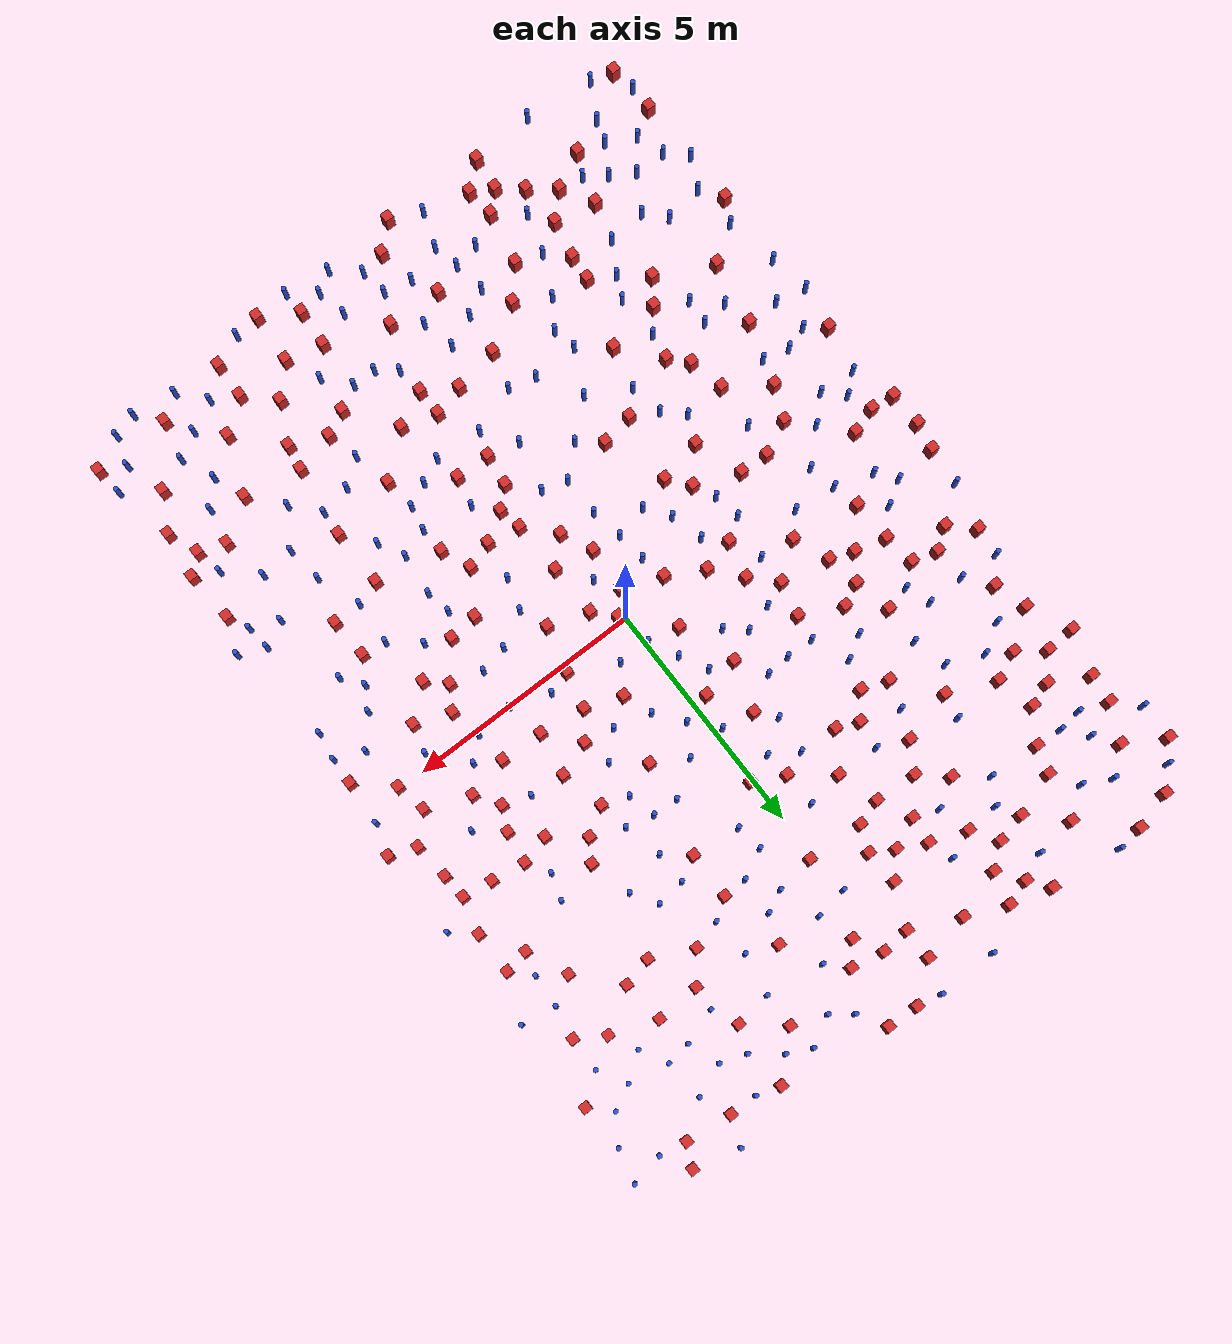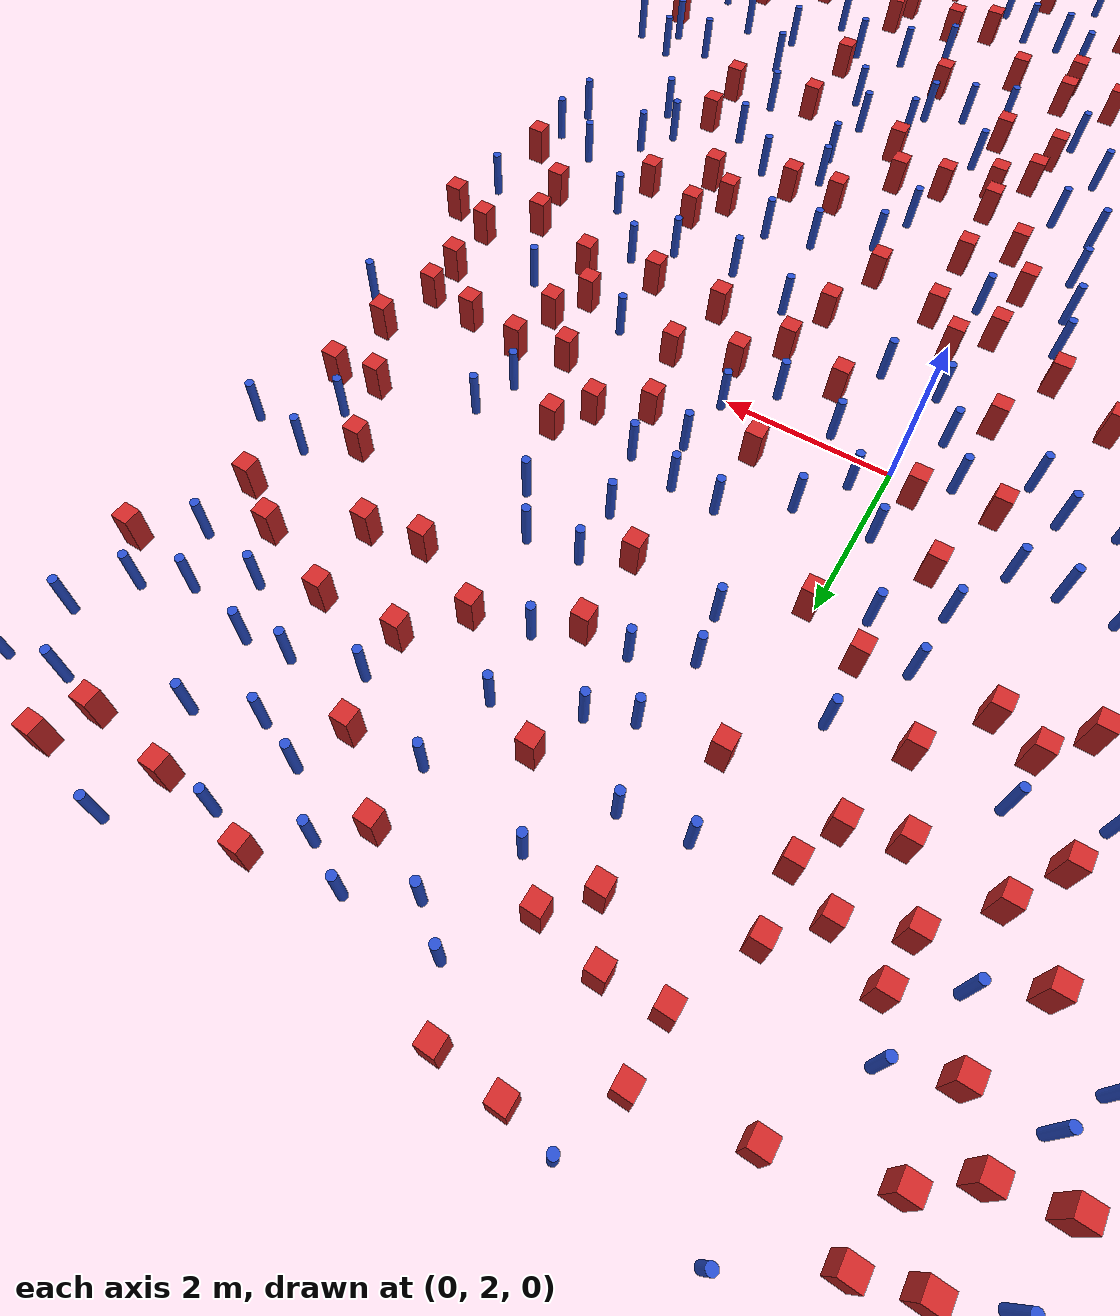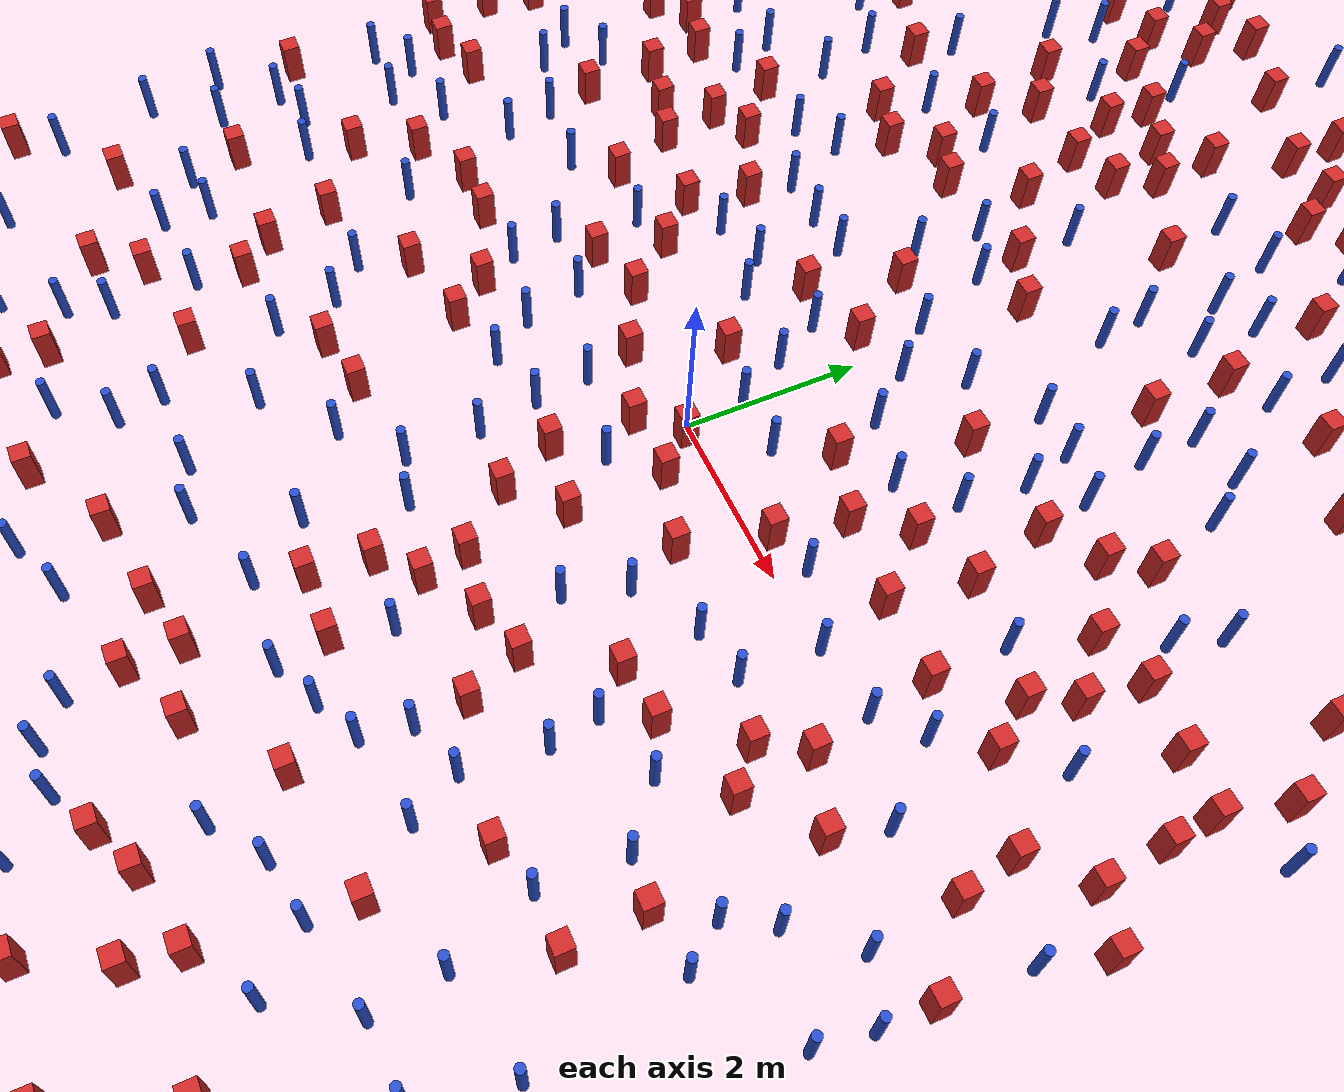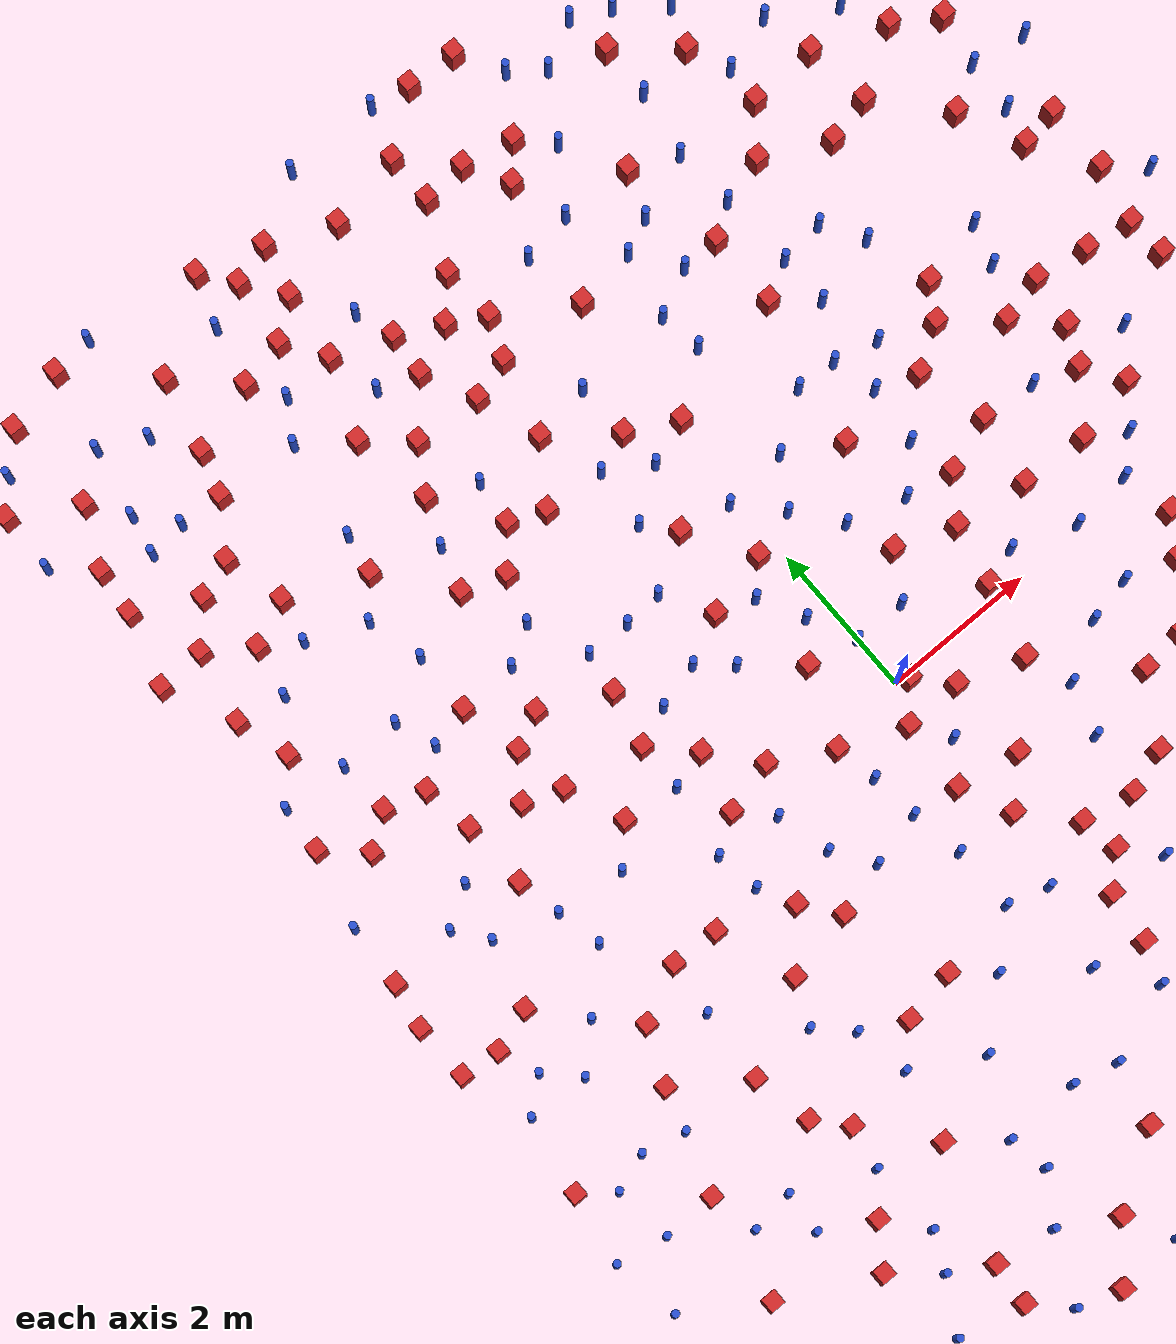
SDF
<sdf version="1.6">
  <model name="dense_92"><model name="pole_obstacle0">
  <static>true</static>
  <pose frame="">3.60466851561 1.68815244617 -3.09024884793e-07 -7.19054271912e-07 -2.11315075122e-07 -1.93935509259e-07</pose>
  <link name="link">
  <pose frame="">0 0 0.3 0 -0 0</pose>
    <inertial>
      <mass>1</mass>
      <inertia>
        <ixx>0.145833</ixx>
        <ixy>0</ixy>
        <ixz>0</ixz>
        <iyy>0.145833</iyy>
        <iyz>0</iyz>
        <izz>0.125</izz>
      </inertia>
    </inertial>
    <collision name="collision">
      <geometry>
        <cylinder>
          <radius>0.05</radius>
          <length>.6</length>
        </cylinder>
      </geometry>
      <max_contacts>10</max_contacts>
      <surface>
        <contact>
          <ode/>
        </contact>
        <bounce/>
        <friction>
          <torsional>
            <ode/>
          </torsional>
          <ode/>
        </friction>
      </surface>
    </collision>
    <visual name="visual">
      <geometry>
        <cylinder>
          <radius>0.05</radius>
          <length>.6</length>
        </cylinder>
      </geometry>
      <material>
        <script>
          <name>Gazebo/Blue</name>
          <uri>file://media/materials/scripts/gazebo.material</uri>
        </script>
      </material>
    </visual>
    <self_collide>0</self_collide>
    <kinematic>0</kinematic>
  </link>
</model>
<model name="pole_obstacle1">
  <static>true</static>
  <pose frame="">-5.81910366463 6.87950488392 -3.09024884793e-07 -7.19054271911e-07 -2.1131507516e-07 -1.93935509277e-07</pose>
  <link name="link">
  <pose frame="">0 0 0.3 0 -0 0</pose>
    <inertial>
      <mass>1</mass>
      <inertia>
        <ixx>0.145833</ixx>
        <ixy>0</ixy>
        <ixz>0</ixz>
        <iyy>0.145833</iyy>
        <iyz>0</iyz>
        <izz>0.125</izz>
      </inertia>
    </inertial>
    <collision name="collision">
      <geometry>
        <cylinder>
          <radius>0.05</radius>
          <length>.6</length>
        </cylinder>
      </geometry>
      <max_contacts>10</max_contacts>
      <surface>
        <contact>
          <ode/>
        </contact>
        <bounce/>
        <friction>
          <torsional>
            <ode/>
          </torsional>
          <ode/>
        </friction>
      </surface>
    </collision>
    <visual name="visual">
      <geometry>
        <cylinder>
          <radius>0.05</radius>
          <length>.6</length>
        </cylinder>
      </geometry>
      <material>
        <script>
          <name>Gazebo/Blue</name>
          <uri>file://media/materials/scripts/gazebo.material</uri>
        </script>
      </material>
    </visual>
    <self_collide>0</self_collide>
    <kinematic>0</kinematic>
  </link>
</model>
<model name="square_post_obstacle0">
  <static>true</static>
  <pose frame="">0.999847726643 1.23337984124 -4.36207812815e-07 3.75137919937e-06 9.77721102514e-07 2.47381364184e-05</pose>
  <link name="link">
    <pose frame="">0 0 0.25 0 -0 0</pose>
    <inertial>
      <mass>100</mass>
      <inertia>
        <ixx>0.166667</ixx>
        <ixy>0</ixy>
        <ixz>0</ixz>
        <iyy>0.166667</iyy>
        <iyz>0</iyz>
        <izz>0.166667</izz>
      </inertia>
    </inertial>
    <collision name="collision">
      <geometry>
        <box>
          <size>.2 .2 .5</size>
        </box>
      </geometry>
      <max_contacts>10</max_contacts>
      <surface>
        <contact>
          <ode/>
        </contact>
        <bounce/>
        <friction>
          <torsional>
            <ode/>
          </torsional>
          <ode/>
        </friction>
      </surface>
    </collision>
    <visual name="visual">
      <geometry>
        <box>
          <size>.2 .2 .5</size>
        </box>
      </geometry>
      <material>
        <script>
          <name>Gazebo/Red</name>
          <uri>file://media/materials/scripts/gazebo.material</uri>
        </script>
      </material>
    </visual>
    <self_collide>0</self_collide>
    <kinematic>0</kinematic>
  </link>
</model>
<model name="square_post_obstacle1">
  <static>true</static>
  <pose frame="">5.77959936031 5.86729845699 -4.36207812815e-07 3.75137919937e-06 9.77721102514e-07 2.47381364184e-05</pose>
  <link name="link">
    <pose frame="">0 0 0.25 0 -0 0</pose>
    <inertial>
      <mass>100</mass>
      <inertia>
        <ixx>0.166667</ixx>
        <ixy>0</ixy>
        <ixz>0</ixz>
        <iyy>0.166667</iyy>
        <iyz>0</iyz>
        <izz>0.166667</izz>
      </inertia>
    </inertial>
    <collision name="collision">
      <geometry>
        <box>
          <size>.2 .2 .5</size>
        </box>
      </geometry>
      <max_contacts>10</max_contacts>
      <surface>
        <contact>
          <ode/>
        </contact>
        <bounce/>
        <friction>
          <torsional>
            <ode/>
          </torsional>
          <ode/>
        </friction>
      </surface>
    </collision>
    <visual name="visual">
      <geometry>
        <box>
          <size>.2 .2 .5</size>
        </box>
      </geometry>
      <material>
        <script>
          <name>Gazebo/Red</name>
          <uri>file://media/materials/scripts/gazebo.material</uri>
        </script>
      </material>
    </visual>
    <self_collide>0</self_collide>
    <kinematic>0</kinematic>
  </link>
</model>
<model name="pole_obstacle2">
  <static>true</static>
  <pose frame="">0.819496799136 4.62784441274 -3.09024884793e-07 -7.19054271912e-07 -2.11315075129e-07 -1.93935509261e-07</pose>
  <link name="link">
  <pose frame="">0 0 0.3 0 -0 0</pose>
    <inertial>
      <mass>1</mass>
      <inertia>
        <ixx>0.145833</ixx>
        <ixy>0</ixy>
        <ixz>0</ixz>
        <iyy>0.145833</iyy>
        <iyz>0</iyz>
        <izz>0.125</izz>
      </inertia>
    </inertial>
    <collision name="collision">
      <geometry>
        <cylinder>
          <radius>0.05</radius>
          <length>.6</length>
        </cylinder>
      </geometry>
      <max_contacts>10</max_contacts>
      <surface>
        <contact>
          <ode/>
        </contact>
        <bounce/>
        <friction>
          <torsional>
            <ode/>
          </torsional>
          <ode/>
        </friction>
      </surface>
    </collision>
    <visual name="visual">
      <geometry>
        <cylinder>
          <radius>0.05</radius>
          <length>.6</length>
        </cylinder>
      </geometry>
      <material>
        <script>
          <name>Gazebo/Blue</name>
          <uri>file://media/materials/scripts/gazebo.material</uri>
        </script>
      </material>
    </visual>
    <self_collide>0</self_collide>
    <kinematic>0</kinematic>
  </link>
</model>
<model name="pole_obstacle3">
  <static>true</static>
  <pose frame="">5.80286417733 8.57099303402 -3.09024884793e-07 -7.19054271912e-07 -2.1131507513e-07 -1.93935509261e-07</pose>
  <link name="link">
  <pose frame="">0 0 0.3 0 -0 0</pose>
    <inertial>
      <mass>1</mass>
      <inertia>
        <ixx>0.145833</ixx>
        <ixy>0</ixy>
        <ixz>0</ixz>
        <iyy>0.145833</iyy>
        <iyz>0</iyz>
        <izz>0.125</izz>
      </inertia>
    </inertial>
    <collision name="collision">
      <geometry>
        <cylinder>
          <radius>0.05</radius>
          <length>.6</length>
        </cylinder>
      </geometry>
      <max_contacts>10</max_contacts>
      <surface>
        <contact>
          <ode/>
        </contact>
        <bounce/>
        <friction>
          <torsional>
            <ode/>
          </torsional>
          <ode/>
        </friction>
      </surface>
    </collision>
    <visual name="visual">
      <geometry>
        <cylinder>
          <radius>0.05</radius>
          <length>.6</length>
        </cylinder>
      </geometry>
      <material>
        <script>
          <name>Gazebo/Blue</name>
          <uri>file://media/materials/scripts/gazebo.material</uri>
        </script>
      </material>
    </visual>
    <self_collide>0</self_collide>
    <kinematic>0</kinematic>
  </link>
</model>
<model name="pole_obstacle4">
  <static>true</static>
  <pose frame="">-0.115058704292 -8.83198249359 -3.09024884793e-07 -7.19054271912e-07 -2.11315075151e-07 -1.93935509274e-07</pose>
  <link name="link">
  <pose frame="">0 0 0.3 0 -0 0</pose>
    <inertial>
      <mass>1</mass>
      <inertia>
        <ixx>0.145833</ixx>
        <ixy>0</ixy>
        <ixz>0</ixz>
        <iyy>0.145833</iyy>
        <iyz>0</iyz>
        <izz>0.125</izz>
      </inertia>
    </inertial>
    <collision name="collision">
      <geometry>
        <cylinder>
          <radius>0.05</radius>
          <length>.6</length>
        </cylinder>
      </geometry>
      <max_contacts>10</max_contacts>
      <surface>
        <contact>
          <ode/>
        </contact>
        <bounce/>
        <friction>
          <torsional>
            <ode/>
          </torsional>
          <ode/>
        </friction>
      </surface>
    </collision>
    <visual name="visual">
      <geometry>
        <cylinder>
          <radius>0.05</radius>
          <length>.6</length>
        </cylinder>
      </geometry>
      <material>
        <script>
          <name>Gazebo/Blue</name>
          <uri>file://media/materials/scripts/gazebo.material</uri>
        </script>
      </material>
    </visual>
    <self_collide>0</self_collide>
    <kinematic>0</kinematic>
  </link>
</model>
<model name="pole_obstacle5">
  <static>true</static>
  <pose frame="">-2.82751781046 -6.0906167842 -3.09024884793e-07 -7.19054271912e-07 -2.11315075134e-07 -1.93935509266e-07</pose>
  <link name="link">
  <pose frame="">0 0 0.3 0 -0 0</pose>
    <inertial>
      <mass>1</mass>
      <inertia>
        <ixx>0.145833</ixx>
        <ixy>0</ixy>
        <ixz>0</ixz>
        <iyy>0.145833</iyy>
        <iyz>0</iyz>
        <izz>0.125</izz>
      </inertia>
    </inertial>
    <collision name="collision">
      <geometry>
        <cylinder>
          <radius>0.05</radius>
          <length>.6</length>
        </cylinder>
      </geometry>
      <max_contacts>10</max_contacts>
      <surface>
        <contact>
          <ode/>
        </contact>
        <bounce/>
        <friction>
          <torsional>
            <ode/>
          </torsional>
          <ode/>
        </friction>
      </surface>
    </collision>
    <visual name="visual">
      <geometry>
        <cylinder>
          <radius>0.05</radius>
          <length>.6</length>
        </cylinder>
      </geometry>
      <material>
        <script>
          <name>Gazebo/Blue</name>
          <uri>file://media/materials/scripts/gazebo.material</uri>
        </script>
      </material>
    </visual>
    <self_collide>0</self_collide>
    <kinematic>0</kinematic>
  </link>
</model>
<model name="pole_obstacle6">
  <static>true</static>
  <pose frame="">5.41370752301 -4.05571315219 -3.09024884793e-07 -7.19054271911e-07 -2.1131507516e-07 -1.93935509277e-07</pose>
  <link name="link">
  <pose frame="">0 0 0.3 0 -0 0</pose>
    <inertial>
      <mass>1</mass>
      <inertia>
        <ixx>0.145833</ixx>
        <ixy>0</ixy>
        <ixz>0</ixz>
        <iyy>0.145833</iyy>
        <iyz>0</iyz>
        <izz>0.125</izz>
      </inertia>
    </inertial>
    <collision name="collision">
      <geometry>
        <cylinder>
          <radius>0.05</radius>
          <length>.6</length>
        </cylinder>
      </geometry>
      <max_contacts>10</max_contacts>
      <surface>
        <contact>
          <ode/>
        </contact>
        <bounce/>
        <friction>
          <torsional>
            <ode/>
          </torsional>
          <ode/>
        </friction>
      </surface>
    </collision>
    <visual name="visual">
      <geometry>
        <cylinder>
          <radius>0.05</radius>
          <length>.6</length>
        </cylinder>
      </geometry>
      <material>
        <script>
          <name>Gazebo/Blue</name>
          <uri>file://media/materials/scripts/gazebo.material</uri>
        </script>
      </material>
    </visual>
    <self_collide>0</self_collide>
    <kinematic>0</kinematic>
  </link>
</model>
<model name="square_post_obstacle2">
  <static>true</static>
  <pose frame="">3.83522175505 -0.541550646575 -4.36207812815e-07 3.75137919937e-06 9.77721102514e-07 2.47381364184e-05</pose>
  <link name="link">
    <pose frame="">0 0 0.25 0 -0 0</pose>
    <inertial>
      <mass>100</mass>
      <inertia>
        <ixx>0.166667</ixx>
        <ixy>0</ixy>
        <ixz>0</ixz>
        <iyy>0.166667</iyy>
        <iyz>0</iyz>
        <izz>0.166667</izz>
      </inertia>
    </inertial>
    <collision name="collision">
      <geometry>
        <box>
          <size>.2 .2 .5</size>
        </box>
      </geometry>
      <max_contacts>10</max_contacts>
      <surface>
        <contact>
          <ode/>
        </contact>
        <bounce/>
        <friction>
          <torsional>
            <ode/>
          </torsional>
          <ode/>
        </friction>
      </surface>
    </collision>
    <visual name="visual">
      <geometry>
        <box>
          <size>.2 .2 .5</size>
        </box>
      </geometry>
      <material>
        <script>
          <name>Gazebo/Red</name>
          <uri>file://media/materials/scripts/gazebo.material</uri>
        </script>
      </material>
    </visual>
    <self_collide>0</self_collide>
    <kinematic>0</kinematic>
  </link>
</model>
<model name="square_post_obstacle3">
  <static>true</static>
  <pose frame="">3.87906195297 2.48973368131 -4.36207812815e-07 3.75137919937e-06 9.77721102514e-07 2.47381364184e-05</pose>
  <link name="link">
    <pose frame="">0 0 0.25 0 -0 0</pose>
    <inertial>
      <mass>100</mass>
      <inertia>
        <ixx>0.166667</ixx>
        <ixy>0</ixy>
        <ixz>0</ixz>
        <iyy>0.166667</iyy>
        <iyz>0</iyz>
        <izz>0.166667</izz>
      </inertia>
    </inertial>
    <collision name="collision">
      <geometry>
        <box>
          <size>.2 .2 .5</size>
        </box>
      </geometry>
      <max_contacts>10</max_contacts>
      <surface>
        <contact>
          <ode/>
        </contact>
        <bounce/>
        <friction>
          <torsional>
            <ode/>
          </torsional>
          <ode/>
        </friction>
      </surface>
    </collision>
    <visual name="visual">
      <geometry>
        <box>
          <size>.2 .2 .5</size>
        </box>
      </geometry>
      <material>
        <script>
          <name>Gazebo/Red</name>
          <uri>file://media/materials/scripts/gazebo.material</uri>
        </script>
      </material>
    </visual>
    <self_collide>0</self_collide>
    <kinematic>0</kinematic>
  </link>
</model>
<model name="square_post_obstacle4">
  <static>true</static>
  <pose frame="">5.19409219351 2.53887665867 -4.36207812815e-07 3.75137919937e-06 9.77721102514e-07 2.47381364184e-05</pose>
  <link name="link">
    <pose frame="">0 0 0.25 0 -0 0</pose>
    <inertial>
      <mass>100</mass>
      <inertia>
        <ixx>0.166667</ixx>
        <ixy>0</ixy>
        <ixz>0</ixz>
        <iyy>0.166667</iyy>
        <iyz>0</iyz>
        <izz>0.166667</izz>
      </inertia>
    </inertial>
    <collision name="collision">
      <geometry>
        <box>
          <size>.2 .2 .5</size>
        </box>
      </geometry>
      <max_contacts>10</max_contacts>
      <surface>
        <contact>
          <ode/>
        </contact>
        <bounce/>
        <friction>
          <torsional>
            <ode/>
          </torsional>
          <ode/>
        </friction>
      </surface>
    </collision>
    <visual name="visual">
      <geometry>
        <box>
          <size>.2 .2 .5</size>
        </box>
      </geometry>
      <material>
        <script>
          <name>Gazebo/Red</name>
          <uri>file://media/materials/scripts/gazebo.material</uri>
        </script>
      </material>
    </visual>
    <self_collide>0</self_collide>
    <kinematic>0</kinematic>
  </link>
</model>
<model name="pole_obstacle7">
  <static>true</static>
  <pose frame="">-1.54520545969 9.47205895562 -3.09024884793e-07 -7.19054271912e-07 -2.1131507515e-07 -1.93935509273e-07</pose>
  <link name="link">
  <pose frame="">0 0 0.3 0 -0 0</pose>
    <inertial>
      <mass>1</mass>
      <inertia>
        <ixx>0.145833</ixx>
        <ixy>0</ixy>
        <ixz>0</ixz>
        <iyy>0.145833</iyy>
        <iyz>0</iyz>
        <izz>0.125</izz>
      </inertia>
    </inertial>
    <collision name="collision">
      <geometry>
        <cylinder>
          <radius>0.05</radius>
          <length>.6</length>
        </cylinder>
      </geometry>
      <max_contacts>10</max_contacts>
      <surface>
        <contact>
          <ode/>
        </contact>
        <bounce/>
        <friction>
          <torsional>
            <ode/>
          </torsional>
          <ode/>
        </friction>
      </surface>
    </collision>
    <visual name="visual">
      <geometry>
        <cylinder>
          <radius>0.05</radius>
          <length>.6</length>
        </cylinder>
      </geometry>
      <material>
        <script>
          <name>Gazebo/Blue</name>
          <uri>file://media/materials/scripts/gazebo.material</uri>
        </script>
      </material>
    </visual>
    <self_collide>0</self_collide>
    <kinematic>0</kinematic>
  </link>
</model>
<model name="pole_obstacle8">
  <static>true</static>
  <pose frame="">-5.93918956181 -2.33999998546 -3.09024884793e-07 -7.19054271912e-07 -2.11315075144e-07 -1.93935509269e-07</pose>
  <link name="link">
  <pose frame="">0 0 0.3 0 -0 0</pose>
    <inertial>
      <mass>1</mass>
      <inertia>
        <ixx>0.145833</ixx>
        <ixy>0</ixy>
        <ixz>0</ixz>
        <iyy>0.145833</iyy>
        <iyz>0</iyz>
        <izz>0.125</izz>
      </inertia>
    </inertial>
    <collision name="collision">
      <geometry>
        <cylinder>
          <radius>0.05</radius>
          <length>.6</length>
        </cylinder>
      </geometry>
      <max_contacts>10</max_contacts>
      <surface>
        <contact>
          <ode/>
        </contact>
        <bounce/>
        <friction>
          <torsional>
            <ode/>
          </torsional>
          <ode/>
        </friction>
      </surface>
    </collision>
    <visual name="visual">
      <geometry>
        <cylinder>
          <radius>0.05</radius>
          <length>.6</length>
        </cylinder>
      </geometry>
      <material>
        <script>
          <name>Gazebo/Blue</name>
          <uri>file://media/materials/scripts/gazebo.material</uri>
        </script>
      </material>
    </visual>
    <self_collide>0</self_collide>
    <kinematic>0</kinematic>
  </link>
</model>
<model name="square_post_obstacle5">
  <static>true</static>
  <pose frame="">-3.86596981586 1.54469500206 -4.36207812815e-07 3.75137919937e-06 9.77721102514e-07 2.47381364184e-05</pose>
  <link name="link">
    <pose frame="">0 0 0.25 0 -0 0</pose>
    <inertial>
      <mass>100</mass>
      <inertia>
        <ixx>0.166667</ixx>
        <ixy>0</ixy>
        <ixz>0</ixz>
        <iyy>0.166667</iyy>
        <iyz>0</iyz>
        <izz>0.166667</izz>
      </inertia>
    </inertial>
    <collision name="collision">
      <geometry>
        <box>
          <size>.2 .2 .5</size>
        </box>
      </geometry>
      <max_contacts>10</max_contacts>
      <surface>
        <contact>
          <ode/>
        </contact>
        <bounce/>
        <friction>
          <torsional>
            <ode/>
          </torsional>
          <ode/>
        </friction>
      </surface>
    </collision>
    <visual name="visual">
      <geometry>
        <box>
          <size>.2 .2 .5</size>
        </box>
      </geometry>
      <material>
        <script>
          <name>Gazebo/Red</name>
          <uri>file://media/materials/scripts/gazebo.material</uri>
        </script>
      </material>
    </visual>
    <self_collide>0</self_collide>
    <kinematic>0</kinematic>
  </link>
</model>
<model name="square_post_obstacle6">
  <static>true</static>
  <pose frame="">4.51285772094 -6.5213713689 -4.36207812815e-07 3.75137919937e-06 9.77721102514e-07 2.47381364184e-05</pose>
  <link name="link">
    <pose frame="">0 0 0.25 0 -0 0</pose>
    <inertial>
      <mass>100</mass>
      <inertia>
        <ixx>0.166667</ixx>
        <ixy>0</ixy>
        <ixz>0</ixz>
        <iyy>0.166667</iyy>
        <iyz>0</iyz>
        <izz>0.166667</izz>
      </inertia>
    </inertial>
    <collision name="collision">
      <geometry>
        <box>
          <size>.2 .2 .5</size>
        </box>
      </geometry>
      <max_contacts>10</max_contacts>
      <surface>
        <contact>
          <ode/>
        </contact>
        <bounce/>
        <friction>
          <torsional>
            <ode/>
          </torsional>
          <ode/>
        </friction>
      </surface>
    </collision>
    <visual name="visual">
      <geometry>
        <box>
          <size>.2 .2 .5</size>
        </box>
      </geometry>
      <material>
        <script>
          <name>Gazebo/Red</name>
          <uri>file://media/materials/scripts/gazebo.material</uri>
        </script>
      </material>
    </visual>
    <self_collide>0</self_collide>
    <kinematic>0</kinematic>
  </link>
</model>
<model name="square_post_obstacle7">
  <static>true</static>
  <pose frame="">-2.67470018567 2.05516223829 -4.36207812815e-07 3.75137919937e-06 9.77721102514e-07 2.47381364184e-05</pose>
  <link name="link">
    <pose frame="">0 0 0.25 0 -0 0</pose>
    <inertial>
      <mass>100</mass>
      <inertia>
        <ixx>0.166667</ixx>
        <ixy>0</ixy>
        <ixz>0</ixz>
        <iyy>0.166667</iyy>
        <iyz>0</iyz>
        <izz>0.166667</izz>
      </inertia>
    </inertial>
    <collision name="collision">
      <geometry>
        <box>
          <size>.2 .2 .5</size>
        </box>
      </geometry>
      <max_contacts>10</max_contacts>
      <surface>
        <contact>
          <ode/>
        </contact>
        <bounce/>
        <friction>
          <torsional>
            <ode/>
          </torsional>
          <ode/>
        </friction>
      </surface>
    </collision>
    <visual name="visual">
      <geometry>
        <box>
          <size>.2 .2 .5</size>
        </box>
      </geometry>
      <material>
        <script>
          <name>Gazebo/Red</name>
          <uri>file://media/materials/scripts/gazebo.material</uri>
        </script>
      </material>
    </visual>
    <self_collide>0</self_collide>
    <kinematic>0</kinematic>
  </link>
</model>
<model name="pole_obstacle9">
  <static>true</static>
  <pose frame="">4.54398680285 8.18161655679 -3.09024884793e-07 -7.19054271912e-07 -2.1131507513e-07 -1.93935509261e-07</pose>
  <link name="link">
  <pose frame="">0 0 0.3 0 -0 0</pose>
    <inertial>
      <mass>1</mass>
      <inertia>
        <ixx>0.145833</ixx>
        <ixy>0</ixy>
        <ixz>0</ixz>
        <iyy>0.145833</iyy>
        <iyz>0</iyz>
        <izz>0.125</izz>
      </inertia>
    </inertial>
    <collision name="collision">
      <geometry>
        <cylinder>
          <radius>0.05</radius>
          <length>.6</length>
        </cylinder>
      </geometry>
      <max_contacts>10</max_contacts>
      <surface>
        <contact>
          <ode/>
        </contact>
        <bounce/>
        <friction>
          <torsional>
            <ode/>
          </torsional>
          <ode/>
        </friction>
      </surface>
    </collision>
    <visual name="visual">
      <geometry>
        <cylinder>
          <radius>0.05</radius>
          <length>.6</length>
        </cylinder>
      </geometry>
      <material>
        <script>
          <name>Gazebo/Blue</name>
          <uri>file://media/materials/scripts/gazebo.material</uri>
        </script>
      </material>
    </visual>
    <self_collide>0</self_collide>
    <kinematic>0</kinematic>
  </link>
</model>
<model name="pole_obstacle10">
  <static>true</static>
  <pose frame="">-0.792953530495 -8.11880526269 -3.09024884793e-07 -7.19054271911e-07 -2.11315075158e-07 -1.93935509277e-07</pose>
  <link name="link">
  <pose frame="">0 0 0.3 0 -0 0</pose>
    <inertial>
      <mass>1</mass>
      <inertia>
        <ixx>0.145833</ixx>
        <ixy>0</ixy>
        <ixz>0</ixz>
        <iyy>0.145833</iyy>
        <iyz>0</iyz>
        <izz>0.125</izz>
      </inertia>
    </inertial>
    <collision name="collision">
      <geometry>
        <cylinder>
          <radius>0.05</radius>
          <length>.6</length>
        </cylinder>
      </geometry>
      <max_contacts>10</max_contacts>
      <surface>
        <contact>
          <ode/>
        </contact>
        <bounce/>
        <friction>
          <torsional>
            <ode/>
          </torsional>
          <ode/>
        </friction>
      </surface>
    </collision>
    <visual name="visual">
      <geometry>
        <cylinder>
          <radius>0.05</radius>
          <length>.6</length>
        </cylinder>
      </geometry>
      <material>
        <script>
          <name>Gazebo/Blue</name>
          <uri>file://media/materials/scripts/gazebo.material</uri>
        </script>
      </material>
    </visual>
    <self_collide>0</self_collide>
    <kinematic>0</kinematic>
  </link>
</model>
<model name="pole_obstacle11">
  <static>true</static>
  <pose frame="">-1.35940231478 -3.42042339917 -3.09024884793e-07 -7.19054271912e-07 -2.11315075132e-07 -1.93935509263e-07</pose>
  <link name="link">
  <pose frame="">0 0 0.3 0 -0 0</pose>
    <inertial>
      <mass>1</mass>
      <inertia>
        <ixx>0.145833</ixx>
        <ixy>0</ixy>
        <ixz>0</ixz>
        <iyy>0.145833</iyy>
        <iyz>0</iyz>
        <izz>0.125</izz>
      </inertia>
    </inertial>
    <collision name="collision">
      <geometry>
        <cylinder>
          <radius>0.05</radius>
          <length>.6</length>
        </cylinder>
      </geometry>
      <max_contacts>10</max_contacts>
      <surface>
        <contact>
          <ode/>
        </contact>
        <bounce/>
        <friction>
          <torsional>
            <ode/>
          </torsional>
          <ode/>
        </friction>
      </surface>
    </collision>
    <visual name="visual">
      <geometry>
        <cylinder>
          <radius>0.05</radius>
          <length>.6</length>
        </cylinder>
      </geometry>
      <material>
        <script>
          <name>Gazebo/Blue</name>
          <uri>file://media/materials/scripts/gazebo.material</uri>
        </script>
      </material>
    </visual>
    <self_collide>0</self_collide>
    <kinematic>0</kinematic>
  </link>
</model>
<model name="pole_obstacle12">
  <static>true</static>
  <pose frame="">3.68674259415 8.8054271333 -3.09024884848e-07 -7.19054271902e-07 -2.11315075199e-07 -1.93935509286e-07</pose>
  <link name="link">
  <pose frame="">0 0 0.3 0 -0 0</pose>
    <inertial>
      <mass>1</mass>
      <inertia>
        <ixx>0.145833</ixx>
        <ixy>0</ixy>
        <ixz>0</ixz>
        <iyy>0.145833</iyy>
        <iyz>0</iyz>
        <izz>0.125</izz>
      </inertia>
    </inertial>
    <collision name="collision">
      <geometry>
        <cylinder>
          <radius>0.05</radius>
          <length>.6</length>
        </cylinder>
      </geometry>
      <max_contacts>10</max_contacts>
      <surface>
        <contact>
          <ode/>
        </contact>
        <bounce/>
        <friction>
          <torsional>
            <ode/>
          </torsional>
          <ode/>
        </friction>
      </surface>
    </collision>
    <visual name="visual">
      <geometry>
        <cylinder>
          <radius>0.05</radius>
          <length>.6</length>
        </cylinder>
      </geometry>
      <material>
        <script>
          <name>Gazebo/Blue</name>
          <uri>file://media/materials/scripts/gazebo.material</uri>
        </script>
      </material>
    </visual>
    <self_collide>0</self_collide>
    <kinematic>0</kinematic>
  </link>
</model>
<model name="square_post_obstacle8">
  <static>true</static>
  <pose frame="">2.1394990033 -9.37077173725 -4.36207812815e-07 3.75137919937e-06 9.77721102514e-07 2.47381364184e-05</pose>
  <link name="link">
    <pose frame="">0 0 0.25 0 -0 0</pose>
    <inertial>
      <mass>100</mass>
      <inertia>
        <ixx>0.166667</ixx>
        <ixy>0</ixy>
        <ixz>0</ixz>
        <iyy>0.166667</iyy>
        <iyz>0</iyz>
        <izz>0.166667</izz>
      </inertia>
    </inertial>
    <collision name="collision">
      <geometry>
        <box>
          <size>.2 .2 .5</size>
        </box>
      </geometry>
      <max_contacts>10</max_contacts>
      <surface>
        <contact>
          <ode/>
        </contact>
        <bounce/>
        <friction>
          <torsional>
            <ode/>
          </torsional>
          <ode/>
        </friction>
      </surface>
    </collision>
    <visual name="visual">
      <geometry>
        <box>
          <size>.2 .2 .5</size>
        </box>
      </geometry>
      <material>
        <script>
          <name>Gazebo/Red</name>
          <uri>file://media/materials/scripts/gazebo.material</uri>
        </script>
      </material>
    </visual>
    <self_collide>0</self_collide>
    <kinematic>0</kinematic>
  </link>
</model>
<model name="square_post_obstacle9">
  <static>true</static>
  <pose frame="">-4.35657237711 -2.52796348364 -4.36207812815e-07 3.75137919937e-06 9.77721102514e-07 2.47381364184e-05</pose>
  <link name="link">
    <pose frame="">0 0 0.25 0 -0 0</pose>
    <inertial>
      <mass>100</mass>
      <inertia>
        <ixx>0.166667</ixx>
        <ixy>0</ixy>
        <ixz>0</ixz>
        <iyy>0.166667</iyy>
        <iyz>0</iyz>
        <izz>0.166667</izz>
      </inertia>
    </inertial>
    <collision name="collision">
      <geometry>
        <box>
          <size>.2 .2 .5</size>
        </box>
      </geometry>
      <max_contacts>10</max_contacts>
      <surface>
        <contact>
          <ode/>
        </contact>
        <bounce/>
        <friction>
          <torsional>
            <ode/>
          </torsional>
          <ode/>
        </friction>
      </surface>
    </collision>
    <visual name="visual">
      <geometry>
        <box>
          <size>.2 .2 .5</size>
        </box>
      </geometry>
      <material>
        <script>
          <name>Gazebo/Red</name>
          <uri>file://media/materials/scripts/gazebo.material</uri>
        </script>
      </material>
    </visual>
    <self_collide>0</self_collide>
    <kinematic>0</kinematic>
  </link>
</model>
<model name="pole_obstacle13">
  <static>true</static>
  <pose frame="">-1.06494217687 4.20370881026 -3.09024884793e-07 -7.19054271912e-07 -2.11315075134e-07 -1.93935509265e-07</pose>
  <link name="link">
  <pose frame="">0 0 0.3 0 -0 0</pose>
    <inertial>
      <mass>1</mass>
      <inertia>
        <ixx>0.145833</ixx>
        <ixy>0</ixy>
        <ixz>0</ixz>
        <iyy>0.145833</iyy>
        <iyz>0</iyz>
        <izz>0.125</izz>
      </inertia>
    </inertial>
    <collision name="collision">
      <geometry>
        <cylinder>
          <radius>0.05</radius>
          <length>.6</length>
        </cylinder>
      </geometry>
      <max_contacts>10</max_contacts>
      <surface>
        <contact>
          <ode/>
        </contact>
        <bounce/>
        <friction>
          <torsional>
            <ode/>
          </torsional>
          <ode/>
        </friction>
      </surface>
    </collision>
    <visual name="visual">
      <geometry>
        <cylinder>
          <radius>0.05</radius>
          <length>.6</length>
        </cylinder>
      </geometry>
      <material>
        <script>
          <name>Gazebo/Blue</name>
          <uri>file://media/materials/scripts/gazebo.material</uri>
        </script>
      </material>
    </visual>
    <self_collide>0</self_collide>
    <kinematic>0</kinematic>
  </link>
</model>
<model name="square_post_obstacle10">
  <static>true</static>
  <pose frame="">-2.92185013055 8.78792637313 -4.36207812815e-07 3.75137919937e-06 9.77721102514e-07 2.47381364184e-05</pose>
  <link name="link">
    <pose frame="">0 0 0.25 0 -0 0</pose>
    <inertial>
      <mass>100</mass>
      <inertia>
        <ixx>0.166667</ixx>
        <ixy>0</ixy>
        <ixz>0</ixz>
        <iyy>0.166667</iyy>
        <iyz>0</iyz>
        <izz>0.166667</izz>
      </inertia>
    </inertial>
    <collision name="collision">
      <geometry>
        <box>
          <size>.2 .2 .5</size>
        </box>
      </geometry>
      <max_contacts>10</max_contacts>
      <surface>
        <contact>
          <ode/>
        </contact>
        <bounce/>
        <friction>
          <torsional>
            <ode/>
          </torsional>
          <ode/>
        </friction>
      </surface>
    </collision>
    <visual name="visual">
      <geometry>
        <box>
          <size>.2 .2 .5</size>
        </box>
      </geometry>
      <material>
        <script>
          <name>Gazebo/Red</name>
          <uri>file://media/materials/scripts/gazebo.material</uri>
        </script>
      </material>
    </visual>
    <self_collide>0</self_collide>
    <kinematic>0</kinematic>
  </link>
</model>
<model name="square_post_obstacle11">
  <static>true</static>
  <pose frame="">-6.83514758745 -8.10717139211 -4.36207812815e-07 3.75137919937e-06 9.77721102514e-07 2.47381364184e-05</pose>
  <link name="link">
    <pose frame="">0 0 0.25 0 -0 0</pose>
    <inertial>
      <mass>100</mass>
      <inertia>
        <ixx>0.166667</ixx>
        <ixy>0</ixy>
        <ixz>0</ixz>
        <iyy>0.166667</iyy>
        <iyz>0</iyz>
        <izz>0.166667</izz>
      </inertia>
    </inertial>
    <collision name="collision">
      <geometry>
        <box>
          <size>.2 .2 .5</size>
        </box>
      </geometry>
      <max_contacts>10</max_contacts>
      <surface>
        <contact>
          <ode/>
        </contact>
        <bounce/>
        <friction>
          <torsional>
            <ode/>
          </torsional>
          <ode/>
        </friction>
      </surface>
    </collision>
    <visual name="visual">
      <geometry>
        <box>
          <size>.2 .2 .5</size>
        </box>
      </geometry>
      <material>
        <script>
          <name>Gazebo/Red</name>
          <uri>file://media/materials/scripts/gazebo.material</uri>
        </script>
      </material>
    </visual>
    <self_collide>0</self_collide>
    <kinematic>0</kinematic>
  </link>
</model>
<model name="pole_obstacle14">
  <static>true</static>
  <pose frame="">-6.27800662612 -7.76188763991 -3.09024884793e-07 -7.19054271911e-07 -2.1131507516e-07 -1.93935509277e-07</pose>
  <link name="link">
  <pose frame="">0 0 0.3 0 -0 0</pose>
    <inertial>
      <mass>1</mass>
      <inertia>
        <ixx>0.145833</ixx>
        <ixy>0</ixy>
        <ixz>0</ixz>
        <iyy>0.145833</iyy>
        <iyz>0</iyz>
        <izz>0.125</izz>
      </inertia>
    </inertial>
    <collision name="collision">
      <geometry>
        <cylinder>
          <radius>0.05</radius>
          <length>.6</length>
        </cylinder>
      </geometry>
      <max_contacts>10</max_contacts>
      <surface>
        <contact>
          <ode/>
        </contact>
        <bounce/>
        <friction>
          <torsional>
            <ode/>
          </torsional>
          <ode/>
        </friction>
      </surface>
    </collision>
    <visual name="visual">
      <geometry>
        <cylinder>
          <radius>0.05</radius>
          <length>.6</length>
        </cylinder>
      </geometry>
      <material>
        <script>
          <name>Gazebo/Blue</name>
          <uri>file://media/materials/scripts/gazebo.material</uri>
        </script>
      </material>
    </visual>
    <self_collide>0</self_collide>
    <kinematic>0</kinematic>
  </link>
</model>
<model name="pole_obstacle15">
  <static>true</static>
  <pose frame="">-0.971050479498 -0.724261945991 -3.09024884793e-07 -7.19054271912e-07 -2.11315075132e-07 -1.93935509265e-07</pose>
  <link name="link">
  <pose frame="">0 0 0.3 0 -0 0</pose>
    <inertial>
      <mass>1</mass>
      <inertia>
        <ixx>0.145833</ixx>
        <ixy>0</ixy>
        <ixz>0</ixz>
        <iyy>0.145833</iyy>
        <iyz>0</iyz>
        <izz>0.125</izz>
      </inertia>
    </inertial>
    <collision name="collision">
      <geometry>
        <cylinder>
          <radius>0.05</radius>
          <length>.6</length>
        </cylinder>
      </geometry>
      <max_contacts>10</max_contacts>
      <surface>
        <contact>
          <ode/>
        </contact>
        <bounce/>
        <friction>
          <torsional>
            <ode/>
          </torsional>
          <ode/>
        </friction>
      </surface>
    </collision>
    <visual name="visual">
      <geometry>
        <cylinder>
          <radius>0.05</radius>
          <length>.6</length>
        </cylinder>
      </geometry>
      <material>
        <script>
          <name>Gazebo/Blue</name>
          <uri>file://media/materials/scripts/gazebo.material</uri>
        </script>
      </material>
    </visual>
    <self_collide>0</self_collide>
    <kinematic>0</kinematic>
  </link>
</model>
<model name="square_post_obstacle12">
  <static>true</static>
  <pose frame="">5.85844302051 1.91838656615 -4.36207812815e-07 3.75137919937e-06 9.77721102514e-07 2.47381364184e-05</pose>
  <link name="link">
    <pose frame="">0 0 0.25 0 -0 0</pose>
    <inertial>
      <mass>100</mass>
      <inertia>
        <ixx>0.166667</ixx>
        <ixy>0</ixy>
        <ixz>0</ixz>
        <iyy>0.166667</iyy>
        <iyz>0</iyz>
        <izz>0.166667</izz>
      </inertia>
    </inertial>
    <collision name="collision">
      <geometry>
        <box>
          <size>.2 .2 .5</size>
        </box>
      </geometry>
      <max_contacts>10</max_contacts>
      <surface>
        <contact>
          <ode/>
        </contact>
        <bounce/>
        <friction>
          <torsional>
            <ode/>
          </torsional>
          <ode/>
        </friction>
      </surface>
    </collision>
    <visual name="visual">
      <geometry>
        <box>
          <size>.2 .2 .5</size>
        </box>
      </geometry>
      <material>
        <script>
          <name>Gazebo/Red</name>
          <uri>file://media/materials/scripts/gazebo.material</uri>
        </script>
      </material>
    </visual>
    <self_collide>0</self_collide>
    <kinematic>0</kinematic>
  </link>
</model>
<model name="pole_obstacle16">
  <static>true</static>
  <pose frame="">-3.11988666219 4.73188384982 -3.09024884793e-07 -7.19054271912e-07 -2.11315075134e-07 -1.93935509266e-07</pose>
  <link name="link">
  <pose frame="">0 0 0.3 0 -0 0</pose>
    <inertial>
      <mass>1</mass>
      <inertia>
        <ixx>0.145833</ixx>
        <ixy>0</ixy>
        <ixz>0</ixz>
        <iyy>0.145833</iyy>
        <iyz>0</iyz>
        <izz>0.125</izz>
      </inertia>
    </inertial>
    <collision name="collision">
      <geometry>
        <cylinder>
          <radius>0.05</radius>
          <length>.6</length>
        </cylinder>
      </geometry>
      <max_contacts>10</max_contacts>
      <surface>
        <contact>
          <ode/>
        </contact>
        <bounce/>
        <friction>
          <torsional>
            <ode/>
          </torsional>
          <ode/>
        </friction>
      </surface>
    </collision>
    <visual name="visual">
      <geometry>
        <cylinder>
          <radius>0.05</radius>
          <length>.6</length>
        </cylinder>
      </geometry>
      <material>
        <script>
          <name>Gazebo/Blue</name>
          <uri>file://media/materials/scripts/gazebo.material</uri>
        </script>
      </material>
    </visual>
    <self_collide>0</self_collide>
    <kinematic>0</kinematic>
  </link>
</model>
<model name="pole_obstacle17">
  <static>true</static>
  <pose frame="">-0.606134589963 -6.50112947915 -3.09024884793e-07 -7.19054271912e-07 -2.11315075129e-07 -1.93935509261e-07</pose>
  <link name="link">
  <pose frame="">0 0 0.3 0 -0 0</pose>
    <inertial>
      <mass>1</mass>
      <inertia>
        <ixx>0.145833</ixx>
        <ixy>0</ixy>
        <ixz>0</ixz>
        <iyy>0.145833</iyy>
        <iyz>0</iyz>
        <izz>0.125</izz>
      </inertia>
    </inertial>
    <collision name="collision">
      <geometry>
        <cylinder>
          <radius>0.05</radius>
          <length>.6</length>
        </cylinder>
      </geometry>
      <max_contacts>10</max_contacts>
      <surface>
        <contact>
          <ode/>
        </contact>
        <bounce/>
        <friction>
          <torsional>
            <ode/>
          </torsional>
          <ode/>
        </friction>
      </surface>
    </collision>
    <visual name="visual">
      <geometry>
        <cylinder>
          <radius>0.05</radius>
          <length>.6</length>
        </cylinder>
      </geometry>
      <material>
        <script>
          <name>Gazebo/Blue</name>
          <uri>file://media/materials/scripts/gazebo.material</uri>
        </script>
      </material>
    </visual>
    <self_collide>0</self_collide>
    <kinematic>0</kinematic>
  </link>
</model>
<model name="square_post_obstacle13">
  <static>true</static>
  <pose frame="">2.64534605135 2.66495597254 -4.36207812815e-07 3.75137919937e-06 9.77721102514e-07 2.47381364184e-05</pose>
  <link name="link">
    <pose frame="">0 0 0.25 0 -0 0</pose>
    <inertial>
      <mass>100</mass>
      <inertia>
        <ixx>0.166667</ixx>
        <ixy>0</ixy>
        <ixz>0</ixz>
        <iyy>0.166667</iyy>
        <iyz>0</iyz>
        <izz>0.166667</izz>
      </inertia>
    </inertial>
    <collision name="collision">
      <geometry>
        <box>
          <size>.2 .2 .5</size>
        </box>
      </geometry>
      <max_contacts>10</max_contacts>
      <surface>
        <contact>
          <ode/>
        </contact>
        <bounce/>
        <friction>
          <torsional>
            <ode/>
          </torsional>
          <ode/>
        </friction>
      </surface>
    </collision>
    <visual name="visual">
      <geometry>
        <box>
          <size>.2 .2 .5</size>
        </box>
      </geometry>
      <material>
        <script>
          <name>Gazebo/Red</name>
          <uri>file://media/materials/scripts/gazebo.material</uri>
        </script>
      </material>
    </visual>
    <self_collide>0</self_collide>
    <kinematic>0</kinematic>
  </link>
</model>
<model name="pole_obstacle18">
  <static>true</static>
  <pose frame="">2.68748436693 -9.3146482331 -3.09024884848e-07 -7.19054271902e-07 -2.11315075199e-07 -1.93935509286e-07</pose>
  <link name="link">
  <pose frame="">0 0 0.3 0 -0 0</pose>
    <inertial>
      <mass>1</mass>
      <inertia>
        <ixx>0.145833</ixx>
        <ixy>0</ixy>
        <ixz>0</ixz>
        <iyy>0.145833</iyy>
        <iyz>0</iyz>
        <izz>0.125</izz>
      </inertia>
    </inertial>
    <collision name="collision">
      <geometry>
        <cylinder>
          <radius>0.05</radius>
          <length>.6</length>
        </cylinder>
      </geometry>
      <max_contacts>10</max_contacts>
      <surface>
        <contact>
          <ode/>
        </contact>
        <bounce/>
        <friction>
          <torsional>
            <ode/>
          </torsional>
          <ode/>
        </friction>
      </surface>
    </collision>
    <visual name="visual">
      <geometry>
        <cylinder>
          <radius>0.05</radius>
          <length>.6</length>
        </cylinder>
      </geometry>
      <material>
        <script>
          <name>Gazebo/Blue</name>
          <uri>file://media/materials/scripts/gazebo.material</uri>
        </script>
      </material>
    </visual>
    <self_collide>0</self_collide>
    <kinematic>0</kinematic>
  </link>
</model>
<model name="square_post_obstacle14">
  <static>true</static>
  <pose frame="">2.96934623551 -1.7296324275 -4.36207812815e-07 3.75137919937e-06 9.77721102514e-07 2.47381364184e-05</pose>
  <link name="link">
    <pose frame="">0 0 0.25 0 -0 0</pose>
    <inertial>
      <mass>100</mass>
      <inertia>
        <ixx>0.166667</ixx>
        <ixy>0</ixy>
        <ixz>0</ixz>
        <iyy>0.166667</iyy>
        <iyz>0</iyz>
        <izz>0.166667</izz>
      </inertia>
    </inertial>
    <collision name="collision">
      <geometry>
        <box>
          <size>.2 .2 .5</size>
        </box>
      </geometry>
      <max_contacts>10</max_contacts>
      <surface>
        <contact>
          <ode/>
        </contact>
        <bounce/>
        <friction>
          <torsional>
            <ode/>
          </torsional>
          <ode/>
        </friction>
      </surface>
    </collision>
    <visual name="visual">
      <geometry>
        <box>
          <size>.2 .2 .5</size>
        </box>
      </geometry>
      <material>
        <script>
          <name>Gazebo/Red</name>
          <uri>file://media/materials/scripts/gazebo.material</uri>
        </script>
      </material>
    </visual>
    <self_collide>0</self_collide>
    <kinematic>0</kinematic>
  </link>
</model>
<model name="pole_obstacle19">
  <static>true</static>
  <pose frame="">5.15001924405 -5.00147786927 -3.09024884793e-07 -7.19054271911e-07 -2.1131507516e-07 -1.93935509277e-07</pose>
  <link name="link">
  <pose frame="">0 0 0.3 0 -0 0</pose>
    <inertial>
      <mass>1</mass>
      <inertia>
        <ixx>0.145833</ixx>
        <ixy>0</ixy>
        <ixz>0</ixz>
        <iyy>0.145833</iyy>
        <iyz>0</iyz>
        <izz>0.125</izz>
      </inertia>
    </inertial>
    <collision name="collision">
      <geometry>
        <cylinder>
          <radius>0.05</radius>
          <length>.6</length>
        </cylinder>
      </geometry>
      <max_contacts>10</max_contacts>
      <surface>
        <contact>
          <ode/>
        </contact>
        <bounce/>
        <friction>
          <torsional>
            <ode/>
          </torsional>
          <ode/>
        </friction>
      </surface>
    </collision>
    <visual name="visual">
      <geometry>
        <cylinder>
          <radius>0.05</radius>
          <length>.6</length>
        </cylinder>
      </geometry>
      <material>
        <script>
          <name>Gazebo/Blue</name>
          <uri>file://media/materials/scripts/gazebo.material</uri>
        </script>
      </material>
    </visual>
    <self_collide>0</self_collide>
    <kinematic>0</kinematic>
  </link>
</model>
<model name="square_post_obstacle15">
  <static>true</static>
  <pose frame="">1.76671340534 0.958167843128 -4.36207812815e-07 3.75137919937e-06 9.77721102514e-07 2.47381364184e-05</pose>
  <link name="link">
    <pose frame="">0 0 0.25 0 -0 0</pose>
    <inertial>
      <mass>100</mass>
      <inertia>
        <ixx>0.166667</ixx>
        <ixy>0</ixy>
        <ixz>0</ixz>
        <iyy>0.166667</iyy>
        <iyz>0</iyz>
        <izz>0.166667</izz>
      </inertia>
    </inertial>
    <collision name="collision">
      <geometry>
        <box>
          <size>.2 .2 .5</size>
        </box>
      </geometry>
      <max_contacts>10</max_contacts>
      <surface>
        <contact>
          <ode/>
        </contact>
        <bounce/>
        <friction>
          <torsional>
            <ode/>
          </torsional>
          <ode/>
        </friction>
      </surface>
    </collision>
    <visual name="visual">
      <geometry>
        <box>
          <size>.2 .2 .5</size>
        </box>
      </geometry>
      <material>
        <script>
          <name>Gazebo/Red</name>
          <uri>file://media/materials/scripts/gazebo.material</uri>
        </script>
      </material>
    </visual>
    <self_collide>0</self_collide>
    <kinematic>0</kinematic>
  </link>
</model>
<model name="square_post_obstacle16">
  <static>true</static>
  <pose frame="">0.765612418779 8.0427565189 -4.36207812815e-07 3.75137919937e-06 9.77721102514e-07 2.47381364184e-05</pose>
  <link name="link">
    <pose frame="">0 0 0.25 0 -0 0</pose>
    <inertial>
      <mass>100</mass>
      <inertia>
        <ixx>0.166667</ixx>
        <ixy>0</ixy>
        <ixz>0</ixz>
        <iyy>0.166667</iyy>
        <iyz>0</iyz>
        <izz>0.166667</izz>
      </inertia>
    </inertial>
    <collision name="collision">
      <geometry>
        <box>
          <size>.2 .2 .5</size>
        </box>
      </geometry>
      <max_contacts>10</max_contacts>
      <surface>
        <contact>
          <ode/>
        </contact>
        <bounce/>
        <friction>
          <torsional>
            <ode/>
          </torsional>
          <ode/>
        </friction>
      </surface>
    </collision>
    <visual name="visual">
      <geometry>
        <box>
          <size>.2 .2 .5</size>
        </box>
      </geometry>
      <material>
        <script>
          <name>Gazebo/Red</name>
          <uri>file://media/materials/scripts/gazebo.material</uri>
        </script>
      </material>
    </visual>
    <self_collide>0</self_collide>
    <kinematic>0</kinematic>
  </link>
</model>
<model name="square_post_obstacle17">
  <static>true</static>
  <pose frame="">4.35246748363 5.68475245587 -4.36207812815e-07 3.75137919937e-06 9.77721102514e-07 2.47381364184e-05</pose>
  <link name="link">
    <pose frame="">0 0 0.25 0 -0 0</pose>
    <inertial>
      <mass>100</mass>
      <inertia>
        <ixx>0.166667</ixx>
        <ixy>0</ixy>
        <ixz>0</ixz>
        <iyy>0.166667</iyy>
        <iyz>0</iyz>
        <izz>0.166667</izz>
      </inertia>
    </inertial>
    <collision name="collision">
      <geometry>
        <box>
          <size>.2 .2 .5</size>
        </box>
      </geometry>
      <max_contacts>10</max_contacts>
      <surface>
        <contact>
          <ode/>
        </contact>
        <bounce/>
        <friction>
          <torsional>
            <ode/>
          </torsional>
          <ode/>
        </friction>
      </surface>
    </collision>
    <visual name="visual">
      <geometry>
        <box>
          <size>.2 .2 .5</size>
        </box>
      </geometry>
      <material>
        <script>
          <name>Gazebo/Red</name>
          <uri>file://media/materials/scripts/gazebo.material</uri>
        </script>
      </material>
    </visual>
    <self_collide>0</self_collide>
    <kinematic>0</kinematic>
  </link>
</model>
<model name="pole_obstacle20">
  <static>true</static>
  <pose frame="">-2.08037863311 -4.06417941965 -3.09024884793e-07 -7.19054271912e-07 -2.11315075134e-07 -1.93935509266e-07</pose>
  <link name="link">
  <pose frame="">0 0 0.3 0 -0 0</pose>
    <inertial>
      <mass>1</mass>
      <inertia>
        <ixx>0.145833</ixx>
        <ixy>0</ixy>
        <ixz>0</ixz>
        <iyy>0.145833</iyy>
        <iyz>0</iyz>
        <izz>0.125</izz>
      </inertia>
    </inertial>
    <collision name="collision">
      <geometry>
        <cylinder>
          <radius>0.05</radius>
          <length>.6</length>
        </cylinder>
      </geometry>
      <max_contacts>10</max_contacts>
      <surface>
        <contact>
          <ode/>
        </contact>
        <bounce/>
        <friction>
          <torsional>
            <ode/>
          </torsional>
          <ode/>
        </friction>
      </surface>
    </collision>
    <visual name="visual">
      <geometry>
        <cylinder>
          <radius>0.05</radius>
          <length>.6</length>
        </cylinder>
      </geometry>
      <material>
        <script>
          <name>Gazebo/Blue</name>
          <uri>file://media/materials/scripts/gazebo.material</uri>
        </script>
      </material>
    </visual>
    <self_collide>0</self_collide>
    <kinematic>0</kinematic>
  </link>
</model>
<model name="pole_obstacle21">
  <static>true</static>
  <pose frame="">-2.4813401762 6.71034206275 -3.09024884793e-07 -7.19054271912e-07 -2.11315075134e-07 -1.93935509266e-07</pose>
  <link name="link">
  <pose frame="">0 0 0.3 0 -0 0</pose>
    <inertial>
      <mass>1</mass>
      <inertia>
        <ixx>0.145833</ixx>
        <ixy>0</ixy>
        <ixz>0</ixz>
        <iyy>0.145833</iyy>
        <iyz>0</iyz>
        <izz>0.125</izz>
      </inertia>
    </inertial>
    <collision name="collision">
      <geometry>
        <cylinder>
          <radius>0.05</radius>
          <length>.6</length>
        </cylinder>
      </geometry>
      <max_contacts>10</max_contacts>
      <surface>
        <contact>
          <ode/>
        </contact>
        <bounce/>
        <friction>
          <torsional>
            <ode/>
          </torsional>
          <ode/>
        </friction>
      </surface>
    </collision>
    <visual name="visual">
      <geometry>
        <cylinder>
          <radius>0.05</radius>
          <length>.6</length>
        </cylinder>
      </geometry>
      <material>
        <script>
          <name>Gazebo/Blue</name>
          <uri>file://media/materials/scripts/gazebo.material</uri>
        </script>
      </material>
    </visual>
    <self_collide>0</self_collide>
    <kinematic>0</kinematic>
  </link>
</model>
<model name="pole_obstacle22">
  <static>true</static>
  <pose frame="">5.62345927579 4.4928146941 -3.09024884793e-07 -7.19054271911e-07 -2.1131507516e-07 -1.93935509277e-07</pose>
  <link name="link">
  <pose frame="">0 0 0.3 0 -0 0</pose>
    <inertial>
      <mass>1</mass>
      <inertia>
        <ixx>0.145833</ixx>
        <ixy>0</ixy>
        <ixz>0</ixz>
        <iyy>0.145833</iyy>
        <iyz>0</iyz>
        <izz>0.125</izz>
      </inertia>
    </inertial>
    <collision name="collision">
      <geometry>
        <cylinder>
          <radius>0.05</radius>
          <length>.6</length>
        </cylinder>
      </geometry>
      <max_contacts>10</max_contacts>
      <surface>
        <contact>
          <ode/>
        </contact>
        <bounce/>
        <friction>
          <torsional>
            <ode/>
          </torsional>
          <ode/>
        </friction>
      </surface>
    </collision>
    <visual name="visual">
      <geometry>
        <cylinder>
          <radius>0.05</radius>
          <length>.6</length>
        </cylinder>
      </geometry>
      <material>
        <script>
          <name>Gazebo/Blue</name>
          <uri>file://media/materials/scripts/gazebo.material</uri>
        </script>
      </material>
    </visual>
    <self_collide>0</self_collide>
    <kinematic>0</kinematic>
  </link>
</model>
<model name="pole_obstacle23">
  <static>true</static>
  <pose frame="">-2.98593588228 -0.246114821247 -3.09024884848e-07 -7.19054271902e-07 -2.11315075197e-07 -1.93935509286e-07</pose>
  <link name="link">
  <pose frame="">0 0 0.3 0 -0 0</pose>
    <inertial>
      <mass>1</mass>
      <inertia>
        <ixx>0.145833</ixx>
        <ixy>0</ixy>
        <ixz>0</ixz>
        <iyy>0.145833</iyy>
        <iyz>0</iyz>
        <izz>0.125</izz>
      </inertia>
    </inertial>
    <collision name="collision">
      <geometry>
        <cylinder>
          <radius>0.05</radius>
          <length>.6</length>
        </cylinder>
      </geometry>
      <max_contacts>10</max_contacts>
      <surface>
        <contact>
          <ode/>
        </contact>
        <bounce/>
        <friction>
          <torsional>
            <ode/>
          </torsional>
          <ode/>
        </friction>
      </surface>
    </collision>
    <visual name="visual">
      <geometry>
        <cylinder>
          <radius>0.05</radius>
          <length>.6</length>
        </cylinder>
      </geometry>
      <material>
        <script>
          <name>Gazebo/Blue</name>
          <uri>file://media/materials/scripts/gazebo.material</uri>
        </script>
      </material>
    </visual>
    <self_collide>0</self_collide>
    <kinematic>0</kinematic>
  </link>
</model>
<model name="square_post_obstacle18">
  <static>true</static>
  <pose frame="">-3.59340045973 -0.903898061147 -4.36207812815e-07 3.75137919937e-06 9.77721102514e-07 2.47381364184e-05</pose>
  <link name="link">
    <pose frame="">0 0 0.25 0 -0 0</pose>
    <inertial>
      <mass>100</mass>
      <inertia>
        <ixx>0.166667</ixx>
        <ixy>0</ixy>
        <ixz>0</ixz>
        <iyy>0.166667</iyy>
        <iyz>0</iyz>
        <izz>0.166667</izz>
      </inertia>
    </inertial>
    <collision name="collision">
      <geometry>
        <box>
          <size>.2 .2 .5</size>
        </box>
      </geometry>
      <max_contacts>10</max_contacts>
      <surface>
        <contact>
          <ode/>
        </contact>
        <bounce/>
        <friction>
          <torsional>
            <ode/>
          </torsional>
          <ode/>
        </friction>
      </surface>
    </collision>
    <visual name="visual">
      <geometry>
        <box>
          <size>.2 .2 .5</size>
        </box>
      </geometry>
      <material>
        <script>
          <name>Gazebo/Red</name>
          <uri>file://media/materials/scripts/gazebo.material</uri>
        </script>
      </material>
    </visual>
    <self_collide>0</self_collide>
    <kinematic>0</kinematic>
  </link>
</model>
<model name="pole_obstacle24">
  <static>true</static>
  <pose frame="">-4.92612174101 -3.79418922728 -3.09024884793e-07 -7.19054271912e-07 -2.11315075144e-07 -1.93935509269e-07</pose>
  <link name="link">
  <pose frame="">0 0 0.3 0 -0 0</pose>
    <inertial>
      <mass>1</mass>
      <inertia>
        <ixx>0.145833</ixx>
        <ixy>0</ixy>
        <ixz>0</ixz>
        <iyy>0.145833</iyy>
        <iyz>0</iyz>
        <izz>0.125</izz>
      </inertia>
    </inertial>
    <collision name="collision">
      <geometry>
        <cylinder>
          <radius>0.05</radius>
          <length>.6</length>
        </cylinder>
      </geometry>
      <max_contacts>10</max_contacts>
      <surface>
        <contact>
          <ode/>
        </contact>
        <bounce/>
        <friction>
          <torsional>
            <ode/>
          </torsional>
          <ode/>
        </friction>
      </surface>
    </collision>
    <visual name="visual">
      <geometry>
        <cylinder>
          <radius>0.05</radius>
          <length>.6</length>
        </cylinder>
      </geometry>
      <material>
        <script>
          <name>Gazebo/Blue</name>
          <uri>file://media/materials/scripts/gazebo.material</uri>
        </script>
      </material>
    </visual>
    <self_collide>0</self_collide>
    <kinematic>0</kinematic>
  </link>
</model>
<model name="pole_obstacle25">
  <static>true</static>
  <pose frame="">4.43334474144 -5.06521078168 -3.09024884793e-07 -7.19054271911e-07 -2.1131507516e-07 -1.93935509277e-07</pose>
  <link name="link">
  <pose frame="">0 0 0.3 0 -0 0</pose>
    <inertial>
      <mass>1</mass>
      <inertia>
        <ixx>0.145833</ixx>
        <ixy>0</ixy>
        <ixz>0</ixz>
        <iyy>0.145833</iyy>
        <iyz>0</iyz>
        <izz>0.125</izz>
      </inertia>
    </inertial>
    <collision name="collision">
      <geometry>
        <cylinder>
          <radius>0.05</radius>
          <length>.6</length>
        </cylinder>
      </geometry>
      <max_contacts>10</max_contacts>
      <surface>
        <contact>
          <ode/>
        </contact>
        <bounce/>
        <friction>
          <torsional>
            <ode/>
          </torsional>
          <ode/>
        </friction>
      </surface>
    </collision>
    <visual name="visual">
      <geometry>
        <cylinder>
          <radius>0.05</radius>
          <length>.6</length>
        </cylinder>
      </geometry>
      <material>
        <script>
          <name>Gazebo/Blue</name>
          <uri>file://media/materials/scripts/gazebo.material</uri>
        </script>
      </material>
    </visual>
    <self_collide>0</self_collide>
    <kinematic>0</kinematic>
  </link>
</model>
<model name="pole_obstacle26">
  <static>true</static>
  <pose frame="">-1.74052222635 1.70367840327 -3.09024884793e-07 -7.19054271912e-07 -2.1131507513e-07 -1.93935509263e-07</pose>
  <link name="link">
  <pose frame="">0 0 0.3 0 -0 0</pose>
    <inertial>
      <mass>1</mass>
      <inertia>
        <ixx>0.145833</ixx>
        <ixy>0</ixy>
        <ixz>0</ixz>
        <iyy>0.145833</iyy>
        <iyz>0</iyz>
        <izz>0.125</izz>
      </inertia>
    </inertial>
    <collision name="collision">
      <geometry>
        <cylinder>
          <radius>0.05</radius>
          <length>.6</length>
        </cylinder>
      </geometry>
      <max_contacts>10</max_contacts>
      <surface>
        <contact>
          <ode/>
        </contact>
        <bounce/>
        <friction>
          <torsional>
            <ode/>
          </torsional>
          <ode/>
        </friction>
      </surface>
    </collision>
    <visual name="visual">
      <geometry>
        <cylinder>
          <radius>0.05</radius>
          <length>.6</length>
        </cylinder>
      </geometry>
      <material>
        <script>
          <name>Gazebo/Blue</name>
          <uri>file://media/materials/scripts/gazebo.material</uri>
        </script>
      </material>
    </visual>
    <self_collide>0</self_collide>
    <kinematic>0</kinematic>
  </link>
</model>
<model name="pole_obstacle27">
  <static>true</static>
  <pose frame="">-1.34639860156 1.36079025889 -3.09024884793e-07 -7.19054271912e-07 -2.1131507513e-07 -1.93935509263e-07</pose>
  <link name="link">
  <pose frame="">0 0 0.3 0 -0 0</pose>
    <inertial>
      <mass>1</mass>
      <inertia>
        <ixx>0.145833</ixx>
        <ixy>0</ixy>
        <ixz>0</ixz>
        <iyy>0.145833</iyy>
        <iyz>0</iyz>
        <izz>0.125</izz>
      </inertia>
    </inertial>
    <collision name="collision">
      <geometry>
        <cylinder>
          <radius>0.05</radius>
          <length>.6</length>
        </cylinder>
      </geometry>
      <max_contacts>10</max_contacts>
      <surface>
        <contact>
          <ode/>
        </contact>
        <bounce/>
        <friction>
          <torsional>
            <ode/>
          </torsional>
          <ode/>
        </friction>
      </surface>
    </collision>
    <visual name="visual">
      <geometry>
        <cylinder>
          <radius>0.05</radius>
          <length>.6</length>
        </cylinder>
      </geometry>
      <material>
        <script>
          <name>Gazebo/Blue</name>
          <uri>file://media/materials/scripts/gazebo.material</uri>
        </script>
      </material>
    </visual>
    <self_collide>0</self_collide>
    <kinematic>0</kinematic>
  </link>
</model>
<model name="pole_obstacle28">
  <static>true</static>
  <pose frame="">-5.37671411241 -0.752074949718 -3.09024884793e-07 -7.19054271912e-07 -2.11315075134e-07 -1.93935509265e-07</pose>
  <link name="link">
  <pose frame="">0 0 0.3 0 -0 0</pose>
    <inertial>
      <mass>1</mass>
      <inertia>
        <ixx>0.145833</ixx>
        <ixy>0</ixy>
        <ixz>0</ixz>
        <iyy>0.145833</iyy>
        <iyz>0</iyz>
        <izz>0.125</izz>
      </inertia>
    </inertial>
    <collision name="collision">
      <geometry>
        <cylinder>
          <radius>0.05</radius>
          <length>.6</length>
        </cylinder>
      </geometry>
      <max_contacts>10</max_contacts>
      <surface>
        <contact>
          <ode/>
        </contact>
        <bounce/>
        <friction>
          <torsional>
            <ode/>
          </torsional>
          <ode/>
        </friction>
      </surface>
    </collision>
    <visual name="visual">
      <geometry>
        <cylinder>
          <radius>0.05</radius>
          <length>.6</length>
        </cylinder>
      </geometry>
      <material>
        <script>
          <name>Gazebo/Blue</name>
          <uri>file://media/materials/scripts/gazebo.material</uri>
        </script>
      </material>
    </visual>
    <self_collide>0</self_collide>
    <kinematic>0</kinematic>
  </link>
</model>
<model name="square_post_obstacle19">
  <static>true</static>
  <pose frame="">-1.17751751848 -9.43307744573 -4.36207812815e-07 3.75137919937e-06 9.77721102514e-07 2.47381364184e-05</pose>
  <link name="link">
    <pose frame="">0 0 0.25 0 -0 0</pose>
    <inertial>
      <mass>100</mass>
      <inertia>
        <ixx>0.166667</ixx>
        <ixy>0</ixy>
        <ixz>0</ixz>
        <iyy>0.166667</iyy>
        <iyz>0</iyz>
        <izz>0.166667</izz>
      </inertia>
    </inertial>
    <collision name="collision">
      <geometry>
        <box>
          <size>.2 .2 .5</size>
        </box>
      </geometry>
      <max_contacts>10</max_contacts>
      <surface>
        <contact>
          <ode/>
        </contact>
        <bounce/>
        <friction>
          <torsional>
            <ode/>
          </torsional>
          <ode/>
        </friction>
      </surface>
    </collision>
    <visual name="visual">
      <geometry>
        <box>
          <size>.2 .2 .5</size>
        </box>
      </geometry>
      <material>
        <script>
          <name>Gazebo/Red</name>
          <uri>file://media/materials/scripts/gazebo.material</uri>
        </script>
      </material>
    </visual>
    <self_collide>0</self_collide>
    <kinematic>0</kinematic>
  </link>
</model>
<model name="square_post_obstacle20">
  <static>true</static>
  <pose frame="">-5.69033943853 6.07431925218 -4.36207812815e-07 3.75137919937e-06 9.77721102514e-07 2.47381364184e-05</pose>
  <link name="link">
    <pose frame="">0 0 0.25 0 -0 0</pose>
    <inertial>
      <mass>100</mass>
      <inertia>
        <ixx>0.166667</ixx>
        <ixy>0</ixy>
        <ixz>0</ixz>
        <iyy>0.166667</iyy>
        <iyz>0</iyz>
        <izz>0.166667</izz>
      </inertia>
    </inertial>
    <collision name="collision">
      <geometry>
        <box>
          <size>.2 .2 .5</size>
        </box>
      </geometry>
      <max_contacts>10</max_contacts>
      <surface>
        <contact>
          <ode/>
        </contact>
        <bounce/>
        <friction>
          <torsional>
            <ode/>
          </torsional>
          <ode/>
        </friction>
      </surface>
    </collision>
    <visual name="visual">
      <geometry>
        <box>
          <size>.2 .2 .5</size>
        </box>
      </geometry>
      <material>
        <script>
          <name>Gazebo/Red</name>
          <uri>file://media/materials/scripts/gazebo.material</uri>
        </script>
      </material>
    </visual>
    <self_collide>0</self_collide>
    <kinematic>0</kinematic>
  </link>
</model>
<model name="pole_obstacle29">
  <static>true</static>
  <pose frame="">-4.50953608733 -6.32848383287 -3.09024884793e-07 -7.19054271911e-07 -2.1131507516e-07 -1.93935509277e-07</pose>
  <link name="link">
  <pose frame="">0 0 0.3 0 -0 0</pose>
    <inertial>
      <mass>1</mass>
      <inertia>
        <ixx>0.145833</ixx>
        <ixy>0</ixy>
        <ixz>0</ixz>
        <iyy>0.145833</iyy>
        <iyz>0</iyz>
        <izz>0.125</izz>
      </inertia>
    </inertial>
    <collision name="collision">
      <geometry>
        <cylinder>
          <radius>0.05</radius>
          <length>.6</length>
        </cylinder>
      </geometry>
      <max_contacts>10</max_contacts>
      <surface>
        <contact>
          <ode/>
        </contact>
        <bounce/>
        <friction>
          <torsional>
            <ode/>
          </torsional>
          <ode/>
        </friction>
      </surface>
    </collision>
    <visual name="visual">
      <geometry>
        <cylinder>
          <radius>0.05</radius>
          <length>.6</length>
        </cylinder>
      </geometry>
      <material>
        <script>
          <name>Gazebo/Blue</name>
          <uri>file://media/materials/scripts/gazebo.material</uri>
        </script>
      </material>
    </visual>
    <self_collide>0</self_collide>
    <kinematic>0</kinematic>
  </link>
</model>
<model name="square_post_obstacle21">
  <static>true</static>
  <pose frame="">0.274103796949 -3.56906607727 -4.36207812815e-07 3.75137919937e-06 9.77721102514e-07 2.47381364184e-05</pose>
  <link name="link">
    <pose frame="">0 0 0.25 0 -0 0</pose>
    <inertial>
      <mass>100</mass>
      <inertia>
        <ixx>0.166667</ixx>
        <ixy>0</ixy>
        <ixz>0</ixz>
        <iyy>0.166667</iyy>
        <iyz>0</iyz>
        <izz>0.166667</izz>
      </inertia>
    </inertial>
    <collision name="collision">
      <geometry>
        <box>
          <size>.2 .2 .5</size>
        </box>
      </geometry>
      <max_contacts>10</max_contacts>
      <surface>
        <contact>
          <ode/>
        </contact>
        <bounce/>
        <friction>
          <torsional>
            <ode/>
          </torsional>
          <ode/>
        </friction>
      </surface>
    </collision>
    <visual name="visual">
      <geometry>
        <box>
          <size>.2 .2 .5</size>
        </box>
      </geometry>
      <material>
        <script>
          <name>Gazebo/Red</name>
          <uri>file://media/materials/scripts/gazebo.material</uri>
        </script>
      </material>
    </visual>
    <self_collide>0</self_collide>
    <kinematic>0</kinematic>
  </link>
</model>
<model name="pole_obstacle30">
  <static>true</static>
  <pose frame="">5.45330103278 7.1637213019 -3.09024884793e-07 -7.19054271911e-07 -2.1131507516e-07 -1.93935509277e-07</pose>
  <link name="link">
  <pose frame="">0 0 0.3 0 -0 0</pose>
    <inertial>
      <mass>1</mass>
      <inertia>
        <ixx>0.145833</ixx>
        <ixy>0</ixy>
        <ixz>0</ixz>
        <iyy>0.145833</iyy>
        <iyz>0</iyz>
        <izz>0.125</izz>
      </inertia>
    </inertial>
    <collision name="collision">
      <geometry>
        <cylinder>
          <radius>0.05</radius>
          <length>.6</length>
        </cylinder>
      </geometry>
      <max_contacts>10</max_contacts>
      <surface>
        <contact>
          <ode/>
        </contact>
        <bounce/>
        <friction>
          <torsional>
            <ode/>
          </torsional>
          <ode/>
        </friction>
      </surface>
    </collision>
    <visual name="visual">
      <geometry>
        <cylinder>
          <radius>0.05</radius>
          <length>.6</length>
        </cylinder>
      </geometry>
      <material>
        <script>
          <name>Gazebo/Blue</name>
          <uri>file://media/materials/scripts/gazebo.material</uri>
        </script>
      </material>
    </visual>
    <self_collide>0</self_collide>
    <kinematic>0</kinematic>
  </link>
</model>
<model name="square_post_obstacle22">
  <static>true</static>
  <pose frame="">-0.294631532423 -1.43798878505 -4.36207812815e-07 3.75137919937e-06 9.77721102514e-07 2.47381364184e-05</pose>
  <link name="link">
    <pose frame="">0 0 0.25 0 -0 0</pose>
    <inertial>
      <mass>100</mass>
      <inertia>
        <ixx>0.166667</ixx>
        <ixy>0</ixy>
        <ixz>0</ixz>
        <iyy>0.166667</iyy>
        <iyz>0</iyz>
        <izz>0.166667</izz>
      </inertia>
    </inertial>
    <collision name="collision">
      <geometry>
        <box>
          <size>.2 .2 .5</size>
        </box>
      </geometry>
      <max_contacts>10</max_contacts>
      <surface>
        <contact>
          <ode/>
        </contact>
        <bounce/>
        <friction>
          <torsional>
            <ode/>
          </torsional>
          <ode/>
        </friction>
      </surface>
    </collision>
    <visual name="visual">
      <geometry>
        <box>
          <size>.2 .2 .5</size>
        </box>
      </geometry>
      <material>
        <script>
          <name>Gazebo/Red</name>
          <uri>file://media/materials/scripts/gazebo.material</uri>
        </script>
      </material>
    </visual>
    <self_collide>0</self_collide>
    <kinematic>0</kinematic>
  </link>
</model>
<model name="square_post_obstacle23">
  <static>true</static>
  <pose frame="">-0.913384427805 7.26544843649 -4.36207812815e-07 3.75137919937e-06 9.77721102514e-07 2.47381364184e-05</pose>
  <link name="link">
    <pose frame="">0 0 0.25 0 -0 0</pose>
    <inertial>
      <mass>100</mass>
      <inertia>
        <ixx>0.166667</ixx>
        <ixy>0</ixy>
        <ixz>0</ixz>
        <iyy>0.166667</iyy>
        <iyz>0</iyz>
        <izz>0.166667</izz>
      </inertia>
    </inertial>
    <collision name="collision">
      <geometry>
        <box>
          <size>.2 .2 .5</size>
        </box>
      </geometry>
      <max_contacts>10</max_contacts>
      <surface>
        <contact>
          <ode/>
        </contact>
        <bounce/>
        <friction>
          <torsional>
            <ode/>
          </torsional>
          <ode/>
        </friction>
      </surface>
    </collision>
    <visual name="visual">
      <geometry>
        <box>
          <size>.2 .2 .5</size>
        </box>
      </geometry>
      <material>
        <script>
          <name>Gazebo/Red</name>
          <uri>file://media/materials/scripts/gazebo.material</uri>
        </script>
      </material>
    </visual>
    <self_collide>0</self_collide>
    <kinematic>0</kinematic>
  </link>
</model>
<model name="pole_obstacle31">
  <static>true</static>
  <pose frame="">-0.582578847249 5.12245408738 -3.09024884793e-07 -7.19054271912e-07 -2.11315075129e-07 -1.93935509261e-07</pose>
  <link name="link">
  <pose frame="">0 0 0.3 0 -0 0</pose>
    <inertial>
      <mass>1</mass>
      <inertia>
        <ixx>0.145833</ixx>
        <ixy>0</ixy>
        <ixz>0</ixz>
        <iyy>0.145833</iyy>
        <iyz>0</iyz>
        <izz>0.125</izz>
      </inertia>
    </inertial>
    <collision name="collision">
      <geometry>
        <cylinder>
          <radius>0.05</radius>
          <length>.6</length>
        </cylinder>
      </geometry>
      <max_contacts>10</max_contacts>
      <surface>
        <contact>
          <ode/>
        </contact>
        <bounce/>
        <friction>
          <torsional>
            <ode/>
          </torsional>
          <ode/>
        </friction>
      </surface>
    </collision>
    <visual name="visual">
      <geometry>
        <cylinder>
          <radius>0.05</radius>
          <length>.6</length>
        </cylinder>
      </geometry>
      <material>
        <script>
          <name>Gazebo/Blue</name>
          <uri>file://media/materials/scripts/gazebo.material</uri>
        </script>
      </material>
    </visual>
    <self_collide>0</self_collide>
    <kinematic>0</kinematic>
  </link>
</model>
<model name="square_post_obstacle24">
  <static>true</static>
  <pose frame="">-3.37426005504 -9.3630403871 -4.36207812815e-07 3.75137919937e-06 9.77721102514e-07 2.47381364184e-05</pose>
  <link name="link">
    <pose frame="">0 0 0.25 0 -0 0</pose>
    <inertial>
      <mass>100</mass>
      <inertia>
        <ixx>0.166667</ixx>
        <ixy>0</ixy>
        <ixz>0</ixz>
        <iyy>0.166667</iyy>
        <iyz>0</iyz>
        <izz>0.166667</izz>
      </inertia>
    </inertial>
    <collision name="collision">
      <geometry>
        <box>
          <size>.2 .2 .5</size>
        </box>
      </geometry>
      <max_contacts>10</max_contacts>
      <surface>
        <contact>
          <ode/>
        </contact>
        <bounce/>
        <friction>
          <torsional>
            <ode/>
          </torsional>
          <ode/>
        </friction>
      </surface>
    </collision>
    <visual name="visual">
      <geometry>
        <box>
          <size>.2 .2 .5</size>
        </box>
      </geometry>
      <material>
        <script>
          <name>Gazebo/Red</name>
          <uri>file://media/materials/scripts/gazebo.material</uri>
        </script>
      </material>
    </visual>
    <self_collide>0</self_collide>
    <kinematic>0</kinematic>
  </link>
</model>
<model name="square_post_obstacle25">
  <static>true</static>
  <pose frame="">1.84017505871 5.49522138336 -4.36207812815e-07 3.75137919937e-06 9.77721102514e-07 2.47381364184e-05</pose>
  <link name="link">
    <pose frame="">0 0 0.25 0 -0 0</pose>
    <inertial>
      <mass>100</mass>
      <inertia>
        <ixx>0.166667</ixx>
        <ixy>0</ixy>
        <ixz>0</ixz>
        <iyy>0.166667</iyy>
        <iyz>0</iyz>
        <izz>0.166667</izz>
      </inertia>
    </inertial>
    <collision name="collision">
      <geometry>
        <box>
          <size>.2 .2 .5</size>
        </box>
      </geometry>
      <max_contacts>10</max_contacts>
      <surface>
        <contact>
          <ode/>
        </contact>
        <bounce/>
        <friction>
          <torsional>
            <ode/>
          </torsional>
          <ode/>
        </friction>
      </surface>
    </collision>
    <visual name="visual">
      <geometry>
        <box>
          <size>.2 .2 .5</size>
        </box>
      </geometry>
      <material>
        <script>
          <name>Gazebo/Red</name>
          <uri>file://media/materials/scripts/gazebo.material</uri>
        </script>
      </material>
    </visual>
    <self_collide>0</self_collide>
    <kinematic>0</kinematic>
  </link>
</model>
<model name="square_post_obstacle26">
  <static>true</static>
  <pose frame="">1.35001822361 -0.771365058201 -4.36207812815e-07 3.75137919937e-06 9.77721102514e-07 2.47381364184e-05</pose>
  <link name="link">
    <pose frame="">0 0 0.25 0 -0 0</pose>
    <inertial>
      <mass>100</mass>
      <inertia>
        <ixx>0.166667</ixx>
        <ixy>0</ixy>
        <ixz>0</ixz>
        <iyy>0.166667</iyy>
        <iyz>0</iyz>
        <izz>0.166667</izz>
      </inertia>
    </inertial>
    <collision name="collision">
      <geometry>
        <box>
          <size>.2 .2 .5</size>
        </box>
      </geometry>
      <max_contacts>10</max_contacts>
      <surface>
        <contact>
          <ode/>
        </contact>
        <bounce/>
        <friction>
          <torsional>
            <ode/>
          </torsional>
          <ode/>
        </friction>
      </surface>
    </collision>
    <visual name="visual">
      <geometry>
        <box>
          <size>.2 .2 .5</size>
        </box>
      </geometry>
      <material>
        <script>
          <name>Gazebo/Red</name>
          <uri>file://media/materials/scripts/gazebo.material</uri>
        </script>
      </material>
    </visual>
    <self_collide>0</self_collide>
    <kinematic>0</kinematic>
  </link>
</model>
<model name="pole_obstacle32">
  <static>true</static>
  <pose frame="">2.02491180352 2.1015205341 -3.09024884793e-07 -7.19054271912e-07 -2.11315075149e-07 -1.93935509273e-07</pose>
  <link name="link">
  <pose frame="">0 0 0.3 0 -0 0</pose>
    <inertial>
      <mass>1</mass>
      <inertia>
        <ixx>0.145833</ixx>
        <ixy>0</ixy>
        <ixz>0</ixz>
        <iyy>0.145833</iyy>
        <iyz>0</iyz>
        <izz>0.125</izz>
      </inertia>
    </inertial>
    <collision name="collision">
      <geometry>
        <cylinder>
          <radius>0.05</radius>
          <length>.6</length>
        </cylinder>
      </geometry>
      <max_contacts>10</max_contacts>
      <surface>
        <contact>
          <ode/>
        </contact>
        <bounce/>
        <friction>
          <torsional>
            <ode/>
          </torsional>
          <ode/>
        </friction>
      </surface>
    </collision>
    <visual name="visual">
      <geometry>
        <cylinder>
          <radius>0.05</radius>
          <length>.6</length>
        </cylinder>
      </geometry>
      <material>
        <script>
          <name>Gazebo/Blue</name>
          <uri>file://media/materials/scripts/gazebo.material</uri>
        </script>
      </material>
    </visual>
    <self_collide>0</self_collide>
    <kinematic>0</kinematic>
  </link>
</model>
<model name="square_post_obstacle27">
  <static>true</static>
  <pose frame="">-5.12865214852 2.57391601149 -4.36207812815e-07 3.75137919937e-06 9.77721102514e-07 2.47381364184e-05</pose>
  <link name="link">
    <pose frame="">0 0 0.25 0 -0 0</pose>
    <inertial>
      <mass>100</mass>
      <inertia>
        <ixx>0.166667</ixx>
        <ixy>0</ixy>
        <ixz>0</ixz>
        <iyy>0.166667</iyy>
        <iyz>0</iyz>
        <izz>0.166667</izz>
      </inertia>
    </inertial>
    <collision name="collision">
      <geometry>
        <box>
          <size>.2 .2 .5</size>
        </box>
      </geometry>
      <max_contacts>10</max_contacts>
      <surface>
        <contact>
          <ode/>
        </contact>
        <bounce/>
        <friction>
          <torsional>
            <ode/>
          </torsional>
          <ode/>
        </friction>
      </surface>
    </collision>
    <visual name="visual">
      <geometry>
        <box>
          <size>.2 .2 .5</size>
        </box>
      </geometry>
      <material>
        <script>
          <name>Gazebo/Red</name>
          <uri>file://media/materials/scripts/gazebo.material</uri>
        </script>
      </material>
    </visual>
    <self_collide>0</self_collide>
    <kinematic>0</kinematic>
  </link>
</model>
<model name="square_post_obstacle28">
  <static>true</static>
  <pose frame="">-1.90888130662 7.08629762976 -4.36207812815e-07 3.75137919937e-06 9.77721102514e-07 2.47381364184e-05</pose>
  <link name="link">
    <pose frame="">0 0 0.25 0 -0 0</pose>
    <inertial>
      <mass>100</mass>
      <inertia>
        <ixx>0.166667</ixx>
        <ixy>0</ixy>
        <ixz>0</ixz>
        <iyy>0.166667</iyy>
        <iyz>0</iyz>
        <izz>0.166667</izz>
      </inertia>
    </inertial>
    <collision name="collision">
      <geometry>
        <box>
          <size>.2 .2 .5</size>
        </box>
      </geometry>
      <max_contacts>10</max_contacts>
      <surface>
        <contact>
          <ode/>
        </contact>
        <bounce/>
        <friction>
          <torsional>
            <ode/>
          </torsional>
          <ode/>
        </friction>
      </surface>
    </collision>
    <visual name="visual">
      <geometry>
        <box>
          <size>.2 .2 .5</size>
        </box>
      </geometry>
      <material>
        <script>
          <name>Gazebo/Red</name>
          <uri>file://media/materials/scripts/gazebo.material</uri>
        </script>
      </material>
    </visual>
    <self_collide>0</self_collide>
    <kinematic>0</kinematic>
  </link>
</model>
<model name="pole_obstacle33">
  <static>true</static>
  <pose frame="">5.62939309707 -0.957960824074 -3.09024884793e-07 -7.19054271912e-07 -2.11315075132e-07 -1.93935509264e-07</pose>
  <link name="link">
  <pose frame="">0 0 0.3 0 -0 0</pose>
    <inertial>
      <mass>1</mass>
      <inertia>
        <ixx>0.145833</ixx>
        <ixy>0</ixy>
        <ixz>0</ixz>
        <iyy>0.145833</iyy>
        <iyz>0</iyz>
        <izz>0.125</izz>
      </inertia>
    </inertial>
    <collision name="collision">
      <geometry>
        <cylinder>
          <radius>0.05</radius>
          <length>.6</length>
        </cylinder>
      </geometry>
      <max_contacts>10</max_contacts>
      <surface>
        <contact>
          <ode/>
        </contact>
        <bounce/>
        <friction>
          <torsional>
            <ode/>
          </torsional>
          <ode/>
        </friction>
      </surface>
    </collision>
    <visual name="visual">
      <geometry>
        <cylinder>
          <radius>0.05</radius>
          <length>.6</length>
        </cylinder>
      </geometry>
      <material>
        <script>
          <name>Gazebo/Blue</name>
          <uri>file://media/materials/scripts/gazebo.material</uri>
        </script>
      </material>
    </visual>
    <self_collide>0</self_collide>
    <kinematic>0</kinematic>
  </link>
</model>
<model name="pole_obstacle34">
  <static>true</static>
  <pose frame="">4.11600173302 0.507920673641 -3.09024884793e-07 -7.19054271912e-07 -2.11315075121e-07 -1.93935509259e-07</pose>
  <link name="link">
  <pose frame="">0 0 0.3 0 -0 0</pose>
    <inertial>
      <mass>1</mass>
      <inertia>
        <ixx>0.145833</ixx>
        <ixy>0</ixy>
        <ixz>0</ixz>
        <iyy>0.145833</iyy>
        <iyz>0</iyz>
        <izz>0.125</izz>
      </inertia>
    </inertial>
    <collision name="collision">
      <geometry>
        <cylinder>
          <radius>0.05</radius>
          <length>.6</length>
        </cylinder>
      </geometry>
      <max_contacts>10</max_contacts>
      <surface>
        <contact>
          <ode/>
        </contact>
        <bounce/>
        <friction>
          <torsional>
            <ode/>
          </torsional>
          <ode/>
        </friction>
      </surface>
    </collision>
    <visual name="visual">
      <geometry>
        <cylinder>
          <radius>0.05</radius>
          <length>.6</length>
        </cylinder>
      </geometry>
      <material>
        <script>
          <name>Gazebo/Blue</name>
          <uri>file://media/materials/scripts/gazebo.material</uri>
        </script>
      </material>
    </visual>
    <self_collide>0</self_collide>
    <kinematic>0</kinematic>
  </link>
</model>
<model name="square_post_obstacle29">
  <static>true</static>
  <pose frame="">-0.207751065891 -5.72229155559 -4.36207812815e-07 3.75137919937e-06 9.77721102514e-07 2.47381364184e-05</pose>
  <link name="link">
    <pose frame="">0 0 0.25 0 -0 0</pose>
    <inertial>
      <mass>100</mass>
      <inertia>
        <ixx>0.166667</ixx>
        <ixy>0</ixy>
        <ixz>0</ixz>
        <iyy>0.166667</iyy>
        <iyz>0</iyz>
        <izz>0.166667</izz>
      </inertia>
    </inertial>
    <collision name="collision">
      <geometry>
        <box>
          <size>.2 .2 .5</size>
        </box>
      </geometry>
      <max_contacts>10</max_contacts>
      <surface>
        <contact>
          <ode/>
        </contact>
        <bounce/>
        <friction>
          <torsional>
            <ode/>
          </torsional>
          <ode/>
        </friction>
      </surface>
    </collision>
    <visual name="visual">
      <geometry>
        <box>
          <size>.2 .2 .5</size>
        </box>
      </geometry>
      <material>
        <script>
          <name>Gazebo/Red</name>
          <uri>file://media/materials/scripts/gazebo.material</uri>
        </script>
      </material>
    </visual>
    <self_collide>0</self_collide>
    <kinematic>0</kinematic>
  </link>
</model>
<model name="pole_obstacle35">
  <static>true</static>
  <pose frame="">6.30162977022 0.28714621884 -3.09024884793e-07 -7.19054271912e-07 -2.11315075135e-07 -1.93935509265e-07</pose>
  <link name="link">
  <pose frame="">0 0 0.3 0 -0 0</pose>
    <inertial>
      <mass>1</mass>
      <inertia>
        <ixx>0.145833</ixx>
        <ixy>0</ixy>
        <ixz>0</ixz>
        <iyy>0.145833</iyy>
        <iyz>0</iyz>
        <izz>0.125</izz>
      </inertia>
    </inertial>
    <collision name="collision">
      <geometry>
        <cylinder>
          <radius>0.05</radius>
          <length>.6</length>
        </cylinder>
      </geometry>
      <max_contacts>10</max_contacts>
      <surface>
        <contact>
          <ode/>
        </contact>
        <bounce/>
        <friction>
          <torsional>
            <ode/>
          </torsional>
          <ode/>
        </friction>
      </surface>
    </collision>
    <visual name="visual">
      <geometry>
        <cylinder>
          <radius>0.05</radius>
          <length>.6</length>
        </cylinder>
      </geometry>
      <material>
        <script>
          <name>Gazebo/Blue</name>
          <uri>file://media/materials/scripts/gazebo.material</uri>
        </script>
      </material>
    </visual>
    <self_collide>0</self_collide>
    <kinematic>0</kinematic>
  </link>
</model>
<model name="square_post_obstacle30">
  <static>true</static>
  <pose frame="">3.33337265653 6.52519556851 -4.36207812815e-07 3.75137919937e-06 9.77721102514e-07 2.47381364184e-05</pose>
  <link name="link">
    <pose frame="">0 0 0.25 0 -0 0</pose>
    <inertial>
      <mass>100</mass>
      <inertia>
        <ixx>0.166667</ixx>
        <ixy>0</ixy>
        <ixz>0</ixz>
        <iyy>0.166667</iyy>
        <iyz>0</iyz>
        <izz>0.166667</izz>
      </inertia>
    </inertial>
    <collision name="collision">
      <geometry>
        <box>
          <size>.2 .2 .5</size>
        </box>
      </geometry>
      <max_contacts>10</max_contacts>
      <surface>
        <contact>
          <ode/>
        </contact>
        <bounce/>
        <friction>
          <torsional>
            <ode/>
          </torsional>
          <ode/>
        </friction>
      </surface>
    </collision>
    <visual name="visual">
      <geometry>
        <box>
          <size>.2 .2 .5</size>
        </box>
      </geometry>
      <material>
        <script>
          <name>Gazebo/Red</name>
          <uri>file://media/materials/scripts/gazebo.material</uri>
        </script>
      </material>
    </visual>
    <self_collide>0</self_collide>
    <kinematic>0</kinematic>
  </link>
</model>
<model name="pole_obstacle36">
  <static>true</static>
  <pose frame="">0.643028839886 6.90297987783 -3.09024884793e-07 -7.19054271912e-07 -2.11315075129e-07 -1.93935509261e-07</pose>
  <link name="link">
  <pose frame="">0 0 0.3 0 -0 0</pose>
    <inertial>
      <mass>1</mass>
      <inertia>
        <ixx>0.145833</ixx>
        <ixy>0</ixy>
        <ixz>0</ixz>
        <iyy>0.145833</iyy>
        <iyz>0</iyz>
        <izz>0.125</izz>
      </inertia>
    </inertial>
    <collision name="collision">
      <geometry>
        <cylinder>
          <radius>0.05</radius>
          <length>.6</length>
        </cylinder>
      </geometry>
      <max_contacts>10</max_contacts>
      <surface>
        <contact>
          <ode/>
        </contact>
        <bounce/>
        <friction>
          <torsional>
            <ode/>
          </torsional>
          <ode/>
        </friction>
      </surface>
    </collision>
    <visual name="visual">
      <geometry>
        <cylinder>
          <radius>0.05</radius>
          <length>.6</length>
        </cylinder>
      </geometry>
      <material>
        <script>
          <name>Gazebo/Blue</name>
          <uri>file://media/materials/scripts/gazebo.material</uri>
        </script>
      </material>
    </visual>
    <self_collide>0</self_collide>
    <kinematic>0</kinematic>
  </link>
</model>
<model name="pole_obstacle37">
  <static>true</static>
  <pose frame="">-2.9515299949 -3.58960341837 -3.09024884793e-07 -7.19054271912e-07 -2.11315075144e-07 -1.93935509271e-07</pose>
  <link name="link">
  <pose frame="">0 0 0.3 0 -0 0</pose>
    <inertial>
      <mass>1</mass>
      <inertia>
        <ixx>0.145833</ixx>
        <ixy>0</ixy>
        <ixz>0</ixz>
        <iyy>0.145833</iyy>
        <iyz>0</iyz>
        <izz>0.125</izz>
      </inertia>
    </inertial>
    <collision name="collision">
      <geometry>
        <cylinder>
          <radius>0.05</radius>
          <length>.6</length>
        </cylinder>
      </geometry>
      <max_contacts>10</max_contacts>
      <surface>
        <contact>
          <ode/>
        </contact>
        <bounce/>
        <friction>
          <torsional>
            <ode/>
          </torsional>
          <ode/>
        </friction>
      </surface>
    </collision>
    <visual name="visual">
      <geometry>
        <cylinder>
          <radius>0.05</radius>
          <length>.6</length>
        </cylinder>
      </geometry>
      <material>
        <script>
          <name>Gazebo/Blue</name>
          <uri>file://media/materials/scripts/gazebo.material</uri>
        </script>
      </material>
    </visual>
    <self_collide>0</self_collide>
    <kinematic>0</kinematic>
  </link>
</model>
<model name="pole_obstacle38">
  <static>true</static>
  <pose frame="">-0.0360535526519 0.674733364668 -3.09024884793e-07 -7.19054271912e-07 -2.1131507514e-07 -1.93935509268e-07</pose>
  <link name="link">
  <pose frame="">0 0 0.3 0 -0 0</pose>
    <inertial>
      <mass>1</mass>
      <inertia>
        <ixx>0.145833</ixx>
        <ixy>0</ixy>
        <ixz>0</ixz>
        <iyy>0.145833</iyy>
        <iyz>0</iyz>
        <izz>0.125</izz>
      </inertia>
    </inertial>
    <collision name="collision">
      <geometry>
        <cylinder>
          <radius>0.05</radius>
          <length>.6</length>
        </cylinder>
      </geometry>
      <max_contacts>10</max_contacts>
      <surface>
        <contact>
          <ode/>
        </contact>
        <bounce/>
        <friction>
          <torsional>
            <ode/>
          </torsional>
          <ode/>
        </friction>
      </surface>
    </collision>
    <visual name="visual">
      <geometry>
        <cylinder>
          <radius>0.05</radius>
          <length>.6</length>
        </cylinder>
      </geometry>
      <material>
        <script>
          <name>Gazebo/Blue</name>
          <uri>file://media/materials/scripts/gazebo.material</uri>
        </script>
      </material>
    </visual>
    <self_collide>0</self_collide>
    <kinematic>0</kinematic>
  </link>
</model>
<model name="pole_obstacle39">
  <static>true</static>
  <pose frame="">4.5023912343 9.3906690146 -3.09024884793e-07 -7.19054271912e-07 -2.1131507513e-07 -1.93935509261e-07</pose>
  <link name="link">
  <pose frame="">0 0 0.3 0 -0 0</pose>
    <inertial>
      <mass>1</mass>
      <inertia>
        <ixx>0.145833</ixx>
        <ixy>0</ixy>
        <ixz>0</ixz>
        <iyy>0.145833</iyy>
        <iyz>0</iyz>
        <izz>0.125</izz>
      </inertia>
    </inertial>
    <collision name="collision">
      <geometry>
        <cylinder>
          <radius>0.05</radius>
          <length>.6</length>
        </cylinder>
      </geometry>
      <max_contacts>10</max_contacts>
      <surface>
        <contact>
          <ode/>
        </contact>
        <bounce/>
        <friction>
          <torsional>
            <ode/>
          </torsional>
          <ode/>
        </friction>
      </surface>
    </collision>
    <visual name="visual">
      <geometry>
        <cylinder>
          <radius>0.05</radius>
          <length>.6</length>
        </cylinder>
      </geometry>
      <material>
        <script>
          <name>Gazebo/Blue</name>
          <uri>file://media/materials/scripts/gazebo.material</uri>
        </script>
      </material>
    </visual>
    <self_collide>0</self_collide>
    <kinematic>0</kinematic>
  </link>
</model>
<model name="pole_obstacle40">
  <static>true</static>
  <pose frame="">2.26468639387 5.78236487332 -3.09024884793e-07 -7.19054271912e-07 -2.11315075134e-07 -1.93935509266e-07</pose>
  <link name="link">
  <pose frame="">0 0 0.3 0 -0 0</pose>
    <inertial>
      <mass>1</mass>
      <inertia>
        <ixx>0.145833</ixx>
        <ixy>0</ixy>
        <ixz>0</ixz>
        <iyy>0.145833</iyy>
        <iyz>0</iyz>
        <izz>0.125</izz>
      </inertia>
    </inertial>
    <collision name="collision">
      <geometry>
        <cylinder>
          <radius>0.05</radius>
          <length>.6</length>
        </cylinder>
      </geometry>
      <max_contacts>10</max_contacts>
      <surface>
        <contact>
          <ode/>
        </contact>
        <bounce/>
        <friction>
          <torsional>
            <ode/>
          </torsional>
          <ode/>
        </friction>
      </surface>
    </collision>
    <visual name="visual">
      <geometry>
        <cylinder>
          <radius>0.05</radius>
          <length>.6</length>
        </cylinder>
      </geometry>
      <material>
        <script>
          <name>Gazebo/Blue</name>
          <uri>file://media/materials/scripts/gazebo.material</uri>
        </script>
      </material>
    </visual>
    <self_collide>0</self_collide>
    <kinematic>0</kinematic>
  </link>
</model>
<model name="pole_obstacle41">
  <static>true</static>
  <pose frame="">-0.336554518417 1.26419817546 -3.09024884793e-07 -7.19054271912e-07 -2.11315075135e-07 -1.93935509265e-07</pose>
  <link name="link">
  <pose frame="">0 0 0.3 0 -0 0</pose>
    <inertial>
      <mass>1</mass>
      <inertia>
        <ixx>0.145833</ixx>
        <ixy>0</ixy>
        <ixz>0</ixz>
        <iyy>0.145833</iyy>
        <iyz>0</iyz>
        <izz>0.125</izz>
      </inertia>
    </inertial>
    <collision name="collision">
      <geometry>
        <cylinder>
          <radius>0.05</radius>
          <length>.6</length>
        </cylinder>
      </geometry>
      <max_contacts>10</max_contacts>
      <surface>
        <contact>
          <ode/>
        </contact>
        <bounce/>
        <friction>
          <torsional>
            <ode/>
          </torsional>
          <ode/>
        </friction>
      </surface>
    </collision>
    <visual name="visual">
      <geometry>
        <cylinder>
          <radius>0.05</radius>
          <length>.6</length>
        </cylinder>
      </geometry>
      <material>
        <script>
          <name>Gazebo/Blue</name>
          <uri>file://media/materials/scripts/gazebo.material</uri>
        </script>
      </material>
    </visual>
    <self_collide>0</self_collide>
    <kinematic>0</kinematic>
  </link>
</model>
<model name="pole_obstacle42">
  <static>true</static>
  <pose frame="">6.22160740358 -1.21050497575 -3.09024884793e-07 -7.19054271912e-07 -2.11315075124e-07 -1.93935509261e-07</pose>
  <link name="link">
  <pose frame="">0 0 0.3 0 -0 0</pose>
    <inertial>
      <mass>1</mass>
      <inertia>
        <ixx>0.145833</ixx>
        <ixy>0</ixy>
        <ixz>0</ixz>
        <iyy>0.145833</iyy>
        <iyz>0</iyz>
        <izz>0.125</izz>
      </inertia>
    </inertial>
    <collision name="collision">
      <geometry>
        <cylinder>
          <radius>0.05</radius>
          <length>.6</length>
        </cylinder>
      </geometry>
      <max_contacts>10</max_contacts>
      <surface>
        <contact>
          <ode/>
        </contact>
        <bounce/>
        <friction>
          <torsional>
            <ode/>
          </torsional>
          <ode/>
        </friction>
      </surface>
    </collision>
    <visual name="visual">
      <geometry>
        <cylinder>
          <radius>0.05</radius>
          <length>.6</length>
        </cylinder>
      </geometry>
      <material>
        <script>
          <name>Gazebo/Blue</name>
          <uri>file://media/materials/scripts/gazebo.material</uri>
        </script>
      </material>
    </visual>
    <self_collide>0</self_collide>
    <kinematic>0</kinematic>
  </link>
</model>
<model name="square_post_obstacle31">
  <static>true</static>
  <pose frame="">-6.58038819236 2.8579494461 -4.36207812815e-07 3.75137919937e-06 9.77721102514e-07 2.47381364184e-05</pose>
  <link name="link">
    <pose frame="">0 0 0.25 0 -0 0</pose>
    <inertial>
      <mass>100</mass>
      <inertia>
        <ixx>0.166667</ixx>
        <ixy>0</ixy>
        <ixz>0</ixz>
        <iyy>0.166667</iyy>
        <iyz>0</iyz>
        <izz>0.166667</izz>
      </inertia>
    </inertial>
    <collision name="collision">
      <geometry>
        <box>
          <size>.2 .2 .5</size>
        </box>
      </geometry>
      <max_contacts>10</max_contacts>
      <surface>
        <contact>
          <ode/>
        </contact>
        <bounce/>
        <friction>
          <torsional>
            <ode/>
          </torsional>
          <ode/>
        </friction>
      </surface>
    </collision>
    <visual name="visual">
      <geometry>
        <box>
          <size>.2 .2 .5</size>
        </box>
      </geometry>
      <material>
        <script>
          <name>Gazebo/Red</name>
          <uri>file://media/materials/scripts/gazebo.material</uri>
        </script>
      </material>
    </visual>
    <self_collide>0</self_collide>
    <kinematic>0</kinematic>
  </link>
</model>
<model name="square_post_obstacle32">
  <static>true</static>
  <pose frame="">-2.1187334367 -6.48678966376 -4.36207812815e-07 3.75137919937e-06 9.77721102514e-07 2.47381364184e-05</pose>
  <link name="link">
    <pose frame="">0 0 0.25 0 -0 0</pose>
    <inertial>
      <mass>100</mass>
      <inertia>
        <ixx>0.166667</ixx>
        <ixy>0</ixy>
        <ixz>0</ixz>
        <iyy>0.166667</iyy>
        <iyz>0</iyz>
        <izz>0.166667</izz>
      </inertia>
    </inertial>
    <collision name="collision">
      <geometry>
        <box>
          <size>.2 .2 .5</size>
        </box>
      </geometry>
      <max_contacts>10</max_contacts>
      <surface>
        <contact>
          <ode/>
        </contact>
        <bounce/>
        <friction>
          <torsional>
            <ode/>
          </torsional>
          <ode/>
        </friction>
      </surface>
    </collision>
    <visual name="visual">
      <geometry>
        <box>
          <size>.2 .2 .5</size>
        </box>
      </geometry>
      <material>
        <script>
          <name>Gazebo/Red</name>
          <uri>file://media/materials/scripts/gazebo.material</uri>
        </script>
      </material>
    </visual>
    <self_collide>0</self_collide>
    <kinematic>0</kinematic>
  </link>
</model>
<model name="square_post_obstacle33">
  <static>true</static>
  <pose frame="">-0.647075574307 -8.92224218763 -4.36207812815e-07 3.75137919937e-06 9.77721102514e-07 2.47381364184e-05</pose>
  <link name="link">
    <pose frame="">0 0 0.25 0 -0 0</pose>
    <inertial>
      <mass>100</mass>
      <inertia>
        <ixx>0.166667</ixx>
        <ixy>0</ixy>
        <ixz>0</ixz>
        <iyy>0.166667</iyy>
        <iyz>0</iyz>
        <izz>0.166667</izz>
      </inertia>
    </inertial>
    <collision name="collision">
      <geometry>
        <box>
          <size>.2 .2 .5</size>
        </box>
      </geometry>
      <max_contacts>10</max_contacts>
      <surface>
        <contact>
          <ode/>
        </contact>
        <bounce/>
        <friction>
          <torsional>
            <ode/>
          </torsional>
          <ode/>
        </friction>
      </surface>
    </collision>
    <visual name="visual">
      <geometry>
        <box>
          <size>.2 .2 .5</size>
        </box>
      </geometry>
      <material>
        <script>
          <name>Gazebo/Red</name>
          <uri>file://media/materials/scripts/gazebo.material</uri>
        </script>
      </material>
    </visual>
    <self_collide>0</self_collide>
    <kinematic>0</kinematic>
  </link>
</model>
<model name="square_post_obstacle34">
  <static>true</static>
  <pose frame="">0.465647620218 -6.13648864373 -4.36207812815e-07 3.75137919937e-06 9.77721102514e-07 2.47381364184e-05</pose>
  <link name="link">
    <pose frame="">0 0 0.25 0 -0 0</pose>
    <inertial>
      <mass>100</mass>
      <inertia>
        <ixx>0.166667</ixx>
        <ixy>0</ixy>
        <ixz>0</ixz>
        <iyy>0.166667</iyy>
        <iyz>0</iyz>
        <izz>0.166667</izz>
      </inertia>
    </inertial>
    <collision name="collision">
      <geometry>
        <box>
          <size>.2 .2 .5</size>
        </box>
      </geometry>
      <max_contacts>10</max_contacts>
      <surface>
        <contact>
          <ode/>
        </contact>
        <bounce/>
        <friction>
          <torsional>
            <ode/>
          </torsional>
          <ode/>
        </friction>
      </surface>
    </collision>
    <visual name="visual">
      <geometry>
        <box>
          <size>.2 .2 .5</size>
        </box>
      </geometry>
      <material>
        <script>
          <name>Gazebo/Red</name>
          <uri>file://media/materials/scripts/gazebo.material</uri>
        </script>
      </material>
    </visual>
    <self_collide>0</self_collide>
    <kinematic>0</kinematic>
  </link>
</model>
<model name="pole_obstacle43">
  <static>true</static>
  <pose frame="">0.717372340981 2.98848043081 -3.09024884793e-07 -7.19054271912e-07 -2.11315075129e-07 -1.93935509263e-07</pose>
  <link name="link">
  <pose frame="">0 0 0.3 0 -0 0</pose>
    <inertial>
      <mass>1</mass>
      <inertia>
        <ixx>0.145833</ixx>
        <ixy>0</ixy>
        <ixz>0</ixz>
        <iyy>0.145833</iyy>
        <iyz>0</iyz>
        <izz>0.125</izz>
      </inertia>
    </inertial>
    <collision name="collision">
      <geometry>
        <cylinder>
          <radius>0.05</radius>
          <length>.6</length>
        </cylinder>
      </geometry>
      <max_contacts>10</max_contacts>
      <surface>
        <contact>
          <ode/>
        </contact>
        <bounce/>
        <friction>
          <torsional>
            <ode/>
          </torsional>
          <ode/>
        </friction>
      </surface>
    </collision>
    <visual name="visual">
      <geometry>
        <cylinder>
          <radius>0.05</radius>
          <length>.6</length>
        </cylinder>
      </geometry>
      <material>
        <script>
          <name>Gazebo/Blue</name>
          <uri>file://media/materials/scripts/gazebo.material</uri>
        </script>
      </material>
    </visual>
    <self_collide>0</self_collide>
    <kinematic>0</kinematic>
  </link>
</model>
<model name="pole_obstacle44">
  <static>true</static>
  <pose frame="">-1.5063312732 2.62010520414 -3.09024884793e-07 -7.19054271912e-07 -2.11315075132e-07 -1.93935509263e-07</pose>
  <link name="link">
  <pose frame="">0 0 0.3 0 -0 0</pose>
    <inertial>
      <mass>1</mass>
      <inertia>
        <ixx>0.145833</ixx>
        <ixy>0</ixy>
        <ixz>0</ixz>
        <iyy>0.145833</iyy>
        <iyz>0</iyz>
        <izz>0.125</izz>
      </inertia>
    </inertial>
    <collision name="collision">
      <geometry>
        <cylinder>
          <radius>0.05</radius>
          <length>.6</length>
        </cylinder>
      </geometry>
      <max_contacts>10</max_contacts>
      <surface>
        <contact>
          <ode/>
        </contact>
        <bounce/>
        <friction>
          <torsional>
            <ode/>
          </torsional>
          <ode/>
        </friction>
      </surface>
    </collision>
    <visual name="visual">
      <geometry>
        <cylinder>
          <radius>0.05</radius>
          <length>.6</length>
        </cylinder>
      </geometry>
      <material>
        <script>
          <name>Gazebo/Blue</name>
          <uri>file://media/materials/scripts/gazebo.material</uri>
        </script>
      </material>
    </visual>
    <self_collide>0</self_collide>
    <kinematic>0</kinematic>
  </link>
</model>
<model name="pole_obstacle45">
  <static>true</static>
  <pose frame="">5.66351207029 5.17743623265 -3.09024884793e-07 -7.19054271911e-07 -2.1131507516e-07 -1.93935509277e-07</pose>
  <link name="link">
  <pose frame="">0 0 0.3 0 -0 0</pose>
    <inertial>
      <mass>1</mass>
      <inertia>
        <ixx>0.145833</ixx>
        <ixy>0</ixy>
        <ixz>0</ixz>
        <iyy>0.145833</iyy>
        <iyz>0</iyz>
        <izz>0.125</izz>
      </inertia>
    </inertial>
    <collision name="collision">
      <geometry>
        <cylinder>
          <radius>0.05</radius>
          <length>.6</length>
        </cylinder>
      </geometry>
      <max_contacts>10</max_contacts>
      <surface>
        <contact>
          <ode/>
        </contact>
        <bounce/>
        <friction>
          <torsional>
            <ode/>
          </torsional>
          <ode/>
        </friction>
      </surface>
    </collision>
    <visual name="visual">
      <geometry>
        <cylinder>
          <radius>0.05</radius>
          <length>.6</length>
        </cylinder>
      </geometry>
      <material>
        <script>
          <name>Gazebo/Blue</name>
          <uri>file://media/materials/scripts/gazebo.material</uri>
        </script>
      </material>
    </visual>
    <self_collide>0</self_collide>
    <kinematic>0</kinematic>
  </link>
</model>
<model name="square_post_obstacle35">
  <static>true</static>
  <pose frame="">3.18902725416 8.95788062331 -4.36207812815e-07 3.75137919937e-06 9.77721102514e-07 2.47381364184e-05</pose>
  <link name="link">
    <pose frame="">0 0 0.25 0 -0 0</pose>
    <inertial>
      <mass>100</mass>
      <inertia>
        <ixx>0.166667</ixx>
        <ixy>0</ixy>
        <ixz>0</ixz>
        <iyy>0.166667</iyy>
        <iyz>0</iyz>
        <izz>0.166667</izz>
      </inertia>
    </inertial>
    <collision name="collision">
      <geometry>
        <box>
          <size>.2 .2 .5</size>
        </box>
      </geometry>
      <max_contacts>10</max_contacts>
      <surface>
        <contact>
          <ode/>
        </contact>
        <bounce/>
        <friction>
          <torsional>
            <ode/>
          </torsional>
          <ode/>
        </friction>
      </surface>
    </collision>
    <visual name="visual">
      <geometry>
        <box>
          <size>.2 .2 .5</size>
        </box>
      </geometry>
      <material>
        <script>
          <name>Gazebo/Red</name>
          <uri>file://media/materials/scripts/gazebo.material</uri>
        </script>
      </material>
    </visual>
    <self_collide>0</self_collide>
    <kinematic>0</kinematic>
  </link>
</model>
<model name="pole_obstacle46">
  <static>true</static>
  <pose frame="">-6.42709870268 -2.50777887433 -3.09024884793e-07 -7.19054271912e-07 -2.11315075144e-07 -1.93935509269e-07</pose>
  <link name="link">
  <pose frame="">0 0 0.3 0 -0 0</pose>
    <inertial>
      <mass>1</mass>
      <inertia>
        <ixx>0.145833</ixx>
        <ixy>0</ixy>
        <ixz>0</ixz>
        <iyy>0.145833</iyy>
        <iyz>0</iyz>
        <izz>0.125</izz>
      </inertia>
    </inertial>
    <collision name="collision">
      <geometry>
        <cylinder>
          <radius>0.05</radius>
          <length>.6</length>
        </cylinder>
      </geometry>
      <max_contacts>10</max_contacts>
      <surface>
        <contact>
          <ode/>
        </contact>
        <bounce/>
        <friction>
          <torsional>
            <ode/>
          </torsional>
          <ode/>
        </friction>
      </surface>
    </collision>
    <visual name="visual">
      <geometry>
        <cylinder>
          <radius>0.05</radius>
          <length>.6</length>
        </cylinder>
      </geometry>
      <material>
        <script>
          <name>Gazebo/Blue</name>
          <uri>file://media/materials/scripts/gazebo.material</uri>
        </script>
      </material>
    </visual>
    <self_collide>0</self_collide>
    <kinematic>0</kinematic>
  </link>
</model>
<model name="pole_obstacle47">
  <static>true</static>
  <pose frame="">2.01590928017 -4.33090438591 -3.09024884793e-07 -7.19054271912e-07 -2.11315075136e-07 -1.93935509266e-07</pose>
  <link name="link">
  <pose frame="">0 0 0.3 0 -0 0</pose>
    <inertial>
      <mass>1</mass>
      <inertia>
        <ixx>0.145833</ixx>
        <ixy>0</ixy>
        <ixz>0</ixz>
        <iyy>0.145833</iyy>
        <iyz>0</iyz>
        <izz>0.125</izz>
      </inertia>
    </inertial>
    <collision name="collision">
      <geometry>
        <cylinder>
          <radius>0.05</radius>
          <length>.6</length>
        </cylinder>
      </geometry>
      <max_contacts>10</max_contacts>
      <surface>
        <contact>
          <ode/>
        </contact>
        <bounce/>
        <friction>
          <torsional>
            <ode/>
          </torsional>
          <ode/>
        </friction>
      </surface>
    </collision>
    <visual name="visual">
      <geometry>
        <cylinder>
          <radius>0.05</radius>
          <length>.6</length>
        </cylinder>
      </geometry>
      <material>
        <script>
          <name>Gazebo/Blue</name>
          <uri>file://media/materials/scripts/gazebo.material</uri>
        </script>
      </material>
    </visual>
    <self_collide>0</self_collide>
    <kinematic>0</kinematic>
  </link>
</model>
<model name="square_post_obstacle36">
  <static>true</static>
  <pose frame="">1.58505798549 6.85509384784 -4.36207812815e-07 3.75137919937e-06 9.77721102514e-07 2.47381364184e-05</pose>
  <link name="link">
    <pose frame="">0 0 0.25 0 -0 0</pose>
    <inertial>
      <mass>100</mass>
      <inertia>
        <ixx>0.166667</ixx>
        <ixy>0</ixy>
        <ixz>0</ixz>
        <iyy>0.166667</iyy>
        <iyz>0</iyz>
        <izz>0.166667</izz>
      </inertia>
    </inertial>
    <collision name="collision">
      <geometry>
        <box>
          <size>.2 .2 .5</size>
        </box>
      </geometry>
      <max_contacts>10</max_contacts>
      <surface>
        <contact>
          <ode/>
        </contact>
        <bounce/>
        <friction>
          <torsional>
            <ode/>
          </torsional>
          <ode/>
        </friction>
      </surface>
    </collision>
    <visual name="visual">
      <geometry>
        <box>
          <size>.2 .2 .5</size>
        </box>
      </geometry>
      <material>
        <script>
          <name>Gazebo/Red</name>
          <uri>file://media/materials/scripts/gazebo.material</uri>
        </script>
      </material>
    </visual>
    <self_collide>0</self_collide>
    <kinematic>0</kinematic>
  </link>
</model>
<model name="square_post_obstacle37">
  <static>true</static>
  <pose frame="">-4.32250167181 -4.69132706241 -4.36207812815e-07 3.75137919937e-06 9.77721102514e-07 2.47381364184e-05</pose>
  <link name="link">
    <pose frame="">0 0 0.25 0 -0 0</pose>
    <inertial>
      <mass>100</mass>
      <inertia>
        <ixx>0.166667</ixx>
        <ixy>0</ixy>
        <ixz>0</ixz>
        <iyy>0.166667</iyy>
        <iyz>0</iyz>
        <izz>0.166667</izz>
      </inertia>
    </inertial>
    <collision name="collision">
      <geometry>
        <box>
          <size>.2 .2 .5</size>
        </box>
      </geometry>
      <max_contacts>10</max_contacts>
      <surface>
        <contact>
          <ode/>
        </contact>
        <bounce/>
        <friction>
          <torsional>
            <ode/>
          </torsional>
          <ode/>
        </friction>
      </surface>
    </collision>
    <visual name="visual">
      <geometry>
        <box>
          <size>.2 .2 .5</size>
        </box>
      </geometry>
      <material>
        <script>
          <name>Gazebo/Red</name>
          <uri>file://media/materials/scripts/gazebo.material</uri>
        </script>
      </material>
    </visual>
    <self_collide>0</self_collide>
    <kinematic>0</kinematic>
  </link>
</model>
<model name="pole_obstacle48">
  <static>true</static>
  <pose frame="">3.37117523829 7.02716091844 -3.09024884793e-07 -7.19054271912e-07 -2.11315075134e-07 -1.93935509266e-07</pose>
  <link name="link">
  <pose frame="">0 0 0.3 0 -0 0</pose>
    <inertial>
      <mass>1</mass>
      <inertia>
        <ixx>0.145833</ixx>
        <ixy>0</ixy>
        <ixz>0</ixz>
        <iyy>0.145833</iyy>
        <iyz>0</iyz>
        <izz>0.125</izz>
      </inertia>
    </inertial>
    <collision name="collision">
      <geometry>
        <cylinder>
          <radius>0.05</radius>
          <length>.6</length>
        </cylinder>
      </geometry>
      <max_contacts>10</max_contacts>
      <surface>
        <contact>
          <ode/>
        </contact>
        <bounce/>
        <friction>
          <torsional>
            <ode/>
          </torsional>
          <ode/>
        </friction>
      </surface>
    </collision>
    <visual name="visual">
      <geometry>
        <cylinder>
          <radius>0.05</radius>
          <length>.6</length>
        </cylinder>
      </geometry>
      <material>
        <script>
          <name>Gazebo/Blue</name>
          <uri>file://media/materials/scripts/gazebo.material</uri>
        </script>
      </material>
    </visual>
    <self_collide>0</self_collide>
    <kinematic>0</kinematic>
  </link>
</model>
<model name="square_post_obstacle38">
  <static>true</static>
  <pose frame="">3.11801882603 7.56546651284 -4.36207812815e-07 3.75137919937e-06 9.77721102514e-07 2.47381364184e-05</pose>
  <link name="link">
    <pose frame="">0 0 0.25 0 -0 0</pose>
    <inertial>
      <mass>100</mass>
      <inertia>
        <ixx>0.166667</ixx>
        <ixy>0</ixy>
        <ixz>0</ixz>
        <iyy>0.166667</iyy>
        <iyz>0</iyz>
        <izz>0.166667</izz>
      </inertia>
    </inertial>
    <collision name="collision">
      <geometry>
        <box>
          <size>.2 .2 .5</size>
        </box>
      </geometry>
      <max_contacts>10</max_contacts>
      <surface>
        <contact>
          <ode/>
        </contact>
        <bounce/>
        <friction>
          <torsional>
            <ode/>
          </torsional>
          <ode/>
        </friction>
      </surface>
    </collision>
    <visual name="visual">
      <geometry>
        <box>
          <size>.2 .2 .5</size>
        </box>
      </geometry>
      <material>
        <script>
          <name>Gazebo/Red</name>
          <uri>file://media/materials/scripts/gazebo.material</uri>
        </script>
      </material>
    </visual>
    <self_collide>0</self_collide>
    <kinematic>0</kinematic>
  </link>
</model>
<model name="square_post_obstacle39">
  <static>true</static>
  <pose frame="">1.59438663737 0.182219720311 -4.36207812815e-07 3.75137919937e-06 9.77721102514e-07 2.47381364184e-05</pose>
  <link name="link">
    <pose frame="">0 0 0.25 0 -0 0</pose>
    <inertial>
      <mass>100</mass>
      <inertia>
        <ixx>0.166667</ixx>
        <ixy>0</ixy>
        <ixz>0</ixz>
        <iyy>0.166667</iyy>
        <iyz>0</iyz>
        <izz>0.166667</izz>
      </inertia>
    </inertial>
    <collision name="collision">
      <geometry>
        <box>
          <size>.2 .2 .5</size>
        </box>
      </geometry>
      <max_contacts>10</max_contacts>
      <surface>
        <contact>
          <ode/>
        </contact>
        <bounce/>
        <friction>
          <torsional>
            <ode/>
          </torsional>
          <ode/>
        </friction>
      </surface>
    </collision>
    <visual name="visual">
      <geometry>
        <box>
          <size>.2 .2 .5</size>
        </box>
      </geometry>
      <material>
        <script>
          <name>Gazebo/Red</name>
          <uri>file://media/materials/scripts/gazebo.material</uri>
        </script>
      </material>
    </visual>
    <self_collide>0</self_collide>
    <kinematic>0</kinematic>
  </link>
</model>
<model name="pole_obstacle49">
  <static>true</static>
  <pose frame="">-0.764590414519 -2.87432632808 -3.09024884793e-07 -7.19054271912e-07 -2.11315075129e-07 -1.93935509263e-07</pose>
  <link name="link">
  <pose frame="">0 0 0.3 0 -0 0</pose>
    <inertial>
      <mass>1</mass>
      <inertia>
        <ixx>0.145833</ixx>
        <ixy>0</ixy>
        <ixz>0</ixz>
        <iyy>0.145833</iyy>
        <iyz>0</iyz>
        <izz>0.125</izz>
      </inertia>
    </inertial>
    <collision name="collision">
      <geometry>
        <cylinder>
          <radius>0.05</radius>
          <length>.6</length>
        </cylinder>
      </geometry>
      <max_contacts>10</max_contacts>
      <surface>
        <contact>
          <ode/>
        </contact>
        <bounce/>
        <friction>
          <torsional>
            <ode/>
          </torsional>
          <ode/>
        </friction>
      </surface>
    </collision>
    <visual name="visual">
      <geometry>
        <cylinder>
          <radius>0.05</radius>
          <length>.6</length>
        </cylinder>
      </geometry>
      <material>
        <script>
          <name>Gazebo/Blue</name>
          <uri>file://media/materials/scripts/gazebo.material</uri>
        </script>
      </material>
    </visual>
    <self_collide>0</self_collide>
    <kinematic>0</kinematic>
  </link>
</model>
<model name="pole_obstacle50">
  <static>true</static>
  <pose frame="">-2.89263243669 -0.820374511175 -3.09024884793e-07 -7.19054271913e-07 -2.1131507512e-07 -1.93935509259e-07</pose>
  <link name="link">
  <pose frame="">0 0 0.3 0 -0 0</pose>
    <inertial>
      <mass>1</mass>
      <inertia>
        <ixx>0.145833</ixx>
        <ixy>0</ixy>
        <ixz>0</ixz>
        <iyy>0.145833</iyy>
        <iyz>0</iyz>
        <izz>0.125</izz>
      </inertia>
    </inertial>
    <collision name="collision">
      <geometry>
        <cylinder>
          <radius>0.05</radius>
          <length>.6</length>
        </cylinder>
      </geometry>
      <max_contacts>10</max_contacts>
      <surface>
        <contact>
          <ode/>
        </contact>
        <bounce/>
        <friction>
          <torsional>
            <ode/>
          </torsional>
          <ode/>
        </friction>
      </surface>
    </collision>
    <visual name="visual">
      <geometry>
        <cylinder>
          <radius>0.05</radius>
          <length>.6</length>
        </cylinder>
      </geometry>
      <material>
        <script>
          <name>Gazebo/Blue</name>
          <uri>file://media/materials/scripts/gazebo.material</uri>
        </script>
      </material>
    </visual>
    <self_collide>0</self_collide>
    <kinematic>0</kinematic>
  </link>
</model>
<model name="pole_obstacle51">
  <static>true</static>
  <pose frame="">-3.68002328064 6.82890027857 -3.09024884793e-07 -7.19054271912e-07 -2.11315075134e-07 -1.93935509266e-07</pose>
  <link name="link">
  <pose frame="">0 0 0.3 0 -0 0</pose>
    <inertial>
      <mass>1</mass>
      <inertia>
        <ixx>0.145833</ixx>
        <ixy>0</ixy>
        <ixz>0</ixz>
        <iyy>0.145833</iyy>
        <iyz>0</iyz>
        <izz>0.125</izz>
      </inertia>
    </inertial>
    <collision name="collision">
      <geometry>
        <cylinder>
          <radius>0.05</radius>
          <length>.6</length>
        </cylinder>
      </geometry>
      <max_contacts>10</max_contacts>
      <surface>
        <contact>
          <ode/>
        </contact>
        <bounce/>
        <friction>
          <torsional>
            <ode/>
          </torsional>
          <ode/>
        </friction>
      </surface>
    </collision>
    <visual name="visual">
      <geometry>
        <cylinder>
          <radius>0.05</radius>
          <length>.6</length>
        </cylinder>
      </geometry>
      <material>
        <script>
          <name>Gazebo/Blue</name>
          <uri>file://media/materials/scripts/gazebo.material</uri>
        </script>
      </material>
    </visual>
    <self_collide>0</self_collide>
    <kinematic>0</kinematic>
  </link>
</model>
<model name="pole_obstacle52">
  <static>true</static>
  <pose frame="">-3.48467691996 -2.4865860605 -3.09024884793e-07 -7.19054271912e-07 -2.11315075128e-07 -1.93935509262e-07</pose>
  <link name="link">
  <pose frame="">0 0 0.3 0 -0 0</pose>
    <inertial>
      <mass>1</mass>
      <inertia>
        <ixx>0.145833</ixx>
        <ixy>0</ixy>
        <ixz>0</ixz>
        <iyy>0.145833</iyy>
        <iyz>0</iyz>
        <izz>0.125</izz>
      </inertia>
    </inertial>
    <collision name="collision">
      <geometry>
        <cylinder>
          <radius>0.05</radius>
          <length>.6</length>
        </cylinder>
      </geometry>
      <max_contacts>10</max_contacts>
      <surface>
        <contact>
          <ode/>
        </contact>
        <bounce/>
        <friction>
          <torsional>
            <ode/>
          </torsional>
          <ode/>
        </friction>
      </surface>
    </collision>
    <visual name="visual">
      <geometry>
        <cylinder>
          <radius>0.05</radius>
          <length>.6</length>
        </cylinder>
      </geometry>
      <material>
        <script>
          <name>Gazebo/Blue</name>
          <uri>file://media/materials/scripts/gazebo.material</uri>
        </script>
      </material>
    </visual>
    <self_collide>0</self_collide>
    <kinematic>0</kinematic>
  </link>
</model>
<model name="pole_obstacle53">
  <static>true</static>
  <pose frame="">-2.83733491334 0.699360603717 -3.09024884793e-07 -7.19054271913e-07 -2.1131507512e-07 -1.93935509259e-07</pose>
  <link name="link">
  <pose frame="">0 0 0.3 0 -0 0</pose>
    <inertial>
      <mass>1</mass>
      <inertia>
        <ixx>0.145833</ixx>
        <ixy>0</ixy>
        <ixz>0</ixz>
        <iyy>0.145833</iyy>
        <iyz>0</iyz>
        <izz>0.125</izz>
      </inertia>
    </inertial>
    <collision name="collision">
      <geometry>
        <cylinder>
          <radius>0.05</radius>
          <length>.6</length>
        </cylinder>
      </geometry>
      <max_contacts>10</max_contacts>
      <surface>
        <contact>
          <ode/>
        </contact>
        <bounce/>
        <friction>
          <torsional>
            <ode/>
          </torsional>
          <ode/>
        </friction>
      </surface>
    </collision>
    <visual name="visual">
      <geometry>
        <cylinder>
          <radius>0.05</radius>
          <length>.6</length>
        </cylinder>
      </geometry>
      <material>
        <script>
          <name>Gazebo/Blue</name>
          <uri>file://media/materials/scripts/gazebo.material</uri>
        </script>
      </material>
    </visual>
    <self_collide>0</self_collide>
    <kinematic>0</kinematic>
  </link>
</model>
<model name="square_post_obstacle40">
  <static>true</static>
  <pose frame="">-1.96102876707 6.52310053154 -4.36207812815e-07 3.75137919937e-06 9.77721102514e-07 2.47381364184e-05</pose>
  <link name="link">
    <pose frame="">0 0 0.25 0 -0 0</pose>
    <inertial>
      <mass>100</mass>
      <inertia>
        <ixx>0.166667</ixx>
        <ixy>0</ixy>
        <ixz>0</ixz>
        <iyy>0.166667</iyy>
        <iyz>0</iyz>
        <izz>0.166667</izz>
      </inertia>
    </inertial>
    <collision name="collision">
      <geometry>
        <box>
          <size>.2 .2 .5</size>
        </box>
      </geometry>
      <max_contacts>10</max_contacts>
      <surface>
        <contact>
          <ode/>
        </contact>
        <bounce/>
        <friction>
          <torsional>
            <ode/>
          </torsional>
          <ode/>
        </friction>
      </surface>
    </collision>
    <visual name="visual">
      <geometry>
        <box>
          <size>.2 .2 .5</size>
        </box>
      </geometry>
      <material>
        <script>
          <name>Gazebo/Red</name>
          <uri>file://media/materials/scripts/gazebo.material</uri>
        </script>
      </material>
    </visual>
    <self_collide>0</self_collide>
    <kinematic>0</kinematic>
  </link>
</model>
<model name="pole_obstacle54">
  <static>true</static>
  <pose frame="">2.99073608945 -4.14617790098 -3.09024884793e-07 -7.19054271912e-07 -2.11315075134e-07 -1.93935509266e-07</pose>
  <link name="link">
  <pose frame="">0 0 0.3 0 -0 0</pose>
    <inertial>
      <mass>1</mass>
      <inertia>
        <ixx>0.145833</ixx>
        <ixy>0</ixy>
        <ixz>0</ixz>
        <iyy>0.145833</iyy>
        <iyz>0</iyz>
        <izz>0.125</izz>
      </inertia>
    </inertial>
    <collision name="collision">
      <geometry>
        <cylinder>
          <radius>0.05</radius>
          <length>.6</length>
        </cylinder>
      </geometry>
      <max_contacts>10</max_contacts>
      <surface>
        <contact>
          <ode/>
        </contact>
        <bounce/>
        <friction>
          <torsional>
            <ode/>
          </torsional>
          <ode/>
        </friction>
      </surface>
    </collision>
    <visual name="visual">
      <geometry>
        <cylinder>
          <radius>0.05</radius>
          <length>.6</length>
        </cylinder>
      </geometry>
      <material>
        <script>
          <name>Gazebo/Blue</name>
          <uri>file://media/materials/scripts/gazebo.material</uri>
        </script>
      </material>
    </visual>
    <self_collide>0</self_collide>
    <kinematic>0</kinematic>
  </link>
</model>
<model name="square_post_obstacle41">
  <static>true</static>
  <pose frame="">-5.22849746253 -1.92447781131 -4.36207812815e-07 3.75137919937e-06 9.77721102514e-07 2.47381364184e-05</pose>
  <link name="link">
    <pose frame="">0 0 0.25 0 -0 0</pose>
    <inertial>
      <mass>100</mass>
      <inertia>
        <ixx>0.166667</ixx>
        <ixy>0</ixy>
        <ixz>0</ixz>
        <iyy>0.166667</iyy>
        <iyz>0</iyz>
        <izz>0.166667</izz>
      </inertia>
    </inertial>
    <collision name="collision">
      <geometry>
        <box>
          <size>.2 .2 .5</size>
        </box>
      </geometry>
      <max_contacts>10</max_contacts>
      <surface>
        <contact>
          <ode/>
        </contact>
        <bounce/>
        <friction>
          <torsional>
            <ode/>
          </torsional>
          <ode/>
        </friction>
      </surface>
    </collision>
    <visual name="visual">
      <geometry>
        <box>
          <size>.2 .2 .5</size>
        </box>
      </geometry>
      <material>
        <script>
          <name>Gazebo/Red</name>
          <uri>file://media/materials/scripts/gazebo.material</uri>
        </script>
      </material>
    </visual>
    <self_collide>0</self_collide>
    <kinematic>0</kinematic>
  </link>
</model>
<model name="pole_obstacle55">
  <static>true</static>
  <pose frame="">-0.975287421538 -5.10984791714 -3.09024884793e-07 -7.19054271912e-07 -2.11315075128e-07 -1.93935509261e-07</pose>
  <link name="link">
  <pose frame="">0 0 0.3 0 -0 0</pose>
    <inertial>
      <mass>1</mass>
      <inertia>
        <ixx>0.145833</ixx>
        <ixy>0</ixy>
        <ixz>0</ixz>
        <iyy>0.145833</iyy>
        <iyz>0</iyz>
        <izz>0.125</izz>
      </inertia>
    </inertial>
    <collision name="collision">
      <geometry>
        <cylinder>
          <radius>0.05</radius>
          <length>.6</length>
        </cylinder>
      </geometry>
      <max_contacts>10</max_contacts>
      <surface>
        <contact>
          <ode/>
        </contact>
        <bounce/>
        <friction>
          <torsional>
            <ode/>
          </torsional>
          <ode/>
        </friction>
      </surface>
    </collision>
    <visual name="visual">
      <geometry>
        <cylinder>
          <radius>0.05</radius>
          <length>.6</length>
        </cylinder>
      </geometry>
      <material>
        <script>
          <name>Gazebo/Blue</name>
          <uri>file://media/materials/scripts/gazebo.material</uri>
        </script>
      </material>
    </visual>
    <self_collide>0</self_collide>
    <kinematic>0</kinematic>
  </link>
</model>
<model name="square_post_obstacle42">
  <static>true</static>
  <pose frame="">-2.30035690783 -1.72313318264 -4.36207812815e-07 3.75137919937e-06 9.77721102514e-07 2.47381364184e-05</pose>
  <link name="link">
    <pose frame="">0 0 0.25 0 -0 0</pose>
    <inertial>
      <mass>100</mass>
      <inertia>
        <ixx>0.166667</ixx>
        <ixy>0</ixy>
        <ixz>0</ixz>
        <iyy>0.166667</iyy>
        <iyz>0</iyz>
        <izz>0.166667</izz>
      </inertia>
    </inertial>
    <collision name="collision">
      <geometry>
        <box>
          <size>.2 .2 .5</size>
        </box>
      </geometry>
      <max_contacts>10</max_contacts>
      <surface>
        <contact>
          <ode/>
        </contact>
        <bounce/>
        <friction>
          <torsional>
            <ode/>
          </torsional>
          <ode/>
        </friction>
      </surface>
    </collision>
    <visual name="visual">
      <geometry>
        <box>
          <size>.2 .2 .5</size>
        </box>
      </geometry>
      <material>
        <script>
          <name>Gazebo/Red</name>
          <uri>file://media/materials/scripts/gazebo.material</uri>
        </script>
      </material>
    </visual>
    <self_collide>0</self_collide>
    <kinematic>0</kinematic>
  </link>
</model>
<model name="square_post_obstacle43">
  <static>true</static>
  <pose frame="">6.00257894294 4.09511672997 -4.36207812815e-07 3.75137919937e-06 9.77721102514e-07 2.47381364184e-05</pose>
  <link name="link">
    <pose frame="">0 0 0.25 0 -0 0</pose>
    <inertial>
      <mass>100</mass>
      <inertia>
        <ixx>0.166667</ixx>
        <ixy>0</ixy>
        <ixz>0</ixz>
        <iyy>0.166667</iyy>
        <iyz>0</iyz>
        <izz>0.166667</izz>
      </inertia>
    </inertial>
    <collision name="collision">
      <geometry>
        <box>
          <size>.2 .2 .5</size>
        </box>
      </geometry>
      <max_contacts>10</max_contacts>
      <surface>
        <contact>
          <ode/>
        </contact>
        <bounce/>
        <friction>
          <torsional>
            <ode/>
          </torsional>
          <ode/>
        </friction>
      </surface>
    </collision>
    <visual name="visual">
      <geometry>
        <box>
          <size>.2 .2 .5</size>
        </box>
      </geometry>
      <material>
        <script>
          <name>Gazebo/Red</name>
          <uri>file://media/materials/scripts/gazebo.material</uri>
        </script>
      </material>
    </visual>
    <self_collide>0</self_collide>
    <kinematic>0</kinematic>
  </link>
</model>
<model name="pole_obstacle56">
  <static>true</static>
  <pose frame="">-1.6977677058 -7.79831181812 -3.09024884793e-07 -7.19054271912e-07 -2.11315075134e-07 -1.93935509265e-07</pose>
  <link name="link">
  <pose frame="">0 0 0.3 0 -0 0</pose>
    <inertial>
      <mass>1</mass>
      <inertia>
        <ixx>0.145833</ixx>
        <ixy>0</ixy>
        <ixz>0</ixz>
        <iyy>0.145833</iyy>
        <iyz>0</iyz>
        <izz>0.125</izz>
      </inertia>
    </inertial>
    <collision name="collision">
      <geometry>
        <cylinder>
          <radius>0.05</radius>
          <length>.6</length>
        </cylinder>
      </geometry>
      <max_contacts>10</max_contacts>
      <surface>
        <contact>
          <ode/>
        </contact>
        <bounce/>
        <friction>
          <torsional>
            <ode/>
          </torsional>
          <ode/>
        </friction>
      </surface>
    </collision>
    <visual name="visual">
      <geometry>
        <cylinder>
          <radius>0.05</radius>
          <length>.6</length>
        </cylinder>
      </geometry>
      <material>
        <script>
          <name>Gazebo/Blue</name>
          <uri>file://media/materials/scripts/gazebo.material</uri>
        </script>
      </material>
    </visual>
    <self_collide>0</self_collide>
    <kinematic>0</kinematic>
  </link>
</model>
<model name="pole_obstacle57">
  <static>true</static>
  <pose frame="">-0.034254209917 6.79349831289 -3.09024884793e-07 -7.19054271912e-07 -2.11315075129e-07 -1.93935509263e-07</pose>
  <link name="link">
  <pose frame="">0 0 0.3 0 -0 0</pose>
    <inertial>
      <mass>1</mass>
      <inertia>
        <ixx>0.145833</ixx>
        <ixy>0</ixy>
        <ixz>0</ixz>
        <iyy>0.145833</iyy>
        <iyz>0</iyz>
        <izz>0.125</izz>
      </inertia>
    </inertial>
    <collision name="collision">
      <geometry>
        <cylinder>
          <radius>0.05</radius>
          <length>.6</length>
        </cylinder>
      </geometry>
      <max_contacts>10</max_contacts>
      <surface>
        <contact>
          <ode/>
        </contact>
        <bounce/>
        <friction>
          <torsional>
            <ode/>
          </torsional>
          <ode/>
        </friction>
      </surface>
    </collision>
    <visual name="visual">
      <geometry>
        <cylinder>
          <radius>0.05</radius>
          <length>.6</length>
        </cylinder>
      </geometry>
      <material>
        <script>
          <name>Gazebo/Blue</name>
          <uri>file://media/materials/scripts/gazebo.material</uri>
        </script>
      </material>
    </visual>
    <self_collide>0</self_collide>
    <kinematic>0</kinematic>
  </link>
</model>
<model name="pole_obstacle58">
  <static>true</static>
  <pose frame="">-5.70055864035 3.42110021084 -3.09024884793e-07 -7.19054271912e-07 -2.11315075144e-07 -1.93935509269e-07</pose>
  <link name="link">
  <pose frame="">0 0 0.3 0 -0 0</pose>
    <inertial>
      <mass>1</mass>
      <inertia>
        <ixx>0.145833</ixx>
        <ixy>0</ixy>
        <ixz>0</ixz>
        <iyy>0.145833</iyy>
        <iyz>0</iyz>
        <izz>0.125</izz>
      </inertia>
    </inertial>
    <collision name="collision">
      <geometry>
        <cylinder>
          <radius>0.05</radius>
          <length>.6</length>
        </cylinder>
      </geometry>
      <max_contacts>10</max_contacts>
      <surface>
        <contact>
          <ode/>
        </contact>
        <bounce/>
        <friction>
          <torsional>
            <ode/>
          </torsional>
          <ode/>
        </friction>
      </surface>
    </collision>
    <visual name="visual">
      <geometry>
        <cylinder>
          <radius>0.05</radius>
          <length>.6</length>
        </cylinder>
      </geometry>
      <material>
        <script>
          <name>Gazebo/Blue</name>
          <uri>file://media/materials/scripts/gazebo.material</uri>
        </script>
      </material>
    </visual>
    <self_collide>0</self_collide>
    <kinematic>0</kinematic>
  </link>
</model>
<model name="square_post_obstacle44">
  <static>true</static>
  <pose frame="">3.73769453956 5.5416344028 -4.36207812815e-07 3.75137919937e-06 9.77721102514e-07 2.47381364184e-05</pose>
  <link name="link">
    <pose frame="">0 0 0.25 0 -0 0</pose>
    <inertial>
      <mass>100</mass>
      <inertia>
        <ixx>0.166667</ixx>
        <ixy>0</ixy>
        <ixz>0</ixz>
        <iyy>0.166667</iyy>
        <iyz>0</iyz>
        <izz>0.166667</izz>
      </inertia>
    </inertial>
    <collision name="collision">
      <geometry>
        <box>
          <size>.2 .2 .5</size>
        </box>
      </geometry>
      <max_contacts>10</max_contacts>
      <surface>
        <contact>
          <ode/>
        </contact>
        <bounce/>
        <friction>
          <torsional>
            <ode/>
          </torsional>
          <ode/>
        </friction>
      </surface>
    </collision>
    <visual name="visual">
      <geometry>
        <box>
          <size>.2 .2 .5</size>
        </box>
      </geometry>
      <material>
        <script>
          <name>Gazebo/Red</name>
          <uri>file://media/materials/scripts/gazebo.material</uri>
        </script>
      </material>
    </visual>
    <self_collide>0</self_collide>
    <kinematic>0</kinematic>
  </link>
</model>
<model name="pole_obstacle59">
  <static>true</static>
  <pose frame="">2.0804047754 0.33294601448 -3.09024884793e-07 -7.19054271912e-07 -2.1131507512e-07 -1.93935509259e-07</pose>
  <link name="link">
  <pose frame="">0 0 0.3 0 -0 0</pose>
    <inertial>
      <mass>1</mass>
      <inertia>
        <ixx>0.145833</ixx>
        <ixy>0</ixy>
        <ixz>0</ixz>
        <iyy>0.145833</iyy>
        <iyz>0</iyz>
        <izz>0.125</izz>
      </inertia>
    </inertial>
    <collision name="collision">
      <geometry>
        <cylinder>
          <radius>0.05</radius>
          <length>.6</length>
        </cylinder>
      </geometry>
      <max_contacts>10</max_contacts>
      <surface>
        <contact>
          <ode/>
        </contact>
        <bounce/>
        <friction>
          <torsional>
            <ode/>
          </torsional>
          <ode/>
        </friction>
      </surface>
    </collision>
    <visual name="visual">
      <geometry>
        <cylinder>
          <radius>0.05</radius>
          <length>.6</length>
        </cylinder>
      </geometry>
      <material>
        <script>
          <name>Gazebo/Blue</name>
          <uri>file://media/materials/scripts/gazebo.material</uri>
        </script>
      </material>
    </visual>
    <self_collide>0</self_collide>
    <kinematic>0</kinematic>
  </link>
</model>
<model name="square_post_obstacle45">
  <static>true</static>
  <pose frame="">-4.72688002784 -7.14989084145 -4.36207812815e-07 3.75137919937e-06 9.77721102514e-07 2.47381364184e-05</pose>
  <link name="link">
    <pose frame="">0 0 0.25 0 -0 0</pose>
    <inertial>
      <mass>100</mass>
      <inertia>
        <ixx>0.166667</ixx>
        <ixy>0</ixy>
        <ixz>0</ixz>
        <iyy>0.166667</iyy>
        <iyz>0</iyz>
        <izz>0.166667</izz>
      </inertia>
    </inertial>
    <collision name="collision">
      <geometry>
        <box>
          <size>.2 .2 .5</size>
        </box>
      </geometry>
      <max_contacts>10</max_contacts>
      <surface>
        <contact>
          <ode/>
        </contact>
        <bounce/>
        <friction>
          <torsional>
            <ode/>
          </torsional>
          <ode/>
        </friction>
      </surface>
    </collision>
    <visual name="visual">
      <geometry>
        <box>
          <size>.2 .2 .5</size>
        </box>
      </geometry>
      <material>
        <script>
          <name>Gazebo/Red</name>
          <uri>file://media/materials/scripts/gazebo.material</uri>
        </script>
      </material>
    </visual>
    <self_collide>0</self_collide>
    <kinematic>0</kinematic>
  </link>
</model>
<model name="pole_obstacle60">
  <static>true</static>
  <pose frame="">-2.33632131131 1.53788512353 -3.09024884793e-07 -7.19054271912e-07 -2.11315075122e-07 -1.93935509259e-07</pose>
  <link name="link">
  <pose frame="">0 0 0.3 0 -0 0</pose>
    <inertial>
      <mass>1</mass>
      <inertia>
        <ixx>0.145833</ixx>
        <ixy>0</ixy>
        <ixz>0</ixz>
        <iyy>0.145833</iyy>
        <iyz>0</iyz>
        <izz>0.125</izz>
      </inertia>
    </inertial>
    <collision name="collision">
      <geometry>
        <cylinder>
          <radius>0.05</radius>
          <length>.6</length>
        </cylinder>
      </geometry>
      <max_contacts>10</max_contacts>
      <surface>
        <contact>
          <ode/>
        </contact>
        <bounce/>
        <friction>
          <torsional>
            <ode/>
          </torsional>
          <ode/>
        </friction>
      </surface>
    </collision>
    <visual name="visual">
      <geometry>
        <cylinder>
          <radius>0.05</radius>
          <length>.6</length>
        </cylinder>
      </geometry>
      <material>
        <script>
          <name>Gazebo/Blue</name>
          <uri>file://media/materials/scripts/gazebo.material</uri>
        </script>
      </material>
    </visual>
    <self_collide>0</self_collide>
    <kinematic>0</kinematic>
  </link>
</model>
<model name="square_post_obstacle46">
  <static>true</static>
  <pose frame="">0.532385706413 -1.58189750641 -4.36207812815e-07 3.75137919937e-06 9.77721102514e-07 2.47381364184e-05</pose>
  <link name="link">
    <pose frame="">0 0 0.25 0 -0 0</pose>
    <inertial>
      <mass>100</mass>
      <inertia>
        <ixx>0.166667</ixx>
        <ixy>0</ixy>
        <ixz>0</ixz>
        <iyy>0.166667</iyy>
        <iyz>0</iyz>
        <izz>0.166667</izz>
      </inertia>
    </inertial>
    <collision name="collision">
      <geometry>
        <box>
          <size>.2 .2 .5</size>
        </box>
      </geometry>
      <max_contacts>10</max_contacts>
      <surface>
        <contact>
          <ode/>
        </contact>
        <bounce/>
        <friction>
          <torsional>
            <ode/>
          </torsional>
          <ode/>
        </friction>
      </surface>
    </collision>
    <visual name="visual">
      <geometry>
        <box>
          <size>.2 .2 .5</size>
        </box>
      </geometry>
      <material>
        <script>
          <name>Gazebo/Red</name>
          <uri>file://media/materials/scripts/gazebo.material</uri>
        </script>
      </material>
    </visual>
    <self_collide>0</self_collide>
    <kinematic>0</kinematic>
  </link>
</model>
<model name="pole_obstacle61">
  <static>true</static>
  <pose frame="">-1.95403019603 -1.02890250495 -3.09024884793e-07 -7.19054271912e-07 -2.11315075144e-07 -1.93935509271e-07</pose>
  <link name="link">
  <pose frame="">0 0 0.3 0 -0 0</pose>
    <inertial>
      <mass>1</mass>
      <inertia>
        <ixx>0.145833</ixx>
        <ixy>0</ixy>
        <ixz>0</ixz>
        <iyy>0.145833</iyy>
        <iyz>0</iyz>
        <izz>0.125</izz>
      </inertia>
    </inertial>
    <collision name="collision">
      <geometry>
        <cylinder>
          <radius>0.05</radius>
          <length>.6</length>
        </cylinder>
      </geometry>
      <max_contacts>10</max_contacts>
      <surface>
        <contact>
          <ode/>
        </contact>
        <bounce/>
        <friction>
          <torsional>
            <ode/>
          </torsional>
          <ode/>
        </friction>
      </surface>
    </collision>
    <visual name="visual">
      <geometry>
        <cylinder>
          <radius>0.05</radius>
          <length>.6</length>
        </cylinder>
      </geometry>
      <material>
        <script>
          <name>Gazebo/Blue</name>
          <uri>file://media/materials/scripts/gazebo.material</uri>
        </script>
      </material>
    </visual>
    <self_collide>0</self_collide>
    <kinematic>0</kinematic>
  </link>
</model>
<model name="square_post_obstacle47">
  <static>true</static>
  <pose frame="">-6.45440543296 -0.343560548428 -4.36207812815e-07 3.75137919937e-06 9.77721102514e-07 2.47381364184e-05</pose>
  <link name="link">
    <pose frame="">0 0 0.25 0 -0 0</pose>
    <inertial>
      <mass>100</mass>
      <inertia>
        <ixx>0.166667</ixx>
        <ixy>0</ixy>
        <ixz>0</ixz>
        <iyy>0.166667</iyy>
        <iyz>0</iyz>
        <izz>0.166667</izz>
      </inertia>
    </inertial>
    <collision name="collision">
      <geometry>
        <box>
          <size>.2 .2 .5</size>
        </box>
      </geometry>
      <max_contacts>10</max_contacts>
      <surface>
        <contact>
          <ode/>
        </contact>
        <bounce/>
        <friction>
          <torsional>
            <ode/>
          </torsional>
          <ode/>
        </friction>
      </surface>
    </collision>
    <visual name="visual">
      <geometry>
        <box>
          <size>.2 .2 .5</size>
        </box>
      </geometry>
      <material>
        <script>
          <name>Gazebo/Red</name>
          <uri>file://media/materials/scripts/gazebo.material</uri>
        </script>
      </material>
    </visual>
    <self_collide>0</self_collide>
    <kinematic>0</kinematic>
  </link>
</model>
<model name="pole_obstacle62">
  <static>true</static>
  <pose frame="">-5.98188881663 1.11413940439 -3.09024884793e-07 -7.19054271912e-07 -2.11315075124e-07 -1.93935509261e-07</pose>
  <link name="link">
  <pose frame="">0 0 0.3 0 -0 0</pose>
    <inertial>
      <mass>1</mass>
      <inertia>
        <ixx>0.145833</ixx>
        <ixy>0</ixy>
        <ixz>0</ixz>
        <iyy>0.145833</iyy>
        <iyz>0</iyz>
        <izz>0.125</izz>
      </inertia>
    </inertial>
    <collision name="collision">
      <geometry>
        <cylinder>
          <radius>0.05</radius>
          <length>.6</length>
        </cylinder>
      </geometry>
      <max_contacts>10</max_contacts>
      <surface>
        <contact>
          <ode/>
        </contact>
        <bounce/>
        <friction>
          <torsional>
            <ode/>
          </torsional>
          <ode/>
        </friction>
      </surface>
    </collision>
    <visual name="visual">
      <geometry>
        <cylinder>
          <radius>0.05</radius>
          <length>.6</length>
        </cylinder>
      </geometry>
      <material>
        <script>
          <name>Gazebo/Blue</name>
          <uri>file://media/materials/scripts/gazebo.material</uri>
        </script>
      </material>
    </visual>
    <self_collide>0</self_collide>
    <kinematic>0</kinematic>
  </link>
</model>
<model name="square_post_obstacle48">
  <static>true</static>
  <pose frame="">2.08679121136 -5.01650331721 -4.36207812815e-07 3.75137919937e-06 9.77721102514e-07 2.47381364184e-05</pose>
  <link name="link">
    <pose frame="">0 0 0.25 0 -0 0</pose>
    <inertial>
      <mass>100</mass>
      <inertia>
        <ixx>0.166667</ixx>
        <ixy>0</ixy>
        <ixz>0</ixz>
        <iyy>0.166667</iyy>
        <iyz>0</iyz>
        <izz>0.166667</izz>
      </inertia>
    </inertial>
    <collision name="collision">
      <geometry>
        <box>
          <size>.2 .2 .5</size>
        </box>
      </geometry>
      <max_contacts>10</max_contacts>
      <surface>
        <contact>
          <ode/>
        </contact>
        <bounce/>
        <friction>
          <torsional>
            <ode/>
          </torsional>
          <ode/>
        </friction>
      </surface>
    </collision>
    <visual name="visual">
      <geometry>
        <box>
          <size>.2 .2 .5</size>
        </box>
      </geometry>
      <material>
        <script>
          <name>Gazebo/Red</name>
          <uri>file://media/materials/scripts/gazebo.material</uri>
        </script>
      </material>
    </visual>
    <self_collide>0</self_collide>
    <kinematic>0</kinematic>
  </link>
</model>
<model name="square_post_obstacle49">
  <static>true</static>
  <pose frame="">0.0841019868554 4.06808306231 -4.36207812815e-07 3.75137919937e-06 9.77721102514e-07 2.47381364184e-05</pose>
  <link name="link">
    <pose frame="">0 0 0.25 0 -0 0</pose>
    <inertial>
      <mass>100</mass>
      <inertia>
        <ixx>0.166667</ixx>
        <ixy>0</ixy>
        <ixz>0</ixz>
        <iyy>0.166667</iyy>
        <iyz>0</iyz>
        <izz>0.166667</izz>
      </inertia>
    </inertial>
    <collision name="collision">
      <geometry>
        <box>
          <size>.2 .2 .5</size>
        </box>
      </geometry>
      <max_contacts>10</max_contacts>
      <surface>
        <contact>
          <ode/>
        </contact>
        <bounce/>
        <friction>
          <torsional>
            <ode/>
          </torsional>
          <ode/>
        </friction>
      </surface>
    </collision>
    <visual name="visual">
      <geometry>
        <box>
          <size>.2 .2 .5</size>
        </box>
      </geometry>
      <material>
        <script>
          <name>Gazebo/Red</name>
          <uri>file://media/materials/scripts/gazebo.material</uri>
        </script>
      </material>
    </visual>
    <self_collide>0</self_collide>
    <kinematic>0</kinematic>
  </link>
</model>
<model name="pole_obstacle63">
  <static>true</static>
  <pose frame="">-6.89282712738 7.5607407671 -3.09024884793e-07 -7.19054271911e-07 -2.1131507516e-07 -1.93935509277e-07</pose>
  <link name="link">
  <pose frame="">0 0 0.3 0 -0 0</pose>
    <inertial>
      <mass>1</mass>
      <inertia>
        <ixx>0.145833</ixx>
        <ixy>0</ixy>
        <ixz>0</ixz>
        <iyy>0.145833</iyy>
        <iyz>0</iyz>
        <izz>0.125</izz>
      </inertia>
    </inertial>
    <collision name="collision">
      <geometry>
        <cylinder>
          <radius>0.05</radius>
          <length>.6</length>
        </cylinder>
      </geometry>
      <max_contacts>10</max_contacts>
      <surface>
        <contact>
          <ode/>
        </contact>
        <bounce/>
        <friction>
          <torsional>
            <ode/>
          </torsional>
          <ode/>
        </friction>
      </surface>
    </collision>
    <visual name="visual">
      <geometry>
        <cylinder>
          <radius>0.05</radius>
          <length>.6</length>
        </cylinder>
      </geometry>
      <material>
        <script>
          <name>Gazebo/Blue</name>
          <uri>file://media/materials/scripts/gazebo.material</uri>
        </script>
      </material>
    </visual>
    <self_collide>0</self_collide>
    <kinematic>0</kinematic>
  </link>
</model>
<model name="pole_obstacle64">
  <static>true</static>
  <pose frame="">-4.16445814384 3.85342391064 -3.09024884793e-07 -7.19054271912e-07 -2.11315075144e-07 -1.93935509269e-07</pose>
  <link name="link">
  <pose frame="">0 0 0.3 0 -0 0</pose>
    <inertial>
      <mass>1</mass>
      <inertia>
        <ixx>0.145833</ixx>
        <ixy>0</ixy>
        <ixz>0</ixz>
        <iyy>0.145833</iyy>
        <iyz>0</iyz>
        <izz>0.125</izz>
      </inertia>
    </inertial>
    <collision name="collision">
      <geometry>
        <cylinder>
          <radius>0.05</radius>
          <length>.6</length>
        </cylinder>
      </geometry>
      <max_contacts>10</max_contacts>
      <surface>
        <contact>
          <ode/>
        </contact>
        <bounce/>
        <friction>
          <torsional>
            <ode/>
          </torsional>
          <ode/>
        </friction>
      </surface>
    </collision>
    <visual name="visual">
      <geometry>
        <cylinder>
          <radius>0.05</radius>
          <length>.6</length>
        </cylinder>
      </geometry>
      <material>
        <script>
          <name>Gazebo/Blue</name>
          <uri>file://media/materials/scripts/gazebo.material</uri>
        </script>
      </material>
    </visual>
    <self_collide>0</self_collide>
    <kinematic>0</kinematic>
  </link>
</model>
<model name="pole_obstacle65">
  <static>true</static>
  <pose frame="">5.13125835526 -1.55150832187 -3.09024884793e-07 -7.19054271912e-07 -2.11315075124e-07 -1.93935509261e-07</pose>
  <link name="link">
  <pose frame="">0 0 0.3 0 -0 0</pose>
    <inertial>
      <mass>1</mass>
      <inertia>
        <ixx>0.145833</ixx>
        <ixy>0</ixy>
        <ixz>0</ixz>
        <iyy>0.145833</iyy>
        <iyz>0</iyz>
        <izz>0.125</izz>
      </inertia>
    </inertial>
    <collision name="collision">
      <geometry>
        <cylinder>
          <radius>0.05</radius>
          <length>.6</length>
        </cylinder>
      </geometry>
      <max_contacts>10</max_contacts>
      <surface>
        <contact>
          <ode/>
        </contact>
        <bounce/>
        <friction>
          <torsional>
            <ode/>
          </torsional>
          <ode/>
        </friction>
      </surface>
    </collision>
    <visual name="visual">
      <geometry>
        <cylinder>
          <radius>0.05</radius>
          <length>.6</length>
        </cylinder>
      </geometry>
      <material>
        <script>
          <name>Gazebo/Blue</name>
          <uri>file://media/materials/scripts/gazebo.material</uri>
        </script>
      </material>
    </visual>
    <self_collide>0</self_collide>
    <kinematic>0</kinematic>
  </link>
</model>
<model name="pole_obstacle66">
  <static>true</static>
  <pose frame="">-3.36919342229 7.32905597571 -3.09024884793e-07 -7.19054271912e-07 -2.11315075134e-07 -1.93935509266e-07</pose>
  <link name="link">
  <pose frame="">0 0 0.3 0 -0 0</pose>
    <inertial>
      <mass>1</mass>
      <inertia>
        <ixx>0.145833</ixx>
        <ixy>0</ixy>
        <ixz>0</ixz>
        <iyy>0.145833</iyy>
        <iyz>0</iyz>
        <izz>0.125</izz>
      </inertia>
    </inertial>
    <collision name="collision">
      <geometry>
        <cylinder>
          <radius>0.05</radius>
          <length>.6</length>
        </cylinder>
      </geometry>
      <max_contacts>10</max_contacts>
      <surface>
        <contact>
          <ode/>
        </contact>
        <bounce/>
        <friction>
          <torsional>
            <ode/>
          </torsional>
          <ode/>
        </friction>
      </surface>
    </collision>
    <visual name="visual">
      <geometry>
        <cylinder>
          <radius>0.05</radius>
          <length>.6</length>
        </cylinder>
      </geometry>
      <material>
        <script>
          <name>Gazebo/Blue</name>
          <uri>file://media/materials/scripts/gazebo.material</uri>
        </script>
      </material>
    </visual>
    <self_collide>0</self_collide>
    <kinematic>0</kinematic>
  </link>
</model>
<model name="square_post_obstacle50">
  <static>true</static>
  <pose frame="">-6.87411885531 1.03703224985 -4.36207812815e-07 3.75137919937e-06 9.77721102514e-07 2.47381364184e-05</pose>
  <link name="link">
    <pose frame="">0 0 0.25 0 -0 0</pose>
    <inertial>
      <mass>100</mass>
      <inertia>
        <ixx>0.166667</ixx>
        <ixy>0</ixy>
        <ixz>0</ixz>
        <iyy>0.166667</iyy>
        <iyz>0</iyz>
        <izz>0.166667</izz>
      </inertia>
    </inertial>
    <collision name="collision">
      <geometry>
        <box>
          <size>.2 .2 .5</size>
        </box>
      </geometry>
      <max_contacts>10</max_contacts>
      <surface>
        <contact>
          <ode/>
        </contact>
        <bounce/>
        <friction>
          <torsional>
            <ode/>
          </torsional>
          <ode/>
        </friction>
      </surface>
    </collision>
    <visual name="visual">
      <geometry>
        <box>
          <size>.2 .2 .5</size>
        </box>
      </geometry>
      <material>
        <script>
          <name>Gazebo/Red</name>
          <uri>file://media/materials/scripts/gazebo.material</uri>
        </script>
      </material>
    </visual>
    <self_collide>0</self_collide>
    <kinematic>0</kinematic>
  </link>
</model>
<model name="pole_obstacle67">
  <static>true</static>
  <pose frame="">1.57808921263 -1.35827191691 -3.09024884793e-07 -7.19054271912e-07 -2.1131507513e-07 -1.93935509263e-07</pose>
  <link name="link">
  <pose frame="">0 0 0.3 0 -0 0</pose>
    <inertial>
      <mass>1</mass>
      <inertia>
        <ixx>0.145833</ixx>
        <ixy>0</ixy>
        <ixz>0</ixz>
        <iyy>0.145833</iyy>
        <iyz>0</iyz>
        <izz>0.125</izz>
      </inertia>
    </inertial>
    <collision name="collision">
      <geometry>
        <cylinder>
          <radius>0.05</radius>
          <length>.6</length>
        </cylinder>
      </geometry>
      <max_contacts>10</max_contacts>
      <surface>
        <contact>
          <ode/>
        </contact>
        <bounce/>
        <friction>
          <torsional>
            <ode/>
          </torsional>
          <ode/>
        </friction>
      </surface>
    </collision>
    <visual name="visual">
      <geometry>
        <cylinder>
          <radius>0.05</radius>
          <length>.6</length>
        </cylinder>
      </geometry>
      <material>
        <script>
          <name>Gazebo/Blue</name>
          <uri>file://media/materials/scripts/gazebo.material</uri>
        </script>
      </material>
    </visual>
    <self_collide>0</self_collide>
    <kinematic>0</kinematic>
  </link>
</model>
<model name="pole_obstacle68">
  <static>true</static>
  <pose frame="">5.99445630821 -4.29760967927 -3.09024884793e-07 -7.19054271911e-07 -2.1131507516e-07 -1.93935509277e-07</pose>
  <link name="link">
  <pose frame="">0 0 0.3 0 -0 0</pose>
    <inertial>
      <mass>1</mass>
      <inertia>
        <ixx>0.145833</ixx>
        <ixy>0</ixy>
        <ixz>0</ixz>
        <iyy>0.145833</iyy>
        <iyz>0</iyz>
        <izz>0.125</izz>
      </inertia>
    </inertial>
    <collision name="collision">
      <geometry>
        <cylinder>
          <radius>0.05</radius>
          <length>.6</length>
        </cylinder>
      </geometry>
      <max_contacts>10</max_contacts>
      <surface>
        <contact>
          <ode/>
        </contact>
        <bounce/>
        <friction>
          <torsional>
            <ode/>
          </torsional>
          <ode/>
        </friction>
      </surface>
    </collision>
    <visual name="visual">
      <geometry>
        <cylinder>
          <radius>0.05</radius>
          <length>.6</length>
        </cylinder>
      </geometry>
      <material>
        <script>
          <name>Gazebo/Blue</name>
          <uri>file://media/materials/scripts/gazebo.material</uri>
        </script>
      </material>
    </visual>
    <self_collide>0</self_collide>
    <kinematic>0</kinematic>
  </link>
</model>
<model name="square_post_obstacle51">
  <static>true</static>
  <pose frame="">0.101015819811 5.94064723729 -4.36207812815e-07 3.75137919937e-06 9.77721102514e-07 2.47381364184e-05</pose>
  <link name="link">
    <pose frame="">0 0 0.25 0 -0 0</pose>
    <inertial>
      <mass>100</mass>
      <inertia>
        <ixx>0.166667</ixx>
        <ixy>0</ixy>
        <ixz>0</ixz>
        <iyy>0.166667</iyy>
        <iyz>0</iyz>
        <izz>0.166667</izz>
      </inertia>
    </inertial>
    <collision name="collision">
      <geometry>
        <box>
          <size>.2 .2 .5</size>
        </box>
      </geometry>
      <max_contacts>10</max_contacts>
      <surface>
        <contact>
          <ode/>
        </contact>
        <bounce/>
        <friction>
          <torsional>
            <ode/>
          </torsional>
          <ode/>
        </friction>
      </surface>
    </collision>
    <visual name="visual">
      <geometry>
        <box>
          <size>.2 .2 .5</size>
        </box>
      </geometry>
      <material>
        <script>
          <name>Gazebo/Red</name>
          <uri>file://media/materials/scripts/gazebo.material</uri>
        </script>
      </material>
    </visual>
    <self_collide>0</self_collide>
    <kinematic>0</kinematic>
  </link>
</model>
<model name="square_post_obstacle52">
  <static>true</static>
  <pose frame="">-4.32858494296 -7.83222650208 -4.36207812815e-07 3.75137919937e-06 9.77721102514e-07 2.47381364184e-05</pose>
  <link name="link">
    <pose frame="">0 0 0.25 0 -0 0</pose>
    <inertial>
      <mass>100</mass>
      <inertia>
        <ixx>0.166667</ixx>
        <ixy>0</ixy>
        <ixz>0</ixz>
        <iyy>0.166667</iyy>
        <iyz>0</iyz>
        <izz>0.166667</izz>
      </inertia>
    </inertial>
    <collision name="collision">
      <geometry>
        <box>
          <size>.2 .2 .5</size>
        </box>
      </geometry>
      <max_contacts>10</max_contacts>
      <surface>
        <contact>
          <ode/>
        </contact>
        <bounce/>
        <friction>
          <torsional>
            <ode/>
          </torsional>
          <ode/>
        </friction>
      </surface>
    </collision>
    <visual name="visual">
      <geometry>
        <box>
          <size>.2 .2 .5</size>
        </box>
      </geometry>
      <material>
        <script>
          <name>Gazebo/Red</name>
          <uri>file://media/materials/scripts/gazebo.material</uri>
        </script>
      </material>
    </visual>
    <self_collide>0</self_collide>
    <kinematic>0</kinematic>
  </link>
</model>
<model name="square_post_obstacle53">
  <static>true</static>
  <pose frame="">-6.05960566901 7.86683518899 -4.36207812815e-07 3.75137919937e-06 9.77721102514e-07 2.47381364184e-05</pose>
  <link name="link">
    <pose frame="">0 0 0.25 0 -0 0</pose>
    <inertial>
      <mass>100</mass>
      <inertia>
        <ixx>0.166667</ixx>
        <ixy>0</ixy>
        <ixz>0</ixz>
        <iyy>0.166667</iyy>
        <iyz>0</iyz>
        <izz>0.166667</izz>
      </inertia>
    </inertial>
    <collision name="collision">
      <geometry>
        <box>
          <size>.2 .2 .5</size>
        </box>
      </geometry>
      <max_contacts>10</max_contacts>
      <surface>
        <contact>
          <ode/>
        </contact>
        <bounce/>
        <friction>
          <torsional>
            <ode/>
          </torsional>
          <ode/>
        </friction>
      </surface>
    </collision>
    <visual name="visual">
      <geometry>
        <box>
          <size>.2 .2 .5</size>
        </box>
      </geometry>
      <material>
        <script>
          <name>Gazebo/Red</name>
          <uri>file://media/materials/scripts/gazebo.material</uri>
        </script>
      </material>
    </visual>
    <self_collide>0</self_collide>
    <kinematic>0</kinematic>
  </link>
</model>
<model name="square_post_obstacle54">
  <static>true</static>
  <pose frame="">-1.08335319631 6.00591386865 -4.36207812815e-07 3.75137919937e-06 9.77721102514e-07 2.47381364184e-05</pose>
  <link name="link">
    <pose frame="">0 0 0.25 0 -0 0</pose>
    <inertial>
      <mass>100</mass>
      <inertia>
        <ixx>0.166667</ixx>
        <ixy>0</ixy>
        <ixz>0</ixz>
        <iyy>0.166667</iyy>
        <iyz>0</iyz>
        <izz>0.166667</izz>
      </inertia>
    </inertial>
    <collision name="collision">
      <geometry>
        <box>
          <size>.2 .2 .5</size>
        </box>
      </geometry>
      <max_contacts>10</max_contacts>
      <surface>
        <contact>
          <ode/>
        </contact>
        <bounce/>
        <friction>
          <torsional>
            <ode/>
          </torsional>
          <ode/>
        </friction>
      </surface>
    </collision>
    <visual name="visual">
      <geometry>
        <box>
          <size>.2 .2 .5</size>
        </box>
      </geometry>
      <material>
        <script>
          <name>Gazebo/Red</name>
          <uri>file://media/materials/scripts/gazebo.material</uri>
        </script>
      </material>
    </visual>
    <self_collide>0</self_collide>
    <kinematic>0</kinematic>
  </link>
</model>
<model name="square_post_obstacle55">
  <static>true</static>
  <pose frame="">3.3022838775 -6.28655651789 -4.36207812815e-07 3.75137919937e-06 9.77721102514e-07 2.47381364184e-05</pose>
  <link name="link">
    <pose frame="">0 0 0.25 0 -0 0</pose>
    <inertial>
      <mass>100</mass>
      <inertia>
        <ixx>0.166667</ixx>
        <ixy>0</ixy>
        <ixz>0</ixz>
        <iyy>0.166667</iyy>
        <iyz>0</iyz>
        <izz>0.166667</izz>
      </inertia>
    </inertial>
    <collision name="collision">
      <geometry>
        <box>
          <size>.2 .2 .5</size>
        </box>
      </geometry>
      <max_contacts>10</max_contacts>
      <surface>
        <contact>
          <ode/>
        </contact>
        <bounce/>
        <friction>
          <torsional>
            <ode/>
          </torsional>
          <ode/>
        </friction>
      </surface>
    </collision>
    <visual name="visual">
      <geometry>
        <box>
          <size>.2 .2 .5</size>
        </box>
      </geometry>
      <material>
        <script>
          <name>Gazebo/Red</name>
          <uri>file://media/materials/scripts/gazebo.material</uri>
        </script>
      </material>
    </visual>
    <self_collide>0</self_collide>
    <kinematic>0</kinematic>
  </link>
</model>
<model name="square_post_obstacle56">
  <static>true</static>
  <pose frame="">-6.75556557053 5.54607688171 -4.36207812815e-07 3.75137919937e-06 9.77721102514e-07 2.47381364184e-05</pose>
  <link name="link">
    <pose frame="">0 0 0.25 0 -0 0</pose>
    <inertial>
      <mass>100</mass>
      <inertia>
        <ixx>0.166667</ixx>
        <ixy>0</ixy>
        <ixz>0</ixz>
        <iyy>0.166667</iyy>
        <iyz>0</iyz>
        <izz>0.166667</izz>
      </inertia>
    </inertial>
    <collision name="collision">
      <geometry>
        <box>
          <size>.2 .2 .5</size>
        </box>
      </geometry>
      <max_contacts>10</max_contacts>
      <surface>
        <contact>
          <ode/>
        </contact>
        <bounce/>
        <friction>
          <torsional>
            <ode/>
          </torsional>
          <ode/>
        </friction>
      </surface>
    </collision>
    <visual name="visual">
      <geometry>
        <box>
          <size>.2 .2 .5</size>
        </box>
      </geometry>
      <material>
        <script>
          <name>Gazebo/Red</name>
          <uri>file://media/materials/scripts/gazebo.material</uri>
        </script>
      </material>
    </visual>
    <self_collide>0</self_collide>
    <kinematic>0</kinematic>
  </link>
</model>
<model name="square_post_obstacle57">
  <static>true</static>
  <pose frame="">1.25753833666 -2.81987854564 -4.36207812815e-07 3.75137919937e-06 9.77721102514e-07 2.47381364184e-05</pose>
  <link name="link">
    <pose frame="">0 0 0.25 0 -0 0</pose>
    <inertial>
      <mass>100</mass>
      <inertia>
        <ixx>0.166667</ixx>
        <ixy>0</ixy>
        <ixz>0</ixz>
        <iyy>0.166667</iyy>
        <iyz>0</iyz>
        <izz>0.166667</izz>
      </inertia>
    </inertial>
    <collision name="collision">
      <geometry>
        <box>
          <size>.2 .2 .5</size>
        </box>
      </geometry>
      <max_contacts>10</max_contacts>
      <surface>
        <contact>
          <ode/>
        </contact>
        <bounce/>
        <friction>
          <torsional>
            <ode/>
          </torsional>
          <ode/>
        </friction>
      </surface>
    </collision>
    <visual name="visual">
      <geometry>
        <box>
          <size>.2 .2 .5</size>
        </box>
      </geometry>
      <material>
        <script>
          <name>Gazebo/Red</name>
          <uri>file://media/materials/scripts/gazebo.material</uri>
        </script>
      </material>
    </visual>
    <self_collide>0</self_collide>
    <kinematic>0</kinematic>
  </link>
</model>
<model name="square_post_obstacle58">
  <static>true</static>
  <pose frame="">-3.97775854832 5.02217775804 -4.36207812815e-07 3.75137919937e-06 9.77721102514e-07 2.47381364184e-05</pose>
  <link name="link">
    <pose frame="">0 0 0.25 0 -0 0</pose>
    <inertial>
      <mass>100</mass>
      <inertia>
        <ixx>0.166667</ixx>
        <ixy>0</ixy>
        <ixz>0</ixz>
        <iyy>0.166667</iyy>
        <iyz>0</iyz>
        <izz>0.166667</izz>
      </inertia>
    </inertial>
    <collision name="collision">
      <geometry>
        <box>
          <size>.2 .2 .5</size>
        </box>
      </geometry>
      <max_contacts>10</max_contacts>
      <surface>
        <contact>
          <ode/>
        </contact>
        <bounce/>
        <friction>
          <torsional>
            <ode/>
          </torsional>
          <ode/>
        </friction>
      </surface>
    </collision>
    <visual name="visual">
      <geometry>
        <box>
          <size>.2 .2 .5</size>
        </box>
      </geometry>
      <material>
        <script>
          <name>Gazebo/Red</name>
          <uri>file://media/materials/scripts/gazebo.material</uri>
        </script>
      </material>
    </visual>
    <self_collide>0</self_collide>
    <kinematic>0</kinematic>
  </link>
</model>
<model name="pole_obstacle69">
  <static>true</static>
  <pose frame="">-3.88545519508 5.54849793998 -3.09024884793e-07 -7.19054271912e-07 -2.11315075134e-07 -1.93935509266e-07</pose>
  <link name="link">
  <pose frame="">0 0 0.3 0 -0 0</pose>
    <inertial>
      <mass>1</mass>
      <inertia>
        <ixx>0.145833</ixx>
        <ixy>0</ixy>
        <ixz>0</ixz>
        <iyy>0.145833</iyy>
        <iyz>0</iyz>
        <izz>0.125</izz>
      </inertia>
    </inertial>
    <collision name="collision">
      <geometry>
        <cylinder>
          <radius>0.05</radius>
          <length>.6</length>
        </cylinder>
      </geometry>
      <max_contacts>10</max_contacts>
      <surface>
        <contact>
          <ode/>
        </contact>
        <bounce/>
        <friction>
          <torsional>
            <ode/>
          </torsional>
          <ode/>
        </friction>
      </surface>
    </collision>
    <visual name="visual">
      <geometry>
        <cylinder>
          <radius>0.05</radius>
          <length>.6</length>
        </cylinder>
      </geometry>
      <material>
        <script>
          <name>Gazebo/Blue</name>
          <uri>file://media/materials/scripts/gazebo.material</uri>
        </script>
      </material>
    </visual>
    <self_collide>0</self_collide>
    <kinematic>0</kinematic>
  </link>
</model>
<model name="pole_obstacle70">
  <static>true</static>
  <pose frame="">2.27496375105 -5.82832566073 -3.09024884793e-07 -7.19054271912e-07 -2.11315075134e-07 -1.93935509266e-07</pose>
  <link name="link">
  <pose frame="">0 0 0.3 0 -0 0</pose>
    <inertial>
      <mass>1</mass>
      <inertia>
        <ixx>0.145833</ixx>
        <ixy>0</ixy>
        <ixz>0</ixz>
        <iyy>0.145833</iyy>
        <iyz>0</iyz>
        <izz>0.125</izz>
      </inertia>
    </inertial>
    <collision name="collision">
      <geometry>
        <cylinder>
          <radius>0.05</radius>
          <length>.6</length>
        </cylinder>
      </geometry>
      <max_contacts>10</max_contacts>
      <surface>
        <contact>
          <ode/>
        </contact>
        <bounce/>
        <friction>
          <torsional>
            <ode/>
          </torsional>
          <ode/>
        </friction>
      </surface>
    </collision>
    <visual name="visual">
      <geometry>
        <cylinder>
          <radius>0.05</radius>
          <length>.6</length>
        </cylinder>
      </geometry>
      <material>
        <script>
          <name>Gazebo/Blue</name>
          <uri>file://media/materials/scripts/gazebo.material</uri>
        </script>
      </material>
    </visual>
    <self_collide>0</self_collide>
    <kinematic>0</kinematic>
  </link>
</model>
<model name="square_post_obstacle59">
  <static>true</static>
  <pose frame="">0.401336211581 7.62415611407 -4.36207812815e-07 3.75137919937e-06 9.77721102514e-07 2.47381364184e-05</pose>
  <link name="link">
    <pose frame="">0 0 0.25 0 -0 0</pose>
    <inertial>
      <mass>100</mass>
      <inertia>
        <ixx>0.166667</ixx>
        <ixy>0</ixy>
        <ixz>0</ixz>
        <iyy>0.166667</iyy>
        <iyz>0</iyz>
        <izz>0.166667</izz>
      </inertia>
    </inertial>
    <collision name="collision">
      <geometry>
        <box>
          <size>.2 .2 .5</size>
        </box>
      </geometry>
      <max_contacts>10</max_contacts>
      <surface>
        <contact>
          <ode/>
        </contact>
        <bounce/>
        <friction>
          <torsional>
            <ode/>
          </torsional>
          <ode/>
        </friction>
      </surface>
    </collision>
    <visual name="visual">
      <geometry>
        <box>
          <size>.2 .2 .5</size>
        </box>
      </geometry>
      <material>
        <script>
          <name>Gazebo/Red</name>
          <uri>file://media/materials/scripts/gazebo.material</uri>
        </script>
      </material>
    </visual>
    <self_collide>0</self_collide>
    <kinematic>0</kinematic>
  </link>
</model>
<model name="square_post_obstacle60">
  <static>true</static>
  <pose frame="">0.22685126448 9.36915813873 -4.36207812815e-07 3.75137919937e-06 9.77721102514e-07 2.47381364184e-05</pose>
  <link name="link">
    <pose frame="">0 0 0.25 0 -0 0</pose>
    <inertial>
      <mass>100</mass>
      <inertia>
        <ixx>0.166667</ixx>
        <ixy>0</ixy>
        <ixz>0</ixz>
        <iyy>0.166667</iyy>
        <iyz>0</iyz>
        <izz>0.166667</izz>
      </inertia>
    </inertial>
    <collision name="collision">
      <geometry>
        <box>
          <size>.2 .2 .5</size>
        </box>
      </geometry>
      <max_contacts>10</max_contacts>
      <surface>
        <contact>
          <ode/>
        </contact>
        <bounce/>
        <friction>
          <torsional>
            <ode/>
          </torsional>
          <ode/>
        </friction>
      </surface>
    </collision>
    <visual name="visual">
      <geometry>
        <box>
          <size>.2 .2 .5</size>
        </box>
      </geometry>
      <material>
        <script>
          <name>Gazebo/Red</name>
          <uri>file://media/materials/scripts/gazebo.material</uri>
        </script>
      </material>
    </visual>
    <self_collide>0</self_collide>
    <kinematic>0</kinematic>
  </link>
</model>
<model name="square_post_obstacle61">
  <static>true</static>
  <pose frame="">-5.88075636366 -4.6213837891 -4.36207812815e-07 3.75137919937e-06 9.77721102514e-07 2.47381364184e-05</pose>
  <link name="link">
    <pose frame="">0 0 0.25 0 -0 0</pose>
    <inertial>
      <mass>100</mass>
      <inertia>
        <ixx>0.166667</ixx>
        <ixy>0</ixy>
        <ixz>0</ixz>
        <iyy>0.166667</iyy>
        <iyz>0</iyz>
        <izz>0.166667</izz>
      </inertia>
    </inertial>
    <collision name="collision">
      <geometry>
        <box>
          <size>.2 .2 .5</size>
        </box>
      </geometry>
      <max_contacts>10</max_contacts>
      <surface>
        <contact>
          <ode/>
        </contact>
        <bounce/>
        <friction>
          <torsional>
            <ode/>
          </torsional>
          <ode/>
        </friction>
      </surface>
    </collision>
    <visual name="visual">
      <geometry>
        <box>
          <size>.2 .2 .5</size>
        </box>
      </geometry>
      <material>
        <script>
          <name>Gazebo/Red</name>
          <uri>file://media/materials/scripts/gazebo.material</uri>
        </script>
      </material>
    </visual>
    <self_collide>0</self_collide>
    <kinematic>0</kinematic>
  </link>
</model>
<model name="pole_obstacle71">
  <static>true</static>
  <pose frame="">-6.54564221187 8.72471281637 -3.09024884793e-07 -7.19054271912e-07 -2.1131507513e-07 -1.93935509261e-07</pose>
  <link name="link">
  <pose frame="">0 0 0.3 0 -0 0</pose>
    <inertial>
      <mass>1</mass>
      <inertia>
        <ixx>0.145833</ixx>
        <ixy>0</ixy>
        <ixz>0</ixz>
        <iyy>0.145833</iyy>
        <iyz>0</iyz>
        <izz>0.125</izz>
      </inertia>
    </inertial>
    <collision name="collision">
      <geometry>
        <cylinder>
          <radius>0.05</radius>
          <length>.6</length>
        </cylinder>
      </geometry>
      <max_contacts>10</max_contacts>
      <surface>
        <contact>
          <ode/>
        </contact>
        <bounce/>
        <friction>
          <torsional>
            <ode/>
          </torsional>
          <ode/>
        </friction>
      </surface>
    </collision>
    <visual name="visual">
      <geometry>
        <cylinder>
          <radius>0.05</radius>
          <length>.6</length>
        </cylinder>
      </geometry>
      <material>
        <script>
          <name>Gazebo/Blue</name>
          <uri>file://media/materials/scripts/gazebo.material</uri>
        </script>
      </material>
    </visual>
    <self_collide>0</self_collide>
    <kinematic>0</kinematic>
  </link>
</model>
<model name="pole_obstacle72">
  <static>true</static>
  <pose frame="">-2.4338096299 -5.50018606539 -3.09024884793e-07 -7.19054271912e-07 -2.11315075134e-07 -1.93935509266e-07</pose>
  <link name="link">
  <pose frame="">0 0 0.3 0 -0 0</pose>
    <inertial>
      <mass>1</mass>
      <inertia>
        <ixx>0.145833</ixx>
        <ixy>0</ixy>
        <ixz>0</ixz>
        <iyy>0.145833</iyy>
        <iyz>0</iyz>
        <izz>0.125</izz>
      </inertia>
    </inertial>
    <collision name="collision">
      <geometry>
        <cylinder>
          <radius>0.05</radius>
          <length>.6</length>
        </cylinder>
      </geometry>
      <max_contacts>10</max_contacts>
      <surface>
        <contact>
          <ode/>
        </contact>
        <bounce/>
        <friction>
          <torsional>
            <ode/>
          </torsional>
          <ode/>
        </friction>
      </surface>
    </collision>
    <visual name="visual">
      <geometry>
        <cylinder>
          <radius>0.05</radius>
          <length>.6</length>
        </cylinder>
      </geometry>
      <material>
        <script>
          <name>Gazebo/Blue</name>
          <uri>file://media/materials/scripts/gazebo.material</uri>
        </script>
      </material>
    </visual>
    <self_collide>0</self_collide>
    <kinematic>0</kinematic>
  </link>
</model>
<model name="square_post_obstacle62">
  <static>true</static>
  <pose frame="">-4.75020035172 6.90127368243 -4.36207812815e-07 3.75137919937e-06 9.77721102514e-07 2.47381364184e-05</pose>
  <link name="link">
    <pose frame="">0 0 0.25 0 -0 0</pose>
    <inertial>
      <mass>100</mass>
      <inertia>
        <ixx>0.166667</ixx>
        <ixy>0</ixy>
        <ixz>0</ixz>
        <iyy>0.166667</iyy>
        <iyz>0</iyz>
        <izz>0.166667</izz>
      </inertia>
    </inertial>
    <collision name="collision">
      <geometry>
        <box>
          <size>.2 .2 .5</size>
        </box>
      </geometry>
      <max_contacts>10</max_contacts>
      <surface>
        <contact>
          <ode/>
        </contact>
        <bounce/>
        <friction>
          <torsional>
            <ode/>
          </torsional>
          <ode/>
        </friction>
      </surface>
    </collision>
    <visual name="visual">
      <geometry>
        <box>
          <size>.2 .2 .5</size>
        </box>
      </geometry>
      <material>
        <script>
          <name>Gazebo/Red</name>
          <uri>file://media/materials/scripts/gazebo.material</uri>
        </script>
      </material>
    </visual>
    <self_collide>0</self_collide>
    <kinematic>0</kinematic>
  </link>
</model>
<model name="square_post_obstacle63">
  <static>true</static>
  <pose frame="">5.93387154902 1.15310117434 -4.36207812815e-07 3.75137919937e-06 9.77721102514e-07 2.47381364184e-05</pose>
  <link name="link">
    <pose frame="">0 0 0.25 0 -0 0</pose>
    <inertial>
      <mass>100</mass>
      <inertia>
        <ixx>0.166667</ixx>
        <ixy>0</ixy>
        <ixz>0</ixz>
        <iyy>0.166667</iyy>
        <iyz>0</iyz>
        <izz>0.166667</izz>
      </inertia>
    </inertial>
    <collision name="collision">
      <geometry>
        <box>
          <size>.2 .2 .5</size>
        </box>
      </geometry>
      <max_contacts>10</max_contacts>
      <surface>
        <contact>
          <ode/>
        </contact>
        <bounce/>
        <friction>
          <torsional>
            <ode/>
          </torsional>
          <ode/>
        </friction>
      </surface>
    </collision>
    <visual name="visual">
      <geometry>
        <box>
          <size>.2 .2 .5</size>
        </box>
      </geometry>
      <material>
        <script>
          <name>Gazebo/Red</name>
          <uri>file://media/materials/scripts/gazebo.material</uri>
        </script>
      </material>
    </visual>
    <self_collide>0</self_collide>
    <kinematic>0</kinematic>
  </link>
</model>
<model name="pole_obstacle73">
  <static>true</static>
  <pose frame="">4.10526552284 7.2671888594 -3.09024884793e-07 -7.19054271911e-07 -2.1131507516e-07 -1.93935509277e-07</pose>
  <link name="link">
  <pose frame="">0 0 0.3 0 -0 0</pose>
    <inertial>
      <mass>1</mass>
      <inertia>
        <ixx>0.145833</ixx>
        <ixy>0</ixy>
        <ixz>0</ixz>
        <iyy>0.145833</iyy>
        <iyz>0</iyz>
        <izz>0.125</izz>
      </inertia>
    </inertial>
    <collision name="collision">
      <geometry>
        <cylinder>
          <radius>0.05</radius>
          <length>.6</length>
        </cylinder>
      </geometry>
      <max_contacts>10</max_contacts>
      <surface>
        <contact>
          <ode/>
        </contact>
        <bounce/>
        <friction>
          <torsional>
            <ode/>
          </torsional>
          <ode/>
        </friction>
      </surface>
    </collision>
    <visual name="visual">
      <geometry>
        <cylinder>
          <radius>0.05</radius>
          <length>.6</length>
        </cylinder>
      </geometry>
      <material>
        <script>
          <name>Gazebo/Blue</name>
          <uri>file://media/materials/scripts/gazebo.material</uri>
        </script>
      </material>
    </visual>
    <self_collide>0</self_collide>
    <kinematic>0</kinematic>
  </link>
</model>
<model name="pole_obstacle74">
  <static>true</static>
  <pose frame="">0.713129846369 -8.3733991202 -3.09024884793e-07 -7.19054271911e-07 -2.11315075158e-07 -1.93935509277e-07</pose>
  <link name="link">
  <pose frame="">0 0 0.3 0 -0 0</pose>
    <inertial>
      <mass>1</mass>
      <inertia>
        <ixx>0.145833</ixx>
        <ixy>0</ixy>
        <ixz>0</ixz>
        <iyy>0.145833</iyy>
        <iyz>0</iyz>
        <izz>0.125</izz>
      </inertia>
    </inertial>
    <collision name="collision">
      <geometry>
        <cylinder>
          <radius>0.05</radius>
          <length>.6</length>
        </cylinder>
      </geometry>
      <max_contacts>10</max_contacts>
      <surface>
        <contact>
          <ode/>
        </contact>
        <bounce/>
        <friction>
          <torsional>
            <ode/>
          </torsional>
          <ode/>
        </friction>
      </surface>
    </collision>
    <visual name="visual">
      <geometry>
        <cylinder>
          <radius>0.05</radius>
          <length>.6</length>
        </cylinder>
      </geometry>
      <material>
        <script>
          <name>Gazebo/Blue</name>
          <uri>file://media/materials/scripts/gazebo.material</uri>
        </script>
      </material>
    </visual>
    <self_collide>0</self_collide>
    <kinematic>0</kinematic>
  </link>
</model>
<model name="square_post_obstacle64">
  <static>true</static>
  <pose frame="">-6.98606019736 0.448361944423 -4.36207812815e-07 3.75137919937e-06 9.77721102514e-07 2.47381364184e-05</pose>
  <link name="link">
    <pose frame="">0 0 0.25 0 -0 0</pose>
    <inertial>
      <mass>100</mass>
      <inertia>
        <ixx>0.166667</ixx>
        <ixy>0</ixy>
        <ixz>0</ixz>
        <iyy>0.166667</iyy>
        <iyz>0</iyz>
        <izz>0.166667</izz>
      </inertia>
    </inertial>
    <collision name="collision">
      <geometry>
        <box>
          <size>.2 .2 .5</size>
        </box>
      </geometry>
      <max_contacts>10</max_contacts>
      <surface>
        <contact>
          <ode/>
        </contact>
        <bounce/>
        <friction>
          <torsional>
            <ode/>
          </torsional>
          <ode/>
        </friction>
      </surface>
    </collision>
    <visual name="visual">
      <geometry>
        <box>
          <size>.2 .2 .5</size>
        </box>
      </geometry>
      <material>
        <script>
          <name>Gazebo/Red</name>
          <uri>file://media/materials/scripts/gazebo.material</uri>
        </script>
      </material>
    </visual>
    <self_collide>0</self_collide>
    <kinematic>0</kinematic>
  </link>
</model>
<model name="pole_obstacle75">
  <static>true</static>
  <pose frame="">-1.55542042956 -4.9655407303 -3.09024884793e-07 -7.19054271912e-07 -2.11315075134e-07 -1.93935509265e-07</pose>
  <link name="link">
  <pose frame="">0 0 0.3 0 -0 0</pose>
    <inertial>
      <mass>1</mass>
      <inertia>
        <ixx>0.145833</ixx>
        <ixy>0</ixy>
        <ixz>0</ixz>
        <iyy>0.145833</iyy>
        <iyz>0</iyz>
        <izz>0.125</izz>
      </inertia>
    </inertial>
    <collision name="collision">
      <geometry>
        <cylinder>
          <radius>0.05</radius>
          <length>.6</length>
        </cylinder>
      </geometry>
      <max_contacts>10</max_contacts>
      <surface>
        <contact>
          <ode/>
        </contact>
        <bounce/>
        <friction>
          <torsional>
            <ode/>
          </torsional>
          <ode/>
        </friction>
      </surface>
    </collision>
    <visual name="visual">
      <geometry>
        <cylinder>
          <radius>0.05</radius>
          <length>.6</length>
        </cylinder>
      </geometry>
      <material>
        <script>
          <name>Gazebo/Blue</name>
          <uri>file://media/materials/scripts/gazebo.material</uri>
        </script>
      </material>
    </visual>
    <self_collide>0</self_collide>
    <kinematic>0</kinematic>
  </link>
</model>
<model name="pole_obstacle76">
  <static>true</static>
  <pose frame="">2.53124457961 3.29740542133 -3.09024884793e-07 -7.19054271912e-07 -2.11315075144e-07 -1.93935509271e-07</pose>
  <link name="link">
  <pose frame="">0 0 0.3 0 -0 0</pose>
    <inertial>
      <mass>1</mass>
      <inertia>
        <ixx>0.145833</ixx>
        <ixy>0</ixy>
        <ixz>0</ixz>
        <iyy>0.145833</iyy>
        <iyz>0</iyz>
        <izz>0.125</izz>
      </inertia>
    </inertial>
    <collision name="collision">
      <geometry>
        <cylinder>
          <radius>0.05</radius>
          <length>.6</length>
        </cylinder>
      </geometry>
      <max_contacts>10</max_contacts>
      <surface>
        <contact>
          <ode/>
        </contact>
        <bounce/>
        <friction>
          <torsional>
            <ode/>
          </torsional>
          <ode/>
        </friction>
      </surface>
    </collision>
    <visual name="visual">
      <geometry>
        <cylinder>
          <radius>0.05</radius>
          <length>.6</length>
        </cylinder>
      </geometry>
      <material>
        <script>
          <name>Gazebo/Blue</name>
          <uri>file://media/materials/scripts/gazebo.material</uri>
        </script>
      </material>
    </visual>
    <self_collide>0</self_collide>
    <kinematic>0</kinematic>
  </link>
</model>
<model name="square_post_obstacle65">
  <static>true</static>
  <pose frame="">-3.53139885994 2.47123605929 -4.36207812815e-07 3.75137919937e-06 9.77721102514e-07 2.47381364184e-05</pose>
  <link name="link">
    <pose frame="">0 0 0.25 0 -0 0</pose>
    <inertial>
      <mass>100</mass>
      <inertia>
        <ixx>0.166667</ixx>
        <ixy>0</ixy>
        <ixz>0</ixz>
        <iyy>0.166667</iyy>
        <iyz>0</iyz>
        <izz>0.166667</izz>
      </inertia>
    </inertial>
    <collision name="collision">
      <geometry>
        <box>
          <size>.2 .2 .5</size>
        </box>
      </geometry>
      <max_contacts>10</max_contacts>
      <surface>
        <contact>
          <ode/>
        </contact>
        <bounce/>
        <friction>
          <torsional>
            <ode/>
          </torsional>
          <ode/>
        </friction>
      </surface>
    </collision>
    <visual name="visual">
      <geometry>
        <box>
          <size>.2 .2 .5</size>
        </box>
      </geometry>
      <material>
        <script>
          <name>Gazebo/Red</name>
          <uri>file://media/materials/scripts/gazebo.material</uri>
        </script>
      </material>
    </visual>
    <self_collide>0</self_collide>
    <kinematic>0</kinematic>
  </link>
</model>
<model name="pole_obstacle77">
  <static>true</static>
  <pose frame="">1.54219079102 1.61640220857 -3.09024884793e-07 -7.19054271912e-07 -2.1131507513e-07 -1.93935509263e-07</pose>
  <link name="link">
  <pose frame="">0 0 0.3 0 -0 0</pose>
    <inertial>
      <mass>1</mass>
      <inertia>
        <ixx>0.145833</ixx>
        <ixy>0</ixy>
        <ixz>0</ixz>
        <iyy>0.145833</iyy>
        <iyz>0</iyz>
        <izz>0.125</izz>
      </inertia>
    </inertial>
    <collision name="collision">
      <geometry>
        <cylinder>
          <radius>0.05</radius>
          <length>.6</length>
        </cylinder>
      </geometry>
      <max_contacts>10</max_contacts>
      <surface>
        <contact>
          <ode/>
        </contact>
        <bounce/>
        <friction>
          <torsional>
            <ode/>
          </torsional>
          <ode/>
        </friction>
      </surface>
    </collision>
    <visual name="visual">
      <geometry>
        <cylinder>
          <radius>0.05</radius>
          <length>.6</length>
        </cylinder>
      </geometry>
      <material>
        <script>
          <name>Gazebo/Blue</name>
          <uri>file://media/materials/scripts/gazebo.material</uri>
        </script>
      </material>
    </visual>
    <self_collide>0</self_collide>
    <kinematic>0</kinematic>
  </link>
</model>
<model name="square_post_obstacle66">
  <static>true</static>
  <pose frame="">-2.83781058213 -8.88945955854 -4.36207812815e-07 3.75137919937e-06 9.77721102514e-07 2.47381364184e-05</pose>
  <link name="link">
    <pose frame="">0 0 0.25 0 -0 0</pose>
    <inertial>
      <mass>100</mass>
      <inertia>
        <ixx>0.166667</ixx>
        <ixy>0</ixy>
        <ixz>0</ixz>
        <iyy>0.166667</iyy>
        <iyz>0</iyz>
        <izz>0.166667</izz>
      </inertia>
    </inertial>
    <collision name="collision">
      <geometry>
        <box>
          <size>.2 .2 .5</size>
        </box>
      </geometry>
      <max_contacts>10</max_contacts>
      <surface>
        <contact>
          <ode/>
        </contact>
        <bounce/>
        <friction>
          <torsional>
            <ode/>
          </torsional>
          <ode/>
        </friction>
      </surface>
    </collision>
    <visual name="visual">
      <geometry>
        <box>
          <size>.2 .2 .5</size>
        </box>
      </geometry>
      <material>
        <script>
          <name>Gazebo/Red</name>
          <uri>file://media/materials/scripts/gazebo.material</uri>
        </script>
      </material>
    </visual>
    <self_collide>0</self_collide>
    <kinematic>0</kinematic>
  </link>
</model>
<model name="pole_obstacle78">
  <static>true</static>
  <pose frame="">-0.286906203136 9.47515820763 -3.09024884793e-07 -7.19054271912e-07 -2.11315075163e-07 -1.93935509281e-07</pose>
  <link name="link">
  <pose frame="">0 0 0.3 0 -0 0</pose>
    <inertial>
      <mass>1</mass>
      <inertia>
        <ixx>0.145833</ixx>
        <ixy>0</ixy>
        <ixz>0</ixz>
        <iyy>0.145833</iyy>
        <iyz>0</iyz>
        <izz>0.125</izz>
      </inertia>
    </inertial>
    <collision name="collision">
      <geometry>
        <cylinder>
          <radius>0.05</radius>
          <length>.6</length>
        </cylinder>
      </geometry>
      <max_contacts>10</max_contacts>
      <surface>
        <contact>
          <ode/>
        </contact>
        <bounce/>
        <friction>
          <torsional>
            <ode/>
          </torsional>
          <ode/>
        </friction>
      </surface>
    </collision>
    <visual name="visual">
      <geometry>
        <cylinder>
          <radius>0.05</radius>
          <length>.6</length>
        </cylinder>
      </geometry>
      <material>
        <script>
          <name>Gazebo/Blue</name>
          <uri>file://media/materials/scripts/gazebo.material</uri>
        </script>
      </material>
    </visual>
    <self_collide>0</self_collide>
    <kinematic>0</kinematic>
  </link>
</model>
<model name="pole_obstacle79">
  <static>true</static>
  <pose frame="">4.61771906929 7.33641539779 -3.09024884793e-07 -7.19054271911e-07 -2.1131507516e-07 -1.93935509277e-07</pose>
  <link name="link">
  <pose frame="">0 0 0.3 0 -0 0</pose>
    <inertial>
      <mass>1</mass>
      <inertia>
        <ixx>0.145833</ixx>
        <ixy>0</ixy>
        <ixz>0</ixz>
        <iyy>0.145833</iyy>
        <iyz>0</iyz>
        <izz>0.125</izz>
      </inertia>
    </inertial>
    <collision name="collision">
      <geometry>
        <cylinder>
          <radius>0.05</radius>
          <length>.6</length>
        </cylinder>
      </geometry>
      <max_contacts>10</max_contacts>
      <surface>
        <contact>
          <ode/>
        </contact>
        <bounce/>
        <friction>
          <torsional>
            <ode/>
          </torsional>
          <ode/>
        </friction>
      </surface>
    </collision>
    <visual name="visual">
      <geometry>
        <cylinder>
          <radius>0.05</radius>
          <length>.6</length>
        </cylinder>
      </geometry>
      <material>
        <script>
          <name>Gazebo/Blue</name>
          <uri>file://media/materials/scripts/gazebo.material</uri>
        </script>
      </material>
    </visual>
    <self_collide>0</self_collide>
    <kinematic>0</kinematic>
  </link>
</model>
<model name="square_post_obstacle67">
  <static>true</static>
  <pose frame="">-3.06063541114 6.3647445332 -4.36207812815e-07 3.75137919937e-06 9.77721102514e-07 2.47381364184e-05</pose>
  <link name="link">
    <pose frame="">0 0 0.25 0 -0 0</pose>
    <inertial>
      <mass>100</mass>
      <inertia>
        <ixx>0.166667</ixx>
        <ixy>0</ixy>
        <ixz>0</ixz>
        <iyy>0.166667</iyy>
        <iyz>0</iyz>
        <izz>0.166667</izz>
      </inertia>
    </inertial>
    <collision name="collision">
      <geometry>
        <box>
          <size>.2 .2 .5</size>
        </box>
      </geometry>
      <max_contacts>10</max_contacts>
      <surface>
        <contact>
          <ode/>
        </contact>
        <bounce/>
        <friction>
          <torsional>
            <ode/>
          </torsional>
          <ode/>
        </friction>
      </surface>
    </collision>
    <visual name="visual">
      <geometry>
        <box>
          <size>.2 .2 .5</size>
        </box>
      </geometry>
      <material>
        <script>
          <name>Gazebo/Red</name>
          <uri>file://media/materials/scripts/gazebo.material</uri>
        </script>
      </material>
    </visual>
    <self_collide>0</self_collide>
    <kinematic>0</kinematic>
  </link>
</model>
<model name="square_post_obstacle68">
  <static>true</static>
  <pose frame="">1.42236585204 -8.10761064455 -4.36207812815e-07 3.75137919937e-06 9.77721102514e-07 2.47381364184e-05</pose>
  <link name="link">
    <pose frame="">0 0 0.25 0 -0 0</pose>
    <inertial>
      <mass>100</mass>
      <inertia>
        <ixx>0.166667</ixx>
        <ixy>0</ixy>
        <ixz>0</ixz>
        <iyy>0.166667</iyy>
        <iyz>0</iyz>
        <izz>0.166667</izz>
      </inertia>
    </inertial>
    <collision name="collision">
      <geometry>
        <box>
          <size>.2 .2 .5</size>
        </box>
      </geometry>
      <max_contacts>10</max_contacts>
      <surface>
        <contact>
          <ode/>
        </contact>
        <bounce/>
        <friction>
          <torsional>
            <ode/>
          </torsional>
          <ode/>
        </friction>
      </surface>
    </collision>
    <visual name="visual">
      <geometry>
        <box>
          <size>.2 .2 .5</size>
        </box>
      </geometry>
      <material>
        <script>
          <name>Gazebo/Red</name>
          <uri>file://media/materials/scripts/gazebo.material</uri>
        </script>
      </material>
    </visual>
    <self_collide>0</self_collide>
    <kinematic>0</kinematic>
  </link>
</model>
<model name="pole_obstacle80">
  <static>true</static>
  <pose frame="">6.43676853646 -8.1058683709 -3.09024884793e-07 -7.19054271912e-07 -2.1131507513e-07 -1.93935509261e-07</pose>
  <link name="link">
  <pose frame="">0 0 0.3 0 -0 0</pose>
    <inertial>
      <mass>1</mass>
      <inertia>
        <ixx>0.145833</ixx>
        <ixy>0</ixy>
        <ixz>0</ixz>
        <iyy>0.145833</iyy>
        <iyz>0</iyz>
        <izz>0.125</izz>
      </inertia>
    </inertial>
    <collision name="collision">
      <geometry>
        <cylinder>
          <radius>0.05</radius>
          <length>.6</length>
        </cylinder>
      </geometry>
      <max_contacts>10</max_contacts>
      <surface>
        <contact>
          <ode/>
        </contact>
        <bounce/>
        <friction>
          <torsional>
            <ode/>
          </torsional>
          <ode/>
        </friction>
      </surface>
    </collision>
    <visual name="visual">
      <geometry>
        <cylinder>
          <radius>0.05</radius>
          <length>.6</length>
        </cylinder>
      </geometry>
      <material>
        <script>
          <name>Gazebo/Blue</name>
          <uri>file://media/materials/scripts/gazebo.material</uri>
        </script>
      </material>
    </visual>
    <self_collide>0</self_collide>
    <kinematic>0</kinematic>
  </link>
</model>
<model name="square_post_obstacle69">
  <static>true</static>
  <pose frame="">-6.48066098144 6.48810462248 -4.36207812815e-07 3.75137919937e-06 9.77721102514e-07 2.47381364184e-05</pose>
  <link name="link">
    <pose frame="">0 0 0.25 0 -0 0</pose>
    <inertial>
      <mass>100</mass>
      <inertia>
        <ixx>0.166667</ixx>
        <ixy>0</ixy>
        <ixz>0</ixz>
        <iyy>0.166667</iyy>
        <iyz>0</iyz>
        <izz>0.166667</izz>
      </inertia>
    </inertial>
    <collision name="collision">
      <geometry>
        <box>
          <size>.2 .2 .5</size>
        </box>
      </geometry>
      <max_contacts>10</max_contacts>
      <surface>
        <contact>
          <ode/>
        </contact>
        <bounce/>
        <friction>
          <torsional>
            <ode/>
          </torsional>
          <ode/>
        </friction>
      </surface>
    </collision>
    <visual name="visual">
      <geometry>
        <box>
          <size>.2 .2 .5</size>
        </box>
      </geometry>
      <material>
        <script>
          <name>Gazebo/Red</name>
          <uri>file://media/materials/scripts/gazebo.material</uri>
        </script>
      </material>
    </visual>
    <self_collide>0</self_collide>
    <kinematic>0</kinematic>
  </link>
</model>
<model name="pole_obstacle81">
  <static>true</static>
  <pose frame="">-4.8681029752 -7.76317248675 -3.09024884793e-07 -7.19054271911e-07 -2.1131507516e-07 -1.93935509277e-07</pose>
  <link name="link">
  <pose frame="">0 0 0.3 0 -0 0</pose>
    <inertial>
      <mass>1</mass>
      <inertia>
        <ixx>0.145833</ixx>
        <ixy>0</ixy>
        <ixz>0</ixz>
        <iyy>0.145833</iyy>
        <iyz>0</iyz>
        <izz>0.125</izz>
      </inertia>
    </inertial>
    <collision name="collision">
      <geometry>
        <cylinder>
          <radius>0.05</radius>
          <length>.6</length>
        </cylinder>
      </geometry>
      <max_contacts>10</max_contacts>
      <surface>
        <contact>
          <ode/>
        </contact>
        <bounce/>
        <friction>
          <torsional>
            <ode/>
          </torsional>
          <ode/>
        </friction>
      </surface>
    </collision>
    <visual name="visual">
      <geometry>
        <cylinder>
          <radius>0.05</radius>
          <length>.6</length>
        </cylinder>
      </geometry>
      <material>
        <script>
          <name>Gazebo/Blue</name>
          <uri>file://media/materials/scripts/gazebo.material</uri>
        </script>
      </material>
    </visual>
    <self_collide>0</self_collide>
    <kinematic>0</kinematic>
  </link>
</model>
<model name="square_post_obstacle70">
  <static>true</static>
  <pose frame="">-2.66824794839 -7.12663362151 -4.36207812815e-07 3.75137919937e-06 9.77721102514e-07 2.47381364184e-05</pose>
  <link name="link">
    <pose frame="">0 0 0.25 0 -0 0</pose>
    <inertial>
      <mass>100</mass>
      <inertia>
        <ixx>0.166667</ixx>
        <ixy>0</ixy>
        <ixz>0</ixz>
        <iyy>0.166667</iyy>
        <iyz>0</iyz>
        <izz>0.166667</izz>
      </inertia>
    </inertial>
    <collision name="collision">
      <geometry>
        <box>
          <size>.2 .2 .5</size>
        </box>
      </geometry>
      <max_contacts>10</max_contacts>
      <surface>
        <contact>
          <ode/>
        </contact>
        <bounce/>
        <friction>
          <torsional>
            <ode/>
          </torsional>
          <ode/>
        </friction>
      </surface>
    </collision>
    <visual name="visual">
      <geometry>
        <box>
          <size>.2 .2 .5</size>
        </box>
      </geometry>
      <material>
        <script>
          <name>Gazebo/Red</name>
          <uri>file://media/materials/scripts/gazebo.material</uri>
        </script>
      </material>
    </visual>
    <self_collide>0</self_collide>
    <kinematic>0</kinematic>
  </link>
</model>
<model name="pole_obstacle82">
  <static>true</static>
  <pose frame="">5.78730302565 -5.5845266317 -3.09024884793e-07 -7.19054271911e-07 -2.1131507516e-07 -1.93935509277e-07</pose>
  <link name="link">
  <pose frame="">0 0 0.3 0 -0 0</pose>
    <inertial>
      <mass>1</mass>
      <inertia>
        <ixx>0.145833</ixx>
        <ixy>0</ixy>
        <ixz>0</ixz>
        <iyy>0.145833</iyy>
        <iyz>0</iyz>
        <izz>0.125</izz>
      </inertia>
    </inertial>
    <collision name="collision">
      <geometry>
        <cylinder>
          <radius>0.05</radius>
          <length>.6</length>
        </cylinder>
      </geometry>
      <max_contacts>10</max_contacts>
      <surface>
        <contact>
          <ode/>
        </contact>
        <bounce/>
        <friction>
          <torsional>
            <ode/>
          </torsional>
          <ode/>
        </friction>
      </surface>
    </collision>
    <visual name="visual">
      <geometry>
        <cylinder>
          <radius>0.05</radius>
          <length>.6</length>
        </cylinder>
      </geometry>
      <material>
        <script>
          <name>Gazebo/Blue</name>
          <uri>file://media/materials/scripts/gazebo.material</uri>
        </script>
      </material>
    </visual>
    <self_collide>0</self_collide>
    <kinematic>0</kinematic>
  </link>
</model>
<model name="square_post_obstacle71">
  <static>true</static>
  <pose frame="">-2.38871899332 8.95603052741 -4.36207812815e-07 3.75137919937e-06 9.77721102514e-07 2.47381364184e-05</pose>
  <link name="link">
    <pose frame="">0 0 0.25 0 -0 0</pose>
    <inertial>
      <mass>100</mass>
      <inertia>
        <ixx>0.166667</ixx>
        <ixy>0</ixy>
        <ixz>0</ixz>
        <iyy>0.166667</iyy>
        <iyz>0</iyz>
        <izz>0.166667</izz>
      </inertia>
    </inertial>
    <collision name="collision">
      <geometry>
        <box>
          <size>.2 .2 .5</size>
        </box>
      </geometry>
      <max_contacts>10</max_contacts>
      <surface>
        <contact>
          <ode/>
        </contact>
        <bounce/>
        <friction>
          <torsional>
            <ode/>
          </torsional>
          <ode/>
        </friction>
      </surface>
    </collision>
    <visual name="visual">
      <geometry>
        <box>
          <size>.2 .2 .5</size>
        </box>
      </geometry>
      <material>
        <script>
          <name>Gazebo/Red</name>
          <uri>file://media/materials/scripts/gazebo.material</uri>
        </script>
      </material>
    </visual>
    <self_collide>0</self_collide>
    <kinematic>0</kinematic>
  </link>
</model>
<model name="square_post_obstacle72">
  <static>true</static>
  <pose frame="">2.72751418783 0.834391172648 -4.36207812815e-07 3.75137919937e-06 9.77721102514e-07 2.47381364184e-05</pose>
  <link name="link">
    <pose frame="">0 0 0.25 0 -0 0</pose>
    <inertial>
      <mass>100</mass>
      <inertia>
        <ixx>0.166667</ixx>
        <ixy>0</ixy>
        <ixz>0</ixz>
        <iyy>0.166667</iyy>
        <iyz>0</iyz>
        <izz>0.166667</izz>
      </inertia>
    </inertial>
    <collision name="collision">
      <geometry>
        <box>
          <size>.2 .2 .5</size>
        </box>
      </geometry>
      <max_contacts>10</max_contacts>
      <surface>
        <contact>
          <ode/>
        </contact>
        <bounce/>
        <friction>
          <torsional>
            <ode/>
          </torsional>
          <ode/>
        </friction>
      </surface>
    </collision>
    <visual name="visual">
      <geometry>
        <box>
          <size>.2 .2 .5</size>
        </box>
      </geometry>
      <material>
        <script>
          <name>Gazebo/Red</name>
          <uri>file://media/materials/scripts/gazebo.material</uri>
        </script>
      </material>
    </visual>
    <self_collide>0</self_collide>
    <kinematic>0</kinematic>
  </link>
</model>
<model name="pole_obstacle83">
  <static>true</static>
  <pose frame="">-6.33340785094 -3.25890754644 -3.09024884793e-07 -7.19054271912e-07 -2.11315075144e-07 -1.93935509269e-07</pose>
  <link name="link">
  <pose frame="">0 0 0.3 0 -0 0</pose>
    <inertial>
      <mass>1</mass>
      <inertia>
        <ixx>0.145833</ixx>
        <ixy>0</ixy>
        <ixz>0</ixz>
        <iyy>0.145833</iyy>
        <iyz>0</iyz>
        <izz>0.125</izz>
      </inertia>
    </inertial>
    <collision name="collision">
      <geometry>
        <cylinder>
          <radius>0.05</radius>
          <length>.6</length>
        </cylinder>
      </geometry>
      <max_contacts>10</max_contacts>
      <surface>
        <contact>
          <ode/>
        </contact>
        <bounce/>
        <friction>
          <torsional>
            <ode/>
          </torsional>
          <ode/>
        </friction>
      </surface>
    </collision>
    <visual name="visual">
      <geometry>
        <cylinder>
          <radius>0.05</radius>
          <length>.6</length>
        </cylinder>
      </geometry>
      <material>
        <script>
          <name>Gazebo/Blue</name>
          <uri>file://media/materials/scripts/gazebo.material</uri>
        </script>
      </material>
    </visual>
    <self_collide>0</self_collide>
    <kinematic>0</kinematic>
  </link>
</model>
<model name="pole_obstacle84">
  <static>true</static>
  <pose frame="">-6.84579580632 -8.64989039638 -3.09024884793e-07 -7.19054271912e-07 -2.1131507513e-07 -1.93935509261e-07</pose>
  <link name="link">
  <pose frame="">0 0 0.3 0 -0 0</pose>
    <inertial>
      <mass>1</mass>
      <inertia>
        <ixx>0.145833</ixx>
        <ixy>0</ixy>
        <ixz>0</ixz>
        <iyy>0.145833</iyy>
        <iyz>0</iyz>
        <izz>0.125</izz>
      </inertia>
    </inertial>
    <collision name="collision">
      <geometry>
        <cylinder>
          <radius>0.05</radius>
          <length>.6</length>
        </cylinder>
      </geometry>
      <max_contacts>10</max_contacts>
      <surface>
        <contact>
          <ode/>
        </contact>
        <bounce/>
        <friction>
          <torsional>
            <ode/>
          </torsional>
          <ode/>
        </friction>
      </surface>
    </collision>
    <visual name="visual">
      <geometry>
        <cylinder>
          <radius>0.05</radius>
          <length>.6</length>
        </cylinder>
      </geometry>
      <material>
        <script>
          <name>Gazebo/Blue</name>
          <uri>file://media/materials/scripts/gazebo.material</uri>
        </script>
      </material>
    </visual>
    <self_collide>0</self_collide>
    <kinematic>0</kinematic>
  </link>
</model>
<model name="pole_obstacle85">
  <static>true</static>
  <pose frame="">-6.65802091211 -1.19038526827 -3.09024884793e-07 -7.19054271912e-07 -2.11315075124e-07 -1.93935509261e-07</pose>
  <link name="link">
  <pose frame="">0 0 0.3 0 -0 0</pose>
    <inertial>
      <mass>1</mass>
      <inertia>
        <ixx>0.145833</ixx>
        <ixy>0</ixy>
        <ixz>0</ixz>
        <iyy>0.145833</iyy>
        <iyz>0</iyz>
        <izz>0.125</izz>
      </inertia>
    </inertial>
    <collision name="collision">
      <geometry>
        <cylinder>
          <radius>0.05</radius>
          <length>.6</length>
        </cylinder>
      </geometry>
      <max_contacts>10</max_contacts>
      <surface>
        <contact>
          <ode/>
        </contact>
        <bounce/>
        <friction>
          <torsional>
            <ode/>
          </torsional>
          <ode/>
        </friction>
      </surface>
    </collision>
    <visual name="visual">
      <geometry>
        <cylinder>
          <radius>0.05</radius>
          <length>.6</length>
        </cylinder>
      </geometry>
      <material>
        <script>
          <name>Gazebo/Blue</name>
          <uri>file://media/materials/scripts/gazebo.material</uri>
        </script>
      </material>
    </visual>
    <self_collide>0</self_collide>
    <kinematic>0</kinematic>
  </link>
</model>
<model name="square_post_obstacle73">
  <static>true</static>
  <pose frame="">-2.53187345636 0.0550247756761 -4.36207812815e-07 3.75137919937e-06 9.77721102514e-07 2.47381364184e-05</pose>
  <link name="link">
    <pose frame="">0 0 0.25 0 -0 0</pose>
    <inertial>
      <mass>100</mass>
      <inertia>
        <ixx>0.166667</ixx>
        <ixy>0</ixy>
        <ixz>0</ixz>
        <iyy>0.166667</iyy>
        <iyz>0</iyz>
        <izz>0.166667</izz>
      </inertia>
    </inertial>
    <collision name="collision">
      <geometry>
        <box>
          <size>.2 .2 .5</size>
        </box>
      </geometry>
      <max_contacts>10</max_contacts>
      <surface>
        <contact>
          <ode/>
        </contact>
        <bounce/>
        <friction>
          <torsional>
            <ode/>
          </torsional>
          <ode/>
        </friction>
      </surface>
    </collision>
    <visual name="visual">
      <geometry>
        <box>
          <size>.2 .2 .5</size>
        </box>
      </geometry>
      <material>
        <script>
          <name>Gazebo/Red</name>
          <uri>file://media/materials/scripts/gazebo.material</uri>
        </script>
      </material>
    </visual>
    <self_collide>0</self_collide>
    <kinematic>0</kinematic>
  </link>
</model>
<model name="pole_obstacle86">
  <static>true</static>
  <pose frame="">6.46464674473 2.80618691276 -3.09024884793e-07 -7.19054271912e-07 -2.11315075144e-07 -1.93935509269e-07</pose>
  <link name="link">
  <pose frame="">0 0 0.3 0 -0 0</pose>
    <inertial>
      <mass>1</mass>
      <inertia>
        <ixx>0.145833</ixx>
        <ixy>0</ixy>
        <ixz>0</ixz>
        <iyy>0.145833</iyy>
        <iyz>0</iyz>
        <izz>0.125</izz>
      </inertia>
    </inertial>
    <collision name="collision">
      <geometry>
        <cylinder>
          <radius>0.05</radius>
          <length>.6</length>
        </cylinder>
      </geometry>
      <max_contacts>10</max_contacts>
      <surface>
        <contact>
          <ode/>
        </contact>
        <bounce/>
        <friction>
          <torsional>
            <ode/>
          </torsional>
          <ode/>
        </friction>
      </surface>
    </collision>
    <visual name="visual">
      <geometry>
        <cylinder>
          <radius>0.05</radius>
          <length>.6</length>
        </cylinder>
      </geometry>
      <material>
        <script>
          <name>Gazebo/Blue</name>
          <uri>file://media/materials/scripts/gazebo.material</uri>
        </script>
      </material>
    </visual>
    <self_collide>0</self_collide>
    <kinematic>0</kinematic>
  </link>
</model>
<model name="square_post_obstacle74">
  <static>true</static>
  <pose frame="">4.16488872355 1.49642930319 -4.36207812815e-07 3.75137919937e-06 9.77721102514e-07 2.47381364184e-05</pose>
  <link name="link">
    <pose frame="">0 0 0.25 0 -0 0</pose>
    <inertial>
      <mass>100</mass>
      <inertia>
        <ixx>0.166667</ixx>
        <ixy>0</ixy>
        <ixz>0</ixz>
        <iyy>0.166667</iyy>
        <iyz>0</iyz>
        <izz>0.166667</izz>
      </inertia>
    </inertial>
    <collision name="collision">
      <geometry>
        <box>
          <size>.2 .2 .5</size>
        </box>
      </geometry>
      <max_contacts>10</max_contacts>
      <surface>
        <contact>
          <ode/>
        </contact>
        <bounce/>
        <friction>
          <torsional>
            <ode/>
          </torsional>
          <ode/>
        </friction>
      </surface>
    </collision>
    <visual name="visual">
      <geometry>
        <box>
          <size>.2 .2 .5</size>
        </box>
      </geometry>
      <material>
        <script>
          <name>Gazebo/Red</name>
          <uri>file://media/materials/scripts/gazebo.material</uri>
        </script>
      </material>
    </visual>
    <self_collide>0</self_collide>
    <kinematic>0</kinematic>
  </link>
</model>
<model name="pole_obstacle87">
  <static>true</static>
  <pose frame="">-1.84832515544 -9.13395312685 -3.09024884793e-07 -7.19054271912e-07 -2.1131507515e-07 -1.93935509273e-07</pose>
  <link name="link">
  <pose frame="">0 0 0.3 0 -0 0</pose>
    <inertial>
      <mass>1</mass>
      <inertia>
        <ixx>0.145833</ixx>
        <ixy>0</ixy>
        <ixz>0</ixz>
        <iyy>0.145833</iyy>
        <iyz>0</iyz>
        <izz>0.125</izz>
      </inertia>
    </inertial>
    <collision name="collision">
      <geometry>
        <cylinder>
          <radius>0.05</radius>
          <length>.6</length>
        </cylinder>
      </geometry>
      <max_contacts>10</max_contacts>
      <surface>
        <contact>
          <ode/>
        </contact>
        <bounce/>
        <friction>
          <torsional>
            <ode/>
          </torsional>
          <ode/>
        </friction>
      </surface>
    </collision>
    <visual name="visual">
      <geometry>
        <cylinder>
          <radius>0.05</radius>
          <length>.6</length>
        </cylinder>
      </geometry>
      <material>
        <script>
          <name>Gazebo/Blue</name>
          <uri>file://media/materials/scripts/gazebo.material</uri>
        </script>
      </material>
    </visual>
    <self_collide>0</self_collide>
    <kinematic>0</kinematic>
  </link>
</model>
<model name="pole_obstacle88">
  <static>true</static>
  <pose frame="">-5.87193337121 -1.2317427882 -3.09024884793e-07 -7.19054271912e-07 -2.11315075124e-07 -1.93935509261e-07</pose>
  <link name="link">
  <pose frame="">0 0 0.3 0 -0 0</pose>
    <inertial>
      <mass>1</mass>
      <inertia>
        <ixx>0.145833</ixx>
        <ixy>0</ixy>
        <ixz>0</ixz>
        <iyy>0.145833</iyy>
        <iyz>0</iyz>
        <izz>0.125</izz>
      </inertia>
    </inertial>
    <collision name="collision">
      <geometry>
        <cylinder>
          <radius>0.05</radius>
          <length>.6</length>
        </cylinder>
      </geometry>
      <max_contacts>10</max_contacts>
      <surface>
        <contact>
          <ode/>
        </contact>
        <bounce/>
        <friction>
          <torsional>
            <ode/>
          </torsional>
          <ode/>
        </friction>
      </surface>
    </collision>
    <visual name="visual">
      <geometry>
        <cylinder>
          <radius>0.05</radius>
          <length>.6</length>
        </cylinder>
      </geometry>
      <material>
        <script>
          <name>Gazebo/Blue</name>
          <uri>file://media/materials/scripts/gazebo.material</uri>
        </script>
      </material>
    </visual>
    <self_collide>0</self_collide>
    <kinematic>0</kinematic>
  </link>
</model>
<model name="square_post_obstacle75">
  <static>true</static>
  <pose frame="">2.87497273468 1.75253294961 -4.36207812815e-07 3.75137919937e-06 9.77721102514e-07 2.47381364184e-05</pose>
  <link name="link">
    <pose frame="">0 0 0.25 0 -0 0</pose>
    <inertial>
      <mass>100</mass>
      <inertia>
        <ixx>0.166667</ixx>
        <ixy>0</ixy>
        <ixz>0</ixz>
        <iyy>0.166667</iyy>
        <iyz>0</iyz>
        <izz>0.166667</izz>
      </inertia>
    </inertial>
    <collision name="collision">
      <geometry>
        <box>
          <size>.2 .2 .5</size>
        </box>
      </geometry>
      <max_contacts>10</max_contacts>
      <surface>
        <contact>
          <ode/>
        </contact>
        <bounce/>
        <friction>
          <torsional>
            <ode/>
          </torsional>
          <ode/>
        </friction>
      </surface>
    </collision>
    <visual name="visual">
      <geometry>
        <box>
          <size>.2 .2 .5</size>
        </box>
      </geometry>
      <material>
        <script>
          <name>Gazebo/Red</name>
          <uri>file://media/materials/scripts/gazebo.material</uri>
        </script>
      </material>
    </visual>
    <self_collide>0</self_collide>
    <kinematic>0</kinematic>
  </link>
</model>
<model name="square_post_obstacle76">
  <static>true</static>
  <pose frame="">-2.66284268109 7.36898340388 -4.36207812815e-07 3.75137919937e-06 9.77721102514e-07 2.47381364184e-05</pose>
  <link name="link">
    <pose frame="">0 0 0.25 0 -0 0</pose>
    <inertial>
      <mass>100</mass>
      <inertia>
        <ixx>0.166667</ixx>
        <ixy>0</ixy>
        <ixz>0</ixz>
        <iyy>0.166667</iyy>
        <iyz>0</iyz>
        <izz>0.166667</izz>
      </inertia>
    </inertial>
    <collision name="collision">
      <geometry>
        <box>
          <size>.2 .2 .5</size>
        </box>
      </geometry>
      <max_contacts>10</max_contacts>
      <surface>
        <contact>
          <ode/>
        </contact>
        <bounce/>
        <friction>
          <torsional>
            <ode/>
          </torsional>
          <ode/>
        </friction>
      </surface>
    </collision>
    <visual name="visual">
      <geometry>
        <box>
          <size>.2 .2 .5</size>
        </box>
      </geometry>
      <material>
        <script>
          <name>Gazebo/Red</name>
          <uri>file://media/materials/scripts/gazebo.material</uri>
        </script>
      </material>
    </visual>
    <self_collide>0</self_collide>
    <kinematic>0</kinematic>
  </link>
</model>
<model name="square_post_obstacle77">
  <static>true</static>
  <pose frame="">-2.33182771768 4.44160547545 -4.36207812815e-07 3.75137919937e-06 9.77721102514e-07 2.47381364184e-05</pose>
  <link name="link">
    <pose frame="">0 0 0.25 0 -0 0</pose>
    <inertial>
      <mass>100</mass>
      <inertia>
        <ixx>0.166667</ixx>
        <ixy>0</ixy>
        <ixz>0</ixz>
        <iyy>0.166667</iyy>
        <iyz>0</iyz>
        <izz>0.166667</izz>
      </inertia>
    </inertial>
    <collision name="collision">
      <geometry>
        <box>
          <size>.2 .2 .5</size>
        </box>
      </geometry>
      <max_contacts>10</max_contacts>
      <surface>
        <contact>
          <ode/>
        </contact>
        <bounce/>
        <friction>
          <torsional>
            <ode/>
          </torsional>
          <ode/>
        </friction>
      </surface>
    </collision>
    <visual name="visual">
      <geometry>
        <box>
          <size>.2 .2 .5</size>
        </box>
      </geometry>
      <material>
        <script>
          <name>Gazebo/Red</name>
          <uri>file://media/materials/scripts/gazebo.material</uri>
        </script>
      </material>
    </visual>
    <self_collide>0</self_collide>
    <kinematic>0</kinematic>
  </link>
</model>
<model name="square_post_obstacle78">
  <static>true</static>
  <pose frame="">3.92960659159 -1.3809431987 -4.36207812815e-07 3.75137919937e-06 9.77721102514e-07 2.47381364184e-05</pose>
  <link name="link">
    <pose frame="">0 0 0.25 0 -0 0</pose>
    <inertial>
      <mass>100</mass>
      <inertia>
        <ixx>0.166667</ixx>
        <ixy>0</ixy>
        <ixz>0</ixz>
        <iyy>0.166667</iyy>
        <iyz>0</iyz>
        <izz>0.166667</izz>
      </inertia>
    </inertial>
    <collision name="collision">
      <geometry>
        <box>
          <size>.2 .2 .5</size>
        </box>
      </geometry>
      <max_contacts>10</max_contacts>
      <surface>
        <contact>
          <ode/>
        </contact>
        <bounce/>
        <friction>
          <torsional>
            <ode/>
          </torsional>
          <ode/>
        </friction>
      </surface>
    </collision>
    <visual name="visual">
      <geometry>
        <box>
          <size>.2 .2 .5</size>
        </box>
      </geometry>
      <material>
        <script>
          <name>Gazebo/Red</name>
          <uri>file://media/materials/scripts/gazebo.material</uri>
        </script>
      </material>
    </visual>
    <self_collide>0</self_collide>
    <kinematic>0</kinematic>
  </link>
</model>
<model name="pole_obstacle89">
  <static>true</static>
  <pose frame="">1.15495305022 7.65230358398 -3.09024884793e-07 -7.19054271912e-07 -2.11315075134e-07 -1.93935509265e-07</pose>
  <link name="link">
  <pose frame="">0 0 0.3 0 -0 0</pose>
    <inertial>
      <mass>1</mass>
      <inertia>
        <ixx>0.145833</ixx>
        <ixy>0</ixy>
        <ixz>0</ixz>
        <iyy>0.145833</iyy>
        <iyz>0</iyz>
        <izz>0.125</izz>
      </inertia>
    </inertial>
    <collision name="collision">
      <geometry>
        <cylinder>
          <radius>0.05</radius>
          <length>.6</length>
        </cylinder>
      </geometry>
      <max_contacts>10</max_contacts>
      <surface>
        <contact>
          <ode/>
        </contact>
        <bounce/>
        <friction>
          <torsional>
            <ode/>
          </torsional>
          <ode/>
        </friction>
      </surface>
    </collision>
    <visual name="visual">
      <geometry>
        <cylinder>
          <radius>0.05</radius>
          <length>.6</length>
        </cylinder>
      </geometry>
      <material>
        <script>
          <name>Gazebo/Blue</name>
          <uri>file://media/materials/scripts/gazebo.material</uri>
        </script>
      </material>
    </visual>
    <self_collide>0</self_collide>
    <kinematic>0</kinematic>
  </link>
</model>
<model name="square_post_obstacle79">
  <static>true</static>
  <pose frame="">2.44633247504 -6.49968213649 -4.36207812815e-07 3.75137919937e-06 9.77721102514e-07 2.47381364184e-05</pose>
  <link name="link">
    <pose frame="">0 0 0.25 0 -0 0</pose>
    <inertial>
      <mass>100</mass>
      <inertia>
        <ixx>0.166667</ixx>
        <ixy>0</ixy>
        <ixz>0</ixz>
        <iyy>0.166667</iyy>
        <iyz>0</iyz>
        <izz>0.166667</izz>
      </inertia>
    </inertial>
    <collision name="collision">
      <geometry>
        <box>
          <size>.2 .2 .5</size>
        </box>
      </geometry>
      <max_contacts>10</max_contacts>
      <surface>
        <contact>
          <ode/>
        </contact>
        <bounce/>
        <friction>
          <torsional>
            <ode/>
          </torsional>
          <ode/>
        </friction>
      </surface>
    </collision>
    <visual name="visual">
      <geometry>
        <box>
          <size>.2 .2 .5</size>
        </box>
      </geometry>
      <material>
        <script>
          <name>Gazebo/Red</name>
          <uri>file://media/materials/scripts/gazebo.material</uri>
        </script>
      </material>
    </visual>
    <self_collide>0</self_collide>
    <kinematic>0</kinematic>
  </link>
</model>
<model name="square_post_obstacle80">
  <static>true</static>
  <pose frame="">5.54136779875 -0.013262688718 -4.36207812815e-07 3.75137919937e-06 9.77721102514e-07 2.47381364184e-05</pose>
  <link name="link">
    <pose frame="">0 0 0.25 0 -0 0</pose>
    <inertial>
      <mass>100</mass>
      <inertia>
        <ixx>0.166667</ixx>
        <ixy>0</ixy>
        <ixz>0</ixz>
        <iyy>0.166667</iyy>
        <iyz>0</iyz>
        <izz>0.166667</izz>
      </inertia>
    </inertial>
    <collision name="collision">
      <geometry>
        <box>
          <size>.2 .2 .5</size>
        </box>
      </geometry>
      <max_contacts>10</max_contacts>
      <surface>
        <contact>
          <ode/>
        </contact>
        <bounce/>
        <friction>
          <torsional>
            <ode/>
          </torsional>
          <ode/>
        </friction>
      </surface>
    </collision>
    <visual name="visual">
      <geometry>
        <box>
          <size>.2 .2 .5</size>
        </box>
      </geometry>
      <material>
        <script>
          <name>Gazebo/Red</name>
          <uri>file://media/materials/scripts/gazebo.material</uri>
        </script>
      </material>
    </visual>
    <self_collide>0</self_collide>
    <kinematic>0</kinematic>
  </link>
</model>
<model name="square_post_obstacle81">
  <static>true</static>
  <pose frame="">-0.51741098183 8.13275958031 -4.36207812815e-07 3.75137919937e-06 9.77721102514e-07 2.47381364184e-05</pose>
  <link name="link">
    <pose frame="">0 0 0.25 0 -0 0</pose>
    <inertial>
      <mass>100</mass>
      <inertia>
        <ixx>0.166667</ixx>
        <ixy>0</ixy>
        <ixz>0</ixz>
        <iyy>0.166667</iyy>
        <iyz>0</iyz>
        <izz>0.166667</izz>
      </inertia>
    </inertial>
    <collision name="collision">
      <geometry>
        <box>
          <size>.2 .2 .5</size>
        </box>
      </geometry>
      <max_contacts>10</max_contacts>
      <surface>
        <contact>
          <ode/>
        </contact>
        <bounce/>
        <friction>
          <torsional>
            <ode/>
          </torsional>
          <ode/>
        </friction>
      </surface>
    </collision>
    <visual name="visual">
      <geometry>
        <box>
          <size>.2 .2 .5</size>
        </box>
      </geometry>
      <material>
        <script>
          <name>Gazebo/Red</name>
          <uri>file://media/materials/scripts/gazebo.material</uri>
        </script>
      </material>
    </visual>
    <self_collide>0</self_collide>
    <kinematic>0</kinematic>
  </link>
</model>
<model name="pole_obstacle90">
  <static>true</static>
  <pose frame="">0.917326834025 6.054098171 -3.09024884793e-07 -7.19054271912e-07 -2.11315075129e-07 -1.93935509261e-07</pose>
  <link name="link">
  <pose frame="">0 0 0.3 0 -0 0</pose>
    <inertial>
      <mass>1</mass>
      <inertia>
        <ixx>0.145833</ixx>
        <ixy>0</ixy>
        <ixz>0</ixz>
        <iyy>0.145833</iyy>
        <iyz>0</iyz>
        <izz>0.125</izz>
      </inertia>
    </inertial>
    <collision name="collision">
      <geometry>
        <cylinder>
          <radius>0.05</radius>
          <length>.6</length>
        </cylinder>
      </geometry>
      <max_contacts>10</max_contacts>
      <surface>
        <contact>
          <ode/>
        </contact>
        <bounce/>
        <friction>
          <torsional>
            <ode/>
          </torsional>
          <ode/>
        </friction>
      </surface>
    </collision>
    <visual name="visual">
      <geometry>
        <cylinder>
          <radius>0.05</radius>
          <length>.6</length>
        </cylinder>
      </geometry>
      <material>
        <script>
          <name>Gazebo/Blue</name>
          <uri>file://media/materials/scripts/gazebo.material</uri>
        </script>
      </material>
    </visual>
    <self_collide>0</self_collide>
    <kinematic>0</kinematic>
  </link>
</model>
<model name="square_post_obstacle82">
  <static>true</static>
  <pose frame="">-3.15537683944 -4.49967154887 -4.36207812815e-07 3.75137919937e-06 9.77721102514e-07 2.47381364184e-05</pose>
  <link name="link">
    <pose frame="">0 0 0.25 0 -0 0</pose>
    <inertial>
      <mass>100</mass>
      <inertia>
        <ixx>0.166667</ixx>
        <ixy>0</ixy>
        <ixz>0</ixz>
        <iyy>0.166667</iyy>
        <iyz>0</iyz>
        <izz>0.166667</izz>
      </inertia>
    </inertial>
    <collision name="collision">
      <geometry>
        <box>
          <size>.2 .2 .5</size>
        </box>
      </geometry>
      <max_contacts>10</max_contacts>
      <surface>
        <contact>
          <ode/>
        </contact>
        <bounce/>
        <friction>
          <torsional>
            <ode/>
          </torsional>
          <ode/>
        </friction>
      </surface>
    </collision>
    <visual name="visual">
      <geometry>
        <box>
          <size>.2 .2 .5</size>
        </box>
      </geometry>
      <material>
        <script>
          <name>Gazebo/Red</name>
          <uri>file://media/materials/scripts/gazebo.material</uri>
        </script>
      </material>
    </visual>
    <self_collide>0</self_collide>
    <kinematic>0</kinematic>
  </link>
</model>
<model name="square_post_obstacle83">
  <static>true</static>
  <pose frame="">-3.84784912123 -3.67685127708 -4.36207812815e-07 3.75137919937e-06 9.77721102514e-07 2.47381364184e-05</pose>
  <link name="link">
    <pose frame="">0 0 0.25 0 -0 0</pose>
    <inertial>
      <mass>100</mass>
      <inertia>
        <ixx>0.166667</ixx>
        <ixy>0</ixy>
        <ixz>0</ixz>
        <iyy>0.166667</iyy>
        <iyz>0</iyz>
        <izz>0.166667</izz>
      </inertia>
    </inertial>
    <collision name="collision">
      <geometry>
        <box>
          <size>.2 .2 .5</size>
        </box>
      </geometry>
      <max_contacts>10</max_contacts>
      <surface>
        <contact>
          <ode/>
        </contact>
        <bounce/>
        <friction>
          <torsional>
            <ode/>
          </torsional>
          <ode/>
        </friction>
      </surface>
    </collision>
    <visual name="visual">
      <geometry>
        <box>
          <size>.2 .2 .5</size>
        </box>
      </geometry>
      <material>
        <script>
          <name>Gazebo/Red</name>
          <uri>file://media/materials/scripts/gazebo.material</uri>
        </script>
      </material>
    </visual>
    <self_collide>0</self_collide>
    <kinematic>0</kinematic>
  </link>
</model>
<model name="square_post_obstacle84">
  <static>true</static>
  <pose frame="">-3.56243313619 0.79223876171 -4.36207812815e-07 3.75137919937e-06 9.77721102514e-07 2.47381364184e-05</pose>
  <link name="link">
    <pose frame="">0 0 0.25 0 -0 0</pose>
    <inertial>
      <mass>100</mass>
      <inertia>
        <ixx>0.166667</ixx>
        <ixy>0</ixy>
        <ixz>0</ixz>
        <iyy>0.166667</iyy>
        <iyz>0</iyz>
        <izz>0.166667</izz>
      </inertia>
    </inertial>
    <collision name="collision">
      <geometry>
        <box>
          <size>.2 .2 .5</size>
        </box>
      </geometry>
      <max_contacts>10</max_contacts>
      <surface>
        <contact>
          <ode/>
        </contact>
        <bounce/>
        <friction>
          <torsional>
            <ode/>
          </torsional>
          <ode/>
        </friction>
      </surface>
    </collision>
    <visual name="visual">
      <geometry>
        <box>
          <size>.2 .2 .5</size>
        </box>
      </geometry>
      <material>
        <script>
          <name>Gazebo/Red</name>
          <uri>file://media/materials/scripts/gazebo.material</uri>
        </script>
      </material>
    </visual>
    <self_collide>0</self_collide>
    <kinematic>0</kinematic>
  </link>
</model>
<model name="pole_obstacle91">
  <static>true</static>
  <pose frame="">5.20424854259 -6.71830189902 -3.09024884793e-07 -7.19054271911e-07 -2.1131507516e-07 -1.93935509277e-07</pose>
  <link name="link">
  <pose frame="">0 0 0.3 0 -0 0</pose>
    <inertial>
      <mass>1</mass>
      <inertia>
        <ixx>0.145833</ixx>
        <ixy>0</ixy>
        <ixz>0</ixz>
        <iyy>0.145833</iyy>
        <iyz>0</iyz>
        <izz>0.125</izz>
      </inertia>
    </inertial>
    <collision name="collision">
      <geometry>
        <cylinder>
          <radius>0.05</radius>
          <length>.6</length>
        </cylinder>
      </geometry>
      <max_contacts>10</max_contacts>
      <surface>
        <contact>
          <ode/>
        </contact>
        <bounce/>
        <friction>
          <torsional>
            <ode/>
          </torsional>
          <ode/>
        </friction>
      </surface>
    </collision>
    <visual name="visual">
      <geometry>
        <cylinder>
          <radius>0.05</radius>
          <length>.6</length>
        </cylinder>
      </geometry>
      <material>
        <script>
          <name>Gazebo/Blue</name>
          <uri>file://media/materials/scripts/gazebo.material</uri>
        </script>
      </material>
    </visual>
    <self_collide>0</self_collide>
    <kinematic>0</kinematic>
  </link>
</model>
<model name="square_post_obstacle85">
  <static>true</static>
  <pose frame="">3.34084371499 -9.02304019956 -4.36207812815e-07 3.75137919937e-06 9.77721102514e-07 2.47381364184e-05</pose>
  <link name="link">
    <pose frame="">0 0 0.25 0 -0 0</pose>
    <inertial>
      <mass>100</mass>
      <inertia>
        <ixx>0.166667</ixx>
        <ixy>0</ixy>
        <ixz>0</ixz>
        <iyy>0.166667</iyy>
        <iyz>0</iyz>
        <izz>0.166667</izz>
      </inertia>
    </inertial>
    <collision name="collision">
      <geometry>
        <box>
          <size>.2 .2 .5</size>
        </box>
      </geometry>
      <max_contacts>10</max_contacts>
      <surface>
        <contact>
          <ode/>
        </contact>
        <bounce/>
        <friction>
          <torsional>
            <ode/>
          </torsional>
          <ode/>
        </friction>
      </surface>
    </collision>
    <visual name="visual">
      <geometry>
        <box>
          <size>.2 .2 .5</size>
        </box>
      </geometry>
      <material>
        <script>
          <name>Gazebo/Red</name>
          <uri>file://media/materials/scripts/gazebo.material</uri>
        </script>
      </material>
    </visual>
    <self_collide>0</self_collide>
    <kinematic>0</kinematic>
  </link>
</model>
<model name="pole_obstacle92">
  <static>true</static>
  <pose frame="">0.648479437026 0.670236777049 -3.09024884793e-07 -7.19054271912e-07 -2.11315075137e-07 -1.93935509266e-07</pose>
  <link name="link">
  <pose frame="">0 0 0.3 0 -0 0</pose>
    <inertial>
      <mass>1</mass>
      <inertia>
        <ixx>0.145833</ixx>
        <ixy>0</ixy>
        <ixz>0</ixz>
        <iyy>0.145833</iyy>
        <iyz>0</iyz>
        <izz>0.125</izz>
      </inertia>
    </inertial>
    <collision name="collision">
      <geometry>
        <cylinder>
          <radius>0.05</radius>
          <length>.6</length>
        </cylinder>
      </geometry>
      <max_contacts>10</max_contacts>
      <surface>
        <contact>
          <ode/>
        </contact>
        <bounce/>
        <friction>
          <torsional>
            <ode/>
          </torsional>
          <ode/>
        </friction>
      </surface>
    </collision>
    <visual name="visual">
      <geometry>
        <cylinder>
          <radius>0.05</radius>
          <length>.6</length>
        </cylinder>
      </geometry>
      <material>
        <script>
          <name>Gazebo/Blue</name>
          <uri>file://media/materials/scripts/gazebo.material</uri>
        </script>
      </material>
    </visual>
    <self_collide>0</self_collide>
    <kinematic>0</kinematic>
  </link>
</model>
<model name="pole_obstacle93">
  <static>true</static>
  <pose frame="">2.76147063602 8.54774690184 -3.09024884848e-07 -7.19054271902e-07 -2.11315075199e-07 -1.93935509286e-07</pose>
  <link name="link">
  <pose frame="">0 0 0.3 0 -0 0</pose>
    <inertial>
      <mass>1</mass>
      <inertia>
        <ixx>0.145833</ixx>
        <ixy>0</ixy>
        <ixz>0</ixz>
        <iyy>0.145833</iyy>
        <iyz>0</iyz>
        <izz>0.125</izz>
      </inertia>
    </inertial>
    <collision name="collision">
      <geometry>
        <cylinder>
          <radius>0.05</radius>
          <length>.6</length>
        </cylinder>
      </geometry>
      <max_contacts>10</max_contacts>
      <surface>
        <contact>
          <ode/>
        </contact>
        <bounce/>
        <friction>
          <torsional>
            <ode/>
          </torsional>
          <ode/>
        </friction>
      </surface>
    </collision>
    <visual name="visual">
      <geometry>
        <cylinder>
          <radius>0.05</radius>
          <length>.6</length>
        </cylinder>
      </geometry>
      <material>
        <script>
          <name>Gazebo/Blue</name>
          <uri>file://media/materials/scripts/gazebo.material</uri>
        </script>
      </material>
    </visual>
    <self_collide>0</self_collide>
    <kinematic>0</kinematic>
  </link>
</model>
<model name="square_post_obstacle86">
  <static>true</static>
  <pose frame="">-6.32651156995 4.64239583076 -4.36207812815e-07 3.75137919937e-06 9.77721102514e-07 2.47381364184e-05</pose>
  <link name="link">
    <pose frame="">0 0 0.25 0 -0 0</pose>
    <inertial>
      <mass>100</mass>
      <inertia>
        <ixx>0.166667</ixx>
        <ixy>0</ixy>
        <ixz>0</ixz>
        <iyy>0.166667</iyy>
        <iyz>0</iyz>
        <izz>0.166667</izz>
      </inertia>
    </inertial>
    <collision name="collision">
      <geometry>
        <box>
          <size>.2 .2 .5</size>
        </box>
      </geometry>
      <max_contacts>10</max_contacts>
      <surface>
        <contact>
          <ode/>
        </contact>
        <bounce/>
        <friction>
          <torsional>
            <ode/>
          </torsional>
          <ode/>
        </friction>
      </surface>
    </collision>
    <visual name="visual">
      <geometry>
        <box>
          <size>.2 .2 .5</size>
        </box>
      </geometry>
      <material>
        <script>
          <name>Gazebo/Red</name>
          <uri>file://media/materials/scripts/gazebo.material</uri>
        </script>
      </material>
    </visual>
    <self_collide>0</self_collide>
    <kinematic>0</kinematic>
  </link>
</model>
<model name="pole_obstacle94">
  <static>true</static>
  <pose frame="">0.93045135598 -7.04574034802 -3.09024884793e-07 -7.19054271912e-07 -2.11315075129e-07 -1.93935509261e-07</pose>
  <link name="link">
  <pose frame="">0 0 0.3 0 -0 0</pose>
    <inertial>
      <mass>1</mass>
      <inertia>
        <ixx>0.145833</ixx>
        <ixy>0</ixy>
        <ixz>0</ixz>
        <iyy>0.145833</iyy>
        <iyz>0</iyz>
        <izz>0.125</izz>
      </inertia>
    </inertial>
    <collision name="collision">
      <geometry>
        <cylinder>
          <radius>0.05</radius>
          <length>.6</length>
        </cylinder>
      </geometry>
      <max_contacts>10</max_contacts>
      <surface>
        <contact>
          <ode/>
        </contact>
        <bounce/>
        <friction>
          <torsional>
            <ode/>
          </torsional>
          <ode/>
        </friction>
      </surface>
    </collision>
    <visual name="visual">
      <geometry>
        <cylinder>
          <radius>0.05</radius>
          <length>.6</length>
        </cylinder>
      </geometry>
      <material>
        <script>
          <name>Gazebo/Blue</name>
          <uri>file://media/materials/scripts/gazebo.material</uri>
        </script>
      </material>
    </visual>
    <self_collide>0</self_collide>
    <kinematic>0</kinematic>
  </link>
</model>
<model name="square_post_obstacle87">
  <static>true</static>
  <pose frame="">1.36780322073 -8.9043474202 -4.36207812815e-07 3.75137919937e-06 9.77721102514e-07 2.47381364184e-05</pose>
  <link name="link">
    <pose frame="">0 0 0.25 0 -0 0</pose>
    <inertial>
      <mass>100</mass>
      <inertia>
        <ixx>0.166667</ixx>
        <ixy>0</ixy>
        <ixz>0</ixz>
        <iyy>0.166667</iyy>
        <iyz>0</iyz>
        <izz>0.166667</izz>
      </inertia>
    </inertial>
    <collision name="collision">
      <geometry>
        <box>
          <size>.2 .2 .5</size>
        </box>
      </geometry>
      <max_contacts>10</max_contacts>
      <surface>
        <contact>
          <ode/>
        </contact>
        <bounce/>
        <friction>
          <torsional>
            <ode/>
          </torsional>
          <ode/>
        </friction>
      </surface>
    </collision>
    <visual name="visual">
      <geometry>
        <box>
          <size>.2 .2 .5</size>
        </box>
      </geometry>
      <material>
        <script>
          <name>Gazebo/Red</name>
          <uri>file://media/materials/scripts/gazebo.material</uri>
        </script>
      </material>
    </visual>
    <self_collide>0</self_collide>
    <kinematic>0</kinematic>
  </link>
</model>
<model name="pole_obstacle95">
  <static>true</static>
  <pose frame="">4.36735843338 -9.0984280892 -3.09024884793e-07 -7.19054271912e-07 -2.1131507513e-07 -1.93935509261e-07</pose>
  <link name="link">
  <pose frame="">0 0 0.3 0 -0 0</pose>
    <inertial>
      <mass>1</mass>
      <inertia>
        <ixx>0.145833</ixx>
        <ixy>0</ixy>
        <ixz>0</ixz>
        <iyy>0.145833</iyy>
        <iyz>0</iyz>
        <izz>0.125</izz>
      </inertia>
    </inertial>
    <collision name="collision">
      <geometry>
        <cylinder>
          <radius>0.05</radius>
          <length>.6</length>
        </cylinder>
      </geometry>
      <max_contacts>10</max_contacts>
      <surface>
        <contact>
          <ode/>
        </contact>
        <bounce/>
        <friction>
          <torsional>
            <ode/>
          </torsional>
          <ode/>
        </friction>
      </surface>
    </collision>
    <visual name="visual">
      <geometry>
        <cylinder>
          <radius>0.05</radius>
          <length>.6</length>
        </cylinder>
      </geometry>
      <material>
        <script>
          <name>Gazebo/Blue</name>
          <uri>file://media/materials/scripts/gazebo.material</uri>
        </script>
      </material>
    </visual>
    <self_collide>0</self_collide>
    <kinematic>0</kinematic>
  </link>
</model>
<model name="square_post_obstacle88">
  <static>true</static>
  <pose frame="">3.5407820591 -1.02094151093 -4.36207812815e-07 3.75137919937e-06 9.77721102514e-07 2.47381364184e-05</pose>
  <link name="link">
    <pose frame="">0 0 0.25 0 -0 0</pose>
    <inertial>
      <mass>100</mass>
      <inertia>
        <ixx>0.166667</ixx>
        <ixy>0</ixy>
        <ixz>0</ixz>
        <iyy>0.166667</iyy>
        <iyz>0</iyz>
        <izz>0.166667</izz>
      </inertia>
    </inertial>
    <collision name="collision">
      <geometry>
        <box>
          <size>.2 .2 .5</size>
        </box>
      </geometry>
      <max_contacts>10</max_contacts>
      <surface>
        <contact>
          <ode/>
        </contact>
        <bounce/>
        <friction>
          <torsional>
            <ode/>
          </torsional>
          <ode/>
        </friction>
      </surface>
    </collision>
    <visual name="visual">
      <geometry>
        <box>
          <size>.2 .2 .5</size>
        </box>
      </geometry>
      <material>
        <script>
          <name>Gazebo/Red</name>
          <uri>file://media/materials/scripts/gazebo.material</uri>
        </script>
      </material>
    </visual>
    <self_collide>0</self_collide>
    <kinematic>0</kinematic>
  </link>
</model>
<model name="pole_obstacle96">
  <static>true</static>
  <pose frame="">-3.47852225665 8.54551004193 -3.09024884848e-07 -7.19054271902e-07 -2.11315075199e-07 -1.93935509286e-07</pose>
  <link name="link">
  <pose frame="">0 0 0.3 0 -0 0</pose>
    <inertial>
      <mass>1</mass>
      <inertia>
        <ixx>0.145833</ixx>
        <ixy>0</ixy>
        <ixz>0</ixz>
        <iyy>0.145833</iyy>
        <iyz>0</iyz>
        <izz>0.125</izz>
      </inertia>
    </inertial>
    <collision name="collision">
      <geometry>
        <cylinder>
          <radius>0.05</radius>
          <length>.6</length>
        </cylinder>
      </geometry>
      <max_contacts>10</max_contacts>
      <surface>
        <contact>
          <ode/>
        </contact>
        <bounce/>
        <friction>
          <torsional>
            <ode/>
          </torsional>
          <ode/>
        </friction>
      </surface>
    </collision>
    <visual name="visual">
      <geometry>
        <cylinder>
          <radius>0.05</radius>
          <length>.6</length>
        </cylinder>
      </geometry>
      <material>
        <script>
          <name>Gazebo/Blue</name>
          <uri>file://media/materials/scripts/gazebo.material</uri>
        </script>
      </material>
    </visual>
    <self_collide>0</self_collide>
    <kinematic>0</kinematic>
  </link>
</model>
<model name="pole_obstacle97">
  <static>true</static>
  <pose frame="">-4.75428403514 -9.46893027762 -3.09024884793e-07 -7.19054271912e-07 -2.1131507513e-07 -1.93935509261e-07</pose>
  <link name="link">
  <pose frame="">0 0 0.3 0 -0 0</pose>
    <inertial>
      <mass>1</mass>
      <inertia>
        <ixx>0.145833</ixx>
        <ixy>0</ixy>
        <ixz>0</ixz>
        <iyy>0.145833</iyy>
        <iyz>0</iyz>
        <izz>0.125</izz>
      </inertia>
    </inertial>
    <collision name="collision">
      <geometry>
        <cylinder>
          <radius>0.05</radius>
          <length>.6</length>
        </cylinder>
      </geometry>
      <max_contacts>10</max_contacts>
      <surface>
        <contact>
          <ode/>
        </contact>
        <bounce/>
        <friction>
          <torsional>
            <ode/>
          </torsional>
          <ode/>
        </friction>
      </surface>
    </collision>
    <visual name="visual">
      <geometry>
        <cylinder>
          <radius>0.05</radius>
          <length>.6</length>
        </cylinder>
      </geometry>
      <material>
        <script>
          <name>Gazebo/Blue</name>
          <uri>file://media/materials/scripts/gazebo.material</uri>
        </script>
      </material>
    </visual>
    <self_collide>0</self_collide>
    <kinematic>0</kinematic>
  </link>
</model>
<model name="square_post_obstacle89">
  <static>true</static>
  <pose frame="">4.39092019486 1.97708388863 -4.36207812815e-07 3.75137919937e-06 9.77721102514e-07 2.47381364184e-05</pose>
  <link name="link">
    <pose frame="">0 0 0.25 0 -0 0</pose>
    <inertial>
      <mass>100</mass>
      <inertia>
        <ixx>0.166667</ixx>
        <ixy>0</ixy>
        <ixz>0</ixz>
        <iyy>0.166667</iyy>
        <iyz>0</iyz>
        <izz>0.166667</izz>
      </inertia>
    </inertial>
    <collision name="collision">
      <geometry>
        <box>
          <size>.2 .2 .5</size>
        </box>
      </geometry>
      <max_contacts>10</max_contacts>
      <surface>
        <contact>
          <ode/>
        </contact>
        <bounce/>
        <friction>
          <torsional>
            <ode/>
          </torsional>
          <ode/>
        </friction>
      </surface>
    </collision>
    <visual name="visual">
      <geometry>
        <box>
          <size>.2 .2 .5</size>
        </box>
      </geometry>
      <material>
        <script>
          <name>Gazebo/Red</name>
          <uri>file://media/materials/scripts/gazebo.material</uri>
        </script>
      </material>
    </visual>
    <self_collide>0</self_collide>
    <kinematic>0</kinematic>
  </link>
</model>
<model name="pole_obstacle98">
  <static>true</static>
  <pose frame="">-1.58105376717 -8.37851371846 -3.09024884793e-07 -7.19054271912e-07 -2.1131507515e-07 -1.93935509273e-07</pose>
  <link name="link">
  <pose frame="">0 0 0.3 0 -0 0</pose>
    <inertial>
      <mass>1</mass>
      <inertia>
        <ixx>0.145833</ixx>
        <ixy>0</ixy>
        <ixz>0</ixz>
        <iyy>0.145833</iyy>
        <iyz>0</iyz>
        <izz>0.125</izz>
      </inertia>
    </inertial>
    <collision name="collision">
      <geometry>
        <cylinder>
          <radius>0.05</radius>
          <length>.6</length>
        </cylinder>
      </geometry>
      <max_contacts>10</max_contacts>
      <surface>
        <contact>
          <ode/>
        </contact>
        <bounce/>
        <friction>
          <torsional>
            <ode/>
          </torsional>
          <ode/>
        </friction>
      </surface>
    </collision>
    <visual name="visual">
      <geometry>
        <cylinder>
          <radius>0.05</radius>
          <length>.6</length>
        </cylinder>
      </geometry>
      <material>
        <script>
          <name>Gazebo/Blue</name>
          <uri>file://media/materials/scripts/gazebo.material</uri>
        </script>
      </material>
    </visual>
    <self_collide>0</self_collide>
    <kinematic>0</kinematic>
  </link>
</model>
<model name="pole_obstacle99">
  <static>true</static>
  <pose frame="">4.34175962931 -4.30100938707 -3.09024884793e-07 -7.19054271911e-07 -2.1131507516e-07 -1.93935509277e-07</pose>
  <link name="link">
  <pose frame="">0 0 0.3 0 -0 0</pose>
    <inertial>
      <mass>1</mass>
      <inertia>
        <ixx>0.145833</ixx>
        <ixy>0</ixy>
        <ixz>0</ixz>
        <iyy>0.145833</iyy>
        <iyz>0</iyz>
        <izz>0.125</izz>
      </inertia>
    </inertial>
    <collision name="collision">
      <geometry>
        <cylinder>
          <radius>0.05</radius>
          <length>.6</length>
        </cylinder>
      </geometry>
      <max_contacts>10</max_contacts>
      <surface>
        <contact>
          <ode/>
        </contact>
        <bounce/>
        <friction>
          <torsional>
            <ode/>
          </torsional>
          <ode/>
        </friction>
      </surface>
    </collision>
    <visual name="visual">
      <geometry>
        <cylinder>
          <radius>0.05</radius>
          <length>.6</length>
        </cylinder>
      </geometry>
      <material>
        <script>
          <name>Gazebo/Blue</name>
          <uri>file://media/materials/scripts/gazebo.material</uri>
        </script>
      </material>
    </visual>
    <self_collide>0</self_collide>
    <kinematic>0</kinematic>
  </link>
</model>
<model name="square_post_obstacle90">
  <static>true</static>
  <pose frame="">6.00355162635 3.20377724136 -4.36207812815e-07 3.75137919937e-06 9.77721102514e-07 2.47381364184e-05</pose>
  <link name="link">
    <pose frame="">0 0 0.25 0 -0 0</pose>
    <inertial>
      <mass>100</mass>
      <inertia>
        <ixx>0.166667</ixx>
        <ixy>0</ixy>
        <ixz>0</ixz>
        <iyy>0.166667</iyy>
        <iyz>0</iyz>
        <izz>0.166667</izz>
      </inertia>
    </inertial>
    <collision name="collision">
      <geometry>
        <box>
          <size>.2 .2 .5</size>
        </box>
      </geometry>
      <max_contacts>10</max_contacts>
      <surface>
        <contact>
          <ode/>
        </contact>
        <bounce/>
        <friction>
          <torsional>
            <ode/>
          </torsional>
          <ode/>
        </friction>
      </surface>
    </collision>
    <visual name="visual">
      <geometry>
        <box>
          <size>.2 .2 .5</size>
        </box>
      </geometry>
      <material>
        <script>
          <name>Gazebo/Red</name>
          <uri>file://media/materials/scripts/gazebo.material</uri>
        </script>
      </material>
    </visual>
    <self_collide>0</self_collide>
    <kinematic>0</kinematic>
  </link>
</model>
<model name="square_post_obstacle91">
  <static>true</static>
  <pose frame="">-0.559303267411 4.39262893478 -4.36207812815e-07 3.75137919937e-06 9.77721102514e-07 2.47381364184e-05</pose>
  <link name="link">
    <pose frame="">0 0 0.25 0 -0 0</pose>
    <inertial>
      <mass>100</mass>
      <inertia>
        <ixx>0.166667</ixx>
        <ixy>0</ixy>
        <ixz>0</ixz>
        <iyy>0.166667</iyy>
        <iyz>0</iyz>
        <izz>0.166667</izz>
      </inertia>
    </inertial>
    <collision name="collision">
      <geometry>
        <box>
          <size>.2 .2 .5</size>
        </box>
      </geometry>
      <max_contacts>10</max_contacts>
      <surface>
        <contact>
          <ode/>
        </contact>
        <bounce/>
        <friction>
          <torsional>
            <ode/>
          </torsional>
          <ode/>
        </friction>
      </surface>
    </collision>
    <visual name="visual">
      <geometry>
        <box>
          <size>.2 .2 .5</size>
        </box>
      </geometry>
      <material>
        <script>
          <name>Gazebo/Red</name>
          <uri>file://media/materials/scripts/gazebo.material</uri>
        </script>
      </material>
    </visual>
    <self_collide>0</self_collide>
    <kinematic>0</kinematic>
  </link>
</model>
<model name="pole_obstacle100">
  <static>true</static>
  <pose frame="">3.86556274004 7.91438691844 -3.09024884793e-07 -7.19054271912e-07 -2.11315075134e-07 -1.93935509266e-07</pose>
  <link name="link">
  <pose frame="">0 0 0.3 0 -0 0</pose>
    <inertial>
      <mass>1</mass>
      <inertia>
        <ixx>0.145833</ixx>
        <ixy>0</ixy>
        <ixz>0</ixz>
        <iyy>0.145833</iyy>
        <iyz>0</iyz>
        <izz>0.125</izz>
      </inertia>
    </inertial>
    <collision name="collision">
      <geometry>
        <cylinder>
          <radius>0.05</radius>
          <length>.6</length>
        </cylinder>
      </geometry>
      <max_contacts>10</max_contacts>
      <surface>
        <contact>
          <ode/>
        </contact>
        <bounce/>
        <friction>
          <torsional>
            <ode/>
          </torsional>
          <ode/>
        </friction>
      </surface>
    </collision>
    <visual name="visual">
      <geometry>
        <cylinder>
          <radius>0.05</radius>
          <length>.6</length>
        </cylinder>
      </geometry>
      <material>
        <script>
          <name>Gazebo/Blue</name>
          <uri>file://media/materials/scripts/gazebo.material</uri>
        </script>
      </material>
    </visual>
    <self_collide>0</self_collide>
    <kinematic>0</kinematic>
  </link>
</model>
<model name="square_post_obstacle92">
  <static>true</static>
  <pose frame="">-0.696640726939 0.811352926598 -4.36207812815e-07 3.75137919937e-06 9.77721102514e-07 2.47381364184e-05</pose>
  <link name="link">
    <pose frame="">0 0 0.25 0 -0 0</pose>
    <inertial>
      <mass>100</mass>
      <inertia>
        <ixx>0.166667</ixx>
        <ixy>0</ixy>
        <ixz>0</ixz>
        <iyy>0.166667</iyy>
        <iyz>0</iyz>
        <izz>0.166667</izz>
      </inertia>
    </inertial>
    <collision name="collision">
      <geometry>
        <box>
          <size>.2 .2 .5</size>
        </box>
      </geometry>
      <max_contacts>10</max_contacts>
      <surface>
        <contact>
          <ode/>
        </contact>
        <bounce/>
        <friction>
          <torsional>
            <ode/>
          </torsional>
          <ode/>
        </friction>
      </surface>
    </collision>
    <visual name="visual">
      <geometry>
        <box>
          <size>.2 .2 .5</size>
        </box>
      </geometry>
      <material>
        <script>
          <name>Gazebo/Red</name>
          <uri>file://media/materials/scripts/gazebo.material</uri>
        </script>
      </material>
    </visual>
    <self_collide>0</self_collide>
    <kinematic>0</kinematic>
  </link>
</model>
<model name="pole_obstacle101">
  <static>true</static>
  <pose frame="">-0.49868548822 3.85878045424 -3.09024884793e-07 -7.19054271912e-07 -2.11315075121e-07 -1.93935509258e-07</pose>
  <link name="link">
  <pose frame="">0 0 0.3 0 -0 0</pose>
    <inertial>
      <mass>1</mass>
      <inertia>
        <ixx>0.145833</ixx>
        <ixy>0</ixy>
        <ixz>0</ixz>
        <iyy>0.145833</iyy>
        <iyz>0</iyz>
        <izz>0.125</izz>
      </inertia>
    </inertial>
    <collision name="collision">
      <geometry>
        <cylinder>
          <radius>0.05</radius>
          <length>.6</length>
        </cylinder>
      </geometry>
      <max_contacts>10</max_contacts>
      <surface>
        <contact>
          <ode/>
        </contact>
        <bounce/>
        <friction>
          <torsional>
            <ode/>
          </torsional>
          <ode/>
        </friction>
      </surface>
    </collision>
    <visual name="visual">
      <geometry>
        <cylinder>
          <radius>0.05</radius>
          <length>.6</length>
        </cylinder>
      </geometry>
      <material>
        <script>
          <name>Gazebo/Blue</name>
          <uri>file://media/materials/scripts/gazebo.material</uri>
        </script>
      </material>
    </visual>
    <self_collide>0</self_collide>
    <kinematic>0</kinematic>
  </link>
</model>
<model name="square_post_obstacle93">
  <static>true</static>
  <pose frame="">-5.03005666825 1.89623718523 -4.36207812815e-07 3.75137919937e-06 9.77721102514e-07 2.47381364184e-05</pose>
  <link name="link">
    <pose frame="">0 0 0.25 0 -0 0</pose>
    <inertial>
      <mass>100</mass>
      <inertia>
        <ixx>0.166667</ixx>
        <ixy>0</ixy>
        <ixz>0</ixz>
        <iyy>0.166667</iyy>
        <iyz>0</iyz>
        <izz>0.166667</izz>
      </inertia>
    </inertial>
    <collision name="collision">
      <geometry>
        <box>
          <size>.2 .2 .5</size>
        </box>
      </geometry>
      <max_contacts>10</max_contacts>
      <surface>
        <contact>
          <ode/>
        </contact>
        <bounce/>
        <friction>
          <torsional>
            <ode/>
          </torsional>
          <ode/>
        </friction>
      </surface>
    </collision>
    <visual name="visual">
      <geometry>
        <box>
          <size>.2 .2 .5</size>
        </box>
      </geometry>
      <material>
        <script>
          <name>Gazebo/Red</name>
          <uri>file://media/materials/scripts/gazebo.material</uri>
        </script>
      </material>
    </visual>
    <self_collide>0</self_collide>
    <kinematic>0</kinematic>
  </link>
</model>
<model name="square_post_obstacle94">
  <static>true</static>
  <pose frame="">4.59566704232 -3.3653539252 -4.36207812815e-07 3.75137919937e-06 9.77721102514e-07 2.47381364184e-05</pose>
  <link name="link">
    <pose frame="">0 0 0.25 0 -0 0</pose>
    <inertial>
      <mass>100</mass>
      <inertia>
        <ixx>0.166667</ixx>
        <ixy>0</ixy>
        <ixz>0</ixz>
        <iyy>0.166667</iyy>
        <iyz>0</iyz>
        <izz>0.166667</izz>
      </inertia>
    </inertial>
    <collision name="collision">
      <geometry>
        <box>
          <size>.2 .2 .5</size>
        </box>
      </geometry>
      <max_contacts>10</max_contacts>
      <surface>
        <contact>
          <ode/>
        </contact>
        <bounce/>
        <friction>
          <torsional>
            <ode/>
          </torsional>
          <ode/>
        </friction>
      </surface>
    </collision>
    <visual name="visual">
      <geometry>
        <box>
          <size>.2 .2 .5</size>
        </box>
      </geometry>
      <material>
        <script>
          <name>Gazebo/Red</name>
          <uri>file://media/materials/scripts/gazebo.material</uri>
        </script>
      </material>
    </visual>
    <self_collide>0</self_collide>
    <kinematic>0</kinematic>
  </link>
</model>
<model name="square_post_obstacle95">
  <static>true</static>
  <pose frame="">-0.287415028788 2.20524744623 -4.36207812815e-07 3.75137919937e-06 9.77721102514e-07 2.47381364184e-05</pose>
  <link name="link">
    <pose frame="">0 0 0.25 0 -0 0</pose>
    <inertial>
      <mass>100</mass>
      <inertia>
        <ixx>0.166667</ixx>
        <ixy>0</ixy>
        <ixz>0</ixz>
        <iyy>0.166667</iyy>
        <iyz>0</iyz>
        <izz>0.166667</izz>
      </inertia>
    </inertial>
    <collision name="collision">
      <geometry>
        <box>
          <size>.2 .2 .5</size>
        </box>
      </geometry>
      <max_contacts>10</max_contacts>
      <surface>
        <contact>
          <ode/>
        </contact>
        <bounce/>
        <friction>
          <torsional>
            <ode/>
          </torsional>
          <ode/>
        </friction>
      </surface>
    </collision>
    <visual name="visual">
      <geometry>
        <box>
          <size>.2 .2 .5</size>
        </box>
      </geometry>
      <material>
        <script>
          <name>Gazebo/Red</name>
          <uri>file://media/materials/scripts/gazebo.material</uri>
        </script>
      </material>
    </visual>
    <self_collide>0</self_collide>
    <kinematic>0</kinematic>
  </link>
</model>
<model name="square_post_obstacle96">
  <static>true</static>
  <pose frame="">-4.9915953202 1.02432315084 -4.36207812815e-07 3.75137919937e-06 9.77721102514e-07 2.47381364184e-05</pose>
  <link name="link">
    <pose frame="">0 0 0.25 0 -0 0</pose>
    <inertial>
      <mass>100</mass>
      <inertia>
        <ixx>0.166667</ixx>
        <ixy>0</ixy>
        <ixz>0</ixz>
        <iyy>0.166667</iyy>
        <iyz>0</iyz>
        <izz>0.166667</izz>
      </inertia>
    </inertial>
    <collision name="collision">
      <geometry>
        <box>
          <size>.2 .2 .5</size>
        </box>
      </geometry>
      <max_contacts>10</max_contacts>
      <surface>
        <contact>
          <ode/>
        </contact>
        <bounce/>
        <friction>
          <torsional>
            <ode/>
          </torsional>
          <ode/>
        </friction>
      </surface>
    </collision>
    <visual name="visual">
      <geometry>
        <box>
          <size>.2 .2 .5</size>
        </box>
      </geometry>
      <material>
        <script>
          <name>Gazebo/Red</name>
          <uri>file://media/materials/scripts/gazebo.material</uri>
        </script>
      </material>
    </visual>
    <self_collide>0</self_collide>
    <kinematic>0</kinematic>
  </link>
</model>
<model name="square_post_obstacle97">
  <static>true</static>
  <pose frame="">4.54905992666 -2.53281503204 -4.36207812815e-07 3.75137919937e-06 9.77721102514e-07 2.47381364184e-05</pose>
  <link name="link">
    <pose frame="">0 0 0.25 0 -0 0</pose>
    <inertial>
      <mass>100</mass>
      <inertia>
        <ixx>0.166667</ixx>
        <ixy>0</ixy>
        <ixz>0</ixz>
        <iyy>0.166667</iyy>
        <iyz>0</iyz>
        <izz>0.166667</izz>
      </inertia>
    </inertial>
    <collision name="collision">
      <geometry>
        <box>
          <size>.2 .2 .5</size>
        </box>
      </geometry>
      <max_contacts>10</max_contacts>
      <surface>
        <contact>
          <ode/>
        </contact>
        <bounce/>
        <friction>
          <torsional>
            <ode/>
          </torsional>
          <ode/>
        </friction>
      </surface>
    </collision>
    <visual name="visual">
      <geometry>
        <box>
          <size>.2 .2 .5</size>
        </box>
      </geometry>
      <material>
        <script>
          <name>Gazebo/Red</name>
          <uri>file://media/materials/scripts/gazebo.material</uri>
        </script>
      </material>
    </visual>
    <self_collide>0</self_collide>
    <kinematic>0</kinematic>
  </link>
</model>
<model name="pole_obstacle102">
  <static>true</static>
  <pose frame="">6.31923576487 7.99659930859 -3.09024884793e-07 -7.19054271912e-07 -2.11315075134e-07 -1.93935509264e-07</pose>
  <link name="link">
  <pose frame="">0 0 0.3 0 -0 0</pose>
    <inertial>
      <mass>1</mass>
      <inertia>
        <ixx>0.145833</ixx>
        <ixy>0</ixy>
        <ixz>0</ixz>
        <iyy>0.145833</iyy>
        <iyz>0</iyz>
        <izz>0.125</izz>
      </inertia>
    </inertial>
    <collision name="collision">
      <geometry>
        <cylinder>
          <radius>0.05</radius>
          <length>.6</length>
        </cylinder>
      </geometry>
      <max_contacts>10</max_contacts>
      <surface>
        <contact>
          <ode/>
        </contact>
        <bounce/>
        <friction>
          <torsional>
            <ode/>
          </torsional>
          <ode/>
        </friction>
      </surface>
    </collision>
    <visual name="visual">
      <geometry>
        <cylinder>
          <radius>0.05</radius>
          <length>.6</length>
        </cylinder>
      </geometry>
      <material>
        <script>
          <name>Gazebo/Blue</name>
          <uri>file://media/materials/scripts/gazebo.material</uri>
        </script>
      </material>
    </visual>
    <self_collide>0</self_collide>
    <kinematic>0</kinematic>
  </link>
</model>
<model name="pole_obstacle103">
  <static>true</static>
  <pose frame="">0.530082113181 -6.72482676579 -3.09024884793e-07 -7.19054271912e-07 -2.1131507513e-07 -1.93935509261e-07</pose>
  <link name="link">
  <pose frame="">0 0 0.3 0 -0 0</pose>
    <inertial>
      <mass>1</mass>
      <inertia>
        <ixx>0.145833</ixx>
        <ixy>0</ixy>
        <ixz>0</ixz>
        <iyy>0.145833</iyy>
        <iyz>0</iyz>
        <izz>0.125</izz>
      </inertia>
    </inertial>
    <collision name="collision">
      <geometry>
        <cylinder>
          <radius>0.05</radius>
          <length>.6</length>
        </cylinder>
      </geometry>
      <max_contacts>10</max_contacts>
      <surface>
        <contact>
          <ode/>
        </contact>
        <bounce/>
        <friction>
          <torsional>
            <ode/>
          </torsional>
          <ode/>
        </friction>
      </surface>
    </collision>
    <visual name="visual">
      <geometry>
        <cylinder>
          <radius>0.05</radius>
          <length>.6</length>
        </cylinder>
      </geometry>
      <material>
        <script>
          <name>Gazebo/Blue</name>
          <uri>file://media/materials/scripts/gazebo.material</uri>
        </script>
      </material>
    </visual>
    <self_collide>0</self_collide>
    <kinematic>0</kinematic>
  </link>
</model>
<model name="square_post_obstacle98">
  <static>true</static>
  <pose frame="">-0.808606617557 3.03412416331 -4.36207812815e-07 3.75137919937e-06 9.77721102514e-07 2.47381364184e-05</pose>
  <link name="link">
    <pose frame="">0 0 0.25 0 -0 0</pose>
    <inertial>
      <mass>100</mass>
      <inertia>
        <ixx>0.166667</ixx>
        <ixy>0</ixy>
        <ixz>0</ixz>
        <iyy>0.166667</iyy>
        <iyz>0</iyz>
        <izz>0.166667</izz>
      </inertia>
    </inertial>
    <collision name="collision">
      <geometry>
        <box>
          <size>.2 .2 .5</size>
        </box>
      </geometry>
      <max_contacts>10</max_contacts>
      <surface>
        <contact>
          <ode/>
        </contact>
        <bounce/>
        <friction>
          <torsional>
            <ode/>
          </torsional>
          <ode/>
        </friction>
      </surface>
    </collision>
    <visual name="visual">
      <geometry>
        <box>
          <size>.2 .2 .5</size>
        </box>
      </geometry>
      <material>
        <script>
          <name>Gazebo/Red</name>
          <uri>file://media/materials/scripts/gazebo.material</uri>
        </script>
      </material>
    </visual>
    <self_collide>0</self_collide>
    <kinematic>0</kinematic>
  </link>
</model>
<model name="square_post_obstacle99">
  <static>true</static>
  <pose frame="">-0.866859720588 6.53559169638 -4.36207812815e-07 3.75137919937e-06 9.77721102514e-07 2.47381364184e-05</pose>
  <link name="link">
    <pose frame="">0 0 0.25 0 -0 0</pose>
    <inertial>
      <mass>100</mass>
      <inertia>
        <ixx>0.166667</ixx>
        <ixy>0</ixy>
        <ixz>0</ixz>
        <iyy>0.166667</iyy>
        <iyz>0</iyz>
        <izz>0.166667</izz>
      </inertia>
    </inertial>
    <collision name="collision">
      <geometry>
        <box>
          <size>.2 .2 .5</size>
        </box>
      </geometry>
      <max_contacts>10</max_contacts>
      <surface>
        <contact>
          <ode/>
        </contact>
        <bounce/>
        <friction>
          <torsional>
            <ode/>
          </torsional>
          <ode/>
        </friction>
      </surface>
    </collision>
    <visual name="visual">
      <geometry>
        <box>
          <size>.2 .2 .5</size>
        </box>
      </geometry>
      <material>
        <script>
          <name>Gazebo/Red</name>
          <uri>file://media/materials/scripts/gazebo.material</uri>
        </script>
      </material>
    </visual>
    <self_collide>0</self_collide>
    <kinematic>0</kinematic>
  </link>
</model>
<model name="pole_obstacle104">
  <static>true</static>
  <pose frame="">-4.36012940753 4.57625841259 -3.09024884793e-07 -7.19054271911e-07 -2.1131507516e-07 -1.93935509277e-07</pose>
  <link name="link">
  <pose frame="">0 0 0.3 0 -0 0</pose>
    <inertial>
      <mass>1</mass>
      <inertia>
        <ixx>0.145833</ixx>
        <ixy>0</ixy>
        <ixz>0</ixz>
        <iyy>0.145833</iyy>
        <iyz>0</iyz>
        <izz>0.125</izz>
      </inertia>
    </inertial>
    <collision name="collision">
      <geometry>
        <cylinder>
          <radius>0.05</radius>
          <length>.6</length>
        </cylinder>
      </geometry>
      <max_contacts>10</max_contacts>
      <surface>
        <contact>
          <ode/>
        </contact>
        <bounce/>
        <friction>
          <torsional>
            <ode/>
          </torsional>
          <ode/>
        </friction>
      </surface>
    </collision>
    <visual name="visual">
      <geometry>
        <cylinder>
          <radius>0.05</radius>
          <length>.6</length>
        </cylinder>
      </geometry>
      <material>
        <script>
          <name>Gazebo/Blue</name>
          <uri>file://media/materials/scripts/gazebo.material</uri>
        </script>
      </material>
    </visual>
    <self_collide>0</self_collide>
    <kinematic>0</kinematic>
  </link>
</model>
<model name="pole_obstacle105">
  <static>true</static>
  <pose frame="">5.95332889197 7.42818961892 -3.09024884793e-07 -7.19054271911e-07 -2.1131507516e-07 -1.93935509277e-07</pose>
  <link name="link">
  <pose frame="">0 0 0.3 0 -0 0</pose>
    <inertial>
      <mass>1</mass>
      <inertia>
        <ixx>0.145833</ixx>
        <ixy>0</ixy>
        <ixz>0</ixz>
        <iyy>0.145833</iyy>
        <iyz>0</iyz>
        <izz>0.125</izz>
      </inertia>
    </inertial>
    <collision name="collision">
      <geometry>
        <cylinder>
          <radius>0.05</radius>
          <length>.6</length>
        </cylinder>
      </geometry>
      <max_contacts>10</max_contacts>
      <surface>
        <contact>
          <ode/>
        </contact>
        <bounce/>
        <friction>
          <torsional>
            <ode/>
          </torsional>
          <ode/>
        </friction>
      </surface>
    </collision>
    <visual name="visual">
      <geometry>
        <cylinder>
          <radius>0.05</radius>
          <length>.6</length>
        </cylinder>
      </geometry>
      <material>
        <script>
          <name>Gazebo/Blue</name>
          <uri>file://media/materials/scripts/gazebo.material</uri>
        </script>
      </material>
    </visual>
    <self_collide>0</self_collide>
    <kinematic>0</kinematic>
  </link>
</model>
<model name="square_post_obstacle100">
  <static>true</static>
  <pose frame="">6.15156768855 -6.80994731676 -4.36207812815e-07 3.75137919937e-06 9.77721102514e-07 2.47381364184e-05</pose>
  <link name="link">
    <pose frame="">0 0 0.25 0 -0 0</pose>
    <inertial>
      <mass>100</mass>
      <inertia>
        <ixx>0.166667</ixx>
        <ixy>0</ixy>
        <ixz>0</ixz>
        <iyy>0.166667</iyy>
        <iyz>0</iyz>
        <izz>0.166667</izz>
      </inertia>
    </inertial>
    <collision name="collision">
      <geometry>
        <box>
          <size>.2 .2 .5</size>
        </box>
      </geometry>
      <max_contacts>10</max_contacts>
      <surface>
        <contact>
          <ode/>
        </contact>
        <bounce/>
        <friction>
          <torsional>
            <ode/>
          </torsional>
          <ode/>
        </friction>
      </surface>
    </collision>
    <visual name="visual">
      <geometry>
        <box>
          <size>.2 .2 .5</size>
        </box>
      </geometry>
      <material>
        <script>
          <name>Gazebo/Red</name>
          <uri>file://media/materials/scripts/gazebo.material</uri>
        </script>
      </material>
    </visual>
    <self_collide>0</self_collide>
    <kinematic>0</kinematic>
  </link>
</model>
<model name="pole_obstacle106">
  <static>true</static>
  <pose frame="">-5.38096220355 -2.47245177304 -3.09024884793e-07 -7.19054271912e-07 -2.11315075144e-07 -1.93935509269e-07</pose>
  <link name="link">
  <pose frame="">0 0 0.3 0 -0 0</pose>
    <inertial>
      <mass>1</mass>
      <inertia>
        <ixx>0.145833</ixx>
        <ixy>0</ixy>
        <ixz>0</ixz>
        <iyy>0.145833</iyy>
        <iyz>0</iyz>
        <izz>0.125</izz>
      </inertia>
    </inertial>
    <collision name="collision">
      <geometry>
        <cylinder>
          <radius>0.05</radius>
          <length>.6</length>
        </cylinder>
      </geometry>
      <max_contacts>10</max_contacts>
      <surface>
        <contact>
          <ode/>
        </contact>
        <bounce/>
        <friction>
          <torsional>
            <ode/>
          </torsional>
          <ode/>
        </friction>
      </surface>
    </collision>
    <visual name="visual">
      <geometry>
        <cylinder>
          <radius>0.05</radius>
          <length>.6</length>
        </cylinder>
      </geometry>
      <material>
        <script>
          <name>Gazebo/Blue</name>
          <uri>file://media/materials/scripts/gazebo.material</uri>
        </script>
      </material>
    </visual>
    <self_collide>0</self_collide>
    <kinematic>0</kinematic>
  </link>
</model>
<model name="square_post_obstacle101">
  <static>true</static>
  <pose frame="">2.78489466506 -7.67997605592 -4.36207812815e-07 3.75137919937e-06 9.77721102514e-07 2.47381364184e-05</pose>
  <link name="link">
    <pose frame="">0 0 0.25 0 -0 0</pose>
    <inertial>
      <mass>100</mass>
      <inertia>
        <ixx>0.166667</ixx>
        <ixy>0</ixy>
        <ixz>0</ixz>
        <iyy>0.166667</iyy>
        <iyz>0</iyz>
        <izz>0.166667</izz>
      </inertia>
    </inertial>
    <collision name="collision">
      <geometry>
        <box>
          <size>.2 .2 .5</size>
        </box>
      </geometry>
      <max_contacts>10</max_contacts>
      <surface>
        <contact>
          <ode/>
        </contact>
        <bounce/>
        <friction>
          <torsional>
            <ode/>
          </torsional>
          <ode/>
        </friction>
      </surface>
    </collision>
    <visual name="visual">
      <geometry>
        <box>
          <size>.2 .2 .5</size>
        </box>
      </geometry>
      <material>
        <script>
          <name>Gazebo/Red</name>
          <uri>file://media/materials/scripts/gazebo.material</uri>
        </script>
      </material>
    </visual>
    <self_collide>0</self_collide>
    <kinematic>0</kinematic>
  </link>
</model>
<model name="square_post_obstacle102">
  <static>true</static>
  <pose frame="">-3.99125631286 2.24474581565 -4.36207812815e-07 3.75137919937e-06 9.77721102514e-07 2.47381364184e-05</pose>
  <link name="link">
    <pose frame="">0 0 0.25 0 -0 0</pose>
    <inertial>
      <mass>100</mass>
      <inertia>
        <ixx>0.166667</ixx>
        <ixy>0</ixy>
        <ixz>0</ixz>
        <iyy>0.166667</iyy>
        <iyz>0</iyz>
        <izz>0.166667</izz>
      </inertia>
    </inertial>
    <collision name="collision">
      <geometry>
        <box>
          <size>.2 .2 .5</size>
        </box>
      </geometry>
      <max_contacts>10</max_contacts>
      <surface>
        <contact>
          <ode/>
        </contact>
        <bounce/>
        <friction>
          <torsional>
            <ode/>
          </torsional>
          <ode/>
        </friction>
      </surface>
    </collision>
    <visual name="visual">
      <geometry>
        <box>
          <size>.2 .2 .5</size>
        </box>
      </geometry>
      <material>
        <script>
          <name>Gazebo/Red</name>
          <uri>file://media/materials/scripts/gazebo.material</uri>
        </script>
      </material>
    </visual>
    <self_collide>0</self_collide>
    <kinematic>0</kinematic>
  </link>
</model>
<model name="pole_obstacle107">
  <static>true</static>
  <pose frame="">2.34064452299 4.10383345779 -3.09024884793e-07 -7.19054271912e-07 -2.11315075134e-07 -1.93935509266e-07</pose>
  <link name="link">
  <pose frame="">0 0 0.3 0 -0 0</pose>
    <inertial>
      <mass>1</mass>
      <inertia>
        <ixx>0.145833</ixx>
        <ixy>0</ixy>
        <ixz>0</ixz>
        <iyy>0.145833</iyy>
        <iyz>0</iyz>
        <izz>0.125</izz>
      </inertia>
    </inertial>
    <collision name="collision">
      <geometry>
        <cylinder>
          <radius>0.05</radius>
          <length>.6</length>
        </cylinder>
      </geometry>
      <max_contacts>10</max_contacts>
      <surface>
        <contact>
          <ode/>
        </contact>
        <bounce/>
        <friction>
          <torsional>
            <ode/>
          </torsional>
          <ode/>
        </friction>
      </surface>
    </collision>
    <visual name="visual">
      <geometry>
        <cylinder>
          <radius>0.05</radius>
          <length>.6</length>
        </cylinder>
      </geometry>
      <material>
        <script>
          <name>Gazebo/Blue</name>
          <uri>file://media/materials/scripts/gazebo.material</uri>
        </script>
      </material>
    </visual>
    <self_collide>0</self_collide>
    <kinematic>0</kinematic>
  </link>
</model>
<model name="pole_obstacle108">
  <static>true</static>
  <pose frame="">-3.97522700804 0.355290863343 -3.09024884848e-07 -7.19054271902e-07 -2.11315075204e-07 -1.93935509288e-07</pose>
  <link name="link">
  <pose frame="">0 0 0.3 0 -0 0</pose>
    <inertial>
      <mass>1</mass>
      <inertia>
        <ixx>0.145833</ixx>
        <ixy>0</ixy>
        <ixz>0</ixz>
        <iyy>0.145833</iyy>
        <iyz>0</iyz>
        <izz>0.125</izz>
      </inertia>
    </inertial>
    <collision name="collision">
      <geometry>
        <cylinder>
          <radius>0.05</radius>
          <length>.6</length>
        </cylinder>
      </geometry>
      <max_contacts>10</max_contacts>
      <surface>
        <contact>
          <ode/>
        </contact>
        <bounce/>
        <friction>
          <torsional>
            <ode/>
          </torsional>
          <ode/>
        </friction>
      </surface>
    </collision>
    <visual name="visual">
      <geometry>
        <cylinder>
          <radius>0.05</radius>
          <length>.6</length>
        </cylinder>
      </geometry>
      <material>
        <script>
          <name>Gazebo/Blue</name>
          <uri>file://media/materials/scripts/gazebo.material</uri>
        </script>
      </material>
    </visual>
    <self_collide>0</self_collide>
    <kinematic>0</kinematic>
  </link>
</model>
<model name="pole_obstacle109">
  <static>true</static>
  <pose frame="">-6.84099089575 -4.00560083769 -3.09024884793e-07 -7.19054271911e-07 -2.11315075159e-07 -1.93935509277e-07</pose>
  <link name="link">
  <pose frame="">0 0 0.3 0 -0 0</pose>
    <inertial>
      <mass>1</mass>
      <inertia>
        <ixx>0.145833</ixx>
        <ixy>0</ixy>
        <ixz>0</ixz>
        <iyy>0.145833</iyy>
        <iyz>0</iyz>
        <izz>0.125</izz>
      </inertia>
    </inertial>
    <collision name="collision">
      <geometry>
        <cylinder>
          <radius>0.05</radius>
          <length>.6</length>
        </cylinder>
      </geometry>
      <max_contacts>10</max_contacts>
      <surface>
        <contact>
          <ode/>
        </contact>
        <bounce/>
        <friction>
          <torsional>
            <ode/>
          </torsional>
          <ode/>
        </friction>
      </surface>
    </collision>
    <visual name="visual">
      <geometry>
        <cylinder>
          <radius>0.05</radius>
          <length>.6</length>
        </cylinder>
      </geometry>
      <material>
        <script>
          <name>Gazebo/Blue</name>
          <uri>file://media/materials/scripts/gazebo.material</uri>
        </script>
      </material>
    </visual>
    <self_collide>0</self_collide>
    <kinematic>0</kinematic>
  </link>
</model>
<model name="pole_obstacle110">
  <static>true</static>
  <pose frame="">-4.70966506186 2.91574374307 -3.09024884793e-07 -7.19054271912e-07 -2.11315075144e-07 -1.93935509269e-07</pose>
  <link name="link">
  <pose frame="">0 0 0.3 0 -0 0</pose>
    <inertial>
      <mass>1</mass>
      <inertia>
        <ixx>0.145833</ixx>
        <ixy>0</ixy>
        <ixz>0</ixz>
        <iyy>0.145833</iyy>
        <iyz>0</iyz>
        <izz>0.125</izz>
      </inertia>
    </inertial>
    <collision name="collision">
      <geometry>
        <cylinder>
          <radius>0.05</radius>
          <length>.6</length>
        </cylinder>
      </geometry>
      <max_contacts>10</max_contacts>
      <surface>
        <contact>
          <ode/>
        </contact>
        <bounce/>
        <friction>
          <torsional>
            <ode/>
          </torsional>
          <ode/>
        </friction>
      </surface>
    </collision>
    <visual name="visual">
      <geometry>
        <cylinder>
          <radius>0.05</radius>
          <length>.6</length>
        </cylinder>
      </geometry>
      <material>
        <script>
          <name>Gazebo/Blue</name>
          <uri>file://media/materials/scripts/gazebo.material</uri>
        </script>
      </material>
    </visual>
    <self_collide>0</self_collide>
    <kinematic>0</kinematic>
  </link>
</model>
<model name="square_post_obstacle103">
  <static>true</static>
  <pose frame="">-3.22933382615 -1.91803650348 -4.36207812815e-07 3.75137919937e-06 9.77721102514e-07 2.47381364184e-05</pose>
  <link name="link">
    <pose frame="">0 0 0.25 0 -0 0</pose>
    <inertial>
      <mass>100</mass>
      <inertia>
        <ixx>0.166667</ixx>
        <ixy>0</ixy>
        <ixz>0</ixz>
        <iyy>0.166667</iyy>
        <iyz>0</iyz>
        <izz>0.166667</izz>
      </inertia>
    </inertial>
    <collision name="collision">
      <geometry>
        <box>
          <size>.2 .2 .5</size>
        </box>
      </geometry>
      <max_contacts>10</max_contacts>
      <surface>
        <contact>
          <ode/>
        </contact>
        <bounce/>
        <friction>
          <torsional>
            <ode/>
          </torsional>
          <ode/>
        </friction>
      </surface>
    </collision>
    <visual name="visual">
      <geometry>
        <box>
          <size>.2 .2 .5</size>
        </box>
      </geometry>
      <material>
        <script>
          <name>Gazebo/Red</name>
          <uri>file://media/materials/scripts/gazebo.material</uri>
        </script>
      </material>
    </visual>
    <self_collide>0</self_collide>
    <kinematic>0</kinematic>
  </link>
</model>
<model name="square_post_obstacle104">
  <static>true</static>
  <pose frame="">5.34188920313 -5.95813045349 -4.36207812815e-07 3.75137919937e-06 9.77721102514e-07 2.47381364184e-05</pose>
  <link name="link">
    <pose frame="">0 0 0.25 0 -0 0</pose>
    <inertial>
      <mass>100</mass>
      <inertia>
        <ixx>0.166667</ixx>
        <ixy>0</ixy>
        <ixz>0</ixz>
        <iyy>0.166667</iyy>
        <iyz>0</iyz>
        <izz>0.166667</izz>
      </inertia>
    </inertial>
    <collision name="collision">
      <geometry>
        <box>
          <size>.2 .2 .5</size>
        </box>
      </geometry>
      <max_contacts>10</max_contacts>
      <surface>
        <contact>
          <ode/>
        </contact>
        <bounce/>
        <friction>
          <torsional>
            <ode/>
          </torsional>
          <ode/>
        </friction>
      </surface>
    </collision>
    <visual name="visual">
      <geometry>
        <box>
          <size>.2 .2 .5</size>
        </box>
      </geometry>
      <material>
        <script>
          <name>Gazebo/Red</name>
          <uri>file://media/materials/scripts/gazebo.material</uri>
        </script>
      </material>
    </visual>
    <self_collide>0</self_collide>
    <kinematic>0</kinematic>
  </link>
</model>
<model name="square_post_obstacle105">
  <static>true</static>
  <pose frame="">4.26686722113 8.79361753884 -4.36207812815e-07 3.75137919937e-06 9.77721102514e-07 2.47381364184e-05</pose>
  <link name="link">
    <pose frame="">0 0 0.25 0 -0 0</pose>
    <inertial>
      <mass>100</mass>
      <inertia>
        <ixx>0.166667</ixx>
        <ixy>0</ixy>
        <ixz>0</ixz>
        <iyy>0.166667</iyy>
        <iyz>0</iyz>
        <izz>0.166667</izz>
      </inertia>
    </inertial>
    <collision name="collision">
      <geometry>
        <box>
          <size>.2 .2 .5</size>
        </box>
      </geometry>
      <max_contacts>10</max_contacts>
      <surface>
        <contact>
          <ode/>
        </contact>
        <bounce/>
        <friction>
          <torsional>
            <ode/>
          </torsional>
          <ode/>
        </friction>
      </surface>
    </collision>
    <visual name="visual">
      <geometry>
        <box>
          <size>.2 .2 .5</size>
        </box>
      </geometry>
      <material>
        <script>
          <name>Gazebo/Red</name>
          <uri>file://media/materials/scripts/gazebo.material</uri>
        </script>
      </material>
    </visual>
    <self_collide>0</self_collide>
    <kinematic>0</kinematic>
  </link>
</model>
<model name="pole_obstacle111">
  <static>true</static>
  <pose frame="">3.46028985631 -5.28692378965 -3.09024884793e-07 -7.19054271912e-07 -2.11315075134e-07 -1.93935509266e-07</pose>
  <link name="link">
  <pose frame="">0 0 0.3 0 -0 0</pose>
    <inertial>
      <mass>1</mass>
      <inertia>
        <ixx>0.145833</ixx>
        <ixy>0</ixy>
        <ixz>0</ixz>
        <iyy>0.145833</iyy>
        <iyz>0</iyz>
        <izz>0.125</izz>
      </inertia>
    </inertial>
    <collision name="collision">
      <geometry>
        <cylinder>
          <radius>0.05</radius>
          <length>.6</length>
        </cylinder>
      </geometry>
      <max_contacts>10</max_contacts>
      <surface>
        <contact>
          <ode/>
        </contact>
        <bounce/>
        <friction>
          <torsional>
            <ode/>
          </torsional>
          <ode/>
        </friction>
      </surface>
    </collision>
    <visual name="visual">
      <geometry>
        <cylinder>
          <radius>0.05</radius>
          <length>.6</length>
        </cylinder>
      </geometry>
      <material>
        <script>
          <name>Gazebo/Blue</name>
          <uri>file://media/materials/scripts/gazebo.material</uri>
        </script>
      </material>
    </visual>
    <self_collide>0</self_collide>
    <kinematic>0</kinematic>
  </link>
</model>
<model name="square_post_obstacle106">
  <static>true</static>
  <pose frame="">4.87099361069 -8.73602397665 -4.36207812815e-07 3.75137919937e-06 9.77721102514e-07 2.47381364184e-05</pose>
  <link name="link">
    <pose frame="">0 0 0.25 0 -0 0</pose>
    <inertial>
      <mass>100</mass>
      <inertia>
        <ixx>0.166667</ixx>
        <ixy>0</ixy>
        <ixz>0</ixz>
        <iyy>0.166667</iyy>
        <iyz>0</iyz>
        <izz>0.166667</izz>
      </inertia>
    </inertial>
    <collision name="collision">
      <geometry>
        <box>
          <size>.2 .2 .5</size>
        </box>
      </geometry>
      <max_contacts>10</max_contacts>
      <surface>
        <contact>
          <ode/>
        </contact>
        <bounce/>
        <friction>
          <torsional>
            <ode/>
          </torsional>
          <ode/>
        </friction>
      </surface>
    </collision>
    <visual name="visual">
      <geometry>
        <box>
          <size>.2 .2 .5</size>
        </box>
      </geometry>
      <material>
        <script>
          <name>Gazebo/Red</name>
          <uri>file://media/materials/scripts/gazebo.material</uri>
        </script>
      </material>
    </visual>
    <self_collide>0</self_collide>
    <kinematic>0</kinematic>
  </link>
</model>
<model name="square_post_obstacle107">
  <static>true</static>
  <pose frame="">-2.73363683931 3.96021690866 -4.36207812815e-07 3.75137919937e-06 9.77721102514e-07 2.47381364184e-05</pose>
  <link name="link">
    <pose frame="">0 0 0.25 0 -0 0</pose>
    <inertial>
      <mass>100</mass>
      <inertia>
        <ixx>0.166667</ixx>
        <ixy>0</ixy>
        <ixz>0</ixz>
        <iyy>0.166667</iyy>
        <iyz>0</iyz>
        <izz>0.166667</izz>
      </inertia>
    </inertial>
    <collision name="collision">
      <geometry>
        <box>
          <size>.2 .2 .5</size>
        </box>
      </geometry>
      <max_contacts>10</max_contacts>
      <surface>
        <contact>
          <ode/>
        </contact>
        <bounce/>
        <friction>
          <torsional>
            <ode/>
          </torsional>
          <ode/>
        </friction>
      </surface>
    </collision>
    <visual name="visual">
      <geometry>
        <box>
          <size>.2 .2 .5</size>
        </box>
      </geometry>
      <material>
        <script>
          <name>Gazebo/Red</name>
          <uri>file://media/materials/scripts/gazebo.material</uri>
        </script>
      </material>
    </visual>
    <self_collide>0</self_collide>
    <kinematic>0</kinematic>
  </link>
</model>
<model name="square_post_obstacle108">
  <static>true</static>
  <pose frame="">-2.8772956488 5.30305621792 -4.36207812815e-07 3.75137919937e-06 9.77721102514e-07 2.47381364184e-05</pose>
  <link name="link">
    <pose frame="">0 0 0.25 0 -0 0</pose>
    <inertial>
      <mass>100</mass>
      <inertia>
        <ixx>0.166667</ixx>
        <ixy>0</ixy>
        <ixz>0</ixz>
        <iyy>0.166667</iyy>
        <iyz>0</iyz>
        <izz>0.166667</izz>
      </inertia>
    </inertial>
    <collision name="collision">
      <geometry>
        <box>
          <size>.2 .2 .5</size>
        </box>
      </geometry>
      <max_contacts>10</max_contacts>
      <surface>
        <contact>
          <ode/>
        </contact>
        <bounce/>
        <friction>
          <torsional>
            <ode/>
          </torsional>
          <ode/>
        </friction>
      </surface>
    </collision>
    <visual name="visual">
      <geometry>
        <box>
          <size>.2 .2 .5</size>
        </box>
      </geometry>
      <material>
        <script>
          <name>Gazebo/Red</name>
          <uri>file://media/materials/scripts/gazebo.material</uri>
        </script>
      </material>
    </visual>
    <self_collide>0</self_collide>
    <kinematic>0</kinematic>
  </link>
</model>
<model name="pole_obstacle112">
  <static>true</static>
  <pose frame="">0.845355604112 -9.01583414923 -3.09024884793e-07 -7.19054271911e-07 -2.11315075158e-07 -1.93935509277e-07</pose>
  <link name="link">
  <pose frame="">0 0 0.3 0 -0 0</pose>
    <inertial>
      <mass>1</mass>
      <inertia>
        <ixx>0.145833</ixx>
        <ixy>0</ixy>
        <ixz>0</ixz>
        <iyy>0.145833</iyy>
        <iyz>0</iyz>
        <izz>0.125</izz>
      </inertia>
    </inertial>
    <collision name="collision">
      <geometry>
        <cylinder>
          <radius>0.05</radius>
          <length>.6</length>
        </cylinder>
      </geometry>
      <max_contacts>10</max_contacts>
      <surface>
        <contact>
          <ode/>
        </contact>
        <bounce/>
        <friction>
          <torsional>
            <ode/>
          </torsional>
          <ode/>
        </friction>
      </surface>
    </collision>
    <visual name="visual">
      <geometry>
        <cylinder>
          <radius>0.05</radius>
          <length>.6</length>
        </cylinder>
      </geometry>
      <material>
        <script>
          <name>Gazebo/Blue</name>
          <uri>file://media/materials/scripts/gazebo.material</uri>
        </script>
      </material>
    </visual>
    <self_collide>0</self_collide>
    <kinematic>0</kinematic>
  </link>
</model>
<model name="square_post_obstacle109">
  <static>true</static>
  <pose frame="">0.0136327527798 -2.09203279439 -4.36207812815e-07 3.75137919937e-06 9.77721102514e-07 2.47381364184e-05</pose>
  <link name="link">
    <pose frame="">0 0 0.25 0 -0 0</pose>
    <inertial>
      <mass>100</mass>
      <inertia>
        <ixx>0.166667</ixx>
        <ixy>0</ixy>
        <ixz>0</ixz>
        <iyy>0.166667</iyy>
        <iyz>0</iyz>
        <izz>0.166667</izz>
      </inertia>
    </inertial>
    <collision name="collision">
      <geometry>
        <box>
          <size>.2 .2 .5</size>
        </box>
      </geometry>
      <max_contacts>10</max_contacts>
      <surface>
        <contact>
          <ode/>
        </contact>
        <bounce/>
        <friction>
          <torsional>
            <ode/>
          </torsional>
          <ode/>
        </friction>
      </surface>
    </collision>
    <visual name="visual">
      <geometry>
        <box>
          <size>.2 .2 .5</size>
        </box>
      </geometry>
      <material>
        <script>
          <name>Gazebo/Red</name>
          <uri>file://media/materials/scripts/gazebo.material</uri>
        </script>
      </material>
    </visual>
    <self_collide>0</self_collide>
    <kinematic>0</kinematic>
  </link>
</model>
<model name="square_post_obstacle110">
  <static>true</static>
  <pose frame="">3.37158378577 -8.25413593069 -4.36207812815e-07 3.75137919937e-06 9.77721102514e-07 2.47381364184e-05</pose>
  <link name="link">
    <pose frame="">0 0 0.25 0 -0 0</pose>
    <inertial>
      <mass>100</mass>
      <inertia>
        <ixx>0.166667</ixx>
        <ixy>0</ixy>
        <ixz>0</ixz>
        <iyy>0.166667</iyy>
        <iyz>0</iyz>
        <izz>0.166667</izz>
      </inertia>
    </inertial>
    <collision name="collision">
      <geometry>
        <box>
          <size>.2 .2 .5</size>
        </box>
      </geometry>
      <max_contacts>10</max_contacts>
      <surface>
        <contact>
          <ode/>
        </contact>
        <bounce/>
        <friction>
          <torsional>
            <ode/>
          </torsional>
          <ode/>
        </friction>
      </surface>
    </collision>
    <visual name="visual">
      <geometry>
        <box>
          <size>.2 .2 .5</size>
        </box>
      </geometry>
      <material>
        <script>
          <name>Gazebo/Red</name>
          <uri>file://media/materials/scripts/gazebo.material</uri>
        </script>
      </material>
    </visual>
    <self_collide>0</self_collide>
    <kinematic>0</kinematic>
  </link>
</model>
<model name="pole_obstacle113">
  <static>true</static>
  <pose frame="">2.89784593704 0.0460752836448 -3.09024884848e-07 -7.19054271903e-07 -2.11315075194e-07 -1.93935509284e-07</pose>
  <link name="link">
  <pose frame="">0 0 0.3 0 -0 0</pose>
    <inertial>
      <mass>1</mass>
      <inertia>
        <ixx>0.145833</ixx>
        <ixy>0</ixy>
        <ixz>0</ixz>
        <iyy>0.145833</iyy>
        <iyz>0</iyz>
        <izz>0.125</izz>
      </inertia>
    </inertial>
    <collision name="collision">
      <geometry>
        <cylinder>
          <radius>0.05</radius>
          <length>.6</length>
        </cylinder>
      </geometry>
      <max_contacts>10</max_contacts>
      <surface>
        <contact>
          <ode/>
        </contact>
        <bounce/>
        <friction>
          <torsional>
            <ode/>
          </torsional>
          <ode/>
        </friction>
      </surface>
    </collision>
    <visual name="visual">
      <geometry>
        <cylinder>
          <radius>0.05</radius>
          <length>.6</length>
        </cylinder>
      </geometry>
      <material>
        <script>
          <name>Gazebo/Blue</name>
          <uri>file://media/materials/scripts/gazebo.material</uri>
        </script>
      </material>
    </visual>
    <self_collide>0</self_collide>
    <kinematic>0</kinematic>
  </link>
</model>
<model name="pole_obstacle114">
  <static>true</static>
  <pose frame="">3.24895683945 4.33402686463 -3.09024884793e-07 -7.19054271912e-07 -2.11315075134e-07 -1.93935509266e-07</pose>
  <link name="link">
  <pose frame="">0 0 0.3 0 -0 0</pose>
    <inertial>
      <mass>1</mass>
      <inertia>
        <ixx>0.145833</ixx>
        <ixy>0</ixy>
        <ixz>0</ixz>
        <iyy>0.145833</iyy>
        <iyz>0</iyz>
        <izz>0.125</izz>
      </inertia>
    </inertial>
    <collision name="collision">
      <geometry>
        <cylinder>
          <radius>0.05</radius>
          <length>.6</length>
        </cylinder>
      </geometry>
      <max_contacts>10</max_contacts>
      <surface>
        <contact>
          <ode/>
        </contact>
        <bounce/>
        <friction>
          <torsional>
            <ode/>
          </torsional>
          <ode/>
        </friction>
      </surface>
    </collision>
    <visual name="visual">
      <geometry>
        <cylinder>
          <radius>0.05</radius>
          <length>.6</length>
        </cylinder>
      </geometry>
      <material>
        <script>
          <name>Gazebo/Blue</name>
          <uri>file://media/materials/scripts/gazebo.material</uri>
        </script>
      </material>
    </visual>
    <self_collide>0</self_collide>
    <kinematic>0</kinematic>
  </link>
</model>
<model name="square_post_obstacle111">
  <static>true</static>
  <pose frame="">0.0802762848484 8.18201807291 -4.36207812815e-07 3.75137919937e-06 9.77721102514e-07 2.47381364184e-05</pose>
  <link name="link">
    <pose frame="">0 0 0.25 0 -0 0</pose>
    <inertial>
      <mass>100</mass>
      <inertia>
        <ixx>0.166667</ixx>
        <ixy>0</ixy>
        <ixz>0</ixz>
        <iyy>0.166667</iyy>
        <iyz>0</iyz>
        <izz>0.166667</izz>
      </inertia>
    </inertial>
    <collision name="collision">
      <geometry>
        <box>
          <size>.2 .2 .5</size>
        </box>
      </geometry>
      <max_contacts>10</max_contacts>
      <surface>
        <contact>
          <ode/>
        </contact>
        <bounce/>
        <friction>
          <torsional>
            <ode/>
          </torsional>
          <ode/>
        </friction>
      </surface>
    </collision>
    <visual name="visual">
      <geometry>
        <box>
          <size>.2 .2 .5</size>
        </box>
      </geometry>
      <material>
        <script>
          <name>Gazebo/Red</name>
          <uri>file://media/materials/scripts/gazebo.material</uri>
        </script>
      </material>
    </visual>
    <self_collide>0</self_collide>
    <kinematic>0</kinematic>
  </link>
</model>
<model name="pole_obstacle115">
  <static>true</static>
  <pose frame="">5.98828541689 -8.43837462318 -3.09024884793e-07 -7.19054271912e-07 -2.1131507513e-07 -1.93935509261e-07</pose>
  <link name="link">
  <pose frame="">0 0 0.3 0 -0 0</pose>
    <inertial>
      <mass>1</mass>
      <inertia>
        <ixx>0.145833</ixx>
        <ixy>0</ixy>
        <ixz>0</ixz>
        <iyy>0.145833</iyy>
        <iyz>0</iyz>
        <izz>0.125</izz>
      </inertia>
    </inertial>
    <collision name="collision">
      <geometry>
        <cylinder>
          <radius>0.05</radius>
          <length>.6</length>
        </cylinder>
      </geometry>
      <max_contacts>10</max_contacts>
      <surface>
        <contact>
          <ode/>
        </contact>
        <bounce/>
        <friction>
          <torsional>
            <ode/>
          </torsional>
          <ode/>
        </friction>
      </surface>
    </collision>
    <visual name="visual">
      <geometry>
        <cylinder>
          <radius>0.05</radius>
          <length>.6</length>
        </cylinder>
      </geometry>
      <material>
        <script>
          <name>Gazebo/Blue</name>
          <uri>file://media/materials/scripts/gazebo.material</uri>
        </script>
      </material>
    </visual>
    <self_collide>0</self_collide>
    <kinematic>0</kinematic>
  </link>
</model>
<model name="square_post_obstacle112">
  <static>true</static>
  <pose frame="">-5.31039537098 9.34844124373 -4.36207812815e-07 3.75137919937e-06 9.77721102514e-07 2.47381364184e-05</pose>
  <link name="link">
    <pose frame="">0 0 0.25 0 -0 0</pose>
    <inertial>
      <mass>100</mass>
      <inertia>
        <ixx>0.166667</ixx>
        <ixy>0</ixy>
        <ixz>0</ixz>
        <iyy>0.166667</iyy>
        <iyz>0</iyz>
        <izz>0.166667</izz>
      </inertia>
    </inertial>
    <collision name="collision">
      <geometry>
        <box>
          <size>.2 .2 .5</size>
        </box>
      </geometry>
      <max_contacts>10</max_contacts>
      <surface>
        <contact>
          <ode/>
        </contact>
        <bounce/>
        <friction>
          <torsional>
            <ode/>
          </torsional>
          <ode/>
        </friction>
      </surface>
    </collision>
    <visual name="visual">
      <geometry>
        <box>
          <size>.2 .2 .5</size>
        </box>
      </geometry>
      <material>
        <script>
          <name>Gazebo/Red</name>
          <uri>file://media/materials/scripts/gazebo.material</uri>
        </script>
      </material>
    </visual>
    <self_collide>0</self_collide>
    <kinematic>0</kinematic>
  </link>
</model>
<model name="square_post_obstacle113">
  <static>true</static>
  <pose frame="">-0.518358275045 8.79095779649 -4.36207812815e-07 3.75137919937e-06 9.77721102514e-07 2.47381364184e-05</pose>
  <link name="link">
    <pose frame="">0 0 0.25 0 -0 0</pose>
    <inertial>
      <mass>100</mass>
      <inertia>
        <ixx>0.166667</ixx>
        <ixy>0</ixy>
        <ixz>0</ixz>
        <iyy>0.166667</iyy>
        <iyz>0</iyz>
        <izz>0.166667</izz>
      </inertia>
    </inertial>
    <collision name="collision">
      <geometry>
        <box>
          <size>.2 .2 .5</size>
        </box>
      </geometry>
      <max_contacts>10</max_contacts>
      <surface>
        <contact>
          <ode/>
        </contact>
        <bounce/>
        <friction>
          <torsional>
            <ode/>
          </torsional>
          <ode/>
        </friction>
      </surface>
    </collision>
    <visual name="visual">
      <geometry>
        <box>
          <size>.2 .2 .5</size>
        </box>
      </geometry>
      <material>
        <script>
          <name>Gazebo/Red</name>
          <uri>file://media/materials/scripts/gazebo.material</uri>
        </script>
      </material>
    </visual>
    <self_collide>0</self_collide>
    <kinematic>0</kinematic>
  </link>
</model>
<model name="square_post_obstacle114">
  <static>true</static>
  <pose frame="">5.23527661191 8.6770319012 -4.36207812815e-07 3.75137919937e-06 9.77721102514e-07 2.47381364184e-05</pose>
  <link name="link">
    <pose frame="">0 0 0.25 0 -0 0</pose>
    <inertial>
      <mass>100</mass>
      <inertia>
        <ixx>0.166667</ixx>
        <ixy>0</ixy>
        <ixz>0</ixz>
        <iyy>0.166667</iyy>
        <iyz>0</iyz>
        <izz>0.166667</izz>
      </inertia>
    </inertial>
    <collision name="collision">
      <geometry>
        <box>
          <size>.2 .2 .5</size>
        </box>
      </geometry>
      <max_contacts>10</max_contacts>
      <surface>
        <contact>
          <ode/>
        </contact>
        <bounce/>
        <friction>
          <torsional>
            <ode/>
          </torsional>
          <ode/>
        </friction>
      </surface>
    </collision>
    <visual name="visual">
      <geometry>
        <box>
          <size>.2 .2 .5</size>
        </box>
      </geometry>
      <material>
        <script>
          <name>Gazebo/Red</name>
          <uri>file://media/materials/scripts/gazebo.material</uri>
        </script>
      </material>
    </visual>
    <self_collide>0</self_collide>
    <kinematic>0</kinematic>
  </link>
</model>
<model name="square_post_obstacle115">
  <static>true</static>
  <pose frame="">-5.66613386189 2.72070557219 -4.36207812815e-07 3.75137919937e-06 9.77721102514e-07 2.47381364184e-05</pose>
  <link name="link">
    <pose frame="">0 0 0.25 0 -0 0</pose>
    <inertial>
      <mass>100</mass>
      <inertia>
        <ixx>0.166667</ixx>
        <ixy>0</ixy>
        <ixz>0</ixz>
        <iyy>0.166667</iyy>
        <iyz>0</iyz>
        <izz>0.166667</izz>
      </inertia>
    </inertial>
    <collision name="collision">
      <geometry>
        <box>
          <size>.2 .2 .5</size>
        </box>
      </geometry>
      <max_contacts>10</max_contacts>
      <surface>
        <contact>
          <ode/>
        </contact>
        <bounce/>
        <friction>
          <torsional>
            <ode/>
          </torsional>
          <ode/>
        </friction>
      </surface>
    </collision>
    <visual name="visual">
      <geometry>
        <box>
          <size>.2 .2 .5</size>
        </box>
      </geometry>
      <material>
        <script>
          <name>Gazebo/Red</name>
          <uri>file://media/materials/scripts/gazebo.material</uri>
        </script>
      </material>
    </visual>
    <self_collide>0</self_collide>
    <kinematic>0</kinematic>
  </link>
</model>
<model name="pole_obstacle116">
  <static>true</static>
  <pose frame="">4.04351604619 -2.45953275468 -3.09024884793e-07 -7.19054271912e-07 -2.11315075138e-07 -1.93935509267e-07</pose>
  <link name="link">
  <pose frame="">0 0 0.3 0 -0 0</pose>
    <inertial>
      <mass>1</mass>
      <inertia>
        <ixx>0.145833</ixx>
        <ixy>0</ixy>
        <ixz>0</ixz>
        <iyy>0.145833</iyy>
        <iyz>0</iyz>
        <izz>0.125</izz>
      </inertia>
    </inertial>
    <collision name="collision">
      <geometry>
        <cylinder>
          <radius>0.05</radius>
          <length>.6</length>
        </cylinder>
      </geometry>
      <max_contacts>10</max_contacts>
      <surface>
        <contact>
          <ode/>
        </contact>
        <bounce/>
        <friction>
          <torsional>
            <ode/>
          </torsional>
          <ode/>
        </friction>
      </surface>
    </collision>
    <visual name="visual">
      <geometry>
        <cylinder>
          <radius>0.05</radius>
          <length>.6</length>
        </cylinder>
      </geometry>
      <material>
        <script>
          <name>Gazebo/Blue</name>
          <uri>file://media/materials/scripts/gazebo.material</uri>
        </script>
      </material>
    </visual>
    <self_collide>0</self_collide>
    <kinematic>0</kinematic>
  </link>
</model>
<model name="pole_obstacle117">
  <static>true</static>
  <pose frame="">4.93155066983 1.53489315904 -3.09024884793e-07 -7.19054271912e-07 -2.11315075124e-07 -1.93935509261e-07</pose>
  <link name="link">
  <pose frame="">0 0 0.3 0 -0 0</pose>
    <inertial>
      <mass>1</mass>
      <inertia>
        <ixx>0.145833</ixx>
        <ixy>0</ixy>
        <ixz>0</ixz>
        <iyy>0.145833</iyy>
        <iyz>0</iyz>
        <izz>0.125</izz>
      </inertia>
    </inertial>
    <collision name="collision">
      <geometry>
        <cylinder>
          <radius>0.05</radius>
          <length>.6</length>
        </cylinder>
      </geometry>
      <max_contacts>10</max_contacts>
      <surface>
        <contact>
          <ode/>
        </contact>
        <bounce/>
        <friction>
          <torsional>
            <ode/>
          </torsional>
          <ode/>
        </friction>
      </surface>
    </collision>
    <visual name="visual">
      <geometry>
        <cylinder>
          <radius>0.05</radius>
          <length>.6</length>
        </cylinder>
      </geometry>
      <material>
        <script>
          <name>Gazebo/Blue</name>
          <uri>file://media/materials/scripts/gazebo.material</uri>
        </script>
      </material>
    </visual>
    <self_collide>0</self_collide>
    <kinematic>0</kinematic>
  </link>
</model>
<model name="square_post_obstacle116">
  <static>true</static>
  <pose frame="">2.08381652786 -3.25489733977 -4.36207812815e-07 3.75137919937e-06 9.77721102514e-07 2.47381364184e-05</pose>
  <link name="link">
    <pose frame="">0 0 0.25 0 -0 0</pose>
    <inertial>
      <mass>100</mass>
      <inertia>
        <ixx>0.166667</ixx>
        <ixy>0</ixy>
        <ixz>0</ixz>
        <iyy>0.166667</iyy>
        <iyz>0</iyz>
        <izz>0.166667</izz>
      </inertia>
    </inertial>
    <collision name="collision">
      <geometry>
        <box>
          <size>.2 .2 .5</size>
        </box>
      </geometry>
      <max_contacts>10</max_contacts>
      <surface>
        <contact>
          <ode/>
        </contact>
        <bounce/>
        <friction>
          <torsional>
            <ode/>
          </torsional>
          <ode/>
        </friction>
      </surface>
    </collision>
    <visual name="visual">
      <geometry>
        <box>
          <size>.2 .2 .5</size>
        </box>
      </geometry>
      <material>
        <script>
          <name>Gazebo/Red</name>
          <uri>file://media/materials/scripts/gazebo.material</uri>
        </script>
      </material>
    </visual>
    <self_collide>0</self_collide>
    <kinematic>0</kinematic>
  </link>
</model>
<model name="square_post_obstacle117">
  <static>true</static>
  <pose frame="">-4.68297501225 -5.20559597326 -4.36207812815e-07 3.75137919937e-06 9.77721102514e-07 2.47381364184e-05</pose>
  <link name="link">
    <pose frame="">0 0 0.25 0 -0 0</pose>
    <inertial>
      <mass>100</mass>
      <inertia>
        <ixx>0.166667</ixx>
        <ixy>0</ixy>
        <ixz>0</ixz>
        <iyy>0.166667</iyy>
        <iyz>0</iyz>
        <izz>0.166667</izz>
      </inertia>
    </inertial>
    <collision name="collision">
      <geometry>
        <box>
          <size>.2 .2 .5</size>
        </box>
      </geometry>
      <max_contacts>10</max_contacts>
      <surface>
        <contact>
          <ode/>
        </contact>
        <bounce/>
        <friction>
          <torsional>
            <ode/>
          </torsional>
          <ode/>
        </friction>
      </surface>
    </collision>
    <visual name="visual">
      <geometry>
        <box>
          <size>.2 .2 .5</size>
        </box>
      </geometry>
      <material>
        <script>
          <name>Gazebo/Red</name>
          <uri>file://media/materials/scripts/gazebo.material</uri>
        </script>
      </material>
    </visual>
    <self_collide>0</self_collide>
    <kinematic>0</kinematic>
  </link>
</model>
<model name="square_post_obstacle118">
  <static>true</static>
  <pose frame="">-3.82850492922 -7.32711816034 -4.36207812815e-07 3.75137919937e-06 9.77721102514e-07 2.47381364184e-05</pose>
  <link name="link">
    <pose frame="">0 0 0.25 0 -0 0</pose>
    <inertial>
      <mass>100</mass>
      <inertia>
        <ixx>0.166667</ixx>
        <ixy>0</ixy>
        <ixz>0</ixz>
        <iyy>0.166667</iyy>
        <iyz>0</iyz>
        <izz>0.166667</izz>
      </inertia>
    </inertial>
    <collision name="collision">
      <geometry>
        <box>
          <size>.2 .2 .5</size>
        </box>
      </geometry>
      <max_contacts>10</max_contacts>
      <surface>
        <contact>
          <ode/>
        </contact>
        <bounce/>
        <friction>
          <torsional>
            <ode/>
          </torsional>
          <ode/>
        </friction>
      </surface>
    </collision>
    <visual name="visual">
      <geometry>
        <box>
          <size>.2 .2 .5</size>
        </box>
      </geometry>
      <material>
        <script>
          <name>Gazebo/Red</name>
          <uri>file://media/materials/scripts/gazebo.material</uri>
        </script>
      </material>
    </visual>
    <self_collide>0</self_collide>
    <kinematic>0</kinematic>
  </link>
</model>
<model name="pole_obstacle118">
  <static>true</static>
  <pose frame="">1.06473659317 -3.6279396367 -3.09024884793e-07 -7.19054271912e-07 -2.11315075132e-07 -1.93935509263e-07</pose>
  <link name="link">
  <pose frame="">0 0 0.3 0 -0 0</pose>
    <inertial>
      <mass>1</mass>
      <inertia>
        <ixx>0.145833</ixx>
        <ixy>0</ixy>
        <ixz>0</ixz>
        <iyy>0.145833</iyy>
        <iyz>0</iyz>
        <izz>0.125</izz>
      </inertia>
    </inertial>
    <collision name="collision">
      <geometry>
        <cylinder>
          <radius>0.05</radius>
          <length>.6</length>
        </cylinder>
      </geometry>
      <max_contacts>10</max_contacts>
      <surface>
        <contact>
          <ode/>
        </contact>
        <bounce/>
        <friction>
          <torsional>
            <ode/>
          </torsional>
          <ode/>
        </friction>
      </surface>
    </collision>
    <visual name="visual">
      <geometry>
        <cylinder>
          <radius>0.05</radius>
          <length>.6</length>
        </cylinder>
      </geometry>
      <material>
        <script>
          <name>Gazebo/Blue</name>
          <uri>file://media/materials/scripts/gazebo.material</uri>
        </script>
      </material>
    </visual>
    <self_collide>0</self_collide>
    <kinematic>0</kinematic>
  </link>
</model>
<model name="square_post_obstacle119">
  <static>true</static>
  <pose frame="">-6.74704110137 -9.17402610424 -4.36207812815e-07 3.75137919937e-06 9.77721102514e-07 2.47381364184e-05</pose>
  <link name="link">
    <pose frame="">0 0 0.25 0 -0 0</pose>
    <inertial>
      <mass>100</mass>
      <inertia>
        <ixx>0.166667</ixx>
        <ixy>0</ixy>
        <ixz>0</ixz>
        <iyy>0.166667</iyy>
        <iyz>0</iyz>
        <izz>0.166667</izz>
      </inertia>
    </inertial>
    <collision name="collision">
      <geometry>
        <box>
          <size>.2 .2 .5</size>
        </box>
      </geometry>
      <max_contacts>10</max_contacts>
      <surface>
        <contact>
          <ode/>
        </contact>
        <bounce/>
        <friction>
          <torsional>
            <ode/>
          </torsional>
          <ode/>
        </friction>
      </surface>
    </collision>
    <visual name="visual">
      <geometry>
        <box>
          <size>.2 .2 .5</size>
        </box>
      </geometry>
      <material>
        <script>
          <name>Gazebo/Red</name>
          <uri>file://media/materials/scripts/gazebo.material</uri>
        </script>
      </material>
    </visual>
    <self_collide>0</self_collide>
    <kinematic>0</kinematic>
  </link>
</model>
<model name="square_post_obstacle120">
  <static>true</static>
  <pose frame="">3.48128010855 3.45337620537 -4.36207812815e-07 3.75137919937e-06 9.77721102514e-07 2.47381364184e-05</pose>
  <link name="link">
    <pose frame="">0 0 0.25 0 -0 0</pose>
    <inertial>
      <mass>100</mass>
      <inertia>
        <ixx>0.166667</ixx>
        <ixy>0</ixy>
        <ixz>0</ixz>
        <iyy>0.166667</iyy>
        <iyz>0</iyz>
        <izz>0.166667</izz>
      </inertia>
    </inertial>
    <collision name="collision">
      <geometry>
        <box>
          <size>.2 .2 .5</size>
        </box>
      </geometry>
      <max_contacts>10</max_contacts>
      <surface>
        <contact>
          <ode/>
        </contact>
        <bounce/>
        <friction>
          <torsional>
            <ode/>
          </torsional>
          <ode/>
        </friction>
      </surface>
    </collision>
    <visual name="visual">
      <geometry>
        <box>
          <size>.2 .2 .5</size>
        </box>
      </geometry>
      <material>
        <script>
          <name>Gazebo/Red</name>
          <uri>file://media/materials/scripts/gazebo.material</uri>
        </script>
      </material>
    </visual>
    <self_collide>0</self_collide>
    <kinematic>0</kinematic>
  </link>
</model>
<model name="pole_obstacle119">
  <static>true</static>
  <pose frame="">5.79012112269 6.58591334682 -3.09024884793e-07 -7.19054271911e-07 -2.1131507516e-07 -1.93935509277e-07</pose>
  <link name="link">
  <pose frame="">0 0 0.3 0 -0 0</pose>
    <inertial>
      <mass>1</mass>
      <inertia>
        <ixx>0.145833</ixx>
        <ixy>0</ixy>
        <ixz>0</ixz>
        <iyy>0.145833</iyy>
        <iyz>0</iyz>
        <izz>0.125</izz>
      </inertia>
    </inertial>
    <collision name="collision">
      <geometry>
        <cylinder>
          <radius>0.05</radius>
          <length>.6</length>
        </cylinder>
      </geometry>
      <max_contacts>10</max_contacts>
      <surface>
        <contact>
          <ode/>
        </contact>
        <bounce/>
        <friction>
          <torsional>
            <ode/>
          </torsional>
          <ode/>
        </friction>
      </surface>
    </collision>
    <visual name="visual">
      <geometry>
        <cylinder>
          <radius>0.05</radius>
          <length>.6</length>
        </cylinder>
      </geometry>
      <material>
        <script>
          <name>Gazebo/Blue</name>
          <uri>file://media/materials/scripts/gazebo.material</uri>
        </script>
      </material>
    </visual>
    <self_collide>0</self_collide>
    <kinematic>0</kinematic>
  </link>
</model>
<model name="pole_obstacle120">
  <static>true</static>
  <pose frame="">2.28047192991 -0.954005012498 -3.09024884793e-07 -7.19054271912e-07 -2.11315075118e-07 -1.93935509258e-07</pose>
  <link name="link">
  <pose frame="">0 0 0.3 0 -0 0</pose>
    <inertial>
      <mass>1</mass>
      <inertia>
        <ixx>0.145833</ixx>
        <ixy>0</ixy>
        <ixz>0</ixz>
        <iyy>0.145833</iyy>
        <iyz>0</iyz>
        <izz>0.125</izz>
      </inertia>
    </inertial>
    <collision name="collision">
      <geometry>
        <cylinder>
          <radius>0.05</radius>
          <length>.6</length>
        </cylinder>
      </geometry>
      <max_contacts>10</max_contacts>
      <surface>
        <contact>
          <ode/>
        </contact>
        <bounce/>
        <friction>
          <torsional>
            <ode/>
          </torsional>
          <ode/>
        </friction>
      </surface>
    </collision>
    <visual name="visual">
      <geometry>
        <cylinder>
          <radius>0.05</radius>
          <length>.6</length>
        </cylinder>
      </geometry>
      <material>
        <script>
          <name>Gazebo/Blue</name>
          <uri>file://media/materials/scripts/gazebo.material</uri>
        </script>
      </material>
    </visual>
    <self_collide>0</self_collide>
    <kinematic>0</kinematic>
  </link>
</model>
<model name="pole_obstacle121">
  <static>true</static>
  <pose frame="">5.94305874935 -3.79035137814 -3.09024884793e-07 -7.19054271912e-07 -2.11315075144e-07 -1.93935509269e-07</pose>
  <link name="link">
  <pose frame="">0 0 0.3 0 -0 0</pose>
    <inertial>
      <mass>1</mass>
      <inertia>
        <ixx>0.145833</ixx>
        <ixy>0</ixy>
        <ixz>0</ixz>
        <iyy>0.145833</iyy>
        <iyz>0</iyz>
        <izz>0.125</izz>
      </inertia>
    </inertial>
    <collision name="collision">
      <geometry>
        <cylinder>
          <radius>0.05</radius>
          <length>.6</length>
        </cylinder>
      </geometry>
      <max_contacts>10</max_contacts>
      <surface>
        <contact>
          <ode/>
        </contact>
        <bounce/>
        <friction>
          <torsional>
            <ode/>
          </torsional>
          <ode/>
        </friction>
      </surface>
    </collision>
    <visual name="visual">
      <geometry>
        <cylinder>
          <radius>0.05</radius>
          <length>.6</length>
        </cylinder>
      </geometry>
      <material>
        <script>
          <name>Gazebo/Blue</name>
          <uri>file://media/materials/scripts/gazebo.material</uri>
        </script>
      </material>
    </visual>
    <self_collide>0</self_collide>
    <kinematic>0</kinematic>
  </link>
</model>
<model name="square_post_obstacle121">
  <static>true</static>
  <pose frame="">0.931466023739 -4.25219699427 -4.36207812815e-07 3.75137919937e-06 9.77721102514e-07 2.47381364184e-05</pose>
  <link name="link">
    <pose frame="">0 0 0.25 0 -0 0</pose>
    <inertial>
      <mass>100</mass>
      <inertia>
        <ixx>0.166667</ixx>
        <ixy>0</ixy>
        <ixz>0</ixz>
        <iyy>0.166667</iyy>
        <iyz>0</iyz>
        <izz>0.166667</izz>
      </inertia>
    </inertial>
    <collision name="collision">
      <geometry>
        <box>
          <size>.2 .2 .5</size>
        </box>
      </geometry>
      <max_contacts>10</max_contacts>
      <surface>
        <contact>
          <ode/>
        </contact>
        <bounce/>
        <friction>
          <torsional>
            <ode/>
          </torsional>
          <ode/>
        </friction>
      </surface>
    </collision>
    <visual name="visual">
      <geometry>
        <box>
          <size>.2 .2 .5</size>
        </box>
      </geometry>
      <material>
        <script>
          <name>Gazebo/Red</name>
          <uri>file://media/materials/scripts/gazebo.material</uri>
        </script>
      </material>
    </visual>
    <self_collide>0</self_collide>
    <kinematic>0</kinematic>
  </link>
</model>
<model name="pole_obstacle122">
  <static>true</static>
  <pose frame="">1.41979557181 3.46544027278 -3.09024884793e-07 -7.19054271912e-07 -2.11315075132e-07 -1.93935509263e-07</pose>
  <link name="link">
  <pose frame="">0 0 0.3 0 -0 0</pose>
    <inertial>
      <mass>1</mass>
      <inertia>
        <ixx>0.145833</ixx>
        <ixy>0</ixy>
        <ixz>0</ixz>
        <iyy>0.145833</iyy>
        <iyz>0</iyz>
        <izz>0.125</izz>
      </inertia>
    </inertial>
    <collision name="collision">
      <geometry>
        <cylinder>
          <radius>0.05</radius>
          <length>.6</length>
        </cylinder>
      </geometry>
      <max_contacts>10</max_contacts>
      <surface>
        <contact>
          <ode/>
        </contact>
        <bounce/>
        <friction>
          <torsional>
            <ode/>
          </torsional>
          <ode/>
        </friction>
      </surface>
    </collision>
    <visual name="visual">
      <geometry>
        <cylinder>
          <radius>0.05</radius>
          <length>.6</length>
        </cylinder>
      </geometry>
      <material>
        <script>
          <name>Gazebo/Blue</name>
          <uri>file://media/materials/scripts/gazebo.material</uri>
        </script>
      </material>
    </visual>
    <self_collide>0</self_collide>
    <kinematic>0</kinematic>
  </link>
</model>
<model name="pole_obstacle123">
  <static>true</static>
  <pose frame="">-5.33880785444 -6.40551684269 -3.09024884793e-07 -7.19054271911e-07 -2.1131507516e-07 -1.93935509277e-07</pose>
  <link name="link">
  <pose frame="">0 0 0.3 0 -0 0</pose>
    <inertial>
      <mass>1</mass>
      <inertia>
        <ixx>0.145833</ixx>
        <ixy>0</ixy>
        <ixz>0</ixz>
        <iyy>0.145833</iyy>
        <iyz>0</iyz>
        <izz>0.125</izz>
      </inertia>
    </inertial>
    <collision name="collision">
      <geometry>
        <cylinder>
          <radius>0.05</radius>
          <length>.6</length>
        </cylinder>
      </geometry>
      <max_contacts>10</max_contacts>
      <surface>
        <contact>
          <ode/>
        </contact>
        <bounce/>
        <friction>
          <torsional>
            <ode/>
          </torsional>
          <ode/>
        </friction>
      </surface>
    </collision>
    <visual name="visual">
      <geometry>
        <cylinder>
          <radius>0.05</radius>
          <length>.6</length>
        </cylinder>
      </geometry>
      <material>
        <script>
          <name>Gazebo/Blue</name>
          <uri>file://media/materials/scripts/gazebo.material</uri>
        </script>
      </material>
    </visual>
    <self_collide>0</self_collide>
    <kinematic>0</kinematic>
  </link>
</model>
<model name="pole_obstacle124">
  <static>true</static>
  <pose frame="">6.49184901637 -4.02224924006 -3.09024884793e-07 -7.19054271911e-07 -2.11315075159e-07 -1.93935509277e-07</pose>
  <link name="link">
  <pose frame="">0 0 0.3 0 -0 0</pose>
    <inertial>
      <mass>1</mass>
      <inertia>
        <ixx>0.145833</ixx>
        <ixy>0</ixy>
        <ixz>0</ixz>
        <iyy>0.145833</iyy>
        <iyz>0</iyz>
        <izz>0.125</izz>
      </inertia>
    </inertial>
    <collision name="collision">
      <geometry>
        <cylinder>
          <radius>0.05</radius>
          <length>.6</length>
        </cylinder>
      </geometry>
      <max_contacts>10</max_contacts>
      <surface>
        <contact>
          <ode/>
        </contact>
        <bounce/>
        <friction>
          <torsional>
            <ode/>
          </torsional>
          <ode/>
        </friction>
      </surface>
    </collision>
    <visual name="visual">
      <geometry>
        <cylinder>
          <radius>0.05</radius>
          <length>.6</length>
        </cylinder>
      </geometry>
      <material>
        <script>
          <name>Gazebo/Blue</name>
          <uri>file://media/materials/scripts/gazebo.material</uri>
        </script>
      </material>
    </visual>
    <self_collide>0</self_collide>
    <kinematic>0</kinematic>
  </link>
</model>
<model name="pole_obstacle125">
  <static>true</static>
  <pose frame="">2.3202746071 4.77866252238 -3.09024884793e-07 -7.19054271912e-07 -2.11315075134e-07 -1.93935509266e-07</pose>
  <link name="link">
  <pose frame="">0 0 0.3 0 -0 0</pose>
    <inertial>
      <mass>1</mass>
      <inertia>
        <ixx>0.145833</ixx>
        <ixy>0</ixy>
        <ixz>0</ixz>
        <iyy>0.145833</iyy>
        <iyz>0</iyz>
        <izz>0.125</izz>
      </inertia>
    </inertial>
    <collision name="collision">
      <geometry>
        <cylinder>
          <radius>0.05</radius>
          <length>.6</length>
        </cylinder>
      </geometry>
      <max_contacts>10</max_contacts>
      <surface>
        <contact>
          <ode/>
        </contact>
        <bounce/>
        <friction>
          <torsional>
            <ode/>
          </torsional>
          <ode/>
        </friction>
      </surface>
    </collision>
    <visual name="visual">
      <geometry>
        <cylinder>
          <radius>0.05</radius>
          <length>.6</length>
        </cylinder>
      </geometry>
      <material>
        <script>
          <name>Gazebo/Blue</name>
          <uri>file://media/materials/scripts/gazebo.material</uri>
        </script>
      </material>
    </visual>
    <self_collide>0</self_collide>
    <kinematic>0</kinematic>
  </link>
</model>
<model name="pole_obstacle126">
  <static>true</static>
  <pose frame="">2.91660136822 4.85134352019 -3.09024884793e-07 -7.19054271912e-07 -2.11315075134e-07 -1.93935509266e-07</pose>
  <link name="link">
  <pose frame="">0 0 0.3 0 -0 0</pose>
    <inertial>
      <mass>1</mass>
      <inertia>
        <ixx>0.145833</ixx>
        <ixy>0</ixy>
        <ixz>0</ixz>
        <iyy>0.145833</iyy>
        <iyz>0</iyz>
        <izz>0.125</izz>
      </inertia>
    </inertial>
    <collision name="collision">
      <geometry>
        <cylinder>
          <radius>0.05</radius>
          <length>.6</length>
        </cylinder>
      </geometry>
      <max_contacts>10</max_contacts>
      <surface>
        <contact>
          <ode/>
        </contact>
        <bounce/>
        <friction>
          <torsional>
            <ode/>
          </torsional>
          <ode/>
        </friction>
      </surface>
    </collision>
    <visual name="visual">
      <geometry>
        <cylinder>
          <radius>0.05</radius>
          <length>.6</length>
        </cylinder>
      </geometry>
      <material>
        <script>
          <name>Gazebo/Blue</name>
          <uri>file://media/materials/scripts/gazebo.material</uri>
        </script>
      </material>
    </visual>
    <self_collide>0</self_collide>
    <kinematic>0</kinematic>
  </link>
</model>
<model name="square_post_obstacle122">
  <static>true</static>
  <pose frame="">-5.18973914766 6.25024698253 -4.36207812815e-07 3.75137919937e-06 9.77721102514e-07 2.47381364184e-05</pose>
  <link name="link">
    <pose frame="">0 0 0.25 0 -0 0</pose>
    <inertial>
      <mass>100</mass>
      <inertia>
        <ixx>0.166667</ixx>
        <ixy>0</ixy>
        <ixz>0</ixz>
        <iyy>0.166667</iyy>
        <iyz>0</iyz>
        <izz>0.166667</izz>
      </inertia>
    </inertial>
    <collision name="collision">
      <geometry>
        <box>
          <size>.2 .2 .5</size>
        </box>
      </geometry>
      <max_contacts>10</max_contacts>
      <surface>
        <contact>
          <ode/>
        </contact>
        <bounce/>
        <friction>
          <torsional>
            <ode/>
          </torsional>
          <ode/>
        </friction>
      </surface>
    </collision>
    <visual name="visual">
      <geometry>
        <box>
          <size>.2 .2 .5</size>
        </box>
      </geometry>
      <material>
        <script>
          <name>Gazebo/Red</name>
          <uri>file://media/materials/scripts/gazebo.material</uri>
        </script>
      </material>
    </visual>
    <self_collide>0</self_collide>
    <kinematic>0</kinematic>
  </link>
</model>
<model name="pole_obstacle127">
  <static>true</static>
  <pose frame="">-4.94865122802 8.01167630632 -3.09024884793e-07 -7.19054271912e-07 -2.11315075147e-07 -1.9393550927e-07</pose>
  <link name="link">
  <pose frame="">0 0 0.3 0 -0 0</pose>
    <inertial>
      <mass>1</mass>
      <inertia>
        <ixx>0.145833</ixx>
        <ixy>0</ixy>
        <ixz>0</ixz>
        <iyy>0.145833</iyy>
        <iyz>0</iyz>
        <izz>0.125</izz>
      </inertia>
    </inertial>
    <collision name="collision">
      <geometry>
        <cylinder>
          <radius>0.05</radius>
          <length>.6</length>
        </cylinder>
      </geometry>
      <max_contacts>10</max_contacts>
      <surface>
        <contact>
          <ode/>
        </contact>
        <bounce/>
        <friction>
          <torsional>
            <ode/>
          </torsional>
          <ode/>
        </friction>
      </surface>
    </collision>
    <visual name="visual">
      <geometry>
        <cylinder>
          <radius>0.05</radius>
          <length>.6</length>
        </cylinder>
      </geometry>
      <material>
        <script>
          <name>Gazebo/Blue</name>
          <uri>file://media/materials/scripts/gazebo.material</uri>
        </script>
      </material>
    </visual>
    <self_collide>0</self_collide>
    <kinematic>0</kinematic>
  </link>
</model>
<model name="square_post_obstacle123">
  <static>true</static>
  <pose frame="">3.62911964179 0.800626726803 -4.36207812815e-07 3.75137919937e-06 9.77721102514e-07 2.47381364184e-05</pose>
  <link name="link">
    <pose frame="">0 0 0.25 0 -0 0</pose>
    <inertial>
      <mass>100</mass>
      <inertia>
        <ixx>0.166667</ixx>
        <ixy>0</ixy>
        <ixz>0</ixz>
        <iyy>0.166667</iyy>
        <iyz>0</iyz>
        <izz>0.166667</izz>
      </inertia>
    </inertial>
    <collision name="collision">
      <geometry>
        <box>
          <size>.2 .2 .5</size>
        </box>
      </geometry>
      <max_contacts>10</max_contacts>
      <surface>
        <contact>
          <ode/>
        </contact>
        <bounce/>
        <friction>
          <torsional>
            <ode/>
          </torsional>
          <ode/>
        </friction>
      </surface>
    </collision>
    <visual name="visual">
      <geometry>
        <box>
          <size>.2 .2 .5</size>
        </box>
      </geometry>
      <material>
        <script>
          <name>Gazebo/Red</name>
          <uri>file://media/materials/scripts/gazebo.material</uri>
        </script>
      </material>
    </visual>
    <self_collide>0</self_collide>
    <kinematic>0</kinematic>
  </link>
</model>
<model name="pole_obstacle128">
  <static>true</static>
  <pose frame="">-3.40625825662 3.0725760385 -3.09024884793e-07 -7.19054271912e-07 -2.11315075128e-07 -1.93935509262e-07</pose>
  <link name="link">
  <pose frame="">0 0 0.3 0 -0 0</pose>
    <inertial>
      <mass>1</mass>
      <inertia>
        <ixx>0.145833</ixx>
        <ixy>0</ixy>
        <ixz>0</ixz>
        <iyy>0.145833</iyy>
        <iyz>0</iyz>
        <izz>0.125</izz>
      </inertia>
    </inertial>
    <collision name="collision">
      <geometry>
        <cylinder>
          <radius>0.05</radius>
          <length>.6</length>
        </cylinder>
      </geometry>
      <max_contacts>10</max_contacts>
      <surface>
        <contact>
          <ode/>
        </contact>
        <bounce/>
        <friction>
          <torsional>
            <ode/>
          </torsional>
          <ode/>
        </friction>
      </surface>
    </collision>
    <visual name="visual">
      <geometry>
        <cylinder>
          <radius>0.05</radius>
          <length>.6</length>
        </cylinder>
      </geometry>
      <material>
        <script>
          <name>Gazebo/Blue</name>
          <uri>file://media/materials/scripts/gazebo.material</uri>
        </script>
      </material>
    </visual>
    <self_collide>0</self_collide>
    <kinematic>0</kinematic>
  </link>
</model>
<model name="square_post_obstacle124">
  <static>true</static>
  <pose frame="">-5.63739592643 -3.24618266897 -4.36207812815e-07 3.75137919937e-06 9.77721102514e-07 2.47381364184e-05</pose>
  <link name="link">
    <pose frame="">0 0 0.25 0 -0 0</pose>
    <inertial>
      <mass>100</mass>
      <inertia>
        <ixx>0.166667</ixx>
        <ixy>0</ixy>
        <ixz>0</ixz>
        <iyy>0.166667</iyy>
        <iyz>0</iyz>
        <izz>0.166667</izz>
      </inertia>
    </inertial>
    <collision name="collision">
      <geometry>
        <box>
          <size>.2 .2 .5</size>
        </box>
      </geometry>
      <max_contacts>10</max_contacts>
      <surface>
        <contact>
          <ode/>
        </contact>
        <bounce/>
        <friction>
          <torsional>
            <ode/>
          </torsional>
          <ode/>
        </friction>
      </surface>
    </collision>
    <visual name="visual">
      <geometry>
        <box>
          <size>.2 .2 .5</size>
        </box>
      </geometry>
      <material>
        <script>
          <name>Gazebo/Red</name>
          <uri>file://media/materials/scripts/gazebo.material</uri>
        </script>
      </material>
    </visual>
    <self_collide>0</self_collide>
    <kinematic>0</kinematic>
  </link>
</model>
<model name="pole_obstacle129">
  <static>true</static>
  <pose frame="">1.43752903527 -7.04459980551 -3.09024884793e-07 -7.19054271912e-07 -2.11315075134e-07 -1.93935509265e-07</pose>
  <link name="link">
  <pose frame="">0 0 0.3 0 -0 0</pose>
    <inertial>
      <mass>1</mass>
      <inertia>
        <ixx>0.145833</ixx>
        <ixy>0</ixy>
        <ixz>0</ixz>
        <iyy>0.145833</iyy>
        <iyz>0</iyz>
        <izz>0.125</izz>
      </inertia>
    </inertial>
    <collision name="collision">
      <geometry>
        <cylinder>
          <radius>0.05</radius>
          <length>.6</length>
        </cylinder>
      </geometry>
      <max_contacts>10</max_contacts>
      <surface>
        <contact>
          <ode/>
        </contact>
        <bounce/>
        <friction>
          <torsional>
            <ode/>
          </torsional>
          <ode/>
        </friction>
      </surface>
    </collision>
    <visual name="visual">
      <geometry>
        <cylinder>
          <radius>0.05</radius>
          <length>.6</length>
        </cylinder>
      </geometry>
      <material>
        <script>
          <name>Gazebo/Blue</name>
          <uri>file://media/materials/scripts/gazebo.material</uri>
        </script>
      </material>
    </visual>
    <self_collide>0</self_collide>
    <kinematic>0</kinematic>
  </link>
</model>
<model name="square_post_obstacle125">
  <static>true</static>
  <pose frame="">3.20229484599 3.01561032146 -4.36207812815e-07 3.75137919937e-06 9.77721102514e-07 2.47381364184e-05</pose>
  <link name="link">
    <pose frame="">0 0 0.25 0 -0 0</pose>
    <inertial>
      <mass>100</mass>
      <inertia>
        <ixx>0.166667</ixx>
        <ixy>0</ixy>
        <ixz>0</ixz>
        <iyy>0.166667</iyy>
        <iyz>0</iyz>
        <izz>0.166667</izz>
      </inertia>
    </inertial>
    <collision name="collision">
      <geometry>
        <box>
          <size>.2 .2 .5</size>
        </box>
      </geometry>
      <max_contacts>10</max_contacts>
      <surface>
        <contact>
          <ode/>
        </contact>
        <bounce/>
        <friction>
          <torsional>
            <ode/>
          </torsional>
          <ode/>
        </friction>
      </surface>
    </collision>
    <visual name="visual">
      <geometry>
        <box>
          <size>.2 .2 .5</size>
        </box>
      </geometry>
      <material>
        <script>
          <name>Gazebo/Red</name>
          <uri>file://media/materials/scripts/gazebo.material</uri>
        </script>
      </material>
    </visual>
    <self_collide>0</self_collide>
    <kinematic>0</kinematic>
  </link>
</model>
<model name="pole_obstacle130">
  <static>true</static>
  <pose frame="">-5.10945780586 4.89234305358 -3.09024884793e-07 -7.19054271911e-07 -2.1131507516e-07 -1.93935509277e-07</pose>
  <link name="link">
  <pose frame="">0 0 0.3 0 -0 0</pose>
    <inertial>
      <mass>1</mass>
      <inertia>
        <ixx>0.145833</ixx>
        <ixy>0</ixy>
        <ixz>0</ixz>
        <iyy>0.145833</iyy>
        <iyz>0</iyz>
        <izz>0.125</izz>
      </inertia>
    </inertial>
    <collision name="collision">
      <geometry>
        <cylinder>
          <radius>0.05</radius>
          <length>.6</length>
        </cylinder>
      </geometry>
      <max_contacts>10</max_contacts>
      <surface>
        <contact>
          <ode/>
        </contact>
        <bounce/>
        <friction>
          <torsional>
            <ode/>
          </torsional>
          <ode/>
        </friction>
      </surface>
    </collision>
    <visual name="visual">
      <geometry>
        <cylinder>
          <radius>0.05</radius>
          <length>.6</length>
        </cylinder>
      </geometry>
      <material>
        <script>
          <name>Gazebo/Blue</name>
          <uri>file://media/materials/scripts/gazebo.material</uri>
        </script>
      </material>
    </visual>
    <self_collide>0</self_collide>
    <kinematic>0</kinematic>
  </link>
</model>
<model name="pole_obstacle131">
  <static>true</static>
  <pose frame="">1.95421848574 3.43744038498 -3.09024884793e-07 -7.19054271912e-07 -2.11315075136e-07 -1.93935509265e-07</pose>
  <link name="link">
  <pose frame="">0 0 0.3 0 -0 0</pose>
    <inertial>
      <mass>1</mass>
      <inertia>
        <ixx>0.145833</ixx>
        <ixy>0</ixy>
        <ixz>0</ixz>
        <iyy>0.145833</iyy>
        <iyz>0</iyz>
        <izz>0.125</izz>
      </inertia>
    </inertial>
    <collision name="collision">
      <geometry>
        <cylinder>
          <radius>0.05</radius>
          <length>.6</length>
        </cylinder>
      </geometry>
      <max_contacts>10</max_contacts>
      <surface>
        <contact>
          <ode/>
        </contact>
        <bounce/>
        <friction>
          <torsional>
            <ode/>
          </torsional>
          <ode/>
        </friction>
      </surface>
    </collision>
    <visual name="visual">
      <geometry>
        <cylinder>
          <radius>0.05</radius>
          <length>.6</length>
        </cylinder>
      </geometry>
      <material>
        <script>
          <name>Gazebo/Blue</name>
          <uri>file://media/materials/scripts/gazebo.material</uri>
        </script>
      </material>
    </visual>
    <self_collide>0</self_collide>
    <kinematic>0</kinematic>
  </link>
</model>
<model name="square_post_obstacle126">
  <static>true</static>
  <pose frame="">-1.86661129223 4.25445898203 -4.36207812815e-07 3.75137919937e-06 9.77721102514e-07 2.47381364184e-05</pose>
  <link name="link">
    <pose frame="">0 0 0.25 0 -0 0</pose>
    <inertial>
      <mass>100</mass>
      <inertia>
        <ixx>0.166667</ixx>
        <ixy>0</ixy>
        <ixz>0</ixz>
        <iyy>0.166667</iyy>
        <iyz>0</iyz>
        <izz>0.166667</izz>
      </inertia>
    </inertial>
    <collision name="collision">
      <geometry>
        <box>
          <size>.2 .2 .5</size>
        </box>
      </geometry>
      <max_contacts>10</max_contacts>
      <surface>
        <contact>
          <ode/>
        </contact>
        <bounce/>
        <friction>
          <torsional>
            <ode/>
          </torsional>
          <ode/>
        </friction>
      </surface>
    </collision>
    <visual name="visual">
      <geometry>
        <box>
          <size>.2 .2 .5</size>
        </box>
      </geometry>
      <material>
        <script>
          <name>Gazebo/Red</name>
          <uri>file://media/materials/scripts/gazebo.material</uri>
        </script>
      </material>
    </visual>
    <self_collide>0</self_collide>
    <kinematic>0</kinematic>
  </link>
</model>
<model name="square_post_obstacle127">
  <static>true</static>
  <pose frame="">1.41349608575 2.58986551488 -4.36207812815e-07 3.75137919937e-06 9.77721102514e-07 2.47381364184e-05</pose>
  <link name="link">
    <pose frame="">0 0 0.25 0 -0 0</pose>
    <inertial>
      <mass>100</mass>
      <inertia>
        <ixx>0.166667</ixx>
        <ixy>0</ixy>
        <ixz>0</ixz>
        <iyy>0.166667</iyy>
        <iyz>0</iyz>
        <izz>0.166667</izz>
      </inertia>
    </inertial>
    <collision name="collision">
      <geometry>
        <box>
          <size>.2 .2 .5</size>
        </box>
      </geometry>
      <max_contacts>10</max_contacts>
      <surface>
        <contact>
          <ode/>
        </contact>
        <bounce/>
        <friction>
          <torsional>
            <ode/>
          </torsional>
          <ode/>
        </friction>
      </surface>
    </collision>
    <visual name="visual">
      <geometry>
        <box>
          <size>.2 .2 .5</size>
        </box>
      </geometry>
      <material>
        <script>
          <name>Gazebo/Red</name>
          <uri>file://media/materials/scripts/gazebo.material</uri>
        </script>
      </material>
    </visual>
    <self_collide>0</self_collide>
    <kinematic>0</kinematic>
  </link>
</model>
<model name="square_post_obstacle128">
  <static>true</static>
  <pose frame="">-2.83709324169 1.33447685394 -4.36207812815e-07 3.75137919937e-06 9.77721102514e-07 2.47381364184e-05</pose>
  <link name="link">
    <pose frame="">0 0 0.25 0 -0 0</pose>
    <inertial>
      <mass>100</mass>
      <inertia>
        <ixx>0.166667</ixx>
        <ixy>0</ixy>
        <ixz>0</ixz>
        <iyy>0.166667</iyy>
        <iyz>0</iyz>
        <izz>0.166667</izz>
      </inertia>
    </inertial>
    <collision name="collision">
      <geometry>
        <box>
          <size>.2 .2 .5</size>
        </box>
      </geometry>
      <max_contacts>10</max_contacts>
      <surface>
        <contact>
          <ode/>
        </contact>
        <bounce/>
        <friction>
          <torsional>
            <ode/>
          </torsional>
          <ode/>
        </friction>
      </surface>
    </collision>
    <visual name="visual">
      <geometry>
        <box>
          <size>.2 .2 .5</size>
        </box>
      </geometry>
      <material>
        <script>
          <name>Gazebo/Red</name>
          <uri>file://media/materials/scripts/gazebo.material</uri>
        </script>
      </material>
    </visual>
    <self_collide>0</self_collide>
    <kinematic>0</kinematic>
  </link>
</model>
<model name="pole_obstacle132">
  <static>true</static>
  <pose frame="">-6.47743728663 -7.16070107888 -3.09024884793e-07 -7.19054271911e-07 -2.1131507516e-07 -1.93935509277e-07</pose>
  <link name="link">
  <pose frame="">0 0 0.3 0 -0 0</pose>
    <inertial>
      <mass>1</mass>
      <inertia>
        <ixx>0.145833</ixx>
        <ixy>0</ixy>
        <ixz>0</ixz>
        <iyy>0.145833</iyy>
        <iyz>0</iyz>
        <izz>0.125</izz>
      </inertia>
    </inertial>
    <collision name="collision">
      <geometry>
        <cylinder>
          <radius>0.05</radius>
          <length>.6</length>
        </cylinder>
      </geometry>
      <max_contacts>10</max_contacts>
      <surface>
        <contact>
          <ode/>
        </contact>
        <bounce/>
        <friction>
          <torsional>
            <ode/>
          </torsional>
          <ode/>
        </friction>
      </surface>
    </collision>
    <visual name="visual">
      <geometry>
        <cylinder>
          <radius>0.05</radius>
          <length>.6</length>
        </cylinder>
      </geometry>
      <material>
        <script>
          <name>Gazebo/Blue</name>
          <uri>file://media/materials/scripts/gazebo.material</uri>
        </script>
      </material>
    </visual>
    <self_collide>0</self_collide>
    <kinematic>0</kinematic>
  </link>
</model>
<model name="square_post_obstacle129">
  <static>true</static>
  <pose frame="">-1.62517659234 5.83879428474 -4.36207812815e-07 3.75137919937e-06 9.77721102514e-07 2.47381364184e-05</pose>
  <link name="link">
    <pose frame="">0 0 0.25 0 -0 0</pose>
    <inertial>
      <mass>100</mass>
      <inertia>
        <ixx>0.166667</ixx>
        <ixy>0</ixy>
        <ixz>0</ixz>
        <iyy>0.166667</iyy>
        <iyz>0</iyz>
        <izz>0.166667</izz>
      </inertia>
    </inertial>
    <collision name="collision">
      <geometry>
        <box>
          <size>.2 .2 .5</size>
        </box>
      </geometry>
      <max_contacts>10</max_contacts>
      <surface>
        <contact>
          <ode/>
        </contact>
        <bounce/>
        <friction>
          <torsional>
            <ode/>
          </torsional>
          <ode/>
        </friction>
      </surface>
    </collision>
    <visual name="visual">
      <geometry>
        <box>
          <size>.2 .2 .5</size>
        </box>
      </geometry>
      <material>
        <script>
          <name>Gazebo/Red</name>
          <uri>file://media/materials/scripts/gazebo.material</uri>
        </script>
      </material>
    </visual>
    <self_collide>0</self_collide>
    <kinematic>0</kinematic>
  </link>
</model>
<model name="square_post_obstacle130">
  <static>true</static>
  <pose frame="">-1.17962014464 -5.90332344813 -4.36207812815e-07 3.75137919937e-06 9.77721102514e-07 2.47381364184e-05</pose>
  <link name="link">
    <pose frame="">0 0 0.25 0 -0 0</pose>
    <inertial>
      <mass>100</mass>
      <inertia>
        <ixx>0.166667</ixx>
        <ixy>0</ixy>
        <ixz>0</ixz>
        <iyy>0.166667</iyy>
        <iyz>0</iyz>
        <izz>0.166667</izz>
      </inertia>
    </inertial>
    <collision name="collision">
      <geometry>
        <box>
          <size>.2 .2 .5</size>
        </box>
      </geometry>
      <max_contacts>10</max_contacts>
      <surface>
        <contact>
          <ode/>
        </contact>
        <bounce/>
        <friction>
          <torsional>
            <ode/>
          </torsional>
          <ode/>
        </friction>
      </surface>
    </collision>
    <visual name="visual">
      <geometry>
        <box>
          <size>.2 .2 .5</size>
        </box>
      </geometry>
      <material>
        <script>
          <name>Gazebo/Red</name>
          <uri>file://media/materials/scripts/gazebo.material</uri>
        </script>
      </material>
    </visual>
    <self_collide>0</self_collide>
    <kinematic>0</kinematic>
  </link>
</model>
<model name="square_post_obstacle131">
  <static>true</static>
  <pose frame="">4.04311621594 -7.73186707765 -4.36207812815e-07 3.75137919937e-06 9.77721102514e-07 2.47381364184e-05</pose>
  <link name="link">
    <pose frame="">0 0 0.25 0 -0 0</pose>
    <inertial>
      <mass>100</mass>
      <inertia>
        <ixx>0.166667</ixx>
        <ixy>0</ixy>
        <ixz>0</ixz>
        <iyy>0.166667</iyy>
        <iyz>0</iyz>
        <izz>0.166667</izz>
      </inertia>
    </inertial>
    <collision name="collision">
      <geometry>
        <box>
          <size>.2 .2 .5</size>
        </box>
      </geometry>
      <max_contacts>10</max_contacts>
      <surface>
        <contact>
          <ode/>
        </contact>
        <bounce/>
        <friction>
          <torsional>
            <ode/>
          </torsional>
          <ode/>
        </friction>
      </surface>
    </collision>
    <visual name="visual">
      <geometry>
        <box>
          <size>.2 .2 .5</size>
        </box>
      </geometry>
      <material>
        <script>
          <name>Gazebo/Red</name>
          <uri>file://media/materials/scripts/gazebo.material</uri>
        </script>
      </material>
    </visual>
    <self_collide>0</self_collide>
    <kinematic>0</kinematic>
  </link>
</model>
<model name="square_post_obstacle132">
  <static>true</static>
  <pose frame="">-3.65491390338 -6.52105666224 -4.36207812815e-07 3.75137919937e-06 9.77721102514e-07 2.47381364184e-05</pose>
  <link name="link">
    <pose frame="">0 0 0.25 0 -0 0</pose>
    <inertial>
      <mass>100</mass>
      <inertia>
        <ixx>0.166667</ixx>
        <ixy>0</ixy>
        <ixz>0</ixz>
        <iyy>0.166667</iyy>
        <iyz>0</iyz>
        <izz>0.166667</izz>
      </inertia>
    </inertial>
    <collision name="collision">
      <geometry>
        <box>
          <size>.2 .2 .5</size>
        </box>
      </geometry>
      <max_contacts>10</max_contacts>
      <surface>
        <contact>
          <ode/>
        </contact>
        <bounce/>
        <friction>
          <torsional>
            <ode/>
          </torsional>
          <ode/>
        </friction>
      </surface>
    </collision>
    <visual name="visual">
      <geometry>
        <box>
          <size>.2 .2 .5</size>
        </box>
      </geometry>
      <material>
        <script>
          <name>Gazebo/Red</name>
          <uri>file://media/materials/scripts/gazebo.material</uri>
        </script>
      </material>
    </visual>
    <self_collide>0</self_collide>
    <kinematic>0</kinematic>
  </link>
</model>
<model name="pole_obstacle133">
  <static>true</static>
  <pose frame="">0.336181300725 2.39105926085 -3.09024884793e-07 -7.19054271912e-07 -2.11315075129e-07 -1.93935509263e-07</pose>
  <link name="link">
  <pose frame="">0 0 0.3 0 -0 0</pose>
    <inertial>
      <mass>1</mass>
      <inertia>
        <ixx>0.145833</ixx>
        <ixy>0</ixy>
        <ixz>0</ixz>
        <iyy>0.145833</iyy>
        <iyz>0</iyz>
        <izz>0.125</izz>
      </inertia>
    </inertial>
    <collision name="collision">
      <geometry>
        <cylinder>
          <radius>0.05</radius>
          <length>.6</length>
        </cylinder>
      </geometry>
      <max_contacts>10</max_contacts>
      <surface>
        <contact>
          <ode/>
        </contact>
        <bounce/>
        <friction>
          <torsional>
            <ode/>
          </torsional>
          <ode/>
        </friction>
      </surface>
    </collision>
    <visual name="visual">
      <geometry>
        <cylinder>
          <radius>0.05</radius>
          <length>.6</length>
        </cylinder>
      </geometry>
      <material>
        <script>
          <name>Gazebo/Blue</name>
          <uri>file://media/materials/scripts/gazebo.material</uri>
        </script>
      </material>
    </visual>
    <self_collide>0</self_collide>
    <kinematic>0</kinematic>
  </link>
</model>
<model name="pole_obstacle134">
  <static>true</static>
  <pose frame="">-0.138092802408 2.90990151172 -3.09024884848e-07 -7.19054271902e-07 -2.11315075202e-07 -1.93935509287e-07</pose>
  <link name="link">
  <pose frame="">0 0 0.3 0 -0 0</pose>
    <inertial>
      <mass>1</mass>
      <inertia>
        <ixx>0.145833</ixx>
        <ixy>0</ixy>
        <ixz>0</ixz>
        <iyy>0.145833</iyy>
        <iyz>0</iyz>
        <izz>0.125</izz>
      </inertia>
    </inertial>
    <collision name="collision">
      <geometry>
        <cylinder>
          <radius>0.05</radius>
          <length>.6</length>
        </cylinder>
      </geometry>
      <max_contacts>10</max_contacts>
      <surface>
        <contact>
          <ode/>
        </contact>
        <bounce/>
        <friction>
          <torsional>
            <ode/>
          </torsional>
          <ode/>
        </friction>
      </surface>
    </collision>
    <visual name="visual">
      <geometry>
        <cylinder>
          <radius>0.05</radius>
          <length>.6</length>
        </cylinder>
      </geometry>
      <material>
        <script>
          <name>Gazebo/Blue</name>
          <uri>file://media/materials/scripts/gazebo.material</uri>
        </script>
      </material>
    </visual>
    <self_collide>0</self_collide>
    <kinematic>0</kinematic>
  </link>
</model>
<model name="pole_obstacle135">
  <static>true</static>
  <pose frame="">2.70900335924 -3.59884788854 -3.09024884793e-07 -7.19054271912e-07 -2.11315075144e-07 -1.93935509271e-07</pose>
  <link name="link">
  <pose frame="">0 0 0.3 0 -0 0</pose>
    <inertial>
      <mass>1</mass>
      <inertia>
        <ixx>0.145833</ixx>
        <ixy>0</ixy>
        <ixz>0</ixz>
        <iyy>0.145833</iyy>
        <iyz>0</iyz>
        <izz>0.125</izz>
      </inertia>
    </inertial>
    <collision name="collision">
      <geometry>
        <cylinder>
          <radius>0.05</radius>
          <length>.6</length>
        </cylinder>
      </geometry>
      <max_contacts>10</max_contacts>
      <surface>
        <contact>
          <ode/>
        </contact>
        <bounce/>
        <friction>
          <torsional>
            <ode/>
          </torsional>
          <ode/>
        </friction>
      </surface>
    </collision>
    <visual name="visual">
      <geometry>
        <cylinder>
          <radius>0.05</radius>
          <length>.6</length>
        </cylinder>
      </geometry>
      <material>
        <script>
          <name>Gazebo/Blue</name>
          <uri>file://media/materials/scripts/gazebo.material</uri>
        </script>
      </material>
    </visual>
    <self_collide>0</self_collide>
    <kinematic>0</kinematic>
  </link>
</model>
<model name="pole_obstacle136">
  <static>true</static>
  <pose frame="">-0.472587012851 -4.08303991902 -3.09024884793e-07 -7.19054271912e-07 -2.11315075131e-07 -1.93935509262e-07</pose>
  <link name="link">
  <pose frame="">0 0 0.3 0 -0 0</pose>
    <inertial>
      <mass>1</mass>
      <inertia>
        <ixx>0.145833</ixx>
        <ixy>0</ixy>
        <ixz>0</ixz>
        <iyy>0.145833</iyy>
        <iyz>0</iyz>
        <izz>0.125</izz>
      </inertia>
    </inertial>
    <collision name="collision">
      <geometry>
        <cylinder>
          <radius>0.05</radius>
          <length>.6</length>
        </cylinder>
      </geometry>
      <max_contacts>10</max_contacts>
      <surface>
        <contact>
          <ode/>
        </contact>
        <bounce/>
        <friction>
          <torsional>
            <ode/>
          </torsional>
          <ode/>
        </friction>
      </surface>
    </collision>
    <visual name="visual">
      <geometry>
        <cylinder>
          <radius>0.05</radius>
          <length>.6</length>
        </cylinder>
      </geometry>
      <material>
        <script>
          <name>Gazebo/Blue</name>
          <uri>file://media/materials/scripts/gazebo.material</uri>
        </script>
      </material>
    </visual>
    <self_collide>0</self_collide>
    <kinematic>0</kinematic>
  </link>
</model>
<model name="square_post_obstacle133">
  <static>true</static>
  <pose frame="">-2.34517829482 0.832895999586 -4.36207812815e-07 3.75137919937e-06 9.77721102514e-07 2.47381364184e-05</pose>
  <link name="link">
    <pose frame="">0 0 0.25 0 -0 0</pose>
    <inertial>
      <mass>100</mass>
      <inertia>
        <ixx>0.166667</ixx>
        <ixy>0</ixy>
        <ixz>0</ixz>
        <iyy>0.166667</iyy>
        <iyz>0</iyz>
        <izz>0.166667</izz>
      </inertia>
    </inertial>
    <collision name="collision">
      <geometry>
        <box>
          <size>.2 .2 .5</size>
        </box>
      </geometry>
      <max_contacts>10</max_contacts>
      <surface>
        <contact>
          <ode/>
        </contact>
        <bounce/>
        <friction>
          <torsional>
            <ode/>
          </torsional>
          <ode/>
        </friction>
      </surface>
    </collision>
    <visual name="visual">
      <geometry>
        <box>
          <size>.2 .2 .5</size>
        </box>
      </geometry>
      <material>
        <script>
          <name>Gazebo/Red</name>
          <uri>file://media/materials/scripts/gazebo.material</uri>
        </script>
      </material>
    </visual>
    <self_collide>0</self_collide>
    <kinematic>0</kinematic>
  </link>
</model>
<model name="pole_obstacle137">
  <static>true</static>
  <pose frame="">0.417961906729 -9.30295366883 -3.09024884793e-07 -7.19054271911e-07 -2.11315075166e-07 -1.93935509282e-07</pose>
  <link name="link">
  <pose frame="">0 0 0.3 0 -0 0</pose>
    <inertial>
      <mass>1</mass>
      <inertia>
        <ixx>0.145833</ixx>
        <ixy>0</ixy>
        <ixz>0</ixz>
        <iyy>0.145833</iyy>
        <iyz>0</iyz>
        <izz>0.125</izz>
      </inertia>
    </inertial>
    <collision name="collision">
      <geometry>
        <cylinder>
          <radius>0.05</radius>
          <length>.6</length>
        </cylinder>
      </geometry>
      <max_contacts>10</max_contacts>
      <surface>
        <contact>
          <ode/>
        </contact>
        <bounce/>
        <friction>
          <torsional>
            <ode/>
          </torsional>
          <ode/>
        </friction>
      </surface>
    </collision>
    <visual name="visual">
      <geometry>
        <cylinder>
          <radius>0.05</radius>
          <length>.6</length>
        </cylinder>
      </geometry>
      <material>
        <script>
          <name>Gazebo/Blue</name>
          <uri>file://media/materials/scripts/gazebo.material</uri>
        </script>
      </material>
    </visual>
    <self_collide>0</self_collide>
    <kinematic>0</kinematic>
  </link>
</model>
<model name="pole_obstacle138">
  <static>true</static>
  <pose frame="">-5.72603189152 -5.9828905018 -3.09024884793e-07 -7.19054271911e-07 -2.1131507516e-07 -1.93935509277e-07</pose>
  <link name="link">
  <pose frame="">0 0 0.3 0 -0 0</pose>
    <inertial>
      <mass>1</mass>
      <inertia>
        <ixx>0.145833</ixx>
        <ixy>0</ixy>
        <ixz>0</ixz>
        <iyy>0.145833</iyy>
        <iyz>0</iyz>
        <izz>0.125</izz>
      </inertia>
    </inertial>
    <collision name="collision">
      <geometry>
        <cylinder>
          <radius>0.05</radius>
          <length>.6</length>
        </cylinder>
      </geometry>
      <max_contacts>10</max_contacts>
      <surface>
        <contact>
          <ode/>
        </contact>
        <bounce/>
        <friction>
          <torsional>
            <ode/>
          </torsional>
          <ode/>
        </friction>
      </surface>
    </collision>
    <visual name="visual">
      <geometry>
        <cylinder>
          <radius>0.05</radius>
          <length>.6</length>
        </cylinder>
      </geometry>
      <material>
        <script>
          <name>Gazebo/Blue</name>
          <uri>file://media/materials/scripts/gazebo.material</uri>
        </script>
      </material>
    </visual>
    <self_collide>0</self_collide>
    <kinematic>0</kinematic>
  </link>
</model>
<model name="square_post_obstacle134">
  <static>true</static>
  <pose frame="">-2.6581494894 -1.27359926055 -4.36207812815e-07 3.75137919937e-06 9.77721102514e-07 2.47381364184e-05</pose>
  <link name="link">
    <pose frame="">0 0 0.25 0 -0 0</pose>
    <inertial>
      <mass>100</mass>
      <inertia>
        <ixx>0.166667</ixx>
        <ixy>0</ixy>
        <ixz>0</ixz>
        <iyy>0.166667</iyy>
        <iyz>0</iyz>
        <izz>0.166667</izz>
      </inertia>
    </inertial>
    <collision name="collision">
      <geometry>
        <box>
          <size>.2 .2 .5</size>
        </box>
      </geometry>
      <max_contacts>10</max_contacts>
      <surface>
        <contact>
          <ode/>
        </contact>
        <bounce/>
        <friction>
          <torsional>
            <ode/>
          </torsional>
          <ode/>
        </friction>
      </surface>
    </collision>
    <visual name="visual">
      <geometry>
        <box>
          <size>.2 .2 .5</size>
        </box>
      </geometry>
      <material>
        <script>
          <name>Gazebo/Red</name>
          <uri>file://media/materials/scripts/gazebo.material</uri>
        </script>
      </material>
    </visual>
    <self_collide>0</self_collide>
    <kinematic>0</kinematic>
  </link>
</model>
<model name="pole_obstacle139">
  <static>true</static>
  <pose frame="">-0.642163546959 1.83416449676 -3.09024884793e-07 -7.19054271912e-07 -2.11315075135e-07 -1.93935509266e-07</pose>
  <link name="link">
  <pose frame="">0 0 0.3 0 -0 0</pose>
    <inertial>
      <mass>1</mass>
      <inertia>
        <ixx>0.145833</ixx>
        <ixy>0</ixy>
        <ixz>0</ixz>
        <iyy>0.145833</iyy>
        <iyz>0</iyz>
        <izz>0.125</izz>
      </inertia>
    </inertial>
    <collision name="collision">
      <geometry>
        <cylinder>
          <radius>0.05</radius>
          <length>.6</length>
        </cylinder>
      </geometry>
      <max_contacts>10</max_contacts>
      <surface>
        <contact>
          <ode/>
        </contact>
        <bounce/>
        <friction>
          <torsional>
            <ode/>
          </torsional>
          <ode/>
        </friction>
      </surface>
    </collision>
    <visual name="visual">
      <geometry>
        <cylinder>
          <radius>0.05</radius>
          <length>.6</length>
        </cylinder>
      </geometry>
      <material>
        <script>
          <name>Gazebo/Blue</name>
          <uri>file://media/materials/scripts/gazebo.material</uri>
        </script>
      </material>
    </visual>
    <self_collide>0</self_collide>
    <kinematic>0</kinematic>
  </link>
</model>
<model name="pole_obstacle140">
  <static>true</static>
  <pose frame="">0.77984480857 1.83091715458 -3.09024884793e-07 -7.19054271912e-07 -2.11315075135e-07 -1.93935509266e-07</pose>
  <link name="link">
  <pose frame="">0 0 0.3 0 -0 0</pose>
    <inertial>
      <mass>1</mass>
      <inertia>
        <ixx>0.145833</ixx>
        <ixy>0</ixy>
        <ixz>0</ixz>
        <iyy>0.145833</iyy>
        <iyz>0</iyz>
        <izz>0.125</izz>
      </inertia>
    </inertial>
    <collision name="collision">
      <geometry>
        <cylinder>
          <radius>0.05</radius>
          <length>.6</length>
        </cylinder>
      </geometry>
      <max_contacts>10</max_contacts>
      <surface>
        <contact>
          <ode/>
        </contact>
        <bounce/>
        <friction>
          <torsional>
            <ode/>
          </torsional>
          <ode/>
        </friction>
      </surface>
    </collision>
    <visual name="visual">
      <geometry>
        <cylinder>
          <radius>0.05</radius>
          <length>.6</length>
        </cylinder>
      </geometry>
      <material>
        <script>
          <name>Gazebo/Blue</name>
          <uri>file://media/materials/scripts/gazebo.material</uri>
        </script>
      </material>
    </visual>
    <self_collide>0</self_collide>
    <kinematic>0</kinematic>
  </link>
</model>
<model name="square_post_obstacle135">
  <static>true</static>
  <pose frame="">2.87225371253 5.94864959132 -4.36207812815e-07 3.75137919937e-06 9.77721102514e-07 2.47381364184e-05</pose>
  <link name="link">
    <pose frame="">0 0 0.25 0 -0 0</pose>
    <inertial>
      <mass>100</mass>
      <inertia>
        <ixx>0.166667</ixx>
        <ixy>0</ixy>
        <ixz>0</ixz>
        <iyy>0.166667</iyy>
        <iyz>0</iyz>
        <izz>0.166667</izz>
      </inertia>
    </inertial>
    <collision name="collision">
      <geometry>
        <box>
          <size>.2 .2 .5</size>
        </box>
      </geometry>
      <max_contacts>10</max_contacts>
      <surface>
        <contact>
          <ode/>
        </contact>
        <bounce/>
        <friction>
          <torsional>
            <ode/>
          </torsional>
          <ode/>
        </friction>
      </surface>
    </collision>
    <visual name="visual">
      <geometry>
        <box>
          <size>.2 .2 .5</size>
        </box>
      </geometry>
      <material>
        <script>
          <name>Gazebo/Red</name>
          <uri>file://media/materials/scripts/gazebo.material</uri>
        </script>
      </material>
    </visual>
    <self_collide>0</self_collide>
    <kinematic>0</kinematic>
  </link>
</model>
<model name="square_post_obstacle136">
  <static>true</static>
  <pose frame="">-3.7862387265 -8.24518399475 -4.36207812815e-07 3.75137919937e-06 9.77721102514e-07 2.47381364184e-05</pose>
  <link name="link">
    <pose frame="">0 0 0.25 0 -0 0</pose>
    <inertial>
      <mass>100</mass>
      <inertia>
        <ixx>0.166667</ixx>
        <ixy>0</ixy>
        <ixz>0</ixz>
        <iyy>0.166667</iyy>
        <iyz>0</iyz>
        <izz>0.166667</izz>
      </inertia>
    </inertial>
    <collision name="collision">
      <geometry>
        <box>
          <size>.2 .2 .5</size>
        </box>
      </geometry>
      <max_contacts>10</max_contacts>
      <surface>
        <contact>
          <ode/>
        </contact>
        <bounce/>
        <friction>
          <torsional>
            <ode/>
          </torsional>
          <ode/>
        </friction>
      </surface>
    </collision>
    <visual name="visual">
      <geometry>
        <box>
          <size>.2 .2 .5</size>
        </box>
      </geometry>
      <material>
        <script>
          <name>Gazebo/Red</name>
          <uri>file://media/materials/scripts/gazebo.material</uri>
        </script>
      </material>
    </visual>
    <self_collide>0</self_collide>
    <kinematic>0</kinematic>
  </link>
</model>
<model name="square_post_obstacle137">
  <static>true</static>
  <pose frame="">5.90464166863 -6.15945527915 -4.36207812815e-07 3.75137919937e-06 9.77721102514e-07 2.47381364184e-05</pose>
  <link name="link">
    <pose frame="">0 0 0.25 0 -0 0</pose>
    <inertial>
      <mass>100</mass>
      <inertia>
        <ixx>0.166667</ixx>
        <ixy>0</ixy>
        <ixz>0</ixz>
        <iyy>0.166667</iyy>
        <iyz>0</iyz>
        <izz>0.166667</izz>
      </inertia>
    </inertial>
    <collision name="collision">
      <geometry>
        <box>
          <size>.2 .2 .5</size>
        </box>
      </geometry>
      <max_contacts>10</max_contacts>
      <surface>
        <contact>
          <ode/>
        </contact>
        <bounce/>
        <friction>
          <torsional>
            <ode/>
          </torsional>
          <ode/>
        </friction>
      </surface>
    </collision>
    <visual name="visual">
      <geometry>
        <box>
          <size>.2 .2 .5</size>
        </box>
      </geometry>
      <material>
        <script>
          <name>Gazebo/Red</name>
          <uri>file://media/materials/scripts/gazebo.material</uri>
        </script>
      </material>
    </visual>
    <self_collide>0</self_collide>
    <kinematic>0</kinematic>
  </link>
</model>
<model name="pole_obstacle141">
  <static>true</static>
  <pose frame="">-3.49459383497 -7.80466330515 -3.09024884793e-07 -7.19054271912e-07 -2.11315075134e-07 -1.93935509266e-07</pose>
  <link name="link">
  <pose frame="">0 0 0.3 0 -0 0</pose>
    <inertial>
      <mass>1</mass>
      <inertia>
        <ixx>0.145833</ixx>
        <ixy>0</ixy>
        <ixz>0</ixz>
        <iyy>0.145833</iyy>
        <iyz>0</iyz>
        <izz>0.125</izz>
      </inertia>
    </inertial>
    <collision name="collision">
      <geometry>
        <cylinder>
          <radius>0.05</radius>
          <length>.6</length>
        </cylinder>
      </geometry>
      <max_contacts>10</max_contacts>
      <surface>
        <contact>
          <ode/>
        </contact>
        <bounce/>
        <friction>
          <torsional>
            <ode/>
          </torsional>
          <ode/>
        </friction>
      </surface>
    </collision>
    <visual name="visual">
      <geometry>
        <cylinder>
          <radius>0.05</radius>
          <length>.6</length>
        </cylinder>
      </geometry>
      <material>
        <script>
          <name>Gazebo/Blue</name>
          <uri>file://media/materials/scripts/gazebo.material</uri>
        </script>
      </material>
    </visual>
    <self_collide>0</self_collide>
    <kinematic>0</kinematic>
  </link>
</model>
<model name="square_post_obstacle138">
  <static>true</static>
  <pose frame="">6.27733112778 -5.81827859508 -4.36207812815e-07 3.75137919937e-06 9.77721102514e-07 2.47381364184e-05</pose>
  <link name="link">
    <pose frame="">0 0 0.25 0 -0 0</pose>
    <inertial>
      <mass>100</mass>
      <inertia>
        <ixx>0.166667</ixx>
        <ixy>0</ixy>
        <ixz>0</ixz>
        <iyy>0.166667</iyy>
        <iyz>0</iyz>
        <izz>0.166667</izz>
      </inertia>
    </inertial>
    <collision name="collision">
      <geometry>
        <box>
          <size>.2 .2 .5</size>
        </box>
      </geometry>
      <max_contacts>10</max_contacts>
      <surface>
        <contact>
          <ode/>
        </contact>
        <bounce/>
        <friction>
          <torsional>
            <ode/>
          </torsional>
          <ode/>
        </friction>
      </surface>
    </collision>
    <visual name="visual">
      <geometry>
        <box>
          <size>.2 .2 .5</size>
        </box>
      </geometry>
      <material>
        <script>
          <name>Gazebo/Red</name>
          <uri>file://media/materials/scripts/gazebo.material</uri>
        </script>
      </material>
    </visual>
    <self_collide>0</self_collide>
    <kinematic>0</kinematic>
  </link>
</model>
<model name="pole_obstacle142">
  <static>true</static>
  <pose frame="">-2.01756951175 2.5809291899 -3.09024884848e-07 -7.19054271902e-07 -2.11315075195e-07 -1.93935509284e-07</pose>
  <link name="link">
  <pose frame="">0 0 0.3 0 -0 0</pose>
    <inertial>
      <mass>1</mass>
      <inertia>
        <ixx>0.145833</ixx>
        <ixy>0</ixy>
        <ixz>0</ixz>
        <iyy>0.145833</iyy>
        <iyz>0</iyz>
        <izz>0.125</izz>
      </inertia>
    </inertial>
    <collision name="collision">
      <geometry>
        <cylinder>
          <radius>0.05</radius>
          <length>.6</length>
        </cylinder>
      </geometry>
      <max_contacts>10</max_contacts>
      <surface>
        <contact>
          <ode/>
        </contact>
        <bounce/>
        <friction>
          <torsional>
            <ode/>
          </torsional>
          <ode/>
        </friction>
      </surface>
    </collision>
    <visual name="visual">
      <geometry>
        <cylinder>
          <radius>0.05</radius>
          <length>.6</length>
        </cylinder>
      </geometry>
      <material>
        <script>
          <name>Gazebo/Blue</name>
          <uri>file://media/materials/scripts/gazebo.material</uri>
        </script>
      </material>
    </visual>
    <self_collide>0</self_collide>
    <kinematic>0</kinematic>
  </link>
</model>
<model name="square_post_obstacle139">
  <static>true</static>
  <pose frame="">6.23563417612 -0.642656546016 -4.36207812815e-07 3.75137919937e-06 9.77721102514e-07 2.47381364184e-05</pose>
  <link name="link">
    <pose frame="">0 0 0.25 0 -0 0</pose>
    <inertial>
      <mass>100</mass>
      <inertia>
        <ixx>0.166667</ixx>
        <ixy>0</ixy>
        <ixz>0</ixz>
        <iyy>0.166667</iyy>
        <iyz>0</iyz>
        <izz>0.166667</izz>
      </inertia>
    </inertial>
    <collision name="collision">
      <geometry>
        <box>
          <size>.2 .2 .5</size>
        </box>
      </geometry>
      <max_contacts>10</max_contacts>
      <surface>
        <contact>
          <ode/>
        </contact>
        <bounce/>
        <friction>
          <torsional>
            <ode/>
          </torsional>
          <ode/>
        </friction>
      </surface>
    </collision>
    <visual name="visual">
      <geometry>
        <box>
          <size>.2 .2 .5</size>
        </box>
      </geometry>
      <material>
        <script>
          <name>Gazebo/Red</name>
          <uri>file://media/materials/scripts/gazebo.material</uri>
        </script>
      </material>
    </visual>
    <self_collide>0</self_collide>
    <kinematic>0</kinematic>
  </link>
</model>
<model name="pole_obstacle143">
  <static>true</static>
  <pose frame="">2.20342716527 6.60157447879 -3.09024884793e-07 -7.19054271912e-07 -2.11315075134e-07 -1.93935509266e-07</pose>
  <link name="link">
  <pose frame="">0 0 0.3 0 -0 0</pose>
    <inertial>
      <mass>1</mass>
      <inertia>
        <ixx>0.145833</ixx>
        <ixy>0</ixy>
        <ixz>0</ixz>
        <iyy>0.145833</iyy>
        <iyz>0</iyz>
        <izz>0.125</izz>
      </inertia>
    </inertial>
    <collision name="collision">
      <geometry>
        <cylinder>
          <radius>0.05</radius>
          <length>.6</length>
        </cylinder>
      </geometry>
      <max_contacts>10</max_contacts>
      <surface>
        <contact>
          <ode/>
        </contact>
        <bounce/>
        <friction>
          <torsional>
            <ode/>
          </torsional>
          <ode/>
        </friction>
      </surface>
    </collision>
    <visual name="visual">
      <geometry>
        <cylinder>
          <radius>0.05</radius>
          <length>.6</length>
        </cylinder>
      </geometry>
      <material>
        <script>
          <name>Gazebo/Blue</name>
          <uri>file://media/materials/scripts/gazebo.material</uri>
        </script>
      </material>
    </visual>
    <self_collide>0</self_collide>
    <kinematic>0</kinematic>
  </link>
</model>
<model name="pole_obstacle144">
  <static>true</static>
  <pose frame="">2.10816100386 2.85783977278 -3.09024884793e-07 -7.19054271912e-07 -2.11315075144e-07 -1.93935509271e-07</pose>
  <link name="link">
  <pose frame="">0 0 0.3 0 -0 0</pose>
    <inertial>
      <mass>1</mass>
      <inertia>
        <ixx>0.145833</ixx>
        <ixy>0</ixy>
        <ixz>0</ixz>
        <iyy>0.145833</iyy>
        <iyz>0</iyz>
        <izz>0.125</izz>
      </inertia>
    </inertial>
    <collision name="collision">
      <geometry>
        <cylinder>
          <radius>0.05</radius>
          <length>.6</length>
        </cylinder>
      </geometry>
      <max_contacts>10</max_contacts>
      <surface>
        <contact>
          <ode/>
        </contact>
        <bounce/>
        <friction>
          <torsional>
            <ode/>
          </torsional>
          <ode/>
        </friction>
      </surface>
    </collision>
    <visual name="visual">
      <geometry>
        <cylinder>
          <radius>0.05</radius>
          <length>.6</length>
        </cylinder>
      </geometry>
      <material>
        <script>
          <name>Gazebo/Blue</name>
          <uri>file://media/materials/scripts/gazebo.material</uri>
        </script>
      </material>
    </visual>
    <self_collide>0</self_collide>
    <kinematic>0</kinematic>
  </link>
</model>
<model name="pole_obstacle145">
  <static>true</static>
  <pose frame="">-6.63057689953 -5.13769921785 -3.09024884793e-07 -7.19054271911e-07 -2.1131507516e-07 -1.93935509277e-07</pose>
  <link name="link">
  <pose frame="">0 0 0.3 0 -0 0</pose>
    <inertial>
      <mass>1</mass>
      <inertia>
        <ixx>0.145833</ixx>
        <ixy>0</ixy>
        <ixz>0</ixz>
        <iyy>0.145833</iyy>
        <iyz>0</iyz>
        <izz>0.125</izz>
      </inertia>
    </inertial>
    <collision name="collision">
      <geometry>
        <cylinder>
          <radius>0.05</radius>
          <length>.6</length>
        </cylinder>
      </geometry>
      <max_contacts>10</max_contacts>
      <surface>
        <contact>
          <ode/>
        </contact>
        <bounce/>
        <friction>
          <torsional>
            <ode/>
          </torsional>
          <ode/>
        </friction>
      </surface>
    </collision>
    <visual name="visual">
      <geometry>
        <cylinder>
          <radius>0.05</radius>
          <length>.6</length>
        </cylinder>
      </geometry>
      <material>
        <script>
          <name>Gazebo/Blue</name>
          <uri>file://media/materials/scripts/gazebo.material</uri>
        </script>
      </material>
    </visual>
    <self_collide>0</self_collide>
    <kinematic>0</kinematic>
  </link>
</model>
<model name="square_post_obstacle140">
  <static>true</static>
  <pose frame="">-4.17408874685 3.03933758591 -4.36207812815e-07 3.75137919937e-06 9.77721102514e-07 2.47381364184e-05</pose>
  <link name="link">
    <pose frame="">0 0 0.25 0 -0 0</pose>
    <inertial>
      <mass>100</mass>
      <inertia>
        <ixx>0.166667</ixx>
        <ixy>0</ixy>
        <ixz>0</ixz>
        <iyy>0.166667</iyy>
        <iyz>0</iyz>
        <izz>0.166667</izz>
      </inertia>
    </inertial>
    <collision name="collision">
      <geometry>
        <box>
          <size>.2 .2 .5</size>
        </box>
      </geometry>
      <max_contacts>10</max_contacts>
      <surface>
        <contact>
          <ode/>
        </contact>
        <bounce/>
        <friction>
          <torsional>
            <ode/>
          </torsional>
          <ode/>
        </friction>
      </surface>
    </collision>
    <visual name="visual">
      <geometry>
        <box>
          <size>.2 .2 .5</size>
        </box>
      </geometry>
      <material>
        <script>
          <name>Gazebo/Red</name>
          <uri>file://media/materials/scripts/gazebo.material</uri>
        </script>
      </material>
    </visual>
    <self_collide>0</self_collide>
    <kinematic>0</kinematic>
  </link>
</model>
<model name="pole_obstacle146">
  <static>true</static>
  <pose frame="">-1.27255137305 -6.79801933021 -3.09024884793e-07 -7.19054271912e-07 -2.11315075134e-07 -1.93935509265e-07</pose>
  <link name="link">
  <pose frame="">0 0 0.3 0 -0 0</pose>
    <inertial>
      <mass>1</mass>
      <inertia>
        <ixx>0.145833</ixx>
        <ixy>0</ixy>
        <ixz>0</ixz>
        <iyy>0.145833</iyy>
        <iyz>0</iyz>
        <izz>0.125</izz>
      </inertia>
    </inertial>
    <collision name="collision">
      <geometry>
        <cylinder>
          <radius>0.05</radius>
          <length>.6</length>
        </cylinder>
      </geometry>
      <max_contacts>10</max_contacts>
      <surface>
        <contact>
          <ode/>
        </contact>
        <bounce/>
        <friction>
          <torsional>
            <ode/>
          </torsional>
          <ode/>
        </friction>
      </surface>
    </collision>
    <visual name="visual">
      <geometry>
        <cylinder>
          <radius>0.05</radius>
          <length>.6</length>
        </cylinder>
      </geometry>
      <material>
        <script>
          <name>Gazebo/Blue</name>
          <uri>file://media/materials/scripts/gazebo.material</uri>
        </script>
      </material>
    </visual>
    <self_collide>0</self_collide>
    <kinematic>0</kinematic>
  </link>
</model>
<model name="pole_obstacle147">
  <static>true</static>
  <pose frame="">4.91870861013 6.77955795301 -3.09024884793e-07 -7.19054271911e-07 -2.1131507516e-07 -1.93935509277e-07</pose>
  <link name="link">
  <pose frame="">0 0 0.3 0 -0 0</pose>
    <inertial>
      <mass>1</mass>
      <inertia>
        <ixx>0.145833</ixx>
        <ixy>0</ixy>
        <ixz>0</ixz>
        <iyy>0.145833</iyy>
        <iyz>0</iyz>
        <izz>0.125</izz>
      </inertia>
    </inertial>
    <collision name="collision">
      <geometry>
        <cylinder>
          <radius>0.05</radius>
          <length>.6</length>
        </cylinder>
      </geometry>
      <max_contacts>10</max_contacts>
      <surface>
        <contact>
          <ode/>
        </contact>
        <bounce/>
        <friction>
          <torsional>
            <ode/>
          </torsional>
          <ode/>
        </friction>
      </surface>
    </collision>
    <visual name="visual">
      <geometry>
        <cylinder>
          <radius>0.05</radius>
          <length>.6</length>
        </cylinder>
      </geometry>
      <material>
        <script>
          <name>Gazebo/Blue</name>
          <uri>file://media/materials/scripts/gazebo.material</uri>
        </script>
      </material>
    </visual>
    <self_collide>0</self_collide>
    <kinematic>0</kinematic>
  </link>
</model>
<model name="square_post_obstacle141">
  <static>true</static>
  <pose frame="">-2.54960175752 8.27579716547 -4.36207812815e-07 3.75137919937e-06 9.77721102514e-07 2.47381364184e-05</pose>
  <link name="link">
    <pose frame="">0 0 0.25 0 -0 0</pose>
    <inertial>
      <mass>100</mass>
      <inertia>
        <ixx>0.166667</ixx>
        <ixy>0</ixy>
        <ixz>0</ixz>
        <iyy>0.166667</iyy>
        <iyz>0</iyz>
        <izz>0.166667</izz>
      </inertia>
    </inertial>
    <collision name="collision">
      <geometry>
        <box>
          <size>.2 .2 .5</size>
        </box>
      </geometry>
      <max_contacts>10</max_contacts>
      <surface>
        <contact>
          <ode/>
        </contact>
        <bounce/>
        <friction>
          <torsional>
            <ode/>
          </torsional>
          <ode/>
        </friction>
      </surface>
    </collision>
    <visual name="visual">
      <geometry>
        <box>
          <size>.2 .2 .5</size>
        </box>
      </geometry>
      <material>
        <script>
          <name>Gazebo/Red</name>
          <uri>file://media/materials/scripts/gazebo.material</uri>
        </script>
      </material>
    </visual>
    <self_collide>0</self_collide>
    <kinematic>0</kinematic>
  </link>
</model>
<model name="pole_obstacle148">
  <static>true</static>
  <pose frame="">-2.26313858138 5.0323658661 -3.09024884793e-07 -7.19054271912e-07 -2.11315075134e-07 -1.93935509266e-07</pose>
  <link name="link">
  <pose frame="">0 0 0.3 0 -0 0</pose>
    <inertial>
      <mass>1</mass>
      <inertia>
        <ixx>0.145833</ixx>
        <ixy>0</ixy>
        <ixz>0</ixz>
        <iyy>0.145833</iyy>
        <iyz>0</iyz>
        <izz>0.125</izz>
      </inertia>
    </inertial>
    <collision name="collision">
      <geometry>
        <cylinder>
          <radius>0.05</radius>
          <length>.6</length>
        </cylinder>
      </geometry>
      <max_contacts>10</max_contacts>
      <surface>
        <contact>
          <ode/>
        </contact>
        <bounce/>
        <friction>
          <torsional>
            <ode/>
          </torsional>
          <ode/>
        </friction>
      </surface>
    </collision>
    <visual name="visual">
      <geometry>
        <cylinder>
          <radius>0.05</radius>
          <length>.6</length>
        </cylinder>
      </geometry>
      <material>
        <script>
          <name>Gazebo/Blue</name>
          <uri>file://media/materials/scripts/gazebo.material</uri>
        </script>
      </material>
    </visual>
    <self_collide>0</self_collide>
    <kinematic>0</kinematic>
  </link>
</model>
<model name="pole_obstacle149">
  <static>true</static>
  <pose frame="">-2.13962576542 -0.336081911591 -3.09024884793e-07 -7.19054271912e-07 -2.1131507512e-07 -1.93935509259e-07</pose>
  <link name="link">
  <pose frame="">0 0 0.3 0 -0 0</pose>
    <inertial>
      <mass>1</mass>
      <inertia>
        <ixx>0.145833</ixx>
        <ixy>0</ixy>
        <ixz>0</ixz>
        <iyy>0.145833</iyy>
        <iyz>0</iyz>
        <izz>0.125</izz>
      </inertia>
    </inertial>
    <collision name="collision">
      <geometry>
        <cylinder>
          <radius>0.05</radius>
          <length>.6</length>
        </cylinder>
      </geometry>
      <max_contacts>10</max_contacts>
      <surface>
        <contact>
          <ode/>
        </contact>
        <bounce/>
        <friction>
          <torsional>
            <ode/>
          </torsional>
          <ode/>
        </friction>
      </surface>
    </collision>
    <visual name="visual">
      <geometry>
        <cylinder>
          <radius>0.05</radius>
          <length>.6</length>
        </cylinder>
      </geometry>
      <material>
        <script>
          <name>Gazebo/Blue</name>
          <uri>file://media/materials/scripts/gazebo.material</uri>
        </script>
      </material>
    </visual>
    <self_collide>0</self_collide>
    <kinematic>0</kinematic>
  </link>
</model>
<model name="square_post_obstacle142">
  <static>true</static>
  <pose frame="">-6.83343139462 -2.19796313709 -4.36207812815e-07 3.75137919937e-06 9.77721102514e-07 2.47381364184e-05</pose>
  <link name="link">
    <pose frame="">0 0 0.25 0 -0 0</pose>
    <inertial>
      <mass>100</mass>
      <inertia>
        <ixx>0.166667</ixx>
        <ixy>0</ixy>
        <ixz>0</ixz>
        <iyy>0.166667</iyy>
        <iyz>0</iyz>
        <izz>0.166667</izz>
      </inertia>
    </inertial>
    <collision name="collision">
      <geometry>
        <box>
          <size>.2 .2 .5</size>
        </box>
      </geometry>
      <max_contacts>10</max_contacts>
      <surface>
        <contact>
          <ode/>
        </contact>
        <bounce/>
        <friction>
          <torsional>
            <ode/>
          </torsional>
          <ode/>
        </friction>
      </surface>
    </collision>
    <visual name="visual">
      <geometry>
        <box>
          <size>.2 .2 .5</size>
        </box>
      </geometry>
      <material>
        <script>
          <name>Gazebo/Red</name>
          <uri>file://media/materials/scripts/gazebo.material</uri>
        </script>
      </material>
    </visual>
    <self_collide>0</self_collide>
    <kinematic>0</kinematic>
  </link>
</model>
<model name="square_post_obstacle143">
  <static>true</static>
  <pose frame="">0.666583273358 -3.19550970261 -4.36207812815e-07 3.75137919937e-06 9.77721102514e-07 2.47381364184e-05</pose>
  <link name="link">
    <pose frame="">0 0 0.25 0 -0 0</pose>
    <inertial>
      <mass>100</mass>
      <inertia>
        <ixx>0.166667</ixx>
        <ixy>0</ixy>
        <ixz>0</ixz>
        <iyy>0.166667</iyy>
        <iyz>0</iyz>
        <izz>0.166667</izz>
      </inertia>
    </inertial>
    <collision name="collision">
      <geometry>
        <box>
          <size>.2 .2 .5</size>
        </box>
      </geometry>
      <max_contacts>10</max_contacts>
      <surface>
        <contact>
          <ode/>
        </contact>
        <bounce/>
        <friction>
          <torsional>
            <ode/>
          </torsional>
          <ode/>
        </friction>
      </surface>
    </collision>
    <visual name="visual">
      <geometry>
        <box>
          <size>.2 .2 .5</size>
        </box>
      </geometry>
      <material>
        <script>
          <name>Gazebo/Red</name>
          <uri>file://media/materials/scripts/gazebo.material</uri>
        </script>
      </material>
    </visual>
    <self_collide>0</self_collide>
    <kinematic>0</kinematic>
  </link>
</model>
<model name="square_post_obstacle144">
  <static>true</static>
  <pose frame="">-6.1210495128 9.12915487135 -4.36207812815e-07 3.75137919937e-06 9.77721102514e-07 2.47381364184e-05</pose>
  <link name="link">
    <pose frame="">0 0 0.25 0 -0 0</pose>
    <inertial>
      <mass>100</mass>
      <inertia>
        <ixx>0.166667</ixx>
        <ixy>0</ixy>
        <ixz>0</ixz>
        <iyy>0.166667</iyy>
        <iyz>0</iyz>
        <izz>0.166667</izz>
      </inertia>
    </inertial>
    <collision name="collision">
      <geometry>
        <box>
          <size>.2 .2 .5</size>
        </box>
      </geometry>
      <max_contacts>10</max_contacts>
      <surface>
        <contact>
          <ode/>
        </contact>
        <bounce/>
        <friction>
          <torsional>
            <ode/>
          </torsional>
          <ode/>
        </friction>
      </surface>
    </collision>
    <visual name="visual">
      <geometry>
        <box>
          <size>.2 .2 .5</size>
        </box>
      </geometry>
      <material>
        <script>
          <name>Gazebo/Red</name>
          <uri>file://media/materials/scripts/gazebo.material</uri>
        </script>
      </material>
    </visual>
    <self_collide>0</self_collide>
    <kinematic>0</kinematic>
  </link>
</model>
<model name="pole_obstacle150">
  <static>true</static>
  <pose frame="">-1.60444603574 -1.52423088776 -3.09024884793e-07 -7.19054271912e-07 -2.1131507513e-07 -1.93935509263e-07</pose>
  <link name="link">
  <pose frame="">0 0 0.3 0 -0 0</pose>
    <inertial>
      <mass>1</mass>
      <inertia>
        <ixx>0.145833</ixx>
        <ixy>0</ixy>
        <ixz>0</ixz>
        <iyy>0.145833</iyy>
        <iyz>0</iyz>
        <izz>0.125</izz>
      </inertia>
    </inertial>
    <collision name="collision">
      <geometry>
        <cylinder>
          <radius>0.05</radius>
          <length>.6</length>
        </cylinder>
      </geometry>
      <max_contacts>10</max_contacts>
      <surface>
        <contact>
          <ode/>
        </contact>
        <bounce/>
        <friction>
          <torsional>
            <ode/>
          </torsional>
          <ode/>
        </friction>
      </surface>
    </collision>
    <visual name="visual">
      <geometry>
        <cylinder>
          <radius>0.05</radius>
          <length>.6</length>
        </cylinder>
      </geometry>
      <material>
        <script>
          <name>Gazebo/Blue</name>
          <uri>file://media/materials/scripts/gazebo.material</uri>
        </script>
      </material>
    </visual>
    <self_collide>0</self_collide>
    <kinematic>0</kinematic>
  </link>
</model>
<model name="pole_obstacle151">
  <static>true</static>
  <pose frame="">-5.67290663503 0.706738489872 -3.09024884793e-07 -7.19054271912e-07 -2.11315075134e-07 -1.93935509265e-07</pose>
  <link name="link">
  <pose frame="">0 0 0.3 0 -0 0</pose>
    <inertial>
      <mass>1</mass>
      <inertia>
        <ixx>0.145833</ixx>
        <ixy>0</ixy>
        <ixz>0</ixz>
        <iyy>0.145833</iyy>
        <iyz>0</iyz>
        <izz>0.125</izz>
      </inertia>
    </inertial>
    <collision name="collision">
      <geometry>
        <cylinder>
          <radius>0.05</radius>
          <length>.6</length>
        </cylinder>
      </geometry>
      <max_contacts>10</max_contacts>
      <surface>
        <contact>
          <ode/>
        </contact>
        <bounce/>
        <friction>
          <torsional>
            <ode/>
          </torsional>
          <ode/>
        </friction>
      </surface>
    </collision>
    <visual name="visual">
      <geometry>
        <cylinder>
          <radius>0.05</radius>
          <length>.6</length>
        </cylinder>
      </geometry>
      <material>
        <script>
          <name>Gazebo/Blue</name>
          <uri>file://media/materials/scripts/gazebo.material</uri>
        </script>
      </material>
    </visual>
    <self_collide>0</self_collide>
    <kinematic>0</kinematic>
  </link>
</model>
<model name="pole_obstacle152">
  <static>true</static>
  <pose frame="">-4.89847990731 3.43625127035 -3.09024884793e-07 -7.19054271912e-07 -2.11315075144e-07 -1.93935509269e-07</pose>
  <link name="link">
  <pose frame="">0 0 0.3 0 -0 0</pose>
    <inertial>
      <mass>1</mass>
      <inertia>
        <ixx>0.145833</ixx>
        <ixy>0</ixy>
        <ixz>0</ixz>
        <iyy>0.145833</iyy>
        <iyz>0</iyz>
        <izz>0.125</izz>
      </inertia>
    </inertial>
    <collision name="collision">
      <geometry>
        <cylinder>
          <radius>0.05</radius>
          <length>.6</length>
        </cylinder>
      </geometry>
      <max_contacts>10</max_contacts>
      <surface>
        <contact>
          <ode/>
        </contact>
        <bounce/>
        <friction>
          <torsional>
            <ode/>
          </torsional>
          <ode/>
        </friction>
      </surface>
    </collision>
    <visual name="visual">
      <geometry>
        <cylinder>
          <radius>0.05</radius>
          <length>.6</length>
        </cylinder>
      </geometry>
      <material>
        <script>
          <name>Gazebo/Blue</name>
          <uri>file://media/materials/scripts/gazebo.material</uri>
        </script>
      </material>
    </visual>
    <self_collide>0</self_collide>
    <kinematic>0</kinematic>
  </link>
</model>
<model name="square_post_obstacle145">
  <static>true</static>
  <pose frame="">1.93124634727 -6.76251794476 -4.36207812815e-07 3.75137919937e-06 9.77721102514e-07 2.47381364184e-05</pose>
  <link name="link">
    <pose frame="">0 0 0.25 0 -0 0</pose>
    <inertial>
      <mass>100</mass>
      <inertia>
        <ixx>0.166667</ixx>
        <ixy>0</ixy>
        <ixz>0</ixz>
        <iyy>0.166667</iyy>
        <iyz>0</iyz>
        <izz>0.166667</izz>
      </inertia>
    </inertial>
    <collision name="collision">
      <geometry>
        <box>
          <size>.2 .2 .5</size>
        </box>
      </geometry>
      <max_contacts>10</max_contacts>
      <surface>
        <contact>
          <ode/>
        </contact>
        <bounce/>
        <friction>
          <torsional>
            <ode/>
          </torsional>
          <ode/>
        </friction>
      </surface>
    </collision>
    <visual name="visual">
      <geometry>
        <box>
          <size>.2 .2 .5</size>
        </box>
      </geometry>
      <material>
        <script>
          <name>Gazebo/Red</name>
          <uri>file://media/materials/scripts/gazebo.material</uri>
        </script>
      </material>
    </visual>
    <self_collide>0</self_collide>
    <kinematic>0</kinematic>
  </link>
</model>
<model name="square_post_obstacle146">
  <static>true</static>
  <pose frame="">-5.56771904944 5.19184647175 -4.36207812815e-07 3.75137919937e-06 9.77721102514e-07 2.47381364184e-05</pose>
  <link name="link">
    <pose frame="">0 0 0.25 0 -0 0</pose>
    <inertial>
      <mass>100</mass>
      <inertia>
        <ixx>0.166667</ixx>
        <ixy>0</ixy>
        <ixz>0</ixz>
        <iyy>0.166667</iyy>
        <iyz>0</iyz>
        <izz>0.166667</izz>
      </inertia>
    </inertial>
    <collision name="collision">
      <geometry>
        <box>
          <size>.2 .2 .5</size>
        </box>
      </geometry>
      <max_contacts>10</max_contacts>
      <surface>
        <contact>
          <ode/>
        </contact>
        <bounce/>
        <friction>
          <torsional>
            <ode/>
          </torsional>
          <ode/>
        </friction>
      </surface>
    </collision>
    <visual name="visual">
      <geometry>
        <box>
          <size>.2 .2 .5</size>
        </box>
      </geometry>
      <material>
        <script>
          <name>Gazebo/Red</name>
          <uri>file://media/materials/scripts/gazebo.material</uri>
        </script>
      </material>
    </visual>
    <self_collide>0</self_collide>
    <kinematic>0</kinematic>
  </link>
</model>
<model name="square_post_obstacle147">
  <static>true</static>
  <pose frame="">5.81716630669 2.44873523459 -4.36207812815e-07 3.75137919937e-06 9.77721102514e-07 2.47381364184e-05</pose>
  <link name="link">
    <pose frame="">0 0 0.25 0 -0 0</pose>
    <inertial>
      <mass>100</mass>
      <inertia>
        <ixx>0.166667</ixx>
        <ixy>0</ixy>
        <ixz>0</ixz>
        <iyy>0.166667</iyy>
        <iyz>0</iyz>
        <izz>0.166667</izz>
      </inertia>
    </inertial>
    <collision name="collision">
      <geometry>
        <box>
          <size>.2 .2 .5</size>
        </box>
      </geometry>
      <max_contacts>10</max_contacts>
      <surface>
        <contact>
          <ode/>
        </contact>
        <bounce/>
        <friction>
          <torsional>
            <ode/>
          </torsional>
          <ode/>
        </friction>
      </surface>
    </collision>
    <visual name="visual">
      <geometry>
        <box>
          <size>.2 .2 .5</size>
        </box>
      </geometry>
      <material>
        <script>
          <name>Gazebo/Red</name>
          <uri>file://media/materials/scripts/gazebo.material</uri>
        </script>
      </material>
    </visual>
    <self_collide>0</self_collide>
    <kinematic>0</kinematic>
  </link>
</model>
<model name="square_post_obstacle148">
  <static>true</static>
  <pose frame="">-5.10007049241 -8.23595174775 -4.36207812815e-07 3.75137919937e-06 9.77721102514e-07 2.47381364184e-05</pose>
  <link name="link">
    <pose frame="">0 0 0.25 0 -0 0</pose>
    <inertial>
      <mass>100</mass>
      <inertia>
        <ixx>0.166667</ixx>
        <ixy>0</ixy>
        <ixz>0</ixz>
        <iyy>0.166667</iyy>
        <iyz>0</iyz>
        <izz>0.166667</izz>
      </inertia>
    </inertial>
    <collision name="collision">
      <geometry>
        <box>
          <size>.2 .2 .5</size>
        </box>
      </geometry>
      <max_contacts>10</max_contacts>
      <surface>
        <contact>
          <ode/>
        </contact>
        <bounce/>
        <friction>
          <torsional>
            <ode/>
          </torsional>
          <ode/>
        </friction>
      </surface>
    </collision>
    <visual name="visual">
      <geometry>
        <box>
          <size>.2 .2 .5</size>
        </box>
      </geometry>
      <material>
        <script>
          <name>Gazebo/Red</name>
          <uri>file://media/materials/scripts/gazebo.material</uri>
        </script>
      </material>
    </visual>
    <self_collide>0</self_collide>
    <kinematic>0</kinematic>
  </link>
</model>
<model name="square_post_obstacle149">
  <static>true</static>
  <pose frame="">-3.60682126508 -5.96756981172 -4.36207812815e-07 3.75137919937e-06 9.77721102514e-07 2.47381364184e-05</pose>
  <link name="link">
    <pose frame="">0 0 0.25 0 -0 0</pose>
    <inertial>
      <mass>100</mass>
      <inertia>
        <ixx>0.166667</ixx>
        <ixy>0</ixy>
        <ixz>0</ixz>
        <iyy>0.166667</iyy>
        <iyz>0</iyz>
        <izz>0.166667</izz>
      </inertia>
    </inertial>
    <collision name="collision">
      <geometry>
        <box>
          <size>.2 .2 .5</size>
        </box>
      </geometry>
      <max_contacts>10</max_contacts>
      <surface>
        <contact>
          <ode/>
        </contact>
        <bounce/>
        <friction>
          <torsional>
            <ode/>
          </torsional>
          <ode/>
        </friction>
      </surface>
    </collision>
    <visual name="visual">
      <geometry>
        <box>
          <size>.2 .2 .5</size>
        </box>
      </geometry>
      <material>
        <script>
          <name>Gazebo/Red</name>
          <uri>file://media/materials/scripts/gazebo.material</uri>
        </script>
      </material>
    </visual>
    <self_collide>0</self_collide>
    <kinematic>0</kinematic>
  </link>
</model>
<model name="square_post_obstacle150">
  <static>true</static>
  <pose frame="">-1.82367919163 -3.04040148087 -4.36207812815e-07 3.75137919937e-06 9.77721102514e-07 2.47381364184e-05</pose>
  <link name="link">
    <pose frame="">0 0 0.25 0 -0 0</pose>
    <inertial>
      <mass>100</mass>
      <inertia>
        <ixx>0.166667</ixx>
        <ixy>0</ixy>
        <ixz>0</ixz>
        <iyy>0.166667</iyy>
        <iyz>0</iyz>
        <izz>0.166667</izz>
      </inertia>
    </inertial>
    <collision name="collision">
      <geometry>
        <box>
          <size>.2 .2 .5</size>
        </box>
      </geometry>
      <max_contacts>10</max_contacts>
      <surface>
        <contact>
          <ode/>
        </contact>
        <bounce/>
        <friction>
          <torsional>
            <ode/>
          </torsional>
          <ode/>
        </friction>
      </surface>
    </collision>
    <visual name="visual">
      <geometry>
        <box>
          <size>.2 .2 .5</size>
        </box>
      </geometry>
      <material>
        <script>
          <name>Gazebo/Red</name>
          <uri>file://media/materials/scripts/gazebo.material</uri>
        </script>
      </material>
    </visual>
    <self_collide>0</self_collide>
    <kinematic>0</kinematic>
  </link>
</model>
<model name="pole_obstacle153">
  <static>true</static>
  <pose frame="">2.11252980314 -3.8091109063 -3.09024884793e-07 -7.19054271912e-07 -2.11315075144e-07 -1.93935509271e-07</pose>
  <link name="link">
  <pose frame="">0 0 0.3 0 -0 0</pose>
    <inertial>
      <mass>1</mass>
      <inertia>
        <ixx>0.145833</ixx>
        <ixy>0</ixy>
        <ixz>0</ixz>
        <iyy>0.145833</iyy>
        <iyz>0</iyz>
        <izz>0.125</izz>
      </inertia>
    </inertial>
    <collision name="collision">
      <geometry>
        <cylinder>
          <radius>0.05</radius>
          <length>.6</length>
        </cylinder>
      </geometry>
      <max_contacts>10</max_contacts>
      <surface>
        <contact>
          <ode/>
        </contact>
        <bounce/>
        <friction>
          <torsional>
            <ode/>
          </torsional>
          <ode/>
        </friction>
      </surface>
    </collision>
    <visual name="visual">
      <geometry>
        <cylinder>
          <radius>0.05</radius>
          <length>.6</length>
        </cylinder>
      </geometry>
      <material>
        <script>
          <name>Gazebo/Blue</name>
          <uri>file://media/materials/scripts/gazebo.material</uri>
        </script>
      </material>
    </visual>
    <self_collide>0</self_collide>
    <kinematic>0</kinematic>
  </link>
</model>
<model name="pole_obstacle154">
  <static>true</static>
  <pose frame="">0.0183382390835 -4.74717367052 -3.09024884793e-07 -7.19054271912e-07 -2.11315075129e-07 -1.93935509263e-07</pose>
  <link name="link">
  <pose frame="">0 0 0.3 0 -0 0</pose>
    <inertial>
      <mass>1</mass>
      <inertia>
        <ixx>0.145833</ixx>
        <ixy>0</ixy>
        <ixz>0</ixz>
        <iyy>0.145833</iyy>
        <iyz>0</iyz>
        <izz>0.125</izz>
      </inertia>
    </inertial>
    <collision name="collision">
      <geometry>
        <cylinder>
          <radius>0.05</radius>
          <length>.6</length>
        </cylinder>
      </geometry>
      <max_contacts>10</max_contacts>
      <surface>
        <contact>
          <ode/>
        </contact>
        <bounce/>
        <friction>
          <torsional>
            <ode/>
          </torsional>
          <ode/>
        </friction>
      </surface>
    </collision>
    <visual name="visual">
      <geometry>
        <cylinder>
          <radius>0.05</radius>
          <length>.6</length>
        </cylinder>
      </geometry>
      <material>
        <script>
          <name>Gazebo/Blue</name>
          <uri>file://media/materials/scripts/gazebo.material</uri>
        </script>
      </material>
    </visual>
    <self_collide>0</self_collide>
    <kinematic>0</kinematic>
  </link>
</model>
<model name="square_post_obstacle151">
  <static>true</static>
  <pose frame="">-4.92003546926 -1.2196042111 -4.36207812815e-07 3.75137919937e-06 9.77721102514e-07 2.47381364184e-05</pose>
  <link name="link">
    <pose frame="">0 0 0.25 0 -0 0</pose>
    <inertial>
      <mass>100</mass>
      <inertia>
        <ixx>0.166667</ixx>
        <ixy>0</ixy>
        <ixz>0</ixz>
        <iyy>0.166667</iyy>
        <iyz>0</iyz>
        <izz>0.166667</izz>
      </inertia>
    </inertial>
    <collision name="collision">
      <geometry>
        <box>
          <size>.2 .2 .5</size>
        </box>
      </geometry>
      <max_contacts>10</max_contacts>
      <surface>
        <contact>
          <ode/>
        </contact>
        <bounce/>
        <friction>
          <torsional>
            <ode/>
          </torsional>
          <ode/>
        </friction>
      </surface>
    </collision>
    <visual name="visual">
      <geometry>
        <box>
          <size>.2 .2 .5</size>
        </box>
      </geometry>
      <material>
        <script>
          <name>Gazebo/Red</name>
          <uri>file://media/materials/scripts/gazebo.material</uri>
        </script>
      </material>
    </visual>
    <self_collide>0</self_collide>
    <kinematic>0</kinematic>
  </link>
</model>
<model name="pole_obstacle155">
  <static>true</static>
  <pose frame="">4.37328675213 3.65526643042 -3.09024884793e-07 -7.19054271912e-07 -2.11315075144e-07 -1.93935509269e-07</pose>
  <link name="link">
  <pose frame="">0 0 0.3 0 -0 0</pose>
    <inertial>
      <mass>1</mass>
      <inertia>
        <ixx>0.145833</ixx>
        <ixy>0</ixy>
        <ixz>0</ixz>
        <iyy>0.145833</iyy>
        <iyz>0</iyz>
        <izz>0.125</izz>
      </inertia>
    </inertial>
    <collision name="collision">
      <geometry>
        <cylinder>
          <radius>0.05</radius>
          <length>.6</length>
        </cylinder>
      </geometry>
      <max_contacts>10</max_contacts>
      <surface>
        <contact>
          <ode/>
        </contact>
        <bounce/>
        <friction>
          <torsional>
            <ode/>
          </torsional>
          <ode/>
        </friction>
      </surface>
    </collision>
    <visual name="visual">
      <geometry>
        <cylinder>
          <radius>0.05</radius>
          <length>.6</length>
        </cylinder>
      </geometry>
      <material>
        <script>
          <name>Gazebo/Blue</name>
          <uri>file://media/materials/scripts/gazebo.material</uri>
        </script>
      </material>
    </visual>
    <self_collide>0</self_collide>
    <kinematic>0</kinematic>
  </link>
</model>
<model name="pole_obstacle156">
  <static>true</static>
  <pose frame="">-2.07924059618 7.60152440118 -3.09024884793e-07 -7.19054271912e-07 -2.11315075134e-07 -1.93935509266e-07</pose>
  <link name="link">
  <pose frame="">0 0 0.3 0 -0 0</pose>
    <inertial>
      <mass>1</mass>
      <inertia>
        <ixx>0.145833</ixx>
        <ixy>0</ixy>
        <ixz>0</ixz>
        <iyy>0.145833</iyy>
        <iyz>0</iyz>
        <izz>0.125</izz>
      </inertia>
    </inertial>
    <collision name="collision">
      <geometry>
        <cylinder>
          <radius>0.05</radius>
          <length>.6</length>
        </cylinder>
      </geometry>
      <max_contacts>10</max_contacts>
      <surface>
        <contact>
          <ode/>
        </contact>
        <bounce/>
        <friction>
          <torsional>
            <ode/>
          </torsional>
          <ode/>
        </friction>
      </surface>
    </collision>
    <visual name="visual">
      <geometry>
        <cylinder>
          <radius>0.05</radius>
          <length>.6</length>
        </cylinder>
      </geometry>
      <material>
        <script>
          <name>Gazebo/Blue</name>
          <uri>file://media/materials/scripts/gazebo.material</uri>
        </script>
      </material>
    </visual>
    <self_collide>0</self_collide>
    <kinematic>0</kinematic>
  </link>
</model>
<model name="square_post_obstacle152">
  <static>true</static>
  <pose frame="">1.20539237955 -5.76715562956 -4.36207812815e-07 3.75137919937e-06 9.77721102514e-07 2.47381364184e-05</pose>
  <link name="link">
    <pose frame="">0 0 0.25 0 -0 0</pose>
    <inertial>
      <mass>100</mass>
      <inertia>
        <ixx>0.166667</ixx>
        <ixy>0</ixy>
        <ixz>0</ixz>
        <iyy>0.166667</iyy>
        <iyz>0</iyz>
        <izz>0.166667</izz>
      </inertia>
    </inertial>
    <collision name="collision">
      <geometry>
        <box>
          <size>.2 .2 .5</size>
        </box>
      </geometry>
      <max_contacts>10</max_contacts>
      <surface>
        <contact>
          <ode/>
        </contact>
        <bounce/>
        <friction>
          <torsional>
            <ode/>
          </torsional>
          <ode/>
        </friction>
      </surface>
    </collision>
    <visual name="visual">
      <geometry>
        <box>
          <size>.2 .2 .5</size>
        </box>
      </geometry>
      <material>
        <script>
          <name>Gazebo/Red</name>
          <uri>file://media/materials/scripts/gazebo.material</uri>
        </script>
      </material>
    </visual>
    <self_collide>0</self_collide>
    <kinematic>0</kinematic>
  </link>
</model>
<model name="pole_obstacle157">
  <static>true</static>
  <pose frame="">4.74278066149 -0.229486476131 -3.09024884793e-07 -7.19054271912e-07 -2.11315075129e-07 -1.93935509264e-07</pose>
  <link name="link">
  <pose frame="">0 0 0.3 0 -0 0</pose>
    <inertial>
      <mass>1</mass>
      <inertia>
        <ixx>0.145833</ixx>
        <ixy>0</ixy>
        <ixz>0</ixz>
        <iyy>0.145833</iyy>
        <iyz>0</iyz>
        <izz>0.125</izz>
      </inertia>
    </inertial>
    <collision name="collision">
      <geometry>
        <cylinder>
          <radius>0.05</radius>
          <length>.6</length>
        </cylinder>
      </geometry>
      <max_contacts>10</max_contacts>
      <surface>
        <contact>
          <ode/>
        </contact>
        <bounce/>
        <friction>
          <torsional>
            <ode/>
          </torsional>
          <ode/>
        </friction>
      </surface>
    </collision>
    <visual name="visual">
      <geometry>
        <cylinder>
          <radius>0.05</radius>
          <length>.6</length>
        </cylinder>
      </geometry>
      <material>
        <script>
          <name>Gazebo/Blue</name>
          <uri>file://media/materials/scripts/gazebo.material</uri>
        </script>
      </material>
    </visual>
    <self_collide>0</self_collide>
    <kinematic>0</kinematic>
  </link>
</model>
<model name="pole_obstacle158">
  <static>true</static>
  <pose frame="">-5.67721342558 -8.0708918587 -3.09024884793e-07 -7.19054271912e-07 -2.1131507513e-07 -1.93935509261e-07</pose>
  <link name="link">
  <pose frame="">0 0 0.3 0 -0 0</pose>
    <inertial>
      <mass>1</mass>
      <inertia>
        <ixx>0.145833</ixx>
        <ixy>0</ixy>
        <ixz>0</ixz>
        <iyy>0.145833</iyy>
        <iyz>0</iyz>
        <izz>0.125</izz>
      </inertia>
    </inertial>
    <collision name="collision">
      <geometry>
        <cylinder>
          <radius>0.05</radius>
          <length>.6</length>
        </cylinder>
      </geometry>
      <max_contacts>10</max_contacts>
      <surface>
        <contact>
          <ode/>
        </contact>
        <bounce/>
        <friction>
          <torsional>
            <ode/>
          </torsional>
          <ode/>
        </friction>
      </surface>
    </collision>
    <visual name="visual">
      <geometry>
        <cylinder>
          <radius>0.05</radius>
          <length>.6</length>
        </cylinder>
      </geometry>
      <material>
        <script>
          <name>Gazebo/Blue</name>
          <uri>file://media/materials/scripts/gazebo.material</uri>
        </script>
      </material>
    </visual>
    <self_collide>0</self_collide>
    <kinematic>0</kinematic>
  </link>
</model>
<model name="square_post_obstacle153">
  <static>true</static>
  <pose frame="">-1.35425568316 5.00131478572 -4.36207812815e-07 3.75137919937e-06 9.77721102514e-07 2.47381364184e-05</pose>
  <link name="link">
    <pose frame="">0 0 0.25 0 -0 0</pose>
    <inertial>
      <mass>100</mass>
      <inertia>
        <ixx>0.166667</ixx>
        <ixy>0</ixy>
        <ixz>0</ixz>
        <iyy>0.166667</iyy>
        <iyz>0</iyz>
        <izz>0.166667</izz>
      </inertia>
    </inertial>
    <collision name="collision">
      <geometry>
        <box>
          <size>.2 .2 .5</size>
        </box>
      </geometry>
      <max_contacts>10</max_contacts>
      <surface>
        <contact>
          <ode/>
        </contact>
        <bounce/>
        <friction>
          <torsional>
            <ode/>
          </torsional>
          <ode/>
        </friction>
      </surface>
    </collision>
    <visual name="visual">
      <geometry>
        <box>
          <size>.2 .2 .5</size>
        </box>
      </geometry>
      <material>
        <script>
          <name>Gazebo/Red</name>
          <uri>file://media/materials/scripts/gazebo.material</uri>
        </script>
      </material>
    </visual>
    <self_collide>0</self_collide>
    <kinematic>0</kinematic>
  </link>
</model>
<model name="pole_obstacle159">
  <static>true</static>
  <pose frame="">-5.70111321805 4.53740931463 -3.09024884793e-07 -7.19054271911e-07 -2.1131507516e-07 -1.93935509277e-07</pose>
  <link name="link">
  <pose frame="">0 0 0.3 0 -0 0</pose>
    <inertial>
      <mass>1</mass>
      <inertia>
        <ixx>0.145833</ixx>
        <ixy>0</ixy>
        <ixz>0</ixz>
        <iyy>0.145833</iyy>
        <iyz>0</iyz>
        <izz>0.125</izz>
      </inertia>
    </inertial>
    <collision name="collision">
      <geometry>
        <cylinder>
          <radius>0.05</radius>
          <length>.6</length>
        </cylinder>
      </geometry>
      <max_contacts>10</max_contacts>
      <surface>
        <contact>
          <ode/>
        </contact>
        <bounce/>
        <friction>
          <torsional>
            <ode/>
          </torsional>
          <ode/>
        </friction>
      </surface>
    </collision>
    <visual name="visual">
      <geometry>
        <cylinder>
          <radius>0.05</radius>
          <length>.6</length>
        </cylinder>
      </geometry>
      <material>
        <script>
          <name>Gazebo/Blue</name>
          <uri>file://media/materials/scripts/gazebo.material</uri>
        </script>
      </material>
    </visual>
    <self_collide>0</self_collide>
    <kinematic>0</kinematic>
  </link>
</model>
<model name="pole_obstacle160">
  <static>true</static>
  <pose frame="">-0.19596446907 -8.23723813775 -3.09024884793e-07 -7.19054271911e-07 -2.11315075161e-07 -1.9393550928e-07</pose>
  <link name="link">
  <pose frame="">0 0 0.3 0 -0 0</pose>
    <inertial>
      <mass>1</mass>
      <inertia>
        <ixx>0.145833</ixx>
        <ixy>0</ixy>
        <ixz>0</ixz>
        <iyy>0.145833</iyy>
        <iyz>0</iyz>
        <izz>0.125</izz>
      </inertia>
    </inertial>
    <collision name="collision">
      <geometry>
        <cylinder>
          <radius>0.05</radius>
          <length>.6</length>
        </cylinder>
      </geometry>
      <max_contacts>10</max_contacts>
      <surface>
        <contact>
          <ode/>
        </contact>
        <bounce/>
        <friction>
          <torsional>
            <ode/>
          </torsional>
          <ode/>
        </friction>
      </surface>
    </collision>
    <visual name="visual">
      <geometry>
        <cylinder>
          <radius>0.05</radius>
          <length>.6</length>
        </cylinder>
      </geometry>
      <material>
        <script>
          <name>Gazebo/Blue</name>
          <uri>file://media/materials/scripts/gazebo.material</uri>
        </script>
      </material>
    </visual>
    <self_collide>0</self_collide>
    <kinematic>0</kinematic>
  </link>
</model>
<model name="pole_obstacle161">
  <static>true</static>
  <pose frame="">-2.92853352487 3.35892142768 -3.09024884793e-07 -7.19054271912e-07 -2.11315075144e-07 -1.93935509271e-07</pose>
  <link name="link">
  <pose frame="">0 0 0.3 0 -0 0</pose>
    <inertial>
      <mass>1</mass>
      <inertia>
        <ixx>0.145833</ixx>
        <ixy>0</ixy>
        <ixz>0</ixz>
        <iyy>0.145833</iyy>
        <iyz>0</iyz>
        <izz>0.125</izz>
      </inertia>
    </inertial>
    <collision name="collision">
      <geometry>
        <cylinder>
          <radius>0.05</radius>
          <length>.6</length>
        </cylinder>
      </geometry>
      <max_contacts>10</max_contacts>
      <surface>
        <contact>
          <ode/>
        </contact>
        <bounce/>
        <friction>
          <torsional>
            <ode/>
          </torsional>
          <ode/>
        </friction>
      </surface>
    </collision>
    <visual name="visual">
      <geometry>
        <cylinder>
          <radius>0.05</radius>
          <length>.6</length>
        </cylinder>
      </geometry>
      <material>
        <script>
          <name>Gazebo/Blue</name>
          <uri>file://media/materials/scripts/gazebo.material</uri>
        </script>
      </material>
    </visual>
    <self_collide>0</self_collide>
    <kinematic>0</kinematic>
  </link>
</model>
<model name="pole_obstacle162">
  <static>true</static>
  <pose frame="">-6.54570398533 3.47456520269 -3.09024884793e-07 -7.19054271912e-07 -2.11315075144e-07 -1.93935509269e-07</pose>
  <link name="link">
  <pose frame="">0 0 0.3 0 -0 0</pose>
    <inertial>
      <mass>1</mass>
      <inertia>
        <ixx>0.145833</ixx>
        <ixy>0</ixy>
        <ixz>0</ixz>
        <iyy>0.145833</iyy>
        <iyz>0</iyz>
        <izz>0.125</izz>
      </inertia>
    </inertial>
    <collision name="collision">
      <geometry>
        <cylinder>
          <radius>0.05</radius>
          <length>.6</length>
        </cylinder>
      </geometry>
      <max_contacts>10</max_contacts>
      <surface>
        <contact>
          <ode/>
        </contact>
        <bounce/>
        <friction>
          <torsional>
            <ode/>
          </torsional>
          <ode/>
        </friction>
      </surface>
    </collision>
    <visual name="visual">
      <geometry>
        <cylinder>
          <radius>0.05</radius>
          <length>.6</length>
        </cylinder>
      </geometry>
      <material>
        <script>
          <name>Gazebo/Blue</name>
          <uri>file://media/materials/scripts/gazebo.material</uri>
        </script>
      </material>
    </visual>
    <self_collide>0</self_collide>
    <kinematic>0</kinematic>
  </link>
</model>
<model name="pole_obstacle163">
  <static>true</static>
  <pose frame="">1.25030242189 8.76453978432 -3.09024884793e-07 -7.19054271912e-07 -2.1131507515e-07 -1.93935509273e-07</pose>
  <link name="link">
  <pose frame="">0 0 0.3 0 -0 0</pose>
    <inertial>
      <mass>1</mass>
      <inertia>
        <ixx>0.145833</ixx>
        <ixy>0</ixy>
        <ixz>0</ixz>
        <iyy>0.145833</iyy>
        <iyz>0</iyz>
        <izz>0.125</izz>
      </inertia>
    </inertial>
    <collision name="collision">
      <geometry>
        <cylinder>
          <radius>0.05</radius>
          <length>.6</length>
        </cylinder>
      </geometry>
      <max_contacts>10</max_contacts>
      <surface>
        <contact>
          <ode/>
        </contact>
        <bounce/>
        <friction>
          <torsional>
            <ode/>
          </torsional>
          <ode/>
        </friction>
      </surface>
    </collision>
    <visual name="visual">
      <geometry>
        <cylinder>
          <radius>0.05</radius>
          <length>.6</length>
        </cylinder>
      </geometry>
      <material>
        <script>
          <name>Gazebo/Blue</name>
          <uri>file://media/materials/scripts/gazebo.material</uri>
        </script>
      </material>
    </visual>
    <self_collide>0</self_collide>
    <kinematic>0</kinematic>
  </link>
</model>
<model name="square_post_obstacle154">
  <static>true</static>
  <pose frame="">2.35452126079 -1.79788321646 -4.36207812815e-07 3.75137919937e-06 9.77721102514e-07 2.47381364184e-05</pose>
  <link name="link">
    <pose frame="">0 0 0.25 0 -0 0</pose>
    <inertial>
      <mass>100</mass>
      <inertia>
        <ixx>0.166667</ixx>
        <ixy>0</ixy>
        <ixz>0</ixz>
        <iyy>0.166667</iyy>
        <iyz>0</iyz>
        <izz>0.166667</izz>
      </inertia>
    </inertial>
    <collision name="collision">
      <geometry>
        <box>
          <size>.2 .2 .5</size>
        </box>
      </geometry>
      <max_contacts>10</max_contacts>
      <surface>
        <contact>
          <ode/>
        </contact>
        <bounce/>
        <friction>
          <torsional>
            <ode/>
          </torsional>
          <ode/>
        </friction>
      </surface>
    </collision>
    <visual name="visual">
      <geometry>
        <box>
          <size>.2 .2 .5</size>
        </box>
      </geometry>
      <material>
        <script>
          <name>Gazebo/Red</name>
          <uri>file://media/materials/scripts/gazebo.material</uri>
        </script>
      </material>
    </visual>
    <self_collide>0</self_collide>
    <kinematic>0</kinematic>
  </link>
</model>
<model name="pole_obstacle164">
  <static>true</static>
  <pose frame="">3.45878609321 -1.96979718949 -3.09024884793e-07 -7.19054271912e-07 -2.11315075128e-07 -1.93935509262e-07</pose>
  <link name="link">
  <pose frame="">0 0 0.3 0 -0 0</pose>
    <inertial>
      <mass>1</mass>
      <inertia>
        <ixx>0.145833</ixx>
        <ixy>0</ixy>
        <ixz>0</ixz>
        <iyy>0.145833</iyy>
        <iyz>0</iyz>
        <izz>0.125</izz>
      </inertia>
    </inertial>
    <collision name="collision">
      <geometry>
        <cylinder>
          <radius>0.05</radius>
          <length>.6</length>
        </cylinder>
      </geometry>
      <max_contacts>10</max_contacts>
      <surface>
        <contact>
          <ode/>
        </contact>
        <bounce/>
        <friction>
          <torsional>
            <ode/>
          </torsional>
          <ode/>
        </friction>
      </surface>
    </collision>
    <visual name="visual">
      <geometry>
        <cylinder>
          <radius>0.05</radius>
          <length>.6</length>
        </cylinder>
      </geometry>
      <material>
        <script>
          <name>Gazebo/Blue</name>
          <uri>file://media/materials/scripts/gazebo.material</uri>
        </script>
      </material>
    </visual>
    <self_collide>0</self_collide>
    <kinematic>0</kinematic>
  </link>
</model>
<model name="square_post_obstacle155">
  <static>true</static>
  <pose frame="">0.100187672457 -7.61152136245 -4.36207812815e-07 3.75137919937e-06 9.77721102514e-07 2.47381364184e-05</pose>
  <link name="link">
    <pose frame="">0 0 0.25 0 -0 0</pose>
    <inertial>
      <mass>100</mass>
      <inertia>
        <ixx>0.166667</ixx>
        <ixy>0</ixy>
        <ixz>0</ixz>
        <iyy>0.166667</iyy>
        <iyz>0</iyz>
        <izz>0.166667</izz>
      </inertia>
    </inertial>
    <collision name="collision">
      <geometry>
        <box>
          <size>.2 .2 .5</size>
        </box>
      </geometry>
      <max_contacts>10</max_contacts>
      <surface>
        <contact>
          <ode/>
        </contact>
        <bounce/>
        <friction>
          <torsional>
            <ode/>
          </torsional>
          <ode/>
        </friction>
      </surface>
    </collision>
    <visual name="visual">
      <geometry>
        <box>
          <size>.2 .2 .5</size>
        </box>
      </geometry>
      <material>
        <script>
          <name>Gazebo/Red</name>
          <uri>file://media/materials/scripts/gazebo.material</uri>
        </script>
      </material>
    </visual>
    <self_collide>0</self_collide>
    <kinematic>0</kinematic>
  </link>
</model>
<model name="square_post_obstacle156">
  <static>true</static>
  <pose frame="">-4.19465372901 -3.29482332474 -4.36207812815e-07 3.75137919937e-06 9.77721102514e-07 2.47381364184e-05</pose>
  <link name="link">
    <pose frame="">0 0 0.25 0 -0 0</pose>
    <inertial>
      <mass>100</mass>
      <inertia>
        <ixx>0.166667</ixx>
        <ixy>0</ixy>
        <ixz>0</ixz>
        <iyy>0.166667</iyy>
        <iyz>0</iyz>
        <izz>0.166667</izz>
      </inertia>
    </inertial>
    <collision name="collision">
      <geometry>
        <box>
          <size>.2 .2 .5</size>
        </box>
      </geometry>
      <max_contacts>10</max_contacts>
      <surface>
        <contact>
          <ode/>
        </contact>
        <bounce/>
        <friction>
          <torsional>
            <ode/>
          </torsional>
          <ode/>
        </friction>
      </surface>
    </collision>
    <visual name="visual">
      <geometry>
        <box>
          <size>.2 .2 .5</size>
        </box>
      </geometry>
      <material>
        <script>
          <name>Gazebo/Red</name>
          <uri>file://media/materials/scripts/gazebo.material</uri>
        </script>
      </material>
    </visual>
    <self_collide>0</self_collide>
    <kinematic>0</kinematic>
  </link>
</model>
<model name="square_post_obstacle157">
  <static>true</static>
  <pose frame="">-6.09845549706 2.41180835289 -4.36207812815e-07 3.75137919937e-06 9.77721102514e-07 2.47381364184e-05</pose>
  <link name="link">
    <pose frame="">0 0 0.25 0 -0 0</pose>
    <inertial>
      <mass>100</mass>
      <inertia>
        <ixx>0.166667</ixx>
        <ixy>0</ixy>
        <ixz>0</ixz>
        <iyy>0.166667</iyy>
        <iyz>0</iyz>
        <izz>0.166667</izz>
      </inertia>
    </inertial>
    <collision name="collision">
      <geometry>
        <box>
          <size>.2 .2 .5</size>
        </box>
      </geometry>
      <max_contacts>10</max_contacts>
      <surface>
        <contact>
          <ode/>
        </contact>
        <bounce/>
        <friction>
          <torsional>
            <ode/>
          </torsional>
          <ode/>
        </friction>
      </surface>
    </collision>
    <visual name="visual">
      <geometry>
        <box>
          <size>.2 .2 .5</size>
        </box>
      </geometry>
      <material>
        <script>
          <name>Gazebo/Red</name>
          <uri>file://media/materials/scripts/gazebo.material</uri>
        </script>
      </material>
    </visual>
    <self_collide>0</self_collide>
    <kinematic>0</kinematic>
  </link>
</model>
<model name="square_post_obstacle158">
  <static>true</static>
  <pose frame="">-4.21633975732 -0.882855180653 -4.36207812815e-07 3.75137919937e-06 9.77721102514e-07 2.47381364184e-05</pose>
  <link name="link">
    <pose frame="">0 0 0.25 0 -0 0</pose>
    <inertial>
      <mass>100</mass>
      <inertia>
        <ixx>0.166667</ixx>
        <ixy>0</ixy>
        <ixz>0</ixz>
        <iyy>0.166667</iyy>
        <iyz>0</iyz>
        <izz>0.166667</izz>
      </inertia>
    </inertial>
    <collision name="collision">
      <geometry>
        <box>
          <size>.2 .2 .5</size>
        </box>
      </geometry>
      <max_contacts>10</max_contacts>
      <surface>
        <contact>
          <ode/>
        </contact>
        <bounce/>
        <friction>
          <torsional>
            <ode/>
          </torsional>
          <ode/>
        </friction>
      </surface>
    </collision>
    <visual name="visual">
      <geometry>
        <box>
          <size>.2 .2 .5</size>
        </box>
      </geometry>
      <material>
        <script>
          <name>Gazebo/Red</name>
          <uri>file://media/materials/scripts/gazebo.material</uri>
        </script>
      </material>
    </visual>
    <self_collide>0</self_collide>
    <kinematic>0</kinematic>
  </link>
</model>
<model name="pole_obstacle165">
  <static>true</static>
  <pose frame="">-6.5538133508 -6.10650171762 -3.09024884793e-07 -7.19054271911e-07 -2.1131507516e-07 -1.93935509277e-07</pose>
  <link name="link">
  <pose frame="">0 0 0.3 0 -0 0</pose>
    <inertial>
      <mass>1</mass>
      <inertia>
        <ixx>0.145833</ixx>
        <ixy>0</ixy>
        <ixz>0</ixz>
        <iyy>0.145833</iyy>
        <iyz>0</iyz>
        <izz>0.125</izz>
      </inertia>
    </inertial>
    <collision name="collision">
      <geometry>
        <cylinder>
          <radius>0.05</radius>
          <length>.6</length>
        </cylinder>
      </geometry>
      <max_contacts>10</max_contacts>
      <surface>
        <contact>
          <ode/>
        </contact>
        <bounce/>
        <friction>
          <torsional>
            <ode/>
          </torsional>
          <ode/>
        </friction>
      </surface>
    </collision>
    <visual name="visual">
      <geometry>
        <cylinder>
          <radius>0.05</radius>
          <length>.6</length>
        </cylinder>
      </geometry>
      <material>
        <script>
          <name>Gazebo/Blue</name>
          <uri>file://media/materials/scripts/gazebo.material</uri>
        </script>
      </material>
    </visual>
    <self_collide>0</self_collide>
    <kinematic>0</kinematic>
  </link>
</model>
<model name="square_post_obstacle159">
  <static>true</static>
  <pose frame="">3.47731949967 -3.54697788357 -4.36207812815e-07 3.75137919937e-06 9.77721102514e-07 2.47381364184e-05</pose>
  <link name="link">
    <pose frame="">0 0 0.25 0 -0 0</pose>
    <inertial>
      <mass>100</mass>
      <inertia>
        <ixx>0.166667</ixx>
        <ixy>0</ixy>
        <ixz>0</ixz>
        <iyy>0.166667</iyy>
        <iyz>0</iyz>
        <izz>0.166667</izz>
      </inertia>
    </inertial>
    <collision name="collision">
      <geometry>
        <box>
          <size>.2 .2 .5</size>
        </box>
      </geometry>
      <max_contacts>10</max_contacts>
      <surface>
        <contact>
          <ode/>
        </contact>
        <bounce/>
        <friction>
          <torsional>
            <ode/>
          </torsional>
          <ode/>
        </friction>
      </surface>
    </collision>
    <visual name="visual">
      <geometry>
        <box>
          <size>.2 .2 .5</size>
        </box>
      </geometry>
      <material>
        <script>
          <name>Gazebo/Red</name>
          <uri>file://media/materials/scripts/gazebo.material</uri>
        </script>
      </material>
    </visual>
    <self_collide>0</self_collide>
    <kinematic>0</kinematic>
  </link>
</model>
<model name="square_post_obstacle160">
  <static>true</static>
  <pose frame="">-3.65134364166 7.76203742378 -4.36207812815e-07 3.75137919937e-06 9.77721102514e-07 2.47381364184e-05</pose>
  <link name="link">
    <pose frame="">0 0 0.25 0 -0 0</pose>
    <inertial>
      <mass>100</mass>
      <inertia>
        <ixx>0.166667</ixx>
        <ixy>0</ixy>
        <ixz>0</ixz>
        <iyy>0.166667</iyy>
        <iyz>0</iyz>
        <izz>0.166667</izz>
      </inertia>
    </inertial>
    <collision name="collision">
      <geometry>
        <box>
          <size>.2 .2 .5</size>
        </box>
      </geometry>
      <max_contacts>10</max_contacts>
      <surface>
        <contact>
          <ode/>
        </contact>
        <bounce/>
        <friction>
          <torsional>
            <ode/>
          </torsional>
          <ode/>
        </friction>
      </surface>
    </collision>
    <visual name="visual">
      <geometry>
        <box>
          <size>.2 .2 .5</size>
        </box>
      </geometry>
      <material>
        <script>
          <name>Gazebo/Red</name>
          <uri>file://media/materials/scripts/gazebo.material</uri>
        </script>
      </material>
    </visual>
    <self_collide>0</self_collide>
    <kinematic>0</kinematic>
  </link>
</model>
<model name="square_post_obstacle161">
  <static>true</static>
  <pose frame="">0.507315246242 -0.492368623041 -4.36207812815e-07 3.75137919937e-06 9.77721102514e-07 2.47381364184e-05</pose>
  <link name="link">
    <pose frame="">0 0 0.25 0 -0 0</pose>
    <inertial>
      <mass>100</mass>
      <inertia>
        <ixx>0.166667</ixx>
        <ixy>0</ixy>
        <ixz>0</ixz>
        <iyy>0.166667</iyy>
        <iyz>0</iyz>
        <izz>0.166667</izz>
      </inertia>
    </inertial>
    <collision name="collision">
      <geometry>
        <box>
          <size>.2 .2 .5</size>
        </box>
      </geometry>
      <max_contacts>10</max_contacts>
      <surface>
        <contact>
          <ode/>
        </contact>
        <bounce/>
        <friction>
          <torsional>
            <ode/>
          </torsional>
          <ode/>
        </friction>
      </surface>
    </collision>
    <visual name="visual">
      <geometry>
        <box>
          <size>.2 .2 .5</size>
        </box>
      </geometry>
      <material>
        <script>
          <name>Gazebo/Red</name>
          <uri>file://media/materials/scripts/gazebo.material</uri>
        </script>
      </material>
    </visual>
    <self_collide>0</self_collide>
    <kinematic>0</kinematic>
  </link>
</model>
<model name="square_post_obstacle162">
  <static>true</static>
  <pose frame="">5.45892113862 9.14657925613 -4.36207812815e-07 3.75137919937e-06 9.77721102514e-07 2.47381364184e-05</pose>
  <link name="link">
    <pose frame="">0 0 0.25 0 -0 0</pose>
    <inertial>
      <mass>100</mass>
      <inertia>
        <ixx>0.166667</ixx>
        <ixy>0</ixy>
        <ixz>0</ixz>
        <iyy>0.166667</iyy>
        <iyz>0</iyz>
        <izz>0.166667</izz>
      </inertia>
    </inertial>
    <collision name="collision">
      <geometry>
        <box>
          <size>.2 .2 .5</size>
        </box>
      </geometry>
      <max_contacts>10</max_contacts>
      <surface>
        <contact>
          <ode/>
        </contact>
        <bounce/>
        <friction>
          <torsional>
            <ode/>
          </torsional>
          <ode/>
        </friction>
      </surface>
    </collision>
    <visual name="visual">
      <geometry>
        <box>
          <size>.2 .2 .5</size>
        </box>
      </geometry>
      <material>
        <script>
          <name>Gazebo/Red</name>
          <uri>file://media/materials/scripts/gazebo.material</uri>
        </script>
      </material>
    </visual>
    <self_collide>0</self_collide>
    <kinematic>0</kinematic>
  </link>
</model>
<model name="square_post_obstacle163">
  <static>true</static>
  <pose frame="">-1.13447962885 1.99795373884 -4.36207812815e-07 3.75137919937e-06 9.77721102514e-07 2.47381364184e-05</pose>
  <link name="link">
    <pose frame="">0 0 0.25 0 -0 0</pose>
    <inertial>
      <mass>100</mass>
      <inertia>
        <ixx>0.166667</ixx>
        <ixy>0</ixy>
        <ixz>0</ixz>
        <iyy>0.166667</iyy>
        <iyz>0</iyz>
        <izz>0.166667</izz>
      </inertia>
    </inertial>
    <collision name="collision">
      <geometry>
        <box>
          <size>.2 .2 .5</size>
        </box>
      </geometry>
      <max_contacts>10</max_contacts>
      <surface>
        <contact>
          <ode/>
        </contact>
        <bounce/>
        <friction>
          <torsional>
            <ode/>
          </torsional>
          <ode/>
        </friction>
      </surface>
    </collision>
    <visual name="visual">
      <geometry>
        <box>
          <size>.2 .2 .5</size>
        </box>
      </geometry>
      <material>
        <script>
          <name>Gazebo/Red</name>
          <uri>file://media/materials/scripts/gazebo.material</uri>
        </script>
      </material>
    </visual>
    <self_collide>0</self_collide>
    <kinematic>0</kinematic>
  </link>
</model>
<model name="pole_obstacle166">
  <static>true</static>
  <pose frame="">-1.13548907787 3.41528869615 -3.09024884793e-07 -7.19054271912e-07 -2.11315075132e-07 -1.93935509263e-07</pose>
  <link name="link">
  <pose frame="">0 0 0.3 0 -0 0</pose>
    <inertial>
      <mass>1</mass>
      <inertia>
        <ixx>0.145833</ixx>
        <ixy>0</ixy>
        <ixz>0</ixz>
        <iyy>0.145833</iyy>
        <iyz>0</iyz>
        <izz>0.125</izz>
      </inertia>
    </inertial>
    <collision name="collision">
      <geometry>
        <cylinder>
          <radius>0.05</radius>
          <length>.6</length>
        </cylinder>
      </geometry>
      <max_contacts>10</max_contacts>
      <surface>
        <contact>
          <ode/>
        </contact>
        <bounce/>
        <friction>
          <torsional>
            <ode/>
          </torsional>
          <ode/>
        </friction>
      </surface>
    </collision>
    <visual name="visual">
      <geometry>
        <cylinder>
          <radius>0.05</radius>
          <length>.6</length>
        </cylinder>
      </geometry>
      <material>
        <script>
          <name>Gazebo/Blue</name>
          <uri>file://media/materials/scripts/gazebo.material</uri>
        </script>
      </material>
    </visual>
    <self_collide>0</self_collide>
    <kinematic>0</kinematic>
  </link>
</model>
<model name="square_post_obstacle164">
  <static>true</static>
  <pose frame="">-6.87637104277 -5.63083838795 -4.36207812815e-07 3.75137919937e-06 9.77721102514e-07 2.47381364184e-05</pose>
  <link name="link">
    <pose frame="">0 0 0.25 0 -0 0</pose>
    <inertial>
      <mass>100</mass>
      <inertia>
        <ixx>0.166667</ixx>
        <ixy>0</ixy>
        <ixz>0</ixz>
        <iyy>0.166667</iyy>
        <iyz>0</iyz>
        <izz>0.166667</izz>
      </inertia>
    </inertial>
    <collision name="collision">
      <geometry>
        <box>
          <size>.2 .2 .5</size>
        </box>
      </geometry>
      <max_contacts>10</max_contacts>
      <surface>
        <contact>
          <ode/>
        </contact>
        <bounce/>
        <friction>
          <torsional>
            <ode/>
          </torsional>
          <ode/>
        </friction>
      </surface>
    </collision>
    <visual name="visual">
      <geometry>
        <box>
          <size>.2 .2 .5</size>
        </box>
      </geometry>
      <material>
        <script>
          <name>Gazebo/Red</name>
          <uri>file://media/materials/scripts/gazebo.material</uri>
        </script>
      </material>
    </visual>
    <self_collide>0</self_collide>
    <kinematic>0</kinematic>
  </link>
</model>
<model name="pole_obstacle167">
  <static>true</static>
  <pose frame="">-2.60025991967 2.59329362669 -3.09024884793e-07 -7.19054271912e-07 -2.11315075144e-07 -1.93935509271e-07</pose>
  <link name="link">
  <pose frame="">0 0 0.3 0 -0 0</pose>
    <inertial>
      <mass>1</mass>
      <inertia>
        <ixx>0.145833</ixx>
        <ixy>0</ixy>
        <ixz>0</ixz>
        <iyy>0.145833</iyy>
        <iyz>0</iyz>
        <izz>0.125</izz>
      </inertia>
    </inertial>
    <collision name="collision">
      <geometry>
        <cylinder>
          <radius>0.05</radius>
          <length>.6</length>
        </cylinder>
      </geometry>
      <max_contacts>10</max_contacts>
      <surface>
        <contact>
          <ode/>
        </contact>
        <bounce/>
        <friction>
          <torsional>
            <ode/>
          </torsional>
          <ode/>
        </friction>
      </surface>
    </collision>
    <visual name="visual">
      <geometry>
        <cylinder>
          <radius>0.05</radius>
          <length>.6</length>
        </cylinder>
      </geometry>
      <material>
        <script>
          <name>Gazebo/Blue</name>
          <uri>file://media/materials/scripts/gazebo.material</uri>
        </script>
      </material>
    </visual>
    <self_collide>0</self_collide>
    <kinematic>0</kinematic>
  </link>
</model>
<model name="pole_obstacle168">
  <static>true</static>
  <pose frame="">-5.49106108251 1.42385743364 -3.09024884793e-07 -7.19054271912e-07 -2.11315075124e-07 -1.93935509261e-07</pose>
  <link name="link">
  <pose frame="">0 0 0.3 0 -0 0</pose>
    <inertial>
      <mass>1</mass>
      <inertia>
        <ixx>0.145833</ixx>
        <ixy>0</ixy>
        <ixz>0</ixz>
        <iyy>0.145833</iyy>
        <iyz>0</iyz>
        <izz>0.125</izz>
      </inertia>
    </inertial>
    <collision name="collision">
      <geometry>
        <cylinder>
          <radius>0.05</radius>
          <length>.6</length>
        </cylinder>
      </geometry>
      <max_contacts>10</max_contacts>
      <surface>
        <contact>
          <ode/>
        </contact>
        <bounce/>
        <friction>
          <torsional>
            <ode/>
          </torsional>
          <ode/>
        </friction>
      </surface>
    </collision>
    <visual name="visual">
      <geometry>
        <cylinder>
          <radius>0.05</radius>
          <length>.6</length>
        </cylinder>
      </geometry>
      <material>
        <script>
          <name>Gazebo/Blue</name>
          <uri>file://media/materials/scripts/gazebo.material</uri>
        </script>
      </material>
    </visual>
    <self_collide>0</self_collide>
    <kinematic>0</kinematic>
  </link>
</model>
<model name="square_post_obstacle165">
  <static>true</static>
  <pose frame="">1.82466326162 -2.63788948855 -4.36207812815e-07 3.75137919937e-06 9.77721102514e-07 2.47381364184e-05</pose>
  <link name="link">
    <pose frame="">0 0 0.25 0 -0 0</pose>
    <inertial>
      <mass>100</mass>
      <inertia>
        <ixx>0.166667</ixx>
        <ixy>0</ixy>
        <ixz>0</ixz>
        <iyy>0.166667</iyy>
        <iyz>0</iyz>
        <izz>0.166667</izz>
      </inertia>
    </inertial>
    <collision name="collision">
      <geometry>
        <box>
          <size>.2 .2 .5</size>
        </box>
      </geometry>
      <max_contacts>10</max_contacts>
      <surface>
        <contact>
          <ode/>
        </contact>
        <bounce/>
        <friction>
          <torsional>
            <ode/>
          </torsional>
          <ode/>
        </friction>
      </surface>
    </collision>
    <visual name="visual">
      <geometry>
        <box>
          <size>.2 .2 .5</size>
        </box>
      </geometry>
      <material>
        <script>
          <name>Gazebo/Red</name>
          <uri>file://media/materials/scripts/gazebo.material</uri>
        </script>
      </material>
    </visual>
    <self_collide>0</self_collide>
    <kinematic>0</kinematic>
  </link>
</model>
<model name="square_post_obstacle166">
  <static>true</static>
  <pose frame="">-1.53278414208 8.59306358992 -4.36207812815e-07 3.75137919937e-06 9.77721102514e-07 2.47381364184e-05</pose>
  <link name="link">
    <pose frame="">0 0 0.25 0 -0 0</pose>
    <inertial>
      <mass>100</mass>
      <inertia>
        <ixx>0.166667</ixx>
        <ixy>0</ixy>
        <ixz>0</ixz>
        <iyy>0.166667</iyy>
        <iyz>0</iyz>
        <izz>0.166667</izz>
      </inertia>
    </inertial>
    <collision name="collision">
      <geometry>
        <box>
          <size>.2 .2 .5</size>
        </box>
      </geometry>
      <max_contacts>10</max_contacts>
      <surface>
        <contact>
          <ode/>
        </contact>
        <bounce/>
        <friction>
          <torsional>
            <ode/>
          </torsional>
          <ode/>
        </friction>
      </surface>
    </collision>
    <visual name="visual">
      <geometry>
        <box>
          <size>.2 .2 .5</size>
        </box>
      </geometry>
      <material>
        <script>
          <name>Gazebo/Red</name>
          <uri>file://media/materials/scripts/gazebo.material</uri>
        </script>
      </material>
    </visual>
    <self_collide>0</self_collide>
    <kinematic>0</kinematic>
  </link>
</model>
<model name="square_post_obstacle167">
  <static>true</static>
  <pose frame="">2.16139309972 1.5004934368 -4.36207812815e-07 3.75137919937e-06 9.77721102514e-07 2.47381364184e-05</pose>
  <link name="link">
    <pose frame="">0 0 0.25 0 -0 0</pose>
    <inertial>
      <mass>100</mass>
      <inertia>
        <ixx>0.166667</ixx>
        <ixy>0</ixy>
        <ixz>0</ixz>
        <iyy>0.166667</iyy>
        <iyz>0</iyz>
        <izz>0.166667</izz>
      </inertia>
    </inertial>
    <collision name="collision">
      <geometry>
        <box>
          <size>.2 .2 .5</size>
        </box>
      </geometry>
      <max_contacts>10</max_contacts>
      <surface>
        <contact>
          <ode/>
        </contact>
        <bounce/>
        <friction>
          <torsional>
            <ode/>
          </torsional>
          <ode/>
        </friction>
      </surface>
    </collision>
    <visual name="visual">
      <geometry>
        <box>
          <size>.2 .2 .5</size>
        </box>
      </geometry>
      <material>
        <script>
          <name>Gazebo/Red</name>
          <uri>file://media/materials/scripts/gazebo.material</uri>
        </script>
      </material>
    </visual>
    <self_collide>0</self_collide>
    <kinematic>0</kinematic>
  </link>
</model>
<model name="pole_obstacle169">
  <static>true</static>
  <pose frame="">3.70067098473 0.122814528541 -3.09024884793e-07 -7.19054271912e-07 -2.11315075129e-07 -1.93935509263e-07</pose>
  <link name="link">
  <pose frame="">0 0 0.3 0 -0 0</pose>
    <inertial>
      <mass>1</mass>
      <inertia>
        <ixx>0.145833</ixx>
        <ixy>0</ixy>
        <ixz>0</ixz>
        <iyy>0.145833</iyy>
        <iyz>0</iyz>
        <izz>0.125</izz>
      </inertia>
    </inertial>
    <collision name="collision">
      <geometry>
        <cylinder>
          <radius>0.05</radius>
          <length>.6</length>
        </cylinder>
      </geometry>
      <max_contacts>10</max_contacts>
      <surface>
        <contact>
          <ode/>
        </contact>
        <bounce/>
        <friction>
          <torsional>
            <ode/>
          </torsional>
          <ode/>
        </friction>
      </surface>
    </collision>
    <visual name="visual">
      <geometry>
        <cylinder>
          <radius>0.05</radius>
          <length>.6</length>
        </cylinder>
      </geometry>
      <material>
        <script>
          <name>Gazebo/Blue</name>
          <uri>file://media/materials/scripts/gazebo.material</uri>
        </script>
      </material>
    </visual>
    <self_collide>0</self_collide>
    <kinematic>0</kinematic>
  </link>
</model>
<model name="square_post_obstacle168">
  <static>true</static>
  <pose frame="">-3.02287783501 7.90533554652 -4.36207812815e-07 3.75137919937e-06 9.77721102514e-07 2.47381364184e-05</pose>
  <link name="link">
    <pose frame="">0 0 0.25 0 -0 0</pose>
    <inertial>
      <mass>100</mass>
      <inertia>
        <ixx>0.166667</ixx>
        <ixy>0</ixy>
        <ixz>0</ixz>
        <iyy>0.166667</iyy>
        <iyz>0</iyz>
        <izz>0.166667</izz>
      </inertia>
    </inertial>
    <collision name="collision">
      <geometry>
        <box>
          <size>.2 .2 .5</size>
        </box>
      </geometry>
      <max_contacts>10</max_contacts>
      <surface>
        <contact>
          <ode/>
        </contact>
        <bounce/>
        <friction>
          <torsional>
            <ode/>
          </torsional>
          <ode/>
        </friction>
      </surface>
    </collision>
    <visual name="visual">
      <geometry>
        <box>
          <size>.2 .2 .5</size>
        </box>
      </geometry>
      <material>
        <script>
          <name>Gazebo/Red</name>
          <uri>file://media/materials/scripts/gazebo.material</uri>
        </script>
      </material>
    </visual>
    <self_collide>0</self_collide>
    <kinematic>0</kinematic>
  </link>
</model>
<model name="square_post_obstacle169">
  <static>true</static>
  <pose frame="">0.894193170796 9.33350281402 -4.36207812815e-07 3.75137919937e-06 9.77721102514e-07 2.47381364184e-05</pose>
  <link name="link">
    <pose frame="">0 0 0.25 0 -0 0</pose>
    <inertial>
      <mass>100</mass>
      <inertia>
        <ixx>0.166667</ixx>
        <ixy>0</ixy>
        <ixz>0</ixz>
        <iyy>0.166667</iyy>
        <iyz>0</iyz>
        <izz>0.166667</izz>
      </inertia>
    </inertial>
    <collision name="collision">
      <geometry>
        <box>
          <size>.2 .2 .5</size>
        </box>
      </geometry>
      <max_contacts>10</max_contacts>
      <surface>
        <contact>
          <ode/>
        </contact>
        <bounce/>
        <friction>
          <torsional>
            <ode/>
          </torsional>
          <ode/>
        </friction>
      </surface>
    </collision>
    <visual name="visual">
      <geometry>
        <box>
          <size>.2 .2 .5</size>
        </box>
      </geometry>
      <material>
        <script>
          <name>Gazebo/Red</name>
          <uri>file://media/materials/scripts/gazebo.material</uri>
        </script>
      </material>
    </visual>
    <self_collide>0</self_collide>
    <kinematic>0</kinematic>
  </link>
</model>
<model name="square_post_obstacle170">
  <static>true</static>
  <pose frame="">2.21069390472 -8.29624163485 -4.36207812815e-07 3.75137919937e-06 9.77721102514e-07 2.47381364184e-05</pose>
  <link name="link">
    <pose frame="">0 0 0.25 0 -0 0</pose>
    <inertial>
      <mass>100</mass>
      <inertia>
        <ixx>0.166667</ixx>
        <ixy>0</ixy>
        <ixz>0</ixz>
        <iyy>0.166667</iyy>
        <iyz>0</iyz>
        <izz>0.166667</izz>
      </inertia>
    </inertial>
    <collision name="collision">
      <geometry>
        <box>
          <size>.2 .2 .5</size>
        </box>
      </geometry>
      <max_contacts>10</max_contacts>
      <surface>
        <contact>
          <ode/>
        </contact>
        <bounce/>
        <friction>
          <torsional>
            <ode/>
          </torsional>
          <ode/>
        </friction>
      </surface>
    </collision>
    <visual name="visual">
      <geometry>
        <box>
          <size>.2 .2 .5</size>
        </box>
      </geometry>
      <material>
        <script>
          <name>Gazebo/Red</name>
          <uri>file://media/materials/scripts/gazebo.material</uri>
        </script>
      </material>
    </visual>
    <self_collide>0</self_collide>
    <kinematic>0</kinematic>
  </link>
</model>
<model name="square_post_obstacle171">
  <static>true</static>
  <pose frame="">-3.29357018043 4.14873412954 -4.36207812815e-07 3.75137919937e-06 9.77721102514e-07 2.47381364184e-05</pose>
  <link name="link">
    <pose frame="">0 0 0.25 0 -0 0</pose>
    <inertial>
      <mass>100</mass>
      <inertia>
        <ixx>0.166667</ixx>
        <ixy>0</ixy>
        <ixz>0</ixz>
        <iyy>0.166667</iyy>
        <iyz>0</iyz>
        <izz>0.166667</izz>
      </inertia>
    </inertial>
    <collision name="collision">
      <geometry>
        <box>
          <size>.2 .2 .5</size>
        </box>
      </geometry>
      <max_contacts>10</max_contacts>
      <surface>
        <contact>
          <ode/>
        </contact>
        <bounce/>
        <friction>
          <torsional>
            <ode/>
          </torsional>
          <ode/>
        </friction>
      </surface>
    </collision>
    <visual name="visual">
      <geometry>
        <box>
          <size>.2 .2 .5</size>
        </box>
      </geometry>
      <material>
        <script>
          <name>Gazebo/Red</name>
          <uri>file://media/materials/scripts/gazebo.material</uri>
        </script>
      </material>
    </visual>
    <self_collide>0</self_collide>
    <kinematic>0</kinematic>
  </link>
</model>
<model name="pole_obstacle170">
  <static>true</static>
  <pose frame="">-0.444721880262 -7.21386699757 -3.09024884793e-07 -7.19054271912e-07 -2.1131507513e-07 -1.93935509262e-07</pose>
  <link name="link">
  <pose frame="">0 0 0.3 0 -0 0</pose>
    <inertial>
      <mass>1</mass>
      <inertia>
        <ixx>0.145833</ixx>
        <ixy>0</ixy>
        <ixz>0</ixz>
        <iyy>0.145833</iyy>
        <iyz>0</iyz>
        <izz>0.125</izz>
      </inertia>
    </inertial>
    <collision name="collision">
      <geometry>
        <cylinder>
          <radius>0.05</radius>
          <length>.6</length>
        </cylinder>
      </geometry>
      <max_contacts>10</max_contacts>
      <surface>
        <contact>
          <ode/>
        </contact>
        <bounce/>
        <friction>
          <torsional>
            <ode/>
          </torsional>
          <ode/>
        </friction>
      </surface>
    </collision>
    <visual name="visual">
      <geometry>
        <cylinder>
          <radius>0.05</radius>
          <length>.6</length>
        </cylinder>
      </geometry>
      <material>
        <script>
          <name>Gazebo/Blue</name>
          <uri>file://media/materials/scripts/gazebo.material</uri>
        </script>
      </material>
    </visual>
    <self_collide>0</self_collide>
    <kinematic>0</kinematic>
  </link>
</model>
<model name="pole_obstacle171">
  <static>true</static>
  <pose frame="">6.39127303576 5.06120178968 -3.09024884793e-07 -7.19054271911e-07 -2.1131507516e-07 -1.93935509277e-07</pose>
  <link name="link">
  <pose frame="">0 0 0.3 0 -0 0</pose>
    <inertial>
      <mass>1</mass>
      <inertia>
        <ixx>0.145833</ixx>
        <ixy>0</ixy>
        <ixz>0</ixz>
        <iyy>0.145833</iyy>
        <iyz>0</iyz>
        <izz>0.125</izz>
      </inertia>
    </inertial>
    <collision name="collision">
      <geometry>
        <cylinder>
          <radius>0.05</radius>
          <length>.6</length>
        </cylinder>
      </geometry>
      <max_contacts>10</max_contacts>
      <surface>
        <contact>
          <ode/>
        </contact>
        <bounce/>
        <friction>
          <torsional>
            <ode/>
          </torsional>
          <ode/>
        </friction>
      </surface>
    </collision>
    <visual name="visual">
      <geometry>
        <cylinder>
          <radius>0.05</radius>
          <length>.6</length>
        </cylinder>
      </geometry>
      <material>
        <script>
          <name>Gazebo/Blue</name>
          <uri>file://media/materials/scripts/gazebo.material</uri>
        </script>
      </material>
    </visual>
    <self_collide>0</self_collide>
    <kinematic>0</kinematic>
  </link>
</model>
<model name="pole_obstacle172">
  <static>true</static>
  <pose frame="">6.13303897201 -1.7891691566 -3.09024884793e-07 -7.19054271912e-07 -2.11315075124e-07 -1.93935509261e-07</pose>
  <link name="link">
  <pose frame="">0 0 0.3 0 -0 0</pose>
    <inertial>
      <mass>1</mass>
      <inertia>
        <ixx>0.145833</ixx>
        <ixy>0</ixy>
        <ixz>0</ixz>
        <iyy>0.145833</iyy>
        <iyz>0</iyz>
        <izz>0.125</izz>
      </inertia>
    </inertial>
    <collision name="collision">
      <geometry>
        <cylinder>
          <radius>0.05</radius>
          <length>.6</length>
        </cylinder>
      </geometry>
      <max_contacts>10</max_contacts>
      <surface>
        <contact>
          <ode/>
        </contact>
        <bounce/>
        <friction>
          <torsional>
            <ode/>
          </torsional>
          <ode/>
        </friction>
      </surface>
    </collision>
    <visual name="visual">
      <geometry>
        <cylinder>
          <radius>0.05</radius>
          <length>.6</length>
        </cylinder>
      </geometry>
      <material>
        <script>
          <name>Gazebo/Blue</name>
          <uri>file://media/materials/scripts/gazebo.material</uri>
        </script>
      </material>
    </visual>
    <self_collide>0</self_collide>
    <kinematic>0</kinematic>
  </link>
</model>
<model name="pole_obstacle173">
  <static>true</static>
  <pose frame="">3.94344183563 -5.8504331306 -3.09024884793e-07 -7.19054271912e-07 -2.11315075134e-07 -1.93935509266e-07</pose>
  <link name="link">
  <pose frame="">0 0 0.3 0 -0 0</pose>
    <inertial>
      <mass>1</mass>
      <inertia>
        <ixx>0.145833</ixx>
        <ixy>0</ixy>
        <ixz>0</ixz>
        <iyy>0.145833</iyy>
        <iyz>0</iyz>
        <izz>0.125</izz>
      </inertia>
    </inertial>
    <collision name="collision">
      <geometry>
        <cylinder>
          <radius>0.05</radius>
          <length>.6</length>
        </cylinder>
      </geometry>
      <max_contacts>10</max_contacts>
      <surface>
        <contact>
          <ode/>
        </contact>
        <bounce/>
        <friction>
          <torsional>
            <ode/>
          </torsional>
          <ode/>
        </friction>
      </surface>
    </collision>
    <visual name="visual">
      <geometry>
        <cylinder>
          <radius>0.05</radius>
          <length>.6</length>
        </cylinder>
      </geometry>
      <material>
        <script>
          <name>Gazebo/Blue</name>
          <uri>file://media/materials/scripts/gazebo.material</uri>
        </script>
      </material>
    </visual>
    <self_collide>0</self_collide>
    <kinematic>0</kinematic>
  </link>
</model>
<model name="pole_obstacle174">
  <static>true</static>
  <pose frame="">-4.96441970653 -4.34282004801 -3.09024884793e-07 -7.19054271911e-07 -2.1131507516e-07 -1.93935509277e-07</pose>
  <link name="link">
  <pose frame="">0 0 0.3 0 -0 0</pose>
    <inertial>
      <mass>1</mass>
      <inertia>
        <ixx>0.145833</ixx>
        <ixy>0</ixy>
        <ixz>0</ixz>
        <iyy>0.145833</iyy>
        <iyz>0</iyz>
        <izz>0.125</izz>
      </inertia>
    </inertial>
    <collision name="collision">
      <geometry>
        <cylinder>
          <radius>0.05</radius>
          <length>.6</length>
        </cylinder>
      </geometry>
      <max_contacts>10</max_contacts>
      <surface>
        <contact>
          <ode/>
        </contact>
        <bounce/>
        <friction>
          <torsional>
            <ode/>
          </torsional>
          <ode/>
        </friction>
      </surface>
    </collision>
    <visual name="visual">
      <geometry>
        <cylinder>
          <radius>0.05</radius>
          <length>.6</length>
        </cylinder>
      </geometry>
      <material>
        <script>
          <name>Gazebo/Blue</name>
          <uri>file://media/materials/scripts/gazebo.material</uri>
        </script>
      </material>
    </visual>
    <self_collide>0</self_collide>
    <kinematic>0</kinematic>
  </link>
</model>
<model name="square_post_obstacle172">
  <static>true</static>
  <pose frame="">-6.96403574385 -0.290770938319 -4.36207812815e-07 3.75137919937e-06 9.77721102514e-07 2.47381364184e-05</pose>
  <link name="link">
    <pose frame="">0 0 0.25 0 -0 0</pose>
    <inertial>
      <mass>100</mass>
      <inertia>
        <ixx>0.166667</ixx>
        <ixy>0</ixy>
        <ixz>0</ixz>
        <iyy>0.166667</iyy>
        <iyz>0</iyz>
        <izz>0.166667</izz>
      </inertia>
    </inertial>
    <collision name="collision">
      <geometry>
        <box>
          <size>.2 .2 .5</size>
        </box>
      </geometry>
      <max_contacts>10</max_contacts>
      <surface>
        <contact>
          <ode/>
        </contact>
        <bounce/>
        <friction>
          <torsional>
            <ode/>
          </torsional>
          <ode/>
        </friction>
      </surface>
    </collision>
    <visual name="visual">
      <geometry>
        <box>
          <size>.2 .2 .5</size>
        </box>
      </geometry>
      <material>
        <script>
          <name>Gazebo/Red</name>
          <uri>file://media/materials/scripts/gazebo.material</uri>
        </script>
      </material>
    </visual>
    <self_collide>0</self_collide>
    <kinematic>0</kinematic>
  </link>
</model>
<model name="square_post_obstacle173">
  <static>true</static>
  <pose frame="">0.129055253561 -0.0795900721586 -4.36207812815e-07 3.75137919937e-06 9.77721102514e-07 2.47381364184e-05</pose>
  <link name="link">
    <pose frame="">0 0 0.25 0 -0 0</pose>
    <inertial>
      <mass>100</mass>
      <inertia>
        <ixx>0.166667</ixx>
        <ixy>0</ixy>
        <ixz>0</ixz>
        <iyy>0.166667</iyy>
        <iyz>0</iyz>
        <izz>0.166667</izz>
      </inertia>
    </inertial>
    <collision name="collision">
      <geometry>
        <box>
          <size>.2 .2 .5</size>
        </box>
      </geometry>
      <max_contacts>10</max_contacts>
      <surface>
        <contact>
          <ode/>
        </contact>
        <bounce/>
        <friction>
          <torsional>
            <ode/>
          </torsional>
          <ode/>
        </friction>
      </surface>
    </collision>
    <visual name="visual">
      <geometry>
        <box>
          <size>.2 .2 .5</size>
        </box>
      </geometry>
      <material>
        <script>
          <name>Gazebo/Red</name>
          <uri>file://media/materials/scripts/gazebo.material</uri>
        </script>
      </material>
    </visual>
    <self_collide>0</self_collide>
    <kinematic>0</kinematic>
  </link>
</model>
<model name="pole_obstacle175">
  <static>true</static>
  <pose frame="">-3.94906643487 -4.23739556475 -3.09024884793e-07 -7.19054271912e-07 -2.11315075134e-07 -1.93935509266e-07</pose>
  <link name="link">
  <pose frame="">0 0 0.3 0 -0 0</pose>
    <inertial>
      <mass>1</mass>
      <inertia>
        <ixx>0.145833</ixx>
        <ixy>0</ixy>
        <ixz>0</ixz>
        <iyy>0.145833</iyy>
        <iyz>0</iyz>
        <izz>0.125</izz>
      </inertia>
    </inertial>
    <collision name="collision">
      <geometry>
        <cylinder>
          <radius>0.05</radius>
          <length>.6</length>
        </cylinder>
      </geometry>
      <max_contacts>10</max_contacts>
      <surface>
        <contact>
          <ode/>
        </contact>
        <bounce/>
        <friction>
          <torsional>
            <ode/>
          </torsional>
          <ode/>
        </friction>
      </surface>
    </collision>
    <visual name="visual">
      <geometry>
        <cylinder>
          <radius>0.05</radius>
          <length>.6</length>
        </cylinder>
      </geometry>
      <material>
        <script>
          <name>Gazebo/Blue</name>
          <uri>file://media/materials/scripts/gazebo.material</uri>
        </script>
      </material>
    </visual>
    <self_collide>0</self_collide>
    <kinematic>0</kinematic>
  </link>
</model>
<model name="pole_obstacle176">
  <static>true</static>
  <pose frame="">4.76705744583 -7.19642061634 -3.09024884793e-07 -7.19054271911e-07 -2.1131507516e-07 -1.93935509277e-07</pose>
  <link name="link">
  <pose frame="">0 0 0.3 0 -0 0</pose>
    <inertial>
      <mass>1</mass>
      <inertia>
        <ixx>0.145833</ixx>
        <ixy>0</ixy>
        <ixz>0</ixz>
        <iyy>0.145833</iyy>
        <iyz>0</iyz>
        <izz>0.125</izz>
      </inertia>
    </inertial>
    <collision name="collision">
      <geometry>
        <cylinder>
          <radius>0.05</radius>
          <length>.6</length>
        </cylinder>
      </geometry>
      <max_contacts>10</max_contacts>
      <surface>
        <contact>
          <ode/>
        </contact>
        <bounce/>
        <friction>
          <torsional>
            <ode/>
          </torsional>
          <ode/>
        </friction>
      </surface>
    </collision>
    <visual name="visual">
      <geometry>
        <cylinder>
          <radius>0.05</radius>
          <length>.6</length>
        </cylinder>
      </geometry>
      <material>
        <script>
          <name>Gazebo/Blue</name>
          <uri>file://media/materials/scripts/gazebo.material</uri>
        </script>
      </material>
    </visual>
    <self_collide>0</self_collide>
    <kinematic>0</kinematic>
  </link>
</model>
<model name="square_post_obstacle174">
  <static>true</static>
  <pose frame="">-5.90180215205 -0.161952301234 -4.36207812815e-07 3.75137919937e-06 9.77721102514e-07 2.47381364184e-05</pose>
  <link name="link">
    <pose frame="">0 0 0.25 0 -0 0</pose>
    <inertial>
      <mass>100</mass>
      <inertia>
        <ixx>0.166667</ixx>
        <ixy>0</ixy>
        <ixz>0</ixz>
        <iyy>0.166667</iyy>
        <iyz>0</iyz>
        <izz>0.166667</izz>
      </inertia>
    </inertial>
    <collision name="collision">
      <geometry>
        <box>
          <size>.2 .2 .5</size>
        </box>
      </geometry>
      <max_contacts>10</max_contacts>
      <surface>
        <contact>
          <ode/>
        </contact>
        <bounce/>
        <friction>
          <torsional>
            <ode/>
          </torsional>
          <ode/>
        </friction>
      </surface>
    </collision>
    <visual name="visual">
      <geometry>
        <box>
          <size>.2 .2 .5</size>
        </box>
      </geometry>
      <material>
        <script>
          <name>Gazebo/Red</name>
          <uri>file://media/materials/scripts/gazebo.material</uri>
        </script>
      </material>
    </visual>
    <self_collide>0</self_collide>
    <kinematic>0</kinematic>
  </link>
</model>
<model name="pole_obstacle177">
  <static>true</static>
  <pose frame="">-3.91170982562 -5.1927544449 -3.09024884848e-07 -7.19054271903e-07 -2.11315075193e-07 -1.93935509285e-07</pose>
  <link name="link">
  <pose frame="">0 0 0.3 0 -0 0</pose>
    <inertial>
      <mass>1</mass>
      <inertia>
        <ixx>0.145833</ixx>
        <ixy>0</ixy>
        <ixz>0</ixz>
        <iyy>0.145833</iyy>
        <iyz>0</iyz>
        <izz>0.125</izz>
      </inertia>
    </inertial>
    <collision name="collision">
      <geometry>
        <cylinder>
          <radius>0.05</radius>
          <length>.6</length>
        </cylinder>
      </geometry>
      <max_contacts>10</max_contacts>
      <surface>
        <contact>
          <ode/>
        </contact>
        <bounce/>
        <friction>
          <torsional>
            <ode/>
          </torsional>
          <ode/>
        </friction>
      </surface>
    </collision>
    <visual name="visual">
      <geometry>
        <cylinder>
          <radius>0.05</radius>
          <length>.6</length>
        </cylinder>
      </geometry>
      <material>
        <script>
          <name>Gazebo/Blue</name>
          <uri>file://media/materials/scripts/gazebo.material</uri>
        </script>
      </material>
    </visual>
    <self_collide>0</self_collide>
    <kinematic>0</kinematic>
  </link>
</model>
<model name="pole_obstacle178">
  <static>true</static>
  <pose frame="">-2.53378856652 -4.985600675 -3.09024884793e-07 -7.19054271912e-07 -2.11315075134e-07 -1.93935509266e-07</pose>
  <link name="link">
  <pose frame="">0 0 0.3 0 -0 0</pose>
    <inertial>
      <mass>1</mass>
      <inertia>
        <ixx>0.145833</ixx>
        <ixy>0</ixy>
        <ixz>0</ixz>
        <iyy>0.145833</iyy>
        <iyz>0</iyz>
        <izz>0.125</izz>
      </inertia>
    </inertial>
    <collision name="collision">
      <geometry>
        <cylinder>
          <radius>0.05</radius>
          <length>.6</length>
        </cylinder>
      </geometry>
      <max_contacts>10</max_contacts>
      <surface>
        <contact>
          <ode/>
        </contact>
        <bounce/>
        <friction>
          <torsional>
            <ode/>
          </torsional>
          <ode/>
        </friction>
      </surface>
    </collision>
    <visual name="visual">
      <geometry>
        <cylinder>
          <radius>0.05</radius>
          <length>.6</length>
        </cylinder>
      </geometry>
      <material>
        <script>
          <name>Gazebo/Blue</name>
          <uri>file://media/materials/scripts/gazebo.material</uri>
        </script>
      </material>
    </visual>
    <self_collide>0</self_collide>
    <kinematic>0</kinematic>
  </link>
</model>
<model name="pole_obstacle179">
  <static>true</static>
  <pose frame="">-0.228739848141 -3.028899453 -3.09024884848e-07 -7.19054271902e-07 -2.11315075205e-07 -1.93935509288e-07</pose>
  <link name="link">
  <pose frame="">0 0 0.3 0 -0 0</pose>
    <inertial>
      <mass>1</mass>
      <inertia>
        <ixx>0.145833</ixx>
        <ixy>0</ixy>
        <ixz>0</ixz>
        <iyy>0.145833</iyy>
        <iyz>0</iyz>
        <izz>0.125</izz>
      </inertia>
    </inertial>
    <collision name="collision">
      <geometry>
        <cylinder>
          <radius>0.05</radius>
          <length>.6</length>
        </cylinder>
      </geometry>
      <max_contacts>10</max_contacts>
      <surface>
        <contact>
          <ode/>
        </contact>
        <bounce/>
        <friction>
          <torsional>
            <ode/>
          </torsional>
          <ode/>
        </friction>
      </surface>
    </collision>
    <visual name="visual">
      <geometry>
        <cylinder>
          <radius>0.05</radius>
          <length>.6</length>
        </cylinder>
      </geometry>
      <material>
        <script>
          <name>Gazebo/Blue</name>
          <uri>file://media/materials/scripts/gazebo.material</uri>
        </script>
      </material>
    </visual>
    <self_collide>0</self_collide>
    <kinematic>0</kinematic>
  </link>
</model>
<model name="square_post_obstacle175">
  <static>true</static>
  <pose frame="">6.2060827344 -4.75187973525 -4.36207812815e-07 3.75137919937e-06 9.77721102514e-07 2.47381364184e-05</pose>
  <link name="link">
    <pose frame="">0 0 0.25 0 -0 0</pose>
    <inertial>
      <mass>100</mass>
      <inertia>
        <ixx>0.166667</ixx>
        <ixy>0</ixy>
        <ixz>0</ixz>
        <iyy>0.166667</iyy>
        <iyz>0</iyz>
        <izz>0.166667</izz>
      </inertia>
    </inertial>
    <collision name="collision">
      <geometry>
        <box>
          <size>.2 .2 .5</size>
        </box>
      </geometry>
      <max_contacts>10</max_contacts>
      <surface>
        <contact>
          <ode/>
        </contact>
        <bounce/>
        <friction>
          <torsional>
            <ode/>
          </torsional>
          <ode/>
        </friction>
      </surface>
    </collision>
    <visual name="visual">
      <geometry>
        <box>
          <size>.2 .2 .5</size>
        </box>
      </geometry>
      <material>
        <script>
          <name>Gazebo/Red</name>
          <uri>file://media/materials/scripts/gazebo.material</uri>
        </script>
      </material>
    </visual>
    <self_collide>0</self_collide>
    <kinematic>0</kinematic>
  </link>
</model>
<model name="square_post_obstacle176">
  <static>true</static>
  <pose frame="">3.20734523176 -6.8222601743 -4.36207812815e-07 3.75137919937e-06 9.77721102514e-07 2.47381364184e-05</pose>
  <link name="link">
    <pose frame="">0 0 0.25 0 -0 0</pose>
    <inertial>
      <mass>100</mass>
      <inertia>
        <ixx>0.166667</ixx>
        <ixy>0</ixy>
        <ixz>0</ixz>
        <iyy>0.166667</iyy>
        <iyz>0</iyz>
        <izz>0.166667</izz>
      </inertia>
    </inertial>
    <collision name="collision">
      <geometry>
        <box>
          <size>.2 .2 .5</size>
        </box>
      </geometry>
      <max_contacts>10</max_contacts>
      <surface>
        <contact>
          <ode/>
        </contact>
        <bounce/>
        <friction>
          <torsional>
            <ode/>
          </torsional>
          <ode/>
        </friction>
      </surface>
    </collision>
    <visual name="visual">
      <geometry>
        <box>
          <size>.2 .2 .5</size>
        </box>
      </geometry>
      <material>
        <script>
          <name>Gazebo/Red</name>
          <uri>file://media/materials/scripts/gazebo.material</uri>
        </script>
      </material>
    </visual>
    <self_collide>0</self_collide>
    <kinematic>0</kinematic>
  </link>
</model>
<model name="square_post_obstacle177">
  <static>true</static>
  <pose frame="">-1.06644213008 -7.57976632278 -4.36207812815e-07 3.75137919937e-06 9.77721102514e-07 2.47381364184e-05</pose>
  <link name="link">
    <pose frame="">0 0 0.25 0 -0 0</pose>
    <inertial>
      <mass>100</mass>
      <inertia>
        <ixx>0.166667</ixx>
        <ixy>0</ixy>
        <ixz>0</ixz>
        <iyy>0.166667</iyy>
        <iyz>0</iyz>
        <izz>0.166667</izz>
      </inertia>
    </inertial>
    <collision name="collision">
      <geometry>
        <box>
          <size>.2 .2 .5</size>
        </box>
      </geometry>
      <max_contacts>10</max_contacts>
      <surface>
        <contact>
          <ode/>
        </contact>
        <bounce/>
        <friction>
          <torsional>
            <ode/>
          </torsional>
          <ode/>
        </friction>
      </surface>
    </collision>
    <visual name="visual">
      <geometry>
        <box>
          <size>.2 .2 .5</size>
        </box>
      </geometry>
      <material>
        <script>
          <name>Gazebo/Red</name>
          <uri>file://media/materials/scripts/gazebo.material</uri>
        </script>
      </material>
    </visual>
    <self_collide>0</self_collide>
    <kinematic>0</kinematic>
  </link>
</model>
<model name="square_post_obstacle178">
  <static>true</static>
  <pose frame="">6.49177768688 0.943278779598 -4.36207812815e-07 3.75137919937e-06 9.77721102514e-07 2.47381364184e-05</pose>
  <link name="link">
    <pose frame="">0 0 0.25 0 -0 0</pose>
    <inertial>
      <mass>100</mass>
      <inertia>
        <ixx>0.166667</ixx>
        <ixy>0</ixy>
        <ixz>0</ixz>
        <iyy>0.166667</iyy>
        <iyz>0</iyz>
        <izz>0.166667</izz>
      </inertia>
    </inertial>
    <collision name="collision">
      <geometry>
        <box>
          <size>.2 .2 .5</size>
        </box>
      </geometry>
      <max_contacts>10</max_contacts>
      <surface>
        <contact>
          <ode/>
        </contact>
        <bounce/>
        <friction>
          <torsional>
            <ode/>
          </torsional>
          <ode/>
        </friction>
      </surface>
    </collision>
    <visual name="visual">
      <geometry>
        <box>
          <size>.2 .2 .5</size>
        </box>
      </geometry>
      <material>
        <script>
          <name>Gazebo/Red</name>
          <uri>file://media/materials/scripts/gazebo.material</uri>
        </script>
      </material>
    </visual>
    <self_collide>0</self_collide>
    <kinematic>0</kinematic>
  </link>
</model>
<model name="square_post_obstacle179">
  <static>true</static>
  <pose frame="">-1.84426333221 0.235009669276 -4.36207812815e-07 3.75137919937e-06 9.77721102514e-07 2.47381364184e-05</pose>
  <link name="link">
    <pose frame="">0 0 0.25 0 -0 0</pose>
    <inertial>
      <mass>100</mass>
      <inertia>
        <ixx>0.166667</ixx>
        <ixy>0</ixy>
        <ixz>0</ixz>
        <iyy>0.166667</iyy>
        <iyz>0</iyz>
        <izz>0.166667</izz>
      </inertia>
    </inertial>
    <collision name="collision">
      <geometry>
        <box>
          <size>.2 .2 .5</size>
        </box>
      </geometry>
      <max_contacts>10</max_contacts>
      <surface>
        <contact>
          <ode/>
        </contact>
        <bounce/>
        <friction>
          <torsional>
            <ode/>
          </torsional>
          <ode/>
        </friction>
      </surface>
    </collision>
    <visual name="visual">
      <geometry>
        <box>
          <size>.2 .2 .5</size>
        </box>
      </geometry>
      <material>
        <script>
          <name>Gazebo/Red</name>
          <uri>file://media/materials/scripts/gazebo.material</uri>
        </script>
      </material>
    </visual>
    <self_collide>0</self_collide>
    <kinematic>0</kinematic>
  </link>
</model>
<model name="pole_obstacle180">
  <static>true</static>
  <pose frame="">-4.73974636405 -0.131971968078 -3.09024884793e-07 -7.19054271912e-07 -2.11315075119e-07 -1.93935509258e-07</pose>
  <link name="link">
  <pose frame="">0 0 0.3 0 -0 0</pose>
    <inertial>
      <mass>1</mass>
      <inertia>
        <ixx>0.145833</ixx>
        <ixy>0</ixy>
        <ixz>0</ixz>
        <iyy>0.145833</iyy>
        <iyz>0</iyz>
        <izz>0.125</izz>
      </inertia>
    </inertial>
    <collision name="collision">
      <geometry>
        <cylinder>
          <radius>0.05</radius>
          <length>.6</length>
        </cylinder>
      </geometry>
      <max_contacts>10</max_contacts>
      <surface>
        <contact>
          <ode/>
        </contact>
        <bounce/>
        <friction>
          <torsional>
            <ode/>
          </torsional>
          <ode/>
        </friction>
      </surface>
    </collision>
    <visual name="visual">
      <geometry>
        <cylinder>
          <radius>0.05</radius>
          <length>.6</length>
        </cylinder>
      </geometry>
      <material>
        <script>
          <name>Gazebo/Blue</name>
          <uri>file://media/materials/scripts/gazebo.material</uri>
        </script>
      </material>
    </visual>
    <self_collide>0</self_collide>
    <kinematic>0</kinematic>
  </link>
</model>
<model name="square_post_obstacle180">
  <static>true</static>
  <pose frame="">2.366163695 8.18460341498 -4.36207812815e-07 3.75137919937e-06 9.77721102514e-07 2.47381364184e-05</pose>
  <link name="link">
    <pose frame="">0 0 0.25 0 -0 0</pose>
    <inertial>
      <mass>100</mass>
      <inertia>
        <ixx>0.166667</ixx>
        <ixy>0</ixy>
        <ixz>0</ixz>
        <iyy>0.166667</iyy>
        <iyz>0</iyz>
        <izz>0.166667</izz>
      </inertia>
    </inertial>
    <collision name="collision">
      <geometry>
        <box>
          <size>.2 .2 .5</size>
        </box>
      </geometry>
      <max_contacts>10</max_contacts>
      <surface>
        <contact>
          <ode/>
        </contact>
        <bounce/>
        <friction>
          <torsional>
            <ode/>
          </torsional>
          <ode/>
        </friction>
      </surface>
    </collision>
    <visual name="visual">
      <geometry>
        <box>
          <size>.2 .2 .5</size>
        </box>
      </geometry>
      <material>
        <script>
          <name>Gazebo/Red</name>
          <uri>file://media/materials/scripts/gazebo.material</uri>
        </script>
      </material>
    </visual>
    <self_collide>0</self_collide>
    <kinematic>0</kinematic>
  </link>
</model>
<model name="pole_obstacle181">
  <static>true</static>
  <pose frame="">1.3772185706 -2.0229304282 -3.09024884793e-07 -7.19054271912e-07 -2.11315075147e-07 -1.9393550927e-07</pose>
  <link name="link">
  <pose frame="">0 0 0.3 0 -0 0</pose>
    <inertial>
      <mass>1</mass>
      <inertia>
        <ixx>0.145833</ixx>
        <ixy>0</ixy>
        <ixz>0</ixz>
        <iyy>0.145833</iyy>
        <iyz>0</iyz>
        <izz>0.125</izz>
      </inertia>
    </inertial>
    <collision name="collision">
      <geometry>
        <cylinder>
          <radius>0.05</radius>
          <length>.6</length>
        </cylinder>
      </geometry>
      <max_contacts>10</max_contacts>
      <surface>
        <contact>
          <ode/>
        </contact>
        <bounce/>
        <friction>
          <torsional>
            <ode/>
          </torsional>
          <ode/>
        </friction>
      </surface>
    </collision>
    <visual name="visual">
      <geometry>
        <cylinder>
          <radius>0.05</radius>
          <length>.6</length>
        </cylinder>
      </geometry>
      <material>
        <script>
          <name>Gazebo/Blue</name>
          <uri>file://media/materials/scripts/gazebo.material</uri>
        </script>
      </material>
    </visual>
    <self_collide>0</self_collide>
    <kinematic>0</kinematic>
  </link>
</model>
<model name="square_post_obstacle181">
  <static>true</static>
  <pose frame="">-3.29605361028 -8.64070801749 -4.36207812815e-07 3.75137919937e-06 9.77721102514e-07 2.47381364184e-05</pose>
  <link name="link">
    <pose frame="">0 0 0.25 0 -0 0</pose>
    <inertial>
      <mass>100</mass>
      <inertia>
        <ixx>0.166667</ixx>
        <ixy>0</ixy>
        <ixz>0</ixz>
        <iyy>0.166667</iyy>
        <iyz>0</iyz>
        <izz>0.166667</izz>
      </inertia>
    </inertial>
    <collision name="collision">
      <geometry>
        <box>
          <size>.2 .2 .5</size>
        </box>
      </geometry>
      <max_contacts>10</max_contacts>
      <surface>
        <contact>
          <ode/>
        </contact>
        <bounce/>
        <friction>
          <torsional>
            <ode/>
          </torsional>
          <ode/>
        </friction>
      </surface>
    </collision>
    <visual name="visual">
      <geometry>
        <box>
          <size>.2 .2 .5</size>
        </box>
      </geometry>
      <material>
        <script>
          <name>Gazebo/Red</name>
          <uri>file://media/materials/scripts/gazebo.material</uri>
        </script>
      </material>
    </visual>
    <self_collide>0</self_collide>
    <kinematic>0</kinematic>
  </link>
</model>
<model name="pole_obstacle182">
  <static>true</static>
  <pose frame="">3.99704270448 -3.37739061548 -3.09024884793e-07 -7.19054271912e-07 -2.11315075162e-07 -1.93935509281e-07</pose>
  <link name="link">
  <pose frame="">0 0 0.3 0 -0 0</pose>
    <inertial>
      <mass>1</mass>
      <inertia>
        <ixx>0.145833</ixx>
        <ixy>0</ixy>
        <ixz>0</ixz>
        <iyy>0.145833</iyy>
        <iyz>0</iyz>
        <izz>0.125</izz>
      </inertia>
    </inertial>
    <collision name="collision">
      <geometry>
        <cylinder>
          <radius>0.05</radius>
          <length>.6</length>
        </cylinder>
      </geometry>
      <max_contacts>10</max_contacts>
      <surface>
        <contact>
          <ode/>
        </contact>
        <bounce/>
        <friction>
          <torsional>
            <ode/>
          </torsional>
          <ode/>
        </friction>
      </surface>
    </collision>
    <visual name="visual">
      <geometry>
        <cylinder>
          <radius>0.05</radius>
          <length>.6</length>
        </cylinder>
      </geometry>
      <material>
        <script>
          <name>Gazebo/Blue</name>
          <uri>file://media/materials/scripts/gazebo.material</uri>
        </script>
      </material>
    </visual>
    <self_collide>0</self_collide>
    <kinematic>0</kinematic>
  </link>
</model>
<model name="square_post_obstacle182">
  <static>true</static>
  <pose frame="">-6.1187067266 3.9463586592 -4.36207812815e-07 3.75137919937e-06 9.77721102514e-07 2.47381364184e-05</pose>
  <link name="link">
    <pose frame="">0 0 0.25 0 -0 0</pose>
    <inertial>
      <mass>100</mass>
      <inertia>
        <ixx>0.166667</ixx>
        <ixy>0</ixy>
        <ixz>0</ixz>
        <iyy>0.166667</iyy>
        <iyz>0</iyz>
        <izz>0.166667</izz>
      </inertia>
    </inertial>
    <collision name="collision">
      <geometry>
        <box>
          <size>.2 .2 .5</size>
        </box>
      </geometry>
      <max_contacts>10</max_contacts>
      <surface>
        <contact>
          <ode/>
        </contact>
        <bounce/>
        <friction>
          <torsional>
            <ode/>
          </torsional>
          <ode/>
        </friction>
      </surface>
    </collision>
    <visual name="visual">
      <geometry>
        <box>
          <size>.2 .2 .5</size>
        </box>
      </geometry>
      <material>
        <script>
          <name>Gazebo/Red</name>
          <uri>file://media/materials/scripts/gazebo.material</uri>
        </script>
      </material>
    </visual>
    <self_collide>0</self_collide>
    <kinematic>0</kinematic>
  </link>
</model>
<model name="pole_obstacle183">
  <static>true</static>
  <pose frame="">-3.23103910762 -6.94798553223 -3.09024884793e-07 -7.19054271912e-07 -2.11315075134e-07 -1.93935509266e-07</pose>
  <link name="link">
  <pose frame="">0 0 0.3 0 -0 0</pose>
    <inertial>
      <mass>1</mass>
      <inertia>
        <ixx>0.145833</ixx>
        <ixy>0</ixy>
        <ixz>0</ixz>
        <iyy>0.145833</iyy>
        <iyz>0</iyz>
        <izz>0.125</izz>
      </inertia>
    </inertial>
    <collision name="collision">
      <geometry>
        <cylinder>
          <radius>0.05</radius>
          <length>.6</length>
        </cylinder>
      </geometry>
      <max_contacts>10</max_contacts>
      <surface>
        <contact>
          <ode/>
        </contact>
        <bounce/>
        <friction>
          <torsional>
            <ode/>
          </torsional>
          <ode/>
        </friction>
      </surface>
    </collision>
    <visual name="visual">
      <geometry>
        <cylinder>
          <radius>0.05</radius>
          <length>.6</length>
        </cylinder>
      </geometry>
      <material>
        <script>
          <name>Gazebo/Blue</name>
          <uri>file://media/materials/scripts/gazebo.material</uri>
        </script>
      </material>
    </visual>
    <self_collide>0</self_collide>
    <kinematic>0</kinematic>
  </link>
</model>
<model name="square_post_obstacle183">
  <static>true</static>
  <pose frame="">0.194376315798 -4.23852967606 -4.36207812815e-07 3.75137919937e-06 9.77721102514e-07 2.47381364184e-05</pose>
  <link name="link">
    <pose frame="">0 0 0.25 0 -0 0</pose>
    <inertial>
      <mass>100</mass>
      <inertia>
        <ixx>0.166667</ixx>
        <ixy>0</ixy>
        <ixz>0</ixz>
        <iyy>0.166667</iyy>
        <iyz>0</iyz>
        <izz>0.166667</izz>
      </inertia>
    </inertial>
    <collision name="collision">
      <geometry>
        <box>
          <size>.2 .2 .5</size>
        </box>
      </geometry>
      <max_contacts>10</max_contacts>
      <surface>
        <contact>
          <ode/>
        </contact>
        <bounce/>
        <friction>
          <torsional>
            <ode/>
          </torsional>
          <ode/>
        </friction>
      </surface>
    </collision>
    <visual name="visual">
      <geometry>
        <box>
          <size>.2 .2 .5</size>
        </box>
      </geometry>
      <material>
        <script>
          <name>Gazebo/Red</name>
          <uri>file://media/materials/scripts/gazebo.material</uri>
        </script>
      </material>
    </visual>
    <self_collide>0</self_collide>
    <kinematic>0</kinematic>
  </link>
</model>
<model name="pole_obstacle184">
  <static>true</static>
  <pose frame="">-5.84067266619 -8.55531313638 -3.09024884793e-07 -7.19054271912e-07 -2.1131507513e-07 -1.93935509261e-07</pose>
  <link name="link">
  <pose frame="">0 0 0.3 0 -0 0</pose>
    <inertial>
      <mass>1</mass>
      <inertia>
        <ixx>0.145833</ixx>
        <ixy>0</ixy>
        <ixz>0</ixz>
        <iyy>0.145833</iyy>
        <iyz>0</iyz>
        <izz>0.125</izz>
      </inertia>
    </inertial>
    <collision name="collision">
      <geometry>
        <cylinder>
          <radius>0.05</radius>
          <length>.6</length>
        </cylinder>
      </geometry>
      <max_contacts>10</max_contacts>
      <surface>
        <contact>
          <ode/>
        </contact>
        <bounce/>
        <friction>
          <torsional>
            <ode/>
          </torsional>
          <ode/>
        </friction>
      </surface>
    </collision>
    <visual name="visual">
      <geometry>
        <cylinder>
          <radius>0.05</radius>
          <length>.6</length>
        </cylinder>
      </geometry>
      <material>
        <script>
          <name>Gazebo/Blue</name>
          <uri>file://media/materials/scripts/gazebo.material</uri>
        </script>
      </material>
    </visual>
    <self_collide>0</self_collide>
    <kinematic>0</kinematic>
  </link>
</model>
<model name="pole_obstacle185">
  <static>true</static>
  <pose frame="">-6.83113210314 1.85895856085 -3.09024884793e-07 -7.19054271912e-07 -2.11315075124e-07 -1.93935509261e-07</pose>
  <link name="link">
  <pose frame="">0 0 0.3 0 -0 0</pose>
    <inertial>
      <mass>1</mass>
      <inertia>
        <ixx>0.145833</ixx>
        <ixy>0</ixy>
        <ixz>0</ixz>
        <iyy>0.145833</iyy>
        <iyz>0</iyz>
        <izz>0.125</izz>
      </inertia>
    </inertial>
    <collision name="collision">
      <geometry>
        <cylinder>
          <radius>0.05</radius>
          <length>.6</length>
        </cylinder>
      </geometry>
      <max_contacts>10</max_contacts>
      <surface>
        <contact>
          <ode/>
        </contact>
        <bounce/>
        <friction>
          <torsional>
            <ode/>
          </torsional>
          <ode/>
        </friction>
      </surface>
    </collision>
    <visual name="visual">
      <geometry>
        <cylinder>
          <radius>0.05</radius>
          <length>.6</length>
        </cylinder>
      </geometry>
      <material>
        <script>
          <name>Gazebo/Blue</name>
          <uri>file://media/materials/scripts/gazebo.material</uri>
        </script>
      </material>
    </visual>
    <self_collide>0</self_collide>
    <kinematic>0</kinematic>
  </link>
</model>
<model name="square_post_obstacle184">
  <static>true</static>
  <pose frame="">-4.34975513158 8.43937028923 -4.36207812815e-07 3.75137919937e-06 9.77721102514e-07 2.47381364184e-05</pose>
  <link name="link">
    <pose frame="">0 0 0.25 0 -0 0</pose>
    <inertial>
      <mass>100</mass>
      <inertia>
        <ixx>0.166667</ixx>
        <ixy>0</ixy>
        <ixz>0</ixz>
        <iyy>0.166667</iyy>
        <iyz>0</iyz>
        <izz>0.166667</izz>
      </inertia>
    </inertial>
    <collision name="collision">
      <geometry>
        <box>
          <size>.2 .2 .5</size>
        </box>
      </geometry>
      <max_contacts>10</max_contacts>
      <surface>
        <contact>
          <ode/>
        </contact>
        <bounce/>
        <friction>
          <torsional>
            <ode/>
          </torsional>
          <ode/>
        </friction>
      </surface>
    </collision>
    <visual name="visual">
      <geometry>
        <box>
          <size>.2 .2 .5</size>
        </box>
      </geometry>
      <material>
        <script>
          <name>Gazebo/Red</name>
          <uri>file://media/materials/scripts/gazebo.material</uri>
        </script>
      </material>
    </visual>
    <self_collide>0</self_collide>
    <kinematic>0</kinematic>
  </link>
</model>
<model name="square_post_obstacle185">
  <static>true</static>
  <pose frame="">4.49709539497 0.993040703194 -4.36207812815e-07 3.75137919937e-06 9.77721102514e-07 2.47381364184e-05</pose>
  <link name="link">
    <pose frame="">0 0 0.25 0 -0 0</pose>
    <inertial>
      <mass>100</mass>
      <inertia>
        <ixx>0.166667</ixx>
        <ixy>0</ixy>
        <ixz>0</ixz>
        <iyy>0.166667</iyy>
        <iyz>0</iyz>
        <izz>0.166667</izz>
      </inertia>
    </inertial>
    <collision name="collision">
      <geometry>
        <box>
          <size>.2 .2 .5</size>
        </box>
      </geometry>
      <max_contacts>10</max_contacts>
      <surface>
        <contact>
          <ode/>
        </contact>
        <bounce/>
        <friction>
          <torsional>
            <ode/>
          </torsional>
          <ode/>
        </friction>
      </surface>
    </collision>
    <visual name="visual">
      <geometry>
        <box>
          <size>.2 .2 .5</size>
        </box>
      </geometry>
      <material>
        <script>
          <name>Gazebo/Red</name>
          <uri>file://media/materials/scripts/gazebo.material</uri>
        </script>
      </material>
    </visual>
    <self_collide>0</self_collide>
    <kinematic>0</kinematic>
  </link>
</model>
<model name="square_post_obstacle186">
  <static>true</static>
  <pose frame="">6.36283084625 7.0216156284 -4.36207812815e-07 3.75137919937e-06 9.77721102514e-07 2.47381364184e-05</pose>
  <link name="link">
    <pose frame="">0 0 0.25 0 -0 0</pose>
    <inertial>
      <mass>100</mass>
      <inertia>
        <ixx>0.166667</ixx>
        <ixy>0</ixy>
        <ixz>0</ixz>
        <iyy>0.166667</iyy>
        <iyz>0</iyz>
        <izz>0.166667</izz>
      </inertia>
    </inertial>
    <collision name="collision">
      <geometry>
        <box>
          <size>.2 .2 .5</size>
        </box>
      </geometry>
      <max_contacts>10</max_contacts>
      <surface>
        <contact>
          <ode/>
        </contact>
        <bounce/>
        <friction>
          <torsional>
            <ode/>
          </torsional>
          <ode/>
        </friction>
      </surface>
    </collision>
    <visual name="visual">
      <geometry>
        <box>
          <size>.2 .2 .5</size>
        </box>
      </geometry>
      <material>
        <script>
          <name>Gazebo/Red</name>
          <uri>file://media/materials/scripts/gazebo.material</uri>
        </script>
      </material>
    </visual>
    <self_collide>0</self_collide>
    <kinematic>0</kinematic>
  </link>
</model>
<model name="pole_obstacle186">
  <static>true</static>
  <pose frame="">-6.88881052575 -6.77285960857 -3.09024884793e-07 -7.19054271911e-07 -2.1131507516e-07 -1.93935509277e-07</pose>
  <link name="link">
  <pose frame="">0 0 0.3 0 -0 0</pose>
    <inertial>
      <mass>1</mass>
      <inertia>
        <ixx>0.145833</ixx>
        <ixy>0</ixy>
        <ixz>0</ixz>
        <iyy>0.145833</iyy>
        <iyz>0</iyz>
        <izz>0.125</izz>
      </inertia>
    </inertial>
    <collision name="collision">
      <geometry>
        <cylinder>
          <radius>0.05</radius>
          <length>.6</length>
        </cylinder>
      </geometry>
      <max_contacts>10</max_contacts>
      <surface>
        <contact>
          <ode/>
        </contact>
        <bounce/>
        <friction>
          <torsional>
            <ode/>
          </torsional>
          <ode/>
        </friction>
      </surface>
    </collision>
    <visual name="visual">
      <geometry>
        <cylinder>
          <radius>0.05</radius>
          <length>.6</length>
        </cylinder>
      </geometry>
      <material>
        <script>
          <name>Gazebo/Blue</name>
          <uri>file://media/materials/scripts/gazebo.material</uri>
        </script>
      </material>
    </visual>
    <self_collide>0</self_collide>
    <kinematic>0</kinematic>
  </link>
</model>
<model name="square_post_obstacle187">
  <static>true</static>
  <pose frame="">4.25018477662 6.57208250227 -4.36207812815e-07 3.75137919937e-06 9.77721102514e-07 2.47381364184e-05</pose>
  <link name="link">
    <pose frame="">0 0 0.25 0 -0 0</pose>
    <inertial>
      <mass>100</mass>
      <inertia>
        <ixx>0.166667</ixx>
        <ixy>0</ixy>
        <ixz>0</ixz>
        <iyy>0.166667</iyy>
        <iyz>0</iyz>
        <izz>0.166667</izz>
      </inertia>
    </inertial>
    <collision name="collision">
      <geometry>
        <box>
          <size>.2 .2 .5</size>
        </box>
      </geometry>
      <max_contacts>10</max_contacts>
      <surface>
        <contact>
          <ode/>
        </contact>
        <bounce/>
        <friction>
          <torsional>
            <ode/>
          </torsional>
          <ode/>
        </friction>
      </surface>
    </collision>
    <visual name="visual">
      <geometry>
        <box>
          <size>.2 .2 .5</size>
        </box>
      </geometry>
      <material>
        <script>
          <name>Gazebo/Red</name>
          <uri>file://media/materials/scripts/gazebo.material</uri>
        </script>
      </material>
    </visual>
    <self_collide>0</self_collide>
    <kinematic>0</kinematic>
  </link>
</model>
<model name="square_post_obstacle188">
  <static>true</static>
  <pose frame="">-2.51171147291 5.89281387275 -4.36207812815e-07 3.75137919937e-06 9.77721102514e-07 2.47381364184e-05</pose>
  <link name="link">
    <pose frame="">0 0 0.25 0 -0 0</pose>
    <inertial>
      <mass>100</mass>
      <inertia>
        <ixx>0.166667</ixx>
        <ixy>0</ixy>
        <ixz>0</ixz>
        <iyy>0.166667</iyy>
        <iyz>0</iyz>
        <izz>0.166667</izz>
      </inertia>
    </inertial>
    <collision name="collision">
      <geometry>
        <box>
          <size>.2 .2 .5</size>
        </box>
      </geometry>
      <max_contacts>10</max_contacts>
      <surface>
        <contact>
          <ode/>
        </contact>
        <bounce/>
        <friction>
          <torsional>
            <ode/>
          </torsional>
          <ode/>
        </friction>
      </surface>
    </collision>
    <visual name="visual">
      <geometry>
        <box>
          <size>.2 .2 .5</size>
        </box>
      </geometry>
      <material>
        <script>
          <name>Gazebo/Red</name>
          <uri>file://media/materials/scripts/gazebo.material</uri>
        </script>
      </material>
    </visual>
    <self_collide>0</self_collide>
    <kinematic>0</kinematic>
  </link>
</model>
<model name="square_post_obstacle189">
  <static>true</static>
  <pose frame="">4.58362638311 -0.817566132159 -4.36207812815e-07 3.75137919937e-06 9.77721102514e-07 2.47381364184e-05</pose>
  <link name="link">
    <pose frame="">0 0 0.25 0 -0 0</pose>
    <inertial>
      <mass>100</mass>
      <inertia>
        <ixx>0.166667</ixx>
        <ixy>0</ixy>
        <ixz>0</ixz>
        <iyy>0.166667</iyy>
        <iyz>0</iyz>
        <izz>0.166667</izz>
      </inertia>
    </inertial>
    <collision name="collision">
      <geometry>
        <box>
          <size>.2 .2 .5</size>
        </box>
      </geometry>
      <max_contacts>10</max_contacts>
      <surface>
        <contact>
          <ode/>
        </contact>
        <bounce/>
        <friction>
          <torsional>
            <ode/>
          </torsional>
          <ode/>
        </friction>
      </surface>
    </collision>
    <visual name="visual">
      <geometry>
        <box>
          <size>.2 .2 .5</size>
        </box>
      </geometry>
      <material>
        <script>
          <name>Gazebo/Red</name>
          <uri>file://media/materials/scripts/gazebo.material</uri>
        </script>
      </material>
    </visual>
    <self_collide>0</self_collide>
    <kinematic>0</kinematic>
  </link>
</model>
<model name="square_post_obstacle190">
  <static>true</static>
  <pose frame="">-3.24379064791 9.20859407616 -4.36207812815e-07 3.75137919937e-06 9.77721102514e-07 2.47381364184e-05</pose>
  <link name="link">
    <pose frame="">0 0 0.25 0 -0 0</pose>
    <inertial>
      <mass>100</mass>
      <inertia>
        <ixx>0.166667</ixx>
        <ixy>0</ixy>
        <ixz>0</ixz>
        <iyy>0.166667</iyy>
        <iyz>0</iyz>
        <izz>0.166667</izz>
      </inertia>
    </inertial>
    <collision name="collision">
      <geometry>
        <box>
          <size>.2 .2 .5</size>
        </box>
      </geometry>
      <max_contacts>10</max_contacts>
      <surface>
        <contact>
          <ode/>
        </contact>
        <bounce/>
        <friction>
          <torsional>
            <ode/>
          </torsional>
          <ode/>
        </friction>
      </surface>
    </collision>
    <visual name="visual">
      <geometry>
        <box>
          <size>.2 .2 .5</size>
        </box>
      </geometry>
      <material>
        <script>
          <name>Gazebo/Red</name>
          <uri>file://media/materials/scripts/gazebo.material</uri>
        </script>
      </material>
    </visual>
    <self_collide>0</self_collide>
    <kinematic>0</kinematic>
  </link>
</model>
<model name="square_post_obstacle191">
  <static>true</static>
  <pose frame="">5.10950995972 4.84954945624 -4.36207812815e-07 3.75137919937e-06 9.77721102514e-07 2.47381364184e-05</pose>
  <link name="link">
    <pose frame="">0 0 0.25 0 -0 0</pose>
    <inertial>
      <mass>100</mass>
      <inertia>
        <ixx>0.166667</ixx>
        <ixy>0</ixy>
        <ixz>0</ixz>
        <iyy>0.166667</iyy>
        <iyz>0</iyz>
        <izz>0.166667</izz>
      </inertia>
    </inertial>
    <collision name="collision">
      <geometry>
        <box>
          <size>.2 .2 .5</size>
        </box>
      </geometry>
      <max_contacts>10</max_contacts>
      <surface>
        <contact>
          <ode/>
        </contact>
        <bounce/>
        <friction>
          <torsional>
            <ode/>
          </torsional>
          <ode/>
        </friction>
      </surface>
    </collision>
    <visual name="visual">
      <geometry>
        <box>
          <size>.2 .2 .5</size>
        </box>
      </geometry>
      <material>
        <script>
          <name>Gazebo/Red</name>
          <uri>file://media/materials/scripts/gazebo.material</uri>
        </script>
      </material>
    </visual>
    <self_collide>0</self_collide>
    <kinematic>0</kinematic>
  </link>
</model>
<model name="square_post_obstacle192">
  <static>true</static>
  <pose frame="">6.49307573611 -8.70673496936 -4.36207812815e-07 3.75137919937e-06 9.77721102514e-07 2.47381364184e-05</pose>
  <link name="link">
    <pose frame="">0 0 0.25 0 -0 0</pose>
    <inertial>
      <mass>100</mass>
      <inertia>
        <ixx>0.166667</ixx>
        <ixy>0</ixy>
        <ixz>0</ixz>
        <iyy>0.166667</iyy>
        <iyz>0</iyz>
        <izz>0.166667</izz>
      </inertia>
    </inertial>
    <collision name="collision">
      <geometry>
        <box>
          <size>.2 .2 .5</size>
        </box>
      </geometry>
      <max_contacts>10</max_contacts>
      <surface>
        <contact>
          <ode/>
        </contact>
        <bounce/>
        <friction>
          <torsional>
            <ode/>
          </torsional>
          <ode/>
        </friction>
      </surface>
    </collision>
    <visual name="visual">
      <geometry>
        <box>
          <size>.2 .2 .5</size>
        </box>
      </geometry>
      <material>
        <script>
          <name>Gazebo/Red</name>
          <uri>file://media/materials/scripts/gazebo.material</uri>
        </script>
      </material>
    </visual>
    <self_collide>0</self_collide>
    <kinematic>0</kinematic>
  </link>
</model>
<model name="pole_obstacle187">
  <static>true</static>
  <pose frame="">-0.899838998986 -1.3546548984 -3.09024884793e-07 -7.19054271912e-07 -2.11315075135e-07 -1.93935509266e-07</pose>
  <link name="link">
  <pose frame="">0 0 0.3 0 -0 0</pose>
    <inertial>
      <mass>1</mass>
      <inertia>
        <ixx>0.145833</ixx>
        <ixy>0</ixy>
        <ixz>0</ixz>
        <iyy>0.145833</iyy>
        <iyz>0</iyz>
        <izz>0.125</izz>
      </inertia>
    </inertial>
    <collision name="collision">
      <geometry>
        <cylinder>
          <radius>0.05</radius>
          <length>.6</length>
        </cylinder>
      </geometry>
      <max_contacts>10</max_contacts>
      <surface>
        <contact>
          <ode/>
        </contact>
        <bounce/>
        <friction>
          <torsional>
            <ode/>
          </torsional>
          <ode/>
        </friction>
      </surface>
    </collision>
    <visual name="visual">
      <geometry>
        <cylinder>
          <radius>0.05</radius>
          <length>.6</length>
        </cylinder>
      </geometry>
      <material>
        <script>
          <name>Gazebo/Blue</name>
          <uri>file://media/materials/scripts/gazebo.material</uri>
        </script>
      </material>
    </visual>
    <self_collide>0</self_collide>
    <kinematic>0</kinematic>
  </link>
</model>
<model name="square_post_obstacle193">
  <static>true</static>
  <pose frame="">5.49332477675 4.00608089999 -4.36207812815e-07 3.75137919937e-06 9.77721102514e-07 2.47381364184e-05</pose>
  <link name="link">
    <pose frame="">0 0 0.25 0 -0 0</pose>
    <inertial>
      <mass>100</mass>
      <inertia>
        <ixx>0.166667</ixx>
        <ixy>0</ixy>
        <ixz>0</ixz>
        <iyy>0.166667</iyy>
        <iyz>0</iyz>
        <izz>0.166667</izz>
      </inertia>
    </inertial>
    <collision name="collision">
      <geometry>
        <box>
          <size>.2 .2 .5</size>
        </box>
      </geometry>
      <max_contacts>10</max_contacts>
      <surface>
        <contact>
          <ode/>
        </contact>
        <bounce/>
        <friction>
          <torsional>
            <ode/>
          </torsional>
          <ode/>
        </friction>
      </surface>
    </collision>
    <visual name="visual">
      <geometry>
        <box>
          <size>.2 .2 .5</size>
        </box>
      </geometry>
      <material>
        <script>
          <name>Gazebo/Red</name>
          <uri>file://media/materials/scripts/gazebo.material</uri>
        </script>
      </material>
    </visual>
    <self_collide>0</self_collide>
    <kinematic>0</kinematic>
  </link>
</model>
<model name="square_post_obstacle194">
  <static>true</static>
  <pose frame="">-6.42224278378 7.10030902141 -4.36207812815e-07 3.75137919937e-06 9.77721102514e-07 2.47381364184e-05</pose>
  <link name="link">
    <pose frame="">0 0 0.25 0 -0 0</pose>
    <inertial>
      <mass>100</mass>
      <inertia>
        <ixx>0.166667</ixx>
        <ixy>0</ixy>
        <ixz>0</ixz>
        <iyy>0.166667</iyy>
        <iyz>0</iyz>
        <izz>0.166667</izz>
      </inertia>
    </inertial>
    <collision name="collision">
      <geometry>
        <box>
          <size>.2 .2 .5</size>
        </box>
      </geometry>
      <max_contacts>10</max_contacts>
      <surface>
        <contact>
          <ode/>
        </contact>
        <bounce/>
        <friction>
          <torsional>
            <ode/>
          </torsional>
          <ode/>
        </friction>
      </surface>
    </collision>
    <visual name="visual">
      <geometry>
        <box>
          <size>.2 .2 .5</size>
        </box>
      </geometry>
      <material>
        <script>
          <name>Gazebo/Red</name>
          <uri>file://media/materials/scripts/gazebo.material</uri>
        </script>
      </material>
    </visual>
    <self_collide>0</self_collide>
    <kinematic>0</kinematic>
  </link>
</model>
<model name="square_post_obstacle195">
  <static>true</static>
  <pose frame="">-2.52347602509 -3.16486948395 -4.36207812815e-07 3.75137919937e-06 9.77721102514e-07 2.47381364184e-05</pose>
  <link name="link">
    <pose frame="">0 0 0.25 0 -0 0</pose>
    <inertial>
      <mass>100</mass>
      <inertia>
        <ixx>0.166667</ixx>
        <ixy>0</ixy>
        <ixz>0</ixz>
        <iyy>0.166667</iyy>
        <iyz>0</iyz>
        <izz>0.166667</izz>
      </inertia>
    </inertial>
    <collision name="collision">
      <geometry>
        <box>
          <size>.2 .2 .5</size>
        </box>
      </geometry>
      <max_contacts>10</max_contacts>
      <surface>
        <contact>
          <ode/>
        </contact>
        <bounce/>
        <friction>
          <torsional>
            <ode/>
          </torsional>
          <ode/>
        </friction>
      </surface>
    </collision>
    <visual name="visual">
      <geometry>
        <box>
          <size>.2 .2 .5</size>
        </box>
      </geometry>
      <material>
        <script>
          <name>Gazebo/Red</name>
          <uri>file://media/materials/scripts/gazebo.material</uri>
        </script>
      </material>
    </visual>
    <self_collide>0</self_collide>
    <kinematic>0</kinematic>
  </link>
</model>
<model name="square_post_obstacle196">
  <static>true</static>
  <pose frame="">-4.36846022446 1.72507819648 -4.36207812815e-07 3.75137919937e-06 9.77721102514e-07 2.47381364184e-05</pose>
  <link name="link">
    <pose frame="">0 0 0.25 0 -0 0</pose>
    <inertial>
      <mass>100</mass>
      <inertia>
        <ixx>0.166667</ixx>
        <ixy>0</ixy>
        <ixz>0</ixz>
        <iyy>0.166667</iyy>
        <iyz>0</iyz>
        <izz>0.166667</izz>
      </inertia>
    </inertial>
    <collision name="collision">
      <geometry>
        <box>
          <size>.2 .2 .5</size>
        </box>
      </geometry>
      <max_contacts>10</max_contacts>
      <surface>
        <contact>
          <ode/>
        </contact>
        <bounce/>
        <friction>
          <torsional>
            <ode/>
          </torsional>
          <ode/>
        </friction>
      </surface>
    </collision>
    <visual name="visual">
      <geometry>
        <box>
          <size>.2 .2 .5</size>
        </box>
      </geometry>
      <material>
        <script>
          <name>Gazebo/Red</name>
          <uri>file://media/materials/scripts/gazebo.material</uri>
        </script>
      </material>
    </visual>
    <self_collide>0</self_collide>
    <kinematic>0</kinematic>
  </link>
</model>
<model name="pole_obstacle188">
  <static>true</static>
  <pose frame="">-5.52742053448 8.30104516814 -3.09024884793e-07 -7.19054271912e-07 -2.1131507513e-07 -1.93935509261e-07</pose>
  <link name="link">
  <pose frame="">0 0 0.3 0 -0 0</pose>
    <inertial>
      <mass>1</mass>
      <inertia>
        <ixx>0.145833</ixx>
        <ixy>0</ixy>
        <ixz>0</ixz>
        <iyy>0.145833</iyy>
        <iyz>0</iyz>
        <izz>0.125</izz>
      </inertia>
    </inertial>
    <collision name="collision">
      <geometry>
        <cylinder>
          <radius>0.05</radius>
          <length>.6</length>
        </cylinder>
      </geometry>
      <max_contacts>10</max_contacts>
      <surface>
        <contact>
          <ode/>
        </contact>
        <bounce/>
        <friction>
          <torsional>
            <ode/>
          </torsional>
          <ode/>
        </friction>
      </surface>
    </collision>
    <visual name="visual">
      <geometry>
        <cylinder>
          <radius>0.05</radius>
          <length>.6</length>
        </cylinder>
      </geometry>
      <material>
        <script>
          <name>Gazebo/Blue</name>
          <uri>file://media/materials/scripts/gazebo.material</uri>
        </script>
      </material>
    </visual>
    <self_collide>0</self_collide>
    <kinematic>0</kinematic>
  </link>
</model>
<model name="square_post_obstacle197">
  <static>true</static>
  <pose frame="">5.2079849893 6.2181455295 -4.36207812815e-07 3.75137919937e-06 9.77721102514e-07 2.47381364184e-05</pose>
  <link name="link">
    <pose frame="">0 0 0.25 0 -0 0</pose>
    <inertial>
      <mass>100</mass>
      <inertia>
        <ixx>0.166667</ixx>
        <ixy>0</ixy>
        <ixz>0</ixz>
        <iyy>0.166667</iyy>
        <iyz>0</iyz>
        <izz>0.166667</izz>
      </inertia>
    </inertial>
    <collision name="collision">
      <geometry>
        <box>
          <size>.2 .2 .5</size>
        </box>
      </geometry>
      <max_contacts>10</max_contacts>
      <surface>
        <contact>
          <ode/>
        </contact>
        <bounce/>
        <friction>
          <torsional>
            <ode/>
          </torsional>
          <ode/>
        </friction>
      </surface>
    </collision>
    <visual name="visual">
      <geometry>
        <box>
          <size>.2 .2 .5</size>
        </box>
      </geometry>
      <material>
        <script>
          <name>Gazebo/Red</name>
          <uri>file://media/materials/scripts/gazebo.material</uri>
        </script>
      </material>
    </visual>
    <self_collide>0</self_collide>
    <kinematic>0</kinematic>
  </link>
</model>
<model name="pole_obstacle189">
  <static>true</static>
  <pose frame="">4.53420084405 -8.21849786372 -3.09024884793e-07 -7.19054271912e-07 -2.1131507513e-07 -1.93935509261e-07</pose>
  <link name="link">
  <pose frame="">0 0 0.3 0 -0 0</pose>
    <inertial>
      <mass>1</mass>
      <inertia>
        <ixx>0.145833</ixx>
        <ixy>0</ixy>
        <ixz>0</ixz>
        <iyy>0.145833</iyy>
        <iyz>0</iyz>
        <izz>0.125</izz>
      </inertia>
    </inertial>
    <collision name="collision">
      <geometry>
        <cylinder>
          <radius>0.05</radius>
          <length>.6</length>
        </cylinder>
      </geometry>
      <max_contacts>10</max_contacts>
      <surface>
        <contact>
          <ode/>
        </contact>
        <bounce/>
        <friction>
          <torsional>
            <ode/>
          </torsional>
          <ode/>
        </friction>
      </surface>
    </collision>
    <visual name="visual">
      <geometry>
        <cylinder>
          <radius>0.05</radius>
          <length>.6</length>
        </cylinder>
      </geometry>
      <material>
        <script>
          <name>Gazebo/Blue</name>
          <uri>file://media/materials/scripts/gazebo.material</uri>
        </script>
      </material>
    </visual>
    <self_collide>0</self_collide>
    <kinematic>0</kinematic>
  </link>
</model>
<model name="pole_obstacle190">
  <static>true</static>
  <pose frame="">5.17684078638 -2.43524559881 -3.09024884793e-07 -7.19054271912e-07 -2.11315075144e-07 -1.93935509269e-07</pose>
  <link name="link">
  <pose frame="">0 0 0.3 0 -0 0</pose>
    <inertial>
      <mass>1</mass>
      <inertia>
        <ixx>0.145833</ixx>
        <ixy>0</ixy>
        <ixz>0</ixz>
        <iyy>0.145833</iyy>
        <iyz>0</iyz>
        <izz>0.125</izz>
      </inertia>
    </inertial>
    <collision name="collision">
      <geometry>
        <cylinder>
          <radius>0.05</radius>
          <length>.6</length>
        </cylinder>
      </geometry>
      <max_contacts>10</max_contacts>
      <surface>
        <contact>
          <ode/>
        </contact>
        <bounce/>
        <friction>
          <torsional>
            <ode/>
          </torsional>
          <ode/>
        </friction>
      </surface>
    </collision>
    <visual name="visual">
      <geometry>
        <cylinder>
          <radius>0.05</radius>
          <length>.6</length>
        </cylinder>
      </geometry>
      <material>
        <script>
          <name>Gazebo/Blue</name>
          <uri>file://media/materials/scripts/gazebo.material</uri>
        </script>
      </material>
    </visual>
    <self_collide>0</self_collide>
    <kinematic>0</kinematic>
  </link>
</model>
<model name="square_post_obstacle198">
  <static>true</static>
  <pose frame="">-2.89331611746 -8.25332111025 -4.36207812815e-07 3.75137919937e-06 9.77721102514e-07 2.47381364184e-05</pose>
  <link name="link">
    <pose frame="">0 0 0.25 0 -0 0</pose>
    <inertial>
      <mass>100</mass>
      <inertia>
        <ixx>0.166667</ixx>
        <ixy>0</ixy>
        <ixz>0</ixz>
        <iyy>0.166667</iyy>
        <iyz>0</iyz>
        <izz>0.166667</izz>
      </inertia>
    </inertial>
    <collision name="collision">
      <geometry>
        <box>
          <size>.2 .2 .5</size>
        </box>
      </geometry>
      <max_contacts>10</max_contacts>
      <surface>
        <contact>
          <ode/>
        </contact>
        <bounce/>
        <friction>
          <torsional>
            <ode/>
          </torsional>
          <ode/>
        </friction>
      </surface>
    </collision>
    <visual name="visual">
      <geometry>
        <box>
          <size>.2 .2 .5</size>
        </box>
      </geometry>
      <material>
        <script>
          <name>Gazebo/Red</name>
          <uri>file://media/materials/scripts/gazebo.material</uri>
        </script>
      </material>
    </visual>
    <self_collide>0</self_collide>
    <kinematic>0</kinematic>
  </link>
</model>
<model name="square_post_obstacle199">
  <static>true</static>
  <pose frame="">3.48951971235 -4.76056075481 -4.36207812815e-07 3.75137919937e-06 9.77721102514e-07 2.47381364184e-05</pose>
  <link name="link">
    <pose frame="">0 0 0.25 0 -0 0</pose>
    <inertial>
      <mass>100</mass>
      <inertia>
        <ixx>0.166667</ixx>
        <ixy>0</ixy>
        <ixz>0</ixz>
        <iyy>0.166667</iyy>
        <iyz>0</iyz>
        <izz>0.166667</izz>
      </inertia>
    </inertial>
    <collision name="collision">
      <geometry>
        <box>
          <size>.2 .2 .5</size>
        </box>
      </geometry>
      <max_contacts>10</max_contacts>
      <surface>
        <contact>
          <ode/>
        </contact>
        <bounce/>
        <friction>
          <torsional>
            <ode/>
          </torsional>
          <ode/>
        </friction>
      </surface>
    </collision>
    <visual name="visual">
      <geometry>
        <box>
          <size>.2 .2 .5</size>
        </box>
      </geometry>
      <material>
        <script>
          <name>Gazebo/Red</name>
          <uri>file://media/materials/scripts/gazebo.material</uri>
        </script>
      </material>
    </visual>
    <self_collide>0</self_collide>
    <kinematic>0</kinematic>
  </link>
</model>
<model name="square_post_obstacle200">
  <static>true</static>
  <pose frame="">0.574210331716 -2.69644212294 -4.36207812815e-07 3.75137919937e-06 9.77721102514e-07 2.47381364184e-05</pose>
  <link name="link">
    <pose frame="">0 0 0.25 0 -0 0</pose>
    <inertial>
      <mass>100</mass>
      <inertia>
        <ixx>0.166667</ixx>
        <ixy>0</ixy>
        <ixz>0</ixz>
        <iyy>0.166667</iyy>
        <iyz>0</iyz>
        <izz>0.166667</izz>
      </inertia>
    </inertial>
    <collision name="collision">
      <geometry>
        <box>
          <size>.2 .2 .5</size>
        </box>
      </geometry>
      <max_contacts>10</max_contacts>
      <surface>
        <contact>
          <ode/>
        </contact>
        <bounce/>
        <friction>
          <torsional>
            <ode/>
          </torsional>
          <ode/>
        </friction>
      </surface>
    </collision>
    <visual name="visual">
      <geometry>
        <box>
          <size>.2 .2 .5</size>
        </box>
      </geometry>
      <material>
        <script>
          <name>Gazebo/Red</name>
          <uri>file://media/materials/scripts/gazebo.material</uri>
        </script>
      </material>
    </visual>
    <self_collide>0</self_collide>
    <kinematic>0</kinematic>
  </link>
</model>
<model name="square_post_obstacle201">
  <static>true</static>
  <pose frame="">-4.5777087991 7.46769579644 -4.36207812815e-07 3.75137919937e-06 9.77721102514e-07 2.47381364184e-05</pose>
  <link name="link">
    <pose frame="">0 0 0.25 0 -0 0</pose>
    <inertial>
      <mass>100</mass>
      <inertia>
        <ixx>0.166667</ixx>
        <ixy>0</ixy>
        <ixz>0</ixz>
        <iyy>0.166667</iyy>
        <iyz>0</iyz>
        <izz>0.166667</izz>
      </inertia>
    </inertial>
    <collision name="collision">
      <geometry>
        <box>
          <size>.2 .2 .5</size>
        </box>
      </geometry>
      <max_contacts>10</max_contacts>
      <surface>
        <contact>
          <ode/>
        </contact>
        <bounce/>
        <friction>
          <torsional>
            <ode/>
          </torsional>
          <ode/>
        </friction>
      </surface>
    </collision>
    <visual name="visual">
      <geometry>
        <box>
          <size>.2 .2 .5</size>
        </box>
      </geometry>
      <material>
        <script>
          <name>Gazebo/Red</name>
          <uri>file://media/materials/scripts/gazebo.material</uri>
        </script>
      </material>
    </visual>
    <self_collide>0</self_collide>
    <kinematic>0</kinematic>
  </link>
</model>
<model name="pole_obstacle191">
  <static>true</static>
  <pose frame="">0.736481877065 5.19000292009 -3.09024884793e-07 -7.19054271912e-07 -2.11315075129e-07 -1.93935509261e-07</pose>
  <link name="link">
  <pose frame="">0 0 0.3 0 -0 0</pose>
    <inertial>
      <mass>1</mass>
      <inertia>
        <ixx>0.145833</ixx>
        <ixy>0</ixy>
        <ixz>0</ixz>
        <iyy>0.145833</iyy>
        <iyz>0</iyz>
        <izz>0.125</izz>
      </inertia>
    </inertial>
    <collision name="collision">
      <geometry>
        <cylinder>
          <radius>0.05</radius>
          <length>.6</length>
        </cylinder>
      </geometry>
      <max_contacts>10</max_contacts>
      <surface>
        <contact>
          <ode/>
        </contact>
        <bounce/>
        <friction>
          <torsional>
            <ode/>
          </torsional>
          <ode/>
        </friction>
      </surface>
    </collision>
    <visual name="visual">
      <geometry>
        <cylinder>
          <radius>0.05</radius>
          <length>.6</length>
        </cylinder>
      </geometry>
      <material>
        <script>
          <name>Gazebo/Blue</name>
          <uri>file://media/materials/scripts/gazebo.material</uri>
        </script>
      </material>
    </visual>
    <self_collide>0</self_collide>
    <kinematic>0</kinematic>
  </link>
</model>
<model name="pole_obstacle192">
  <static>true</static>
  <pose frame="">5.063393201 -7.90414691385 -3.09024884793e-07 -7.19054271911e-07 -2.1131507516e-07 -1.93935509277e-07</pose>
  <link name="link">
  <pose frame="">0 0 0.3 0 -0 0</pose>
    <inertial>
      <mass>1</mass>
      <inertia>
        <ixx>0.145833</ixx>
        <ixy>0</ixy>
        <ixz>0</ixz>
        <iyy>0.145833</iyy>
        <iyz>0</iyz>
        <izz>0.125</izz>
      </inertia>
    </inertial>
    <collision name="collision">
      <geometry>
        <cylinder>
          <radius>0.05</radius>
          <length>.6</length>
        </cylinder>
      </geometry>
      <max_contacts>10</max_contacts>
      <surface>
        <contact>
          <ode/>
        </contact>
        <bounce/>
        <friction>
          <torsional>
            <ode/>
          </torsional>
          <ode/>
        </friction>
      </surface>
    </collision>
    <visual name="visual">
      <geometry>
        <cylinder>
          <radius>0.05</radius>
          <length>.6</length>
        </cylinder>
      </geometry>
      <material>
        <script>
          <name>Gazebo/Blue</name>
          <uri>file://media/materials/scripts/gazebo.material</uri>
        </script>
      </material>
    </visual>
    <self_collide>0</self_collide>
    <kinematic>0</kinematic>
  </link>
</model>
<model name="square_post_obstacle202">
  <static>true</static>
  <pose frame="">5.72202145579 -7.59530842307 -4.36207812815e-07 3.75137919937e-06 9.77721102514e-07 2.47381364184e-05</pose>
  <link name="link">
    <pose frame="">0 0 0.25 0 -0 0</pose>
    <inertial>
      <mass>100</mass>
      <inertia>
        <ixx>0.166667</ixx>
        <ixy>0</ixy>
        <ixz>0</ixz>
        <iyy>0.166667</iyy>
        <iyz>0</iyz>
        <izz>0.166667</izz>
      </inertia>
    </inertial>
    <collision name="collision">
      <geometry>
        <box>
          <size>.2 .2 .5</size>
        </box>
      </geometry>
      <max_contacts>10</max_contacts>
      <surface>
        <contact>
          <ode/>
        </contact>
        <bounce/>
        <friction>
          <torsional>
            <ode/>
          </torsional>
          <ode/>
        </friction>
      </surface>
    </collision>
    <visual name="visual">
      <geometry>
        <box>
          <size>.2 .2 .5</size>
        </box>
      </geometry>
      <material>
        <script>
          <name>Gazebo/Red</name>
          <uri>file://media/materials/scripts/gazebo.material</uri>
        </script>
      </material>
    </visual>
    <self_collide>0</self_collide>
    <kinematic>0</kinematic>
  </link>
</model>
<model name="square_post_obstacle203">
  <static>true</static>
  <pose frame="">5.41511135756 0.629608630126 -4.36207812815e-07 3.75137919937e-06 9.77721102514e-07 2.47381364184e-05</pose>
  <link name="link">
    <pose frame="">0 0 0.25 0 -0 0</pose>
    <inertial>
      <mass>100</mass>
      <inertia>
        <ixx>0.166667</ixx>
        <ixy>0</ixy>
        <ixz>0</ixz>
        <iyy>0.166667</iyy>
        <iyz>0</iyz>
        <izz>0.166667</izz>
      </inertia>
    </inertial>
    <collision name="collision">
      <geometry>
        <box>
          <size>.2 .2 .5</size>
        </box>
      </geometry>
      <max_contacts>10</max_contacts>
      <surface>
        <contact>
          <ode/>
        </contact>
        <bounce/>
        <friction>
          <torsional>
            <ode/>
          </torsional>
          <ode/>
        </friction>
      </surface>
    </collision>
    <visual name="visual">
      <geometry>
        <box>
          <size>.2 .2 .5</size>
        </box>
      </geometry>
      <material>
        <script>
          <name>Gazebo/Red</name>
          <uri>file://media/materials/scripts/gazebo.material</uri>
        </script>
      </material>
    </visual>
    <self_collide>0</self_collide>
    <kinematic>0</kinematic>
  </link>
</model>
<model name="square_post_obstacle204">
  <static>true</static>
  <pose frame="">1.83257653344 4.51487561865 -4.36207812815e-07 3.75137919937e-06 9.77721102514e-07 2.47381364184e-05</pose>
  <link name="link">
    <pose frame="">0 0 0.25 0 -0 0</pose>
    <inertial>
      <mass>100</mass>
      <inertia>
        <ixx>0.166667</ixx>
        <ixy>0</ixy>
        <ixz>0</ixz>
        <iyy>0.166667</iyy>
        <iyz>0</iyz>
        <izz>0.166667</izz>
      </inertia>
    </inertial>
    <collision name="collision">
      <geometry>
        <box>
          <size>.2 .2 .5</size>
        </box>
      </geometry>
      <max_contacts>10</max_contacts>
      <surface>
        <contact>
          <ode/>
        </contact>
        <bounce/>
        <friction>
          <torsional>
            <ode/>
          </torsional>
          <ode/>
        </friction>
      </surface>
    </collision>
    <visual name="visual">
      <geometry>
        <box>
          <size>.2 .2 .5</size>
        </box>
      </geometry>
      <material>
        <script>
          <name>Gazebo/Red</name>
          <uri>file://media/materials/scripts/gazebo.material</uri>
        </script>
      </material>
    </visual>
    <self_collide>0</self_collide>
    <kinematic>0</kinematic>
  </link>
</model>
<model name="square_post_obstacle205">
  <static>true</static>
  <pose frame="">-1.08303592354 -0.173796885754 -4.36207812815e-07 3.75137919937e-06 9.77721102514e-07 2.47381364184e-05</pose>
  <link name="link">
    <pose frame="">0 0 0.25 0 -0 0</pose>
    <inertial>
      <mass>100</mass>
      <inertia>
        <ixx>0.166667</ixx>
        <ixy>0</ixy>
        <ixz>0</ixz>
        <iyy>0.166667</iyy>
        <iyz>0</iyz>
        <izz>0.166667</izz>
      </inertia>
    </inertial>
    <collision name="collision">
      <geometry>
        <box>
          <size>.2 .2 .5</size>
        </box>
      </geometry>
      <max_contacts>10</max_contacts>
      <surface>
        <contact>
          <ode/>
        </contact>
        <bounce/>
        <friction>
          <torsional>
            <ode/>
          </torsional>
          <ode/>
        </friction>
      </surface>
    </collision>
    <visual name="visual">
      <geometry>
        <box>
          <size>.2 .2 .5</size>
        </box>
      </geometry>
      <material>
        <script>
          <name>Gazebo/Red</name>
          <uri>file://media/materials/scripts/gazebo.material</uri>
        </script>
      </material>
    </visual>
    <self_collide>0</self_collide>
    <kinematic>0</kinematic>
  </link>
</model>
<model name="square_post_obstacle206">
  <static>true</static>
  <pose frame="">-1.33293936178 6.80012630566 -4.36207812815e-07 3.75137919937e-06 9.77721102514e-07 2.47381364184e-05</pose>
  <link name="link">
    <pose frame="">0 0 0.25 0 -0 0</pose>
    <inertial>
      <mass>100</mass>
      <inertia>
        <ixx>0.166667</ixx>
        <ixy>0</ixy>
        <ixz>0</ixz>
        <iyy>0.166667</iyy>
        <iyz>0</iyz>
        <izz>0.166667</izz>
      </inertia>
    </inertial>
    <collision name="collision">
      <geometry>
        <box>
          <size>.2 .2 .5</size>
        </box>
      </geometry>
      <max_contacts>10</max_contacts>
      <surface>
        <contact>
          <ode/>
        </contact>
        <bounce/>
        <friction>
          <torsional>
            <ode/>
          </torsional>
          <ode/>
        </friction>
      </surface>
    </collision>
    <visual name="visual">
      <geometry>
        <box>
          <size>.2 .2 .5</size>
        </box>
      </geometry>
      <material>
        <script>
          <name>Gazebo/Red</name>
          <uri>file://media/materials/scripts/gazebo.material</uri>
        </script>
      </material>
    </visual>
    <self_collide>0</self_collide>
    <kinematic>0</kinematic>
  </link>
</model>
<model name="pole_obstacle193">
  <static>true</static>
  <pose frame="">1.02538094527 -4.80733408901 -3.09024884793e-07 -7.19054271912e-07 -2.11315075136e-07 -1.93935509265e-07</pose>
  <link name="link">
  <pose frame="">0 0 0.3 0 -0 0</pose>
    <inertial>
      <mass>1</mass>
      <inertia>
        <ixx>0.145833</ixx>
        <ixy>0</ixy>
        <ixz>0</ixz>
        <iyy>0.145833</iyy>
        <iyz>0</iyz>
        <izz>0.125</izz>
      </inertia>
    </inertial>
    <collision name="collision">
      <geometry>
        <cylinder>
          <radius>0.05</radius>
          <length>.6</length>
        </cylinder>
      </geometry>
      <max_contacts>10</max_contacts>
      <surface>
        <contact>
          <ode/>
        </contact>
        <bounce/>
        <friction>
          <torsional>
            <ode/>
          </torsional>
          <ode/>
        </friction>
      </surface>
    </collision>
    <visual name="visual">
      <geometry>
        <cylinder>
          <radius>0.05</radius>
          <length>.6</length>
        </cylinder>
      </geometry>
      <material>
        <script>
          <name>Gazebo/Blue</name>
          <uri>file://media/materials/scripts/gazebo.material</uri>
        </script>
      </material>
    </visual>
    <self_collide>0</self_collide>
    <kinematic>0</kinematic>
  </link>
</model>
<model name="pole_obstacle194">
  <static>true</static>
  <pose frame="">-5.71371617375 7.39678116374 -3.09024884793e-07 -7.19054271911e-07 -2.1131507516e-07 -1.93935509277e-07</pose>
  <link name="link">
  <pose frame="">0 0 0.3 0 -0 0</pose>
    <inertial>
      <mass>1</mass>
      <inertia>
        <ixx>0.145833</ixx>
        <ixy>0</ixy>
        <ixz>0</ixz>
        <iyy>0.145833</iyy>
        <iyz>0</iyz>
        <izz>0.125</izz>
      </inertia>
    </inertial>
    <collision name="collision">
      <geometry>
        <cylinder>
          <radius>0.05</radius>
          <length>.6</length>
        </cylinder>
      </geometry>
      <max_contacts>10</max_contacts>
      <surface>
        <contact>
          <ode/>
        </contact>
        <bounce/>
        <friction>
          <torsional>
            <ode/>
          </torsional>
          <ode/>
        </friction>
      </surface>
    </collision>
    <visual name="visual">
      <geometry>
        <cylinder>
          <radius>0.05</radius>
          <length>.6</length>
        </cylinder>
      </geometry>
      <material>
        <script>
          <name>Gazebo/Blue</name>
          <uri>file://media/materials/scripts/gazebo.material</uri>
        </script>
      </material>
    </visual>
    <self_collide>0</self_collide>
    <kinematic>0</kinematic>
  </link>
</model>
<model name="pole_obstacle195">
  <static>true</static>
  <pose frame="">6.48211448267 8.69960213184 -3.09024884793e-07 -7.19054271912e-07 -2.1131507513e-07 -1.93935509261e-07</pose>
  <link name="link">
  <pose frame="">0 0 0.3 0 -0 0</pose>
    <inertial>
      <mass>1</mass>
      <inertia>
        <ixx>0.145833</ixx>
        <ixy>0</ixy>
        <ixz>0</ixz>
        <iyy>0.145833</iyy>
        <iyz>0</iyz>
        <izz>0.125</izz>
      </inertia>
    </inertial>
    <collision name="collision">
      <geometry>
        <cylinder>
          <radius>0.05</radius>
          <length>.6</length>
        </cylinder>
      </geometry>
      <max_contacts>10</max_contacts>
      <surface>
        <contact>
          <ode/>
        </contact>
        <bounce/>
        <friction>
          <torsional>
            <ode/>
          </torsional>
          <ode/>
        </friction>
      </surface>
    </collision>
    <visual name="visual">
      <geometry>
        <cylinder>
          <radius>0.05</radius>
          <length>.6</length>
        </cylinder>
      </geometry>
      <material>
        <script>
          <name>Gazebo/Blue</name>
          <uri>file://media/materials/scripts/gazebo.material</uri>
        </script>
      </material>
    </visual>
    <self_collide>0</self_collide>
    <kinematic>0</kinematic>
  </link>
</model>
<model name="pole_obstacle196">
  <static>true</static>
  <pose frame="">4.86253617739 -2.01009708589 -3.09024884793e-07 -7.19054271912e-07 -2.11315075132e-07 -1.93935509263e-07</pose>
  <link name="link">
  <pose frame="">0 0 0.3 0 -0 0</pose>
    <inertial>
      <mass>1</mass>
      <inertia>
        <ixx>0.145833</ixx>
        <ixy>0</ixy>
        <ixz>0</ixz>
        <iyy>0.145833</iyy>
        <iyz>0</iyz>
        <izz>0.125</izz>
      </inertia>
    </inertial>
    <collision name="collision">
      <geometry>
        <cylinder>
          <radius>0.05</radius>
          <length>.6</length>
        </cylinder>
      </geometry>
      <max_contacts>10</max_contacts>
      <surface>
        <contact>
          <ode/>
        </contact>
        <bounce/>
        <friction>
          <torsional>
            <ode/>
          </torsional>
          <ode/>
        </friction>
      </surface>
    </collision>
    <visual name="visual">
      <geometry>
        <cylinder>
          <radius>0.05</radius>
          <length>.6</length>
        </cylinder>
      </geometry>
      <material>
        <script>
          <name>Gazebo/Blue</name>
          <uri>file://media/materials/scripts/gazebo.material</uri>
        </script>
      </material>
    </visual>
    <self_collide>0</self_collide>
    <kinematic>0</kinematic>
  </link>
</model>
<model name="pole_obstacle197">
  <static>true</static>
  <pose frame="">2.35878445214 7.47199082574 -3.09024884793e-07 -7.19054271912e-07 -2.11315075134e-07 -1.93935509266e-07</pose>
  <link name="link">
  <pose frame="">0 0 0.3 0 -0 0</pose>
    <inertial>
      <mass>1</mass>
      <inertia>
        <ixx>0.145833</ixx>
        <ixy>0</ixy>
        <ixz>0</ixz>
        <iyy>0.145833</iyy>
        <iyz>0</iyz>
        <izz>0.125</izz>
      </inertia>
    </inertial>
    <collision name="collision">
      <geometry>
        <cylinder>
          <radius>0.05</radius>
          <length>.6</length>
        </cylinder>
      </geometry>
      <max_contacts>10</max_contacts>
      <surface>
        <contact>
          <ode/>
        </contact>
        <bounce/>
        <friction>
          <torsional>
            <ode/>
          </torsional>
          <ode/>
        </friction>
      </surface>
    </collision>
    <visual name="visual">
      <geometry>
        <cylinder>
          <radius>0.05</radius>
          <length>.6</length>
        </cylinder>
      </geometry>
      <material>
        <script>
          <name>Gazebo/Blue</name>
          <uri>file://media/materials/scripts/gazebo.material</uri>
        </script>
      </material>
    </visual>
    <self_collide>0</self_collide>
    <kinematic>0</kinematic>
  </link>
</model>
<model name="pole_obstacle198">
  <static>true</static>
  <pose frame="">4.20276915274 3.11867886197 -3.09024884793e-07 -7.19054271912e-07 -2.11315075144e-07 -1.93935509269e-07</pose>
  <link name="link">
  <pose frame="">0 0 0.3 0 -0 0</pose>
    <inertial>
      <mass>1</mass>
      <inertia>
        <ixx>0.145833</ixx>
        <ixy>0</ixy>
        <ixz>0</ixz>
        <iyy>0.145833</iyy>
        <iyz>0</iyz>
        <izz>0.125</izz>
      </inertia>
    </inertial>
    <collision name="collision">
      <geometry>
        <cylinder>
          <radius>0.05</radius>
          <length>.6</length>
        </cylinder>
      </geometry>
      <max_contacts>10</max_contacts>
      <surface>
        <contact>
          <ode/>
        </contact>
        <bounce/>
        <friction>
          <torsional>
            <ode/>
          </torsional>
          <ode/>
        </friction>
      </surface>
    </collision>
    <visual name="visual">
      <geometry>
        <cylinder>
          <radius>0.05</radius>
          <length>.6</length>
        </cylinder>
      </geometry>
      <material>
        <script>
          <name>Gazebo/Blue</name>
          <uri>file://media/materials/scripts/gazebo.material</uri>
        </script>
      </material>
    </visual>
    <self_collide>0</self_collide>
    <kinematic>0</kinematic>
  </link>
</model>
<model name="pole_obstacle199">
  <static>true</static>
  <pose frame="">-4.86753813348 0.453769761622 -3.09024884793e-07 -7.19054271912e-07 -2.11315075125e-07 -1.93935509261e-07</pose>
  <link name="link">
  <pose frame="">0 0 0.3 0 -0 0</pose>
    <inertial>
      <mass>1</mass>
      <inertia>
        <ixx>0.145833</ixx>
        <ixy>0</ixy>
        <ixz>0</ixz>
        <iyy>0.145833</iyy>
        <iyz>0</iyz>
        <izz>0.125</izz>
      </inertia>
    </inertial>
    <collision name="collision">
      <geometry>
        <cylinder>
          <radius>0.05</radius>
          <length>.6</length>
        </cylinder>
      </geometry>
      <max_contacts>10</max_contacts>
      <surface>
        <contact>
          <ode/>
        </contact>
        <bounce/>
        <friction>
          <torsional>
            <ode/>
          </torsional>
          <ode/>
        </friction>
      </surface>
    </collision>
    <visual name="visual">
      <geometry>
        <cylinder>
          <radius>0.05</radius>
          <length>.6</length>
        </cylinder>
      </geometry>
      <material>
        <script>
          <name>Gazebo/Blue</name>
          <uri>file://media/materials/scripts/gazebo.material</uri>
        </script>
      </material>
    </visual>
    <self_collide>0</self_collide>
    <kinematic>0</kinematic>
  </link>
</model>
<model name="pole_obstacle200">
  <static>true</static>
  <pose frame="">-4.29289733234 -1.57650099563 -3.09024884793e-07 -7.19054271912e-07 -2.11315075124e-07 -1.93935509261e-07</pose>
  <link name="link">
  <pose frame="">0 0 0.3 0 -0 0</pose>
    <inertial>
      <mass>1</mass>
      <inertia>
        <ixx>0.145833</ixx>
        <ixy>0</ixy>
        <ixz>0</ixz>
        <iyy>0.145833</iyy>
        <iyz>0</iyz>
        <izz>0.125</izz>
      </inertia>
    </inertial>
    <collision name="collision">
      <geometry>
        <cylinder>
          <radius>0.05</radius>
          <length>.6</length>
        </cylinder>
      </geometry>
      <max_contacts>10</max_contacts>
      <surface>
        <contact>
          <ode/>
        </contact>
        <bounce/>
        <friction>
          <torsional>
            <ode/>
          </torsional>
          <ode/>
        </friction>
      </surface>
    </collision>
    <visual name="visual">
      <geometry>
        <cylinder>
          <radius>0.05</radius>
          <length>.6</length>
        </cylinder>
      </geometry>
      <material>
        <script>
          <name>Gazebo/Blue</name>
          <uri>file://media/materials/scripts/gazebo.material</uri>
        </script>
      </material>
    </visual>
    <self_collide>0</self_collide>
    <kinematic>0</kinematic>
  </link>
</model>
<model name="pole_obstacle201">
  <static>true</static>
  <pose frame="">2.80608947051 -5.42301076141 -3.09024884793e-07 -7.19054271912e-07 -2.11315075134e-07 -1.93935509266e-07</pose>
  <link name="link">
  <pose frame="">0 0 0.3 0 -0 0</pose>
    <inertial>
      <mass>1</mass>
      <inertia>
        <ixx>0.145833</ixx>
        <ixy>0</ixy>
        <ixz>0</ixz>
        <iyy>0.145833</iyy>
        <iyz>0</iyz>
        <izz>0.125</izz>
      </inertia>
    </inertial>
    <collision name="collision">
      <geometry>
        <cylinder>
          <radius>0.05</radius>
          <length>.6</length>
        </cylinder>
      </geometry>
      <max_contacts>10</max_contacts>
      <surface>
        <contact>
          <ode/>
        </contact>
        <bounce/>
        <friction>
          <torsional>
            <ode/>
          </torsional>
          <ode/>
        </friction>
      </surface>
    </collision>
    <visual name="visual">
      <geometry>
        <cylinder>
          <radius>0.05</radius>
          <length>.6</length>
        </cylinder>
      </geometry>
      <material>
        <script>
          <name>Gazebo/Blue</name>
          <uri>file://media/materials/scripts/gazebo.material</uri>
        </script>
      </material>
    </visual>
    <self_collide>0</self_collide>
    <kinematic>0</kinematic>
  </link>
</model>
<model name="pole_obstacle202">
  <static>true</static>
  <pose frame="">2.270895306 8.78045872033 -3.09024884848e-07 -7.19054271902e-07 -2.11315075199e-07 -1.93935509286e-07</pose>
  <link name="link">
  <pose frame="">0 0 0.3 0 -0 0</pose>
    <inertial>
      <mass>1</mass>
      <inertia>
        <ixx>0.145833</ixx>
        <ixy>0</ixy>
        <ixz>0</ixz>
        <iyy>0.145833</iyy>
        <iyz>0</iyz>
        <izz>0.125</izz>
      </inertia>
    </inertial>
    <collision name="collision">
      <geometry>
        <cylinder>
          <radius>0.05</radius>
          <length>.6</length>
        </cylinder>
      </geometry>
      <max_contacts>10</max_contacts>
      <surface>
        <contact>
          <ode/>
        </contact>
        <bounce/>
        <friction>
          <torsional>
            <ode/>
          </torsional>
          <ode/>
        </friction>
      </surface>
    </collision>
    <visual name="visual">
      <geometry>
        <cylinder>
          <radius>0.05</radius>
          <length>.6</length>
        </cylinder>
      </geometry>
      <material>
        <script>
          <name>Gazebo/Blue</name>
          <uri>file://media/materials/scripts/gazebo.material</uri>
        </script>
      </material>
    </visual>
    <self_collide>0</self_collide>
    <kinematic>0</kinematic>
  </link>
</model>
<model name="pole_obstacle203">
  <static>true</static>
  <pose frame="">1.33212448522 5.48683221798 -3.09024884793e-07 -7.19054271912e-07 -2.11315075134e-07 -1.93935509265e-07</pose>
  <link name="link">
  <pose frame="">0 0 0.3 0 -0 0</pose>
    <inertial>
      <mass>1</mass>
      <inertia>
        <ixx>0.145833</ixx>
        <ixy>0</ixy>
        <ixz>0</ixz>
        <iyy>0.145833</iyy>
        <iyz>0</iyz>
        <izz>0.125</izz>
      </inertia>
    </inertial>
    <collision name="collision">
      <geometry>
        <cylinder>
          <radius>0.05</radius>
          <length>.6</length>
        </cylinder>
      </geometry>
      <max_contacts>10</max_contacts>
      <surface>
        <contact>
          <ode/>
        </contact>
        <bounce/>
        <friction>
          <torsional>
            <ode/>
          </torsional>
          <ode/>
        </friction>
      </surface>
    </collision>
    <visual name="visual">
      <geometry>
        <cylinder>
          <radius>0.05</radius>
          <length>.6</length>
        </cylinder>
      </geometry>
      <material>
        <script>
          <name>Gazebo/Blue</name>
          <uri>file://media/materials/scripts/gazebo.material</uri>
        </script>
      </material>
    </visual>
    <self_collide>0</self_collide>
    <kinematic>0</kinematic>
  </link>
</model>
<model name="pole_obstacle204">
  <static>true</static>
  <pose frame="">1.52866067786 -4.57214608071 -3.09024884793e-07 -7.19054271912e-07 -2.11315075134e-07 -1.93935509265e-07</pose>
  <link name="link">
  <pose frame="">0 0 0.3 0 -0 0</pose>
    <inertial>
      <mass>1</mass>
      <inertia>
        <ixx>0.145833</ixx>
        <ixy>0</ixy>
        <ixz>0</ixz>
        <iyy>0.145833</iyy>
        <iyz>0</iyz>
        <izz>0.125</izz>
      </inertia>
    </inertial>
    <collision name="collision">
      <geometry>
        <cylinder>
          <radius>0.05</radius>
          <length>.6</length>
        </cylinder>
      </geometry>
      <max_contacts>10</max_contacts>
      <surface>
        <contact>
          <ode/>
        </contact>
        <bounce/>
        <friction>
          <torsional>
            <ode/>
          </torsional>
          <ode/>
        </friction>
      </surface>
    </collision>
    <visual name="visual">
      <geometry>
        <cylinder>
          <radius>0.05</radius>
          <length>.6</length>
        </cylinder>
      </geometry>
      <material>
        <script>
          <name>Gazebo/Blue</name>
          <uri>file://media/materials/scripts/gazebo.material</uri>
        </script>
      </material>
    </visual>
    <self_collide>0</self_collide>
    <kinematic>0</kinematic>
  </link>
</model>
<model name="pole_obstacle205">
  <static>true</static>
  <pose frame="">5.80380381056 -9.07826081762 -3.09024884793e-07 -7.19054271912e-07 -2.1131507513e-07 -1.93935509261e-07</pose>
  <link name="link">
  <pose frame="">0 0 0.3 0 -0 0</pose>
    <inertial>
      <mass>1</mass>
      <inertia>
        <ixx>0.145833</ixx>
        <ixy>0</ixy>
        <ixz>0</ixz>
        <iyy>0.145833</iyy>
        <iyz>0</iyz>
        <izz>0.125</izz>
      </inertia>
    </inertial>
    <collision name="collision">
      <geometry>
        <cylinder>
          <radius>0.05</radius>
          <length>.6</length>
        </cylinder>
      </geometry>
      <max_contacts>10</max_contacts>
      <surface>
        <contact>
          <ode/>
        </contact>
        <bounce/>
        <friction>
          <torsional>
            <ode/>
          </torsional>
          <ode/>
        </friction>
      </surface>
    </collision>
    <visual name="visual">
      <geometry>
        <cylinder>
          <radius>0.05</radius>
          <length>.6</length>
        </cylinder>
      </geometry>
      <material>
        <script>
          <name>Gazebo/Blue</name>
          <uri>file://media/materials/scripts/gazebo.material</uri>
        </script>
      </material>
    </visual>
    <self_collide>0</self_collide>
    <kinematic>0</kinematic>
  </link>
</model>
<model name="pole_obstacle206">
  <static>true</static>
  <pose frame="">2.70345971014 -2.19567988249 -3.09024884793e-07 -7.19054271912e-07 -2.11315075144e-07 -1.93935509271e-07</pose>
  <link name="link">
  <pose frame="">0 0 0.3 0 -0 0</pose>
    <inertial>
      <mass>1</mass>
      <inertia>
        <ixx>0.145833</ixx>
        <ixy>0</ixy>
        <ixz>0</ixz>
        <iyy>0.145833</iyy>
        <iyz>0</iyz>
        <izz>0.125</izz>
      </inertia>
    </inertial>
    <collision name="collision">
      <geometry>
        <cylinder>
          <radius>0.05</radius>
          <length>.6</length>
        </cylinder>
      </geometry>
      <max_contacts>10</max_contacts>
      <surface>
        <contact>
          <ode/>
        </contact>
        <bounce/>
        <friction>
          <torsional>
            <ode/>
          </torsional>
          <ode/>
        </friction>
      </surface>
    </collision>
    <visual name="visual">
      <geometry>
        <cylinder>
          <radius>0.05</radius>
          <length>.6</length>
        </cylinder>
      </geometry>
      <material>
        <script>
          <name>Gazebo/Blue</name>
          <uri>file://media/materials/scripts/gazebo.material</uri>
        </script>
      </material>
    </visual>
    <self_collide>0</self_collide>
    <kinematic>0</kinematic>
  </link>
</model>
<model name="pole_obstacle207">
  <static>true</static>
  <pose frame="">-1.795678645 -7.10123516134 -3.09024884793e-07 -7.19054271912e-07 -2.11315075134e-07 -1.93935509265e-07</pose>
  <link name="link">
  <pose frame="">0 0 0.3 0 -0 0</pose>
    <inertial>
      <mass>1</mass>
      <inertia>
        <ixx>0.145833</ixx>
        <ixy>0</ixy>
        <ixz>0</ixz>
        <iyy>0.145833</iyy>
        <iyz>0</iyz>
        <izz>0.125</izz>
      </inertia>
    </inertial>
    <collision name="collision">
      <geometry>
        <cylinder>
          <radius>0.05</radius>
          <length>.6</length>
        </cylinder>
      </geometry>
      <max_contacts>10</max_contacts>
      <surface>
        <contact>
          <ode/>
        </contact>
        <bounce/>
        <friction>
          <torsional>
            <ode/>
          </torsional>
          <ode/>
        </friction>
      </surface>
    </collision>
    <visual name="visual">
      <geometry>
        <cylinder>
          <radius>0.05</radius>
          <length>.6</length>
        </cylinder>
      </geometry>
      <material>
        <script>
          <name>Gazebo/Blue</name>
          <uri>file://media/materials/scripts/gazebo.material</uri>
        </script>
      </material>
    </visual>
    <self_collide>0</self_collide>
    <kinematic>0</kinematic>
  </link>
</model>
<model name="pole_obstacle208">
  <static>true</static>
  <pose frame="">-4.13093216807 -5.67178254595 -3.09024884793e-07 -7.19054271911e-07 -2.1131507516e-07 -1.93935509277e-07</pose>
  <link name="link">
  <pose frame="">0 0 0.3 0 -0 0</pose>
    <inertial>
      <mass>1</mass>
      <inertia>
        <ixx>0.145833</ixx>
        <ixy>0</ixy>
        <ixz>0</ixz>
        <iyy>0.145833</iyy>
        <iyz>0</iyz>
        <izz>0.125</izz>
      </inertia>
    </inertial>
    <collision name="collision">
      <geometry>
        <cylinder>
          <radius>0.05</radius>
          <length>.6</length>
        </cylinder>
      </geometry>
      <max_contacts>10</max_contacts>
      <surface>
        <contact>
          <ode/>
        </contact>
        <bounce/>
        <friction>
          <torsional>
            <ode/>
          </torsional>
          <ode/>
        </friction>
      </surface>
    </collision>
    <visual name="visual">
      <geometry>
        <cylinder>
          <radius>0.05</radius>
          <length>.6</length>
        </cylinder>
      </geometry>
      <material>
        <script>
          <name>Gazebo/Blue</name>
          <uri>file://media/materials/scripts/gazebo.material</uri>
        </script>
      </material>
    </visual>
    <self_collide>0</self_collide>
    <kinematic>0</kinematic>
  </link>
</model>
<model name="pole_obstacle209">
  <static>true</static>
  <pose frame="">1.36987788725 6.26836164287 -3.09024884793e-07 -7.19054271912e-07 -2.11315075134e-07 -1.93935509265e-07</pose>
  <link name="link">
  <pose frame="">0 0 0.3 0 -0 0</pose>
    <inertial>
      <mass>1</mass>
      <inertia>
        <ixx>0.145833</ixx>
        <ixy>0</ixy>
        <ixz>0</ixz>
        <iyy>0.145833</iyy>
        <iyz>0</iyz>
        <izz>0.125</izz>
      </inertia>
    </inertial>
    <collision name="collision">
      <geometry>
        <cylinder>
          <radius>0.05</radius>
          <length>.6</length>
        </cylinder>
      </geometry>
      <max_contacts>10</max_contacts>
      <surface>
        <contact>
          <ode/>
        </contact>
        <bounce/>
        <friction>
          <torsional>
            <ode/>
          </torsional>
          <ode/>
        </friction>
      </surface>
    </collision>
    <visual name="visual">
      <geometry>
        <cylinder>
          <radius>0.05</radius>
          <length>.6</length>
        </cylinder>
      </geometry>
      <material>
        <script>
          <name>Gazebo/Blue</name>
          <uri>file://media/materials/scripts/gazebo.material</uri>
        </script>
      </material>
    </visual>
    <self_collide>0</self_collide>
    <kinematic>0</kinematic>
  </link>
</model>
<model name="pole_obstacle210">
  <static>true</static>
  <pose frame="">-5.79492074572 -7.15783815699 -3.09024884793e-07 -7.19054271911e-07 -2.1131507516e-07 -1.93935509277e-07</pose>
  <link name="link">
  <pose frame="">0 0 0.3 0 -0 0</pose>
    <inertial>
      <mass>1</mass>
      <inertia>
        <ixx>0.145833</ixx>
        <ixy>0</ixy>
        <ixz>0</ixz>
        <iyy>0.145833</iyy>
        <iyz>0</iyz>
        <izz>0.125</izz>
      </inertia>
    </inertial>
    <collision name="collision">
      <geometry>
        <cylinder>
          <radius>0.05</radius>
          <length>.6</length>
        </cylinder>
      </geometry>
      <max_contacts>10</max_contacts>
      <surface>
        <contact>
          <ode/>
        </contact>
        <bounce/>
        <friction>
          <torsional>
            <ode/>
          </torsional>
          <ode/>
        </friction>
      </surface>
    </collision>
    <visual name="visual">
      <geometry>
        <cylinder>
          <radius>0.05</radius>
          <length>.6</length>
        </cylinder>
      </geometry>
      <material>
        <script>
          <name>Gazebo/Blue</name>
          <uri>file://media/materials/scripts/gazebo.material</uri>
        </script>
      </material>
    </visual>
    <self_collide>0</self_collide>
    <kinematic>0</kinematic>
  </link>
</model>
<model name="square_post_obstacle207">
  <static>true</static>
  <pose frame="">-6.88036885155 8.33810357127 -4.36207812815e-07 3.75137919937e-06 9.77721102514e-07 2.47381364184e-05</pose>
  <link name="link">
    <pose frame="">0 0 0.25 0 -0 0</pose>
    <inertial>
      <mass>100</mass>
      <inertia>
        <ixx>0.166667</ixx>
        <ixy>0</ixy>
        <ixz>0</ixz>
        <iyy>0.166667</iyy>
        <iyz>0</iyz>
        <izz>0.166667</izz>
      </inertia>
    </inertial>
    <collision name="collision">
      <geometry>
        <box>
          <size>.2 .2 .5</size>
        </box>
      </geometry>
      <max_contacts>10</max_contacts>
      <surface>
        <contact>
          <ode/>
        </contact>
        <bounce/>
        <friction>
          <torsional>
            <ode/>
          </torsional>
          <ode/>
        </friction>
      </surface>
    </collision>
    <visual name="visual">
      <geometry>
        <box>
          <size>.2 .2 .5</size>
        </box>
      </geometry>
      <material>
        <script>
          <name>Gazebo/Red</name>
          <uri>file://media/materials/scripts/gazebo.material</uri>
        </script>
      </material>
    </visual>
    <self_collide>0</self_collide>
    <kinematic>0</kinematic>
  </link>
</model>
<model name="square_post_obstacle208">
  <static>true</static>
  <pose frame="">-0.249146940838 -0.508303029966 -4.36207812815e-07 3.75137919937e-06 9.77721102514e-07 2.47381364184e-05</pose>
  <link name="link">
    <pose frame="">0 0 0.25 0 -0 0</pose>
    <inertial>
      <mass>100</mass>
      <inertia>
        <ixx>0.166667</ixx>
        <ixy>0</ixy>
        <ixz>0</ixz>
        <iyy>0.166667</iyy>
        <iyz>0</iyz>
        <izz>0.166667</izz>
      </inertia>
    </inertial>
    <collision name="collision">
      <geometry>
        <box>
          <size>.2 .2 .5</size>
        </box>
      </geometry>
      <max_contacts>10</max_contacts>
      <surface>
        <contact>
          <ode/>
        </contact>
        <bounce/>
        <friction>
          <torsional>
            <ode/>
          </torsional>
          <ode/>
        </friction>
      </surface>
    </collision>
    <visual name="visual">
      <geometry>
        <box>
          <size>.2 .2 .5</size>
        </box>
      </geometry>
      <material>
        <script>
          <name>Gazebo/Red</name>
          <uri>file://media/materials/scripts/gazebo.material</uri>
        </script>
      </material>
    </visual>
    <self_collide>0</self_collide>
    <kinematic>0</kinematic>
  </link>
</model>
<model name="square_post_obstacle209">
  <static>true</static>
  <pose frame="">0.459333454154 -5.5457782798 -4.36207812815e-07 3.75137919937e-06 9.77721102514e-07 2.47381364184e-05</pose>
  <link name="link">
    <pose frame="">0 0 0.25 0 -0 0</pose>
    <inertial>
      <mass>100</mass>
      <inertia>
        <ixx>0.166667</ixx>
        <ixy>0</ixy>
        <ixz>0</ixz>
        <iyy>0.166667</iyy>
        <iyz>0</iyz>
        <izz>0.166667</izz>
      </inertia>
    </inertial>
    <collision name="collision">
      <geometry>
        <box>
          <size>.2 .2 .5</size>
        </box>
      </geometry>
      <max_contacts>10</max_contacts>
      <surface>
        <contact>
          <ode/>
        </contact>
        <bounce/>
        <friction>
          <torsional>
            <ode/>
          </torsional>
          <ode/>
        </friction>
      </surface>
    </collision>
    <visual name="visual">
      <geometry>
        <box>
          <size>.2 .2 .5</size>
        </box>
      </geometry>
      <material>
        <script>
          <name>Gazebo/Red</name>
          <uri>file://media/materials/scripts/gazebo.material</uri>
        </script>
      </material>
    </visual>
    <self_collide>0</self_collide>
    <kinematic>0</kinematic>
  </link>
</model>
<model name="square_post_obstacle210">
  <static>true</static>
  <pose frame="">-6.13315166986 5.57858920397 -4.36207812815e-07 3.75137919937e-06 9.77721102514e-07 2.47381364184e-05</pose>
  <link name="link">
    <pose frame="">0 0 0.25 0 -0 0</pose>
    <inertial>
      <mass>100</mass>
      <inertia>
        <ixx>0.166667</ixx>
        <ixy>0</ixy>
        <ixz>0</ixz>
        <iyy>0.166667</iyy>
        <iyz>0</iyz>
        <izz>0.166667</izz>
      </inertia>
    </inertial>
    <collision name="collision">
      <geometry>
        <box>
          <size>.2 .2 .5</size>
        </box>
      </geometry>
      <max_contacts>10</max_contacts>
      <surface>
        <contact>
          <ode/>
        </contact>
        <bounce/>
        <friction>
          <torsional>
            <ode/>
          </torsional>
          <ode/>
        </friction>
      </surface>
    </collision>
    <visual name="visual">
      <geometry>
        <box>
          <size>.2 .2 .5</size>
        </box>
      </geometry>
      <material>
        <script>
          <name>Gazebo/Red</name>
          <uri>file://media/materials/scripts/gazebo.material</uri>
        </script>
      </material>
    </visual>
    <self_collide>0</self_collide>
    <kinematic>0</kinematic>
  </link>
</model>
<model name="square_post_obstacle211">
  <static>true</static>
  <pose frame="">-4.98556442789 5.45264466973 -4.36207812815e-07 3.75137919937e-06 9.77721102514e-07 2.47381364184e-05</pose>
  <link name="link">
    <pose frame="">0 0 0.25 0 -0 0</pose>
    <inertial>
      <mass>100</mass>
      <inertia>
        <ixx>0.166667</ixx>
        <ixy>0</ixy>
        <ixz>0</ixz>
        <iyy>0.166667</iyy>
        <iyz>0</iyz>
        <izz>0.166667</izz>
      </inertia>
    </inertial>
    <collision name="collision">
      <geometry>
        <box>
          <size>.2 .2 .5</size>
        </box>
      </geometry>
      <max_contacts>10</max_contacts>
      <surface>
        <contact>
          <ode/>
        </contact>
        <bounce/>
        <friction>
          <torsional>
            <ode/>
          </torsional>
          <ode/>
        </friction>
      </surface>
    </collision>
    <visual name="visual">
      <geometry>
        <box>
          <size>.2 .2 .5</size>
        </box>
      </geometry>
      <material>
        <script>
          <name>Gazebo/Red</name>
          <uri>file://media/materials/scripts/gazebo.material</uri>
        </script>
      </material>
    </visual>
    <self_collide>0</self_collide>
    <kinematic>0</kinematic>
  </link>
</model>
<model name="square_post_obstacle212">
  <static>true</static>
  <pose frame="">4.48508247067 2.64726805029 -4.36207812815e-07 3.75137919937e-06 9.77721102514e-07 2.47381364184e-05</pose>
  <link name="link">
    <pose frame="">0 0 0.25 0 -0 0</pose>
    <inertial>
      <mass>100</mass>
      <inertia>
        <ixx>0.166667</ixx>
        <ixy>0</ixy>
        <ixz>0</ixz>
        <iyy>0.166667</iyy>
        <iyz>0</iyz>
        <izz>0.166667</izz>
      </inertia>
    </inertial>
    <collision name="collision">
      <geometry>
        <box>
          <size>.2 .2 .5</size>
        </box>
      </geometry>
      <max_contacts>10</max_contacts>
      <surface>
        <contact>
          <ode/>
        </contact>
        <bounce/>
        <friction>
          <torsional>
            <ode/>
          </torsional>
          <ode/>
        </friction>
      </surface>
    </collision>
    <visual name="visual">
      <geometry>
        <box>
          <size>.2 .2 .5</size>
        </box>
      </geometry>
      <material>
        <script>
          <name>Gazebo/Red</name>
          <uri>file://media/materials/scripts/gazebo.material</uri>
        </script>
      </material>
    </visual>
    <self_collide>0</self_collide>
    <kinematic>0</kinematic>
  </link>
</model>
<model name="pole_obstacle211">
  <static>true</static>
  <pose frame="">-6.98979607175 -3.13217408616 -3.09024884793e-07 -7.19054271912e-07 -2.11315075144e-07 -1.93935509269e-07</pose>
  <link name="link">
  <pose frame="">0 0 0.3 0 -0 0</pose>
    <inertial>
      <mass>1</mass>
      <inertia>
        <ixx>0.145833</ixx>
        <ixy>0</ixy>
        <ixz>0</ixz>
        <iyy>0.145833</iyy>
        <iyz>0</iyz>
        <izz>0.125</izz>
      </inertia>
    </inertial>
    <collision name="collision">
      <geometry>
        <cylinder>
          <radius>0.05</radius>
          <length>.6</length>
        </cylinder>
      </geometry>
      <max_contacts>10</max_contacts>
      <surface>
        <contact>
          <ode/>
        </contact>
        <bounce/>
        <friction>
          <torsional>
            <ode/>
          </torsional>
          <ode/>
        </friction>
      </surface>
    </collision>
    <visual name="visual">
      <geometry>
        <cylinder>
          <radius>0.05</radius>
          <length>.6</length>
        </cylinder>
      </geometry>
      <material>
        <script>
          <name>Gazebo/Blue</name>
          <uri>file://media/materials/scripts/gazebo.material</uri>
        </script>
      </material>
    </visual>
    <self_collide>0</self_collide>
    <kinematic>0</kinematic>
  </link>
</model>
<model name="pole_obstacle212">
  <static>true</static>
  <pose frame="">2.87112616661 -0.826287205917 -3.09024884793e-07 -7.19054271913e-07 -2.1131507512e-07 -1.93935509259e-07</pose>
  <link name="link">
  <pose frame="">0 0 0.3 0 -0 0</pose>
    <inertial>
      <mass>1</mass>
      <inertia>
        <ixx>0.145833</ixx>
        <ixy>0</ixy>
        <ixz>0</ixz>
        <iyy>0.145833</iyy>
        <iyz>0</iyz>
        <izz>0.125</izz>
      </inertia>
    </inertial>
    <collision name="collision">
      <geometry>
        <cylinder>
          <radius>0.05</radius>
          <length>.6</length>
        </cylinder>
      </geometry>
      <max_contacts>10</max_contacts>
      <surface>
        <contact>
          <ode/>
        </contact>
        <bounce/>
        <friction>
          <torsional>
            <ode/>
          </torsional>
          <ode/>
        </friction>
      </surface>
    </collision>
    <visual name="visual">
      <geometry>
        <cylinder>
          <radius>0.05</radius>
          <length>.6</length>
        </cylinder>
      </geometry>
      <material>
        <script>
          <name>Gazebo/Blue</name>
          <uri>file://media/materials/scripts/gazebo.material</uri>
        </script>
      </material>
    </visual>
    <self_collide>0</self_collide>
    <kinematic>0</kinematic>
  </link>
</model>
<model name="pole_obstacle213">
  <static>true</static>
  <pose frame="">-6.25988849989 -9.31606899305 -3.09024884793e-07 -7.19054271912e-07 -2.1131507513e-07 -1.93935509261e-07</pose>
  <link name="link">
  <pose frame="">0 0 0.3 0 -0 0</pose>
    <inertial>
      <mass>1</mass>
      <inertia>
        <ixx>0.145833</ixx>
        <ixy>0</ixy>
        <ixz>0</ixz>
        <iyy>0.145833</iyy>
        <iyz>0</iyz>
        <izz>0.125</izz>
      </inertia>
    </inertial>
    <collision name="collision">
      <geometry>
        <cylinder>
          <radius>0.05</radius>
          <length>.6</length>
        </cylinder>
      </geometry>
      <max_contacts>10</max_contacts>
      <surface>
        <contact>
          <ode/>
        </contact>
        <bounce/>
        <friction>
          <torsional>
            <ode/>
          </torsional>
          <ode/>
        </friction>
      </surface>
    </collision>
    <visual name="visual">
      <geometry>
        <cylinder>
          <radius>0.05</radius>
          <length>.6</length>
        </cylinder>
      </geometry>
      <material>
        <script>
          <name>Gazebo/Blue</name>
          <uri>file://media/materials/scripts/gazebo.material</uri>
        </script>
      </material>
    </visual>
    <self_collide>0</self_collide>
    <kinematic>0</kinematic>
  </link>
</model>
<model name="pole_obstacle214">
  <static>true</static>
  <pose frame="">3.32988817563 8.10168421801 -3.09024884848e-07 -7.19054271902e-07 -2.11315075199e-07 -1.93935509286e-07</pose>
  <link name="link">
  <pose frame="">0 0 0.3 0 -0 0</pose>
    <inertial>
      <mass>1</mass>
      <inertia>
        <ixx>0.145833</ixx>
        <ixy>0</ixy>
        <ixz>0</ixz>
        <iyy>0.145833</iyy>
        <iyz>0</iyz>
        <izz>0.125</izz>
      </inertia>
    </inertial>
    <collision name="collision">
      <geometry>
        <cylinder>
          <radius>0.05</radius>
          <length>.6</length>
        </cylinder>
      </geometry>
      <max_contacts>10</max_contacts>
      <surface>
        <contact>
          <ode/>
        </contact>
        <bounce/>
        <friction>
          <torsional>
            <ode/>
          </torsional>
          <ode/>
        </friction>
      </surface>
    </collision>
    <visual name="visual">
      <geometry>
        <cylinder>
          <radius>0.05</radius>
          <length>.6</length>
        </cylinder>
      </geometry>
      <material>
        <script>
          <name>Gazebo/Blue</name>
          <uri>file://media/materials/scripts/gazebo.material</uri>
        </script>
      </material>
    </visual>
    <self_collide>0</self_collide>
    <kinematic>0</kinematic>
  </link>
</model>
<model name="pole_obstacle215">
  <static>true</static>
  <pose frame="">-5.32080591861 6.94231312445 -3.09024884793e-07 -7.19054271911e-07 -2.1131507516e-07 -1.93935509277e-07</pose>
  <link name="link">
  <pose frame="">0 0 0.3 0 -0 0</pose>
    <inertial>
      <mass>1</mass>
      <inertia>
        <ixx>0.145833</ixx>
        <ixy>0</ixy>
        <ixz>0</ixz>
        <iyy>0.145833</iyy>
        <iyz>0</iyz>
        <izz>0.125</izz>
      </inertia>
    </inertial>
    <collision name="collision">
      <geometry>
        <cylinder>
          <radius>0.05</radius>
          <length>.6</length>
        </cylinder>
      </geometry>
      <max_contacts>10</max_contacts>
      <surface>
        <contact>
          <ode/>
        </contact>
        <bounce/>
        <friction>
          <torsional>
            <ode/>
          </torsional>
          <ode/>
        </friction>
      </surface>
    </collision>
    <visual name="visual">
      <geometry>
        <cylinder>
          <radius>0.05</radius>
          <length>.6</length>
        </cylinder>
      </geometry>
      <material>
        <script>
          <name>Gazebo/Blue</name>
          <uri>file://media/materials/scripts/gazebo.material</uri>
        </script>
      </material>
    </visual>
    <self_collide>0</self_collide>
    <kinematic>0</kinematic>
  </link>
</model>
<model name="pole_obstacle216">
  <static>true</static>
  <pose frame="">3.8998895978 -8.55203847642 -3.09024884848e-07 -7.19054271902e-07 -2.11315075199e-07 -1.93935509286e-07</pose>
  <link name="link">
  <pose frame="">0 0 0.3 0 -0 0</pose>
    <inertial>
      <mass>1</mass>
      <inertia>
        <ixx>0.145833</ixx>
        <ixy>0</ixy>
        <ixz>0</ixz>
        <iyy>0.145833</iyy>
        <iyz>0</iyz>
        <izz>0.125</izz>
      </inertia>
    </inertial>
    <collision name="collision">
      <geometry>
        <cylinder>
          <radius>0.05</radius>
          <length>.6</length>
        </cylinder>
      </geometry>
      <max_contacts>10</max_contacts>
      <surface>
        <contact>
          <ode/>
        </contact>
        <bounce/>
        <friction>
          <torsional>
            <ode/>
          </torsional>
          <ode/>
        </friction>
      </surface>
    </collision>
    <visual name="visual">
      <geometry>
        <cylinder>
          <radius>0.05</radius>
          <length>.6</length>
        </cylinder>
      </geometry>
      <material>
        <script>
          <name>Gazebo/Blue</name>
          <uri>file://media/materials/scripts/gazebo.material</uri>
        </script>
      </material>
    </visual>
    <self_collide>0</self_collide>
    <kinematic>0</kinematic>
  </link>
</model>
<model name="pole_obstacle217">
  <static>true</static>
  <pose frame="">-0.777103702637 -2.03963093685 -3.09024884793e-07 -7.19054271912e-07 -2.11315075141e-07 -1.93935509268e-07</pose>
  <link name="link">
  <pose frame="">0 0 0.3 0 -0 0</pose>
    <inertial>
      <mass>1</mass>
      <inertia>
        <ixx>0.145833</ixx>
        <ixy>0</ixy>
        <ixz>0</ixz>
        <iyy>0.145833</iyy>
        <iyz>0</iyz>
        <izz>0.125</izz>
      </inertia>
    </inertial>
    <collision name="collision">
      <geometry>
        <cylinder>
          <radius>0.05</radius>
          <length>.6</length>
        </cylinder>
      </geometry>
      <max_contacts>10</max_contacts>
      <surface>
        <contact>
          <ode/>
        </contact>
        <bounce/>
        <friction>
          <torsional>
            <ode/>
          </torsional>
          <ode/>
        </friction>
      </surface>
    </collision>
    <visual name="visual">
      <geometry>
        <cylinder>
          <radius>0.05</radius>
          <length>.6</length>
        </cylinder>
      </geometry>
      <material>
        <script>
          <name>Gazebo/Blue</name>
          <uri>file://media/materials/scripts/gazebo.material</uri>
        </script>
      </material>
    </visual>
    <self_collide>0</self_collide>
    <kinematic>0</kinematic>
  </link>
</model>
<model name="pole_obstacle218">
  <static>true</static>
  <pose frame="">1.39056107174 -9.42944029466 -3.09024884793e-07 -7.19054271912e-07 -2.1131507515e-07 -1.93935509273e-07</pose>
  <link name="link">
  <pose frame="">0 0 0.3 0 -0 0</pose>
    <inertial>
      <mass>1</mass>
      <inertia>
        <ixx>0.145833</ixx>
        <ixy>0</ixy>
        <ixz>0</ixz>
        <iyy>0.145833</iyy>
        <iyz>0</iyz>
        <izz>0.125</izz>
      </inertia>
    </inertial>
    <collision name="collision">
      <geometry>
        <cylinder>
          <radius>0.05</radius>
          <length>.6</length>
        </cylinder>
      </geometry>
      <max_contacts>10</max_contacts>
      <surface>
        <contact>
          <ode/>
        </contact>
        <bounce/>
        <friction>
          <torsional>
            <ode/>
          </torsional>
          <ode/>
        </friction>
      </surface>
    </collision>
    <visual name="visual">
      <geometry>
        <cylinder>
          <radius>0.05</radius>
          <length>.6</length>
        </cylinder>
      </geometry>
      <material>
        <script>
          <name>Gazebo/Blue</name>
          <uri>file://media/materials/scripts/gazebo.material</uri>
        </script>
      </material>
    </visual>
    <self_collide>0</self_collide>
    <kinematic>0</kinematic>
  </link>
</model>
<model name="pole_obstacle219">
  <static>true</static>
  <pose frame="">1.88743988733 -7.56894895654 -3.09024884793e-07 -7.19054271912e-07 -2.11315075134e-07 -1.93935509265e-07</pose>
  <link name="link">
  <pose frame="">0 0 0.3 0 -0 0</pose>
    <inertial>
      <mass>1</mass>
      <inertia>
        <ixx>0.145833</ixx>
        <ixy>0</ixy>
        <ixz>0</ixz>
        <iyy>0.145833</iyy>
        <iyz>0</iyz>
        <izz>0.125</izz>
      </inertia>
    </inertial>
    <collision name="collision">
      <geometry>
        <cylinder>
          <radius>0.05</radius>
          <length>.6</length>
        </cylinder>
      </geometry>
      <max_contacts>10</max_contacts>
      <surface>
        <contact>
          <ode/>
        </contact>
        <bounce/>
        <friction>
          <torsional>
            <ode/>
          </torsional>
          <ode/>
        </friction>
      </surface>
    </collision>
    <visual name="visual">
      <geometry>
        <cylinder>
          <radius>0.05</radius>
          <length>.6</length>
        </cylinder>
      </geometry>
      <material>
        <script>
          <name>Gazebo/Blue</name>
          <uri>file://media/materials/scripts/gazebo.material</uri>
        </script>
      </material>
    </visual>
    <self_collide>0</self_collide>
    <kinematic>0</kinematic>
  </link>
</model>
<model name="pole_obstacle220">
  <static>true</static>
  <pose frame="">-5.30022896014 -7.45706365457 -3.09024884793e-07 -7.19054271911e-07 -2.1131507516e-07 -1.93935509277e-07</pose>
  <link name="link">
  <pose frame="">0 0 0.3 0 -0 0</pose>
    <inertial>
      <mass>1</mass>
      <inertia>
        <ixx>0.145833</ixx>
        <ixy>0</ixy>
        <ixz>0</ixz>
        <iyy>0.145833</iyy>
        <iyz>0</iyz>
        <izz>0.125</izz>
      </inertia>
    </inertial>
    <collision name="collision">
      <geometry>
        <cylinder>
          <radius>0.05</radius>
          <length>.6</length>
        </cylinder>
      </geometry>
      <max_contacts>10</max_contacts>
      <surface>
        <contact>
          <ode/>
        </contact>
        <bounce/>
        <friction>
          <torsional>
            <ode/>
          </torsional>
          <ode/>
        </friction>
      </surface>
    </collision>
    <visual name="visual">
      <geometry>
        <cylinder>
          <radius>0.05</radius>
          <length>.6</length>
        </cylinder>
      </geometry>
      <material>
        <script>
          <name>Gazebo/Blue</name>
          <uri>file://media/materials/scripts/gazebo.material</uri>
        </script>
      </material>
    </visual>
    <self_collide>0</self_collide>
    <kinematic>0</kinematic>
  </link>
</model>
<model name="pole_obstacle221">
  <static>true</static>
  <pose frame="">0.0606883745992 -0.959836617308 -3.09024884793e-07 -7.19054271912e-07 -2.11315075136e-07 -1.93935509266e-07</pose>
  <link name="link">
  <pose frame="">0 0 0.3 0 -0 0</pose>
    <inertial>
      <mass>1</mass>
      <inertia>
        <ixx>0.145833</ixx>
        <ixy>0</ixy>
        <ixz>0</ixz>
        <iyy>0.145833</iyy>
        <iyz>0</iyz>
        <izz>0.125</izz>
      </inertia>
    </inertial>
    <collision name="collision">
      <geometry>
        <cylinder>
          <radius>0.05</radius>
          <length>.6</length>
        </cylinder>
      </geometry>
      <max_contacts>10</max_contacts>
      <surface>
        <contact>
          <ode/>
        </contact>
        <bounce/>
        <friction>
          <torsional>
            <ode/>
          </torsional>
          <ode/>
        </friction>
      </surface>
    </collision>
    <visual name="visual">
      <geometry>
        <cylinder>
          <radius>0.05</radius>
          <length>.6</length>
        </cylinder>
      </geometry>
      <material>
        <script>
          <name>Gazebo/Blue</name>
          <uri>file://media/materials/scripts/gazebo.material</uri>
        </script>
      </material>
    </visual>
    <self_collide>0</self_collide>
    <kinematic>0</kinematic>
  </link>
</model>
<model name="pole_obstacle222">
  <static>true</static>
  <pose frame="">-5.49448038046 -3.86453212193 -3.09024884793e-07 -7.19054271912e-07 -2.11315075144e-07 -1.93935509269e-07</pose>
  <link name="link">
  <pose frame="">0 0 0.3 0 -0 0</pose>
    <inertial>
      <mass>1</mass>
      <inertia>
        <ixx>0.145833</ixx>
        <ixy>0</ixy>
        <ixz>0</ixz>
        <iyy>0.145833</iyy>
        <iyz>0</iyz>
        <izz>0.125</izz>
      </inertia>
    </inertial>
    <collision name="collision">
      <geometry>
        <cylinder>
          <radius>0.05</radius>
          <length>.6</length>
        </cylinder>
      </geometry>
      <max_contacts>10</max_contacts>
      <surface>
        <contact>
          <ode/>
        </contact>
        <bounce/>
        <friction>
          <torsional>
            <ode/>
          </torsional>
          <ode/>
        </friction>
      </surface>
    </collision>
    <visual name="visual">
      <geometry>
        <cylinder>
          <radius>0.05</radius>
          <length>.6</length>
        </cylinder>
      </geometry>
      <material>
        <script>
          <name>Gazebo/Blue</name>
          <uri>file://media/materials/scripts/gazebo.material</uri>
        </script>
      </material>
    </visual>
    <self_collide>0</self_collide>
    <kinematic>0</kinematic>
  </link>
</model>
<model name="pole_obstacle223">
  <static>true</static>
  <pose frame="">-6.2564175787 -0.847595739774 -3.09024884793e-07 -7.19054271912e-07 -2.11315075134e-07 -1.93935509265e-07</pose>
  <link name="link">
  <pose frame="">0 0 0.3 0 -0 0</pose>
    <inertial>
      <mass>1</mass>
      <inertia>
        <ixx>0.145833</ixx>
        <ixy>0</ixy>
        <ixz>0</ixz>
        <iyy>0.145833</iyy>
        <iyz>0</iyz>
        <izz>0.125</izz>
      </inertia>
    </inertial>
    <collision name="collision">
      <geometry>
        <cylinder>
          <radius>0.05</radius>
          <length>.6</length>
        </cylinder>
      </geometry>
      <max_contacts>10</max_contacts>
      <surface>
        <contact>
          <ode/>
        </contact>
        <bounce/>
        <friction>
          <torsional>
            <ode/>
          </torsional>
          <ode/>
        </friction>
      </surface>
    </collision>
    <visual name="visual">
      <geometry>
        <cylinder>
          <radius>0.05</radius>
          <length>.6</length>
        </cylinder>
      </geometry>
      <material>
        <script>
          <name>Gazebo/Blue</name>
          <uri>file://media/materials/scripts/gazebo.material</uri>
        </script>
      </material>
    </visual>
    <self_collide>0</self_collide>
    <kinematic>0</kinematic>
  </link>
</model>
<model name="pole_obstacle224">
  <static>true</static>
  <pose frame="">-2.2581755031 -7.91386948165 -3.09024884793e-07 -7.19054271912e-07 -2.11315075134e-07 -1.93935509266e-07</pose>
  <link name="link">
  <pose frame="">0 0 0.3 0 -0 0</pose>
    <inertial>
      <mass>1</mass>
      <inertia>
        <ixx>0.145833</ixx>
        <ixy>0</ixy>
        <ixz>0</ixz>
        <iyy>0.145833</iyy>
        <iyz>0</iyz>
        <izz>0.125</izz>
      </inertia>
    </inertial>
    <collision name="collision">
      <geometry>
        <cylinder>
          <radius>0.05</radius>
          <length>.6</length>
        </cylinder>
      </geometry>
      <max_contacts>10</max_contacts>
      <surface>
        <contact>
          <ode/>
        </contact>
        <bounce/>
        <friction>
          <torsional>
            <ode/>
          </torsional>
          <ode/>
        </friction>
      </surface>
    </collision>
    <visual name="visual">
      <geometry>
        <cylinder>
          <radius>0.05</radius>
          <length>.6</length>
        </cylinder>
      </geometry>
      <material>
        <script>
          <name>Gazebo/Blue</name>
          <uri>file://media/materials/scripts/gazebo.material</uri>
        </script>
      </material>
    </visual>
    <self_collide>0</self_collide>
    <kinematic>0</kinematic>
  </link>
</model>
<model name="pole_obstacle225">
  <static>true</static>
  <pose frame="">-3.08215211527 -2.87829801535 -3.09024884793e-07 -7.19054271912e-07 -2.11315075144e-07 -1.93935509271e-07</pose>
  <link name="link">
  <pose frame="">0 0 0.3 0 -0 0</pose>
    <inertial>
      <mass>1</mass>
      <inertia>
        <ixx>0.145833</ixx>
        <ixy>0</ixy>
        <ixz>0</ixz>
        <iyy>0.145833</iyy>
        <iyz>0</iyz>
        <izz>0.125</izz>
      </inertia>
    </inertial>
    <collision name="collision">
      <geometry>
        <cylinder>
          <radius>0.05</radius>
          <length>.6</length>
        </cylinder>
      </geometry>
      <max_contacts>10</max_contacts>
      <surface>
        <contact>
          <ode/>
        </contact>
        <bounce/>
        <friction>
          <torsional>
            <ode/>
          </torsional>
          <ode/>
        </friction>
      </surface>
    </collision>
    <visual name="visual">
      <geometry>
        <cylinder>
          <radius>0.05</radius>
          <length>.6</length>
        </cylinder>
      </geometry>
      <material>
        <script>
          <name>Gazebo/Blue</name>
          <uri>file://media/materials/scripts/gazebo.material</uri>
        </script>
      </material>
    </visual>
    <self_collide>0</self_collide>
    <kinematic>0</kinematic>
  </link>
</model>
<model name="pole_obstacle226">
  <static>true</static>
  <pose frame="">2.79737383874 -2.72727159261 -3.09024884793e-07 -7.19054271912e-07 -2.11315075144e-07 -1.93935509271e-07</pose>
  <link name="link">
  <pose frame="">0 0 0.3 0 -0 0</pose>
    <inertial>
      <mass>1</mass>
      <inertia>
        <ixx>0.145833</ixx>
        <ixy>0</ixy>
        <ixz>0</ixz>
        <iyy>0.145833</iyy>
        <iyz>0</iyz>
        <izz>0.125</izz>
      </inertia>
    </inertial>
    <collision name="collision">
      <geometry>
        <cylinder>
          <radius>0.05</radius>
          <length>.6</length>
        </cylinder>
      </geometry>
      <max_contacts>10</max_contacts>
      <surface>
        <contact>
          <ode/>
        </contact>
        <bounce/>
        <friction>
          <torsional>
            <ode/>
          </torsional>
          <ode/>
        </friction>
      </surface>
    </collision>
    <visual name="visual">
      <geometry>
        <cylinder>
          <radius>0.05</radius>
          <length>.6</length>
        </cylinder>
      </geometry>
      <material>
        <script>
          <name>Gazebo/Blue</name>
          <uri>file://media/materials/scripts/gazebo.material</uri>
        </script>
      </material>
    </visual>
    <self_collide>0</self_collide>
    <kinematic>0</kinematic>
  </link>
</model>
<model name="pole_obstacle227">
  <static>true</static>
  <pose frame="">5.28984000976 -9.23310997922 -3.09024884793e-07 -7.19054271912e-07 -2.1131507513e-07 -1.93935509261e-07</pose>
  <link name="link">
  <pose frame="">0 0 0.3 0 -0 0</pose>
    <inertial>
      <mass>1</mass>
      <inertia>
        <ixx>0.145833</ixx>
        <ixy>0</ixy>
        <ixz>0</ixz>
        <iyy>0.145833</iyy>
        <iyz>0</iyz>
        <izz>0.125</izz>
      </inertia>
    </inertial>
    <collision name="collision">
      <geometry>
        <cylinder>
          <radius>0.05</radius>
          <length>.6</length>
        </cylinder>
      </geometry>
      <max_contacts>10</max_contacts>
      <surface>
        <contact>
          <ode/>
        </contact>
        <bounce/>
        <friction>
          <torsional>
            <ode/>
          </torsional>
          <ode/>
        </friction>
      </surface>
    </collision>
    <visual name="visual">
      <geometry>
        <cylinder>
          <radius>0.05</radius>
          <length>.6</length>
        </cylinder>
      </geometry>
      <material>
        <script>
          <name>Gazebo/Blue</name>
          <uri>file://media/materials/scripts/gazebo.material</uri>
        </script>
      </material>
    </visual>
    <self_collide>0</self_collide>
    <kinematic>0</kinematic>
  </link>
</model>
<model name="pole_obstacle228">
  <static>true</static>
  <pose frame="">-4.75533999024 9.41785002078 -3.09024884793e-07 -7.19054271912e-07 -2.1131507513e-07 -1.93935509261e-07</pose>
  <link name="link">
  <pose frame="">0 0 0.3 0 -0 0</pose>
    <inertial>
      <mass>1</mass>
      <inertia>
        <ixx>0.145833</ixx>
        <ixy>0</ixy>
        <ixz>0</ixz>
        <iyy>0.145833</iyy>
        <iyz>0</iyz>
        <izz>0.125</izz>
      </inertia>
    </inertial>
    <collision name="collision">
      <geometry>
        <cylinder>
          <radius>0.05</radius>
          <length>.6</length>
        </cylinder>
      </geometry>
      <max_contacts>10</max_contacts>
      <surface>
        <contact>
          <ode/>
        </contact>
        <bounce/>
        <friction>
          <torsional>
            <ode/>
          </torsional>
          <ode/>
        </friction>
      </surface>
    </collision>
    <visual name="visual">
      <geometry>
        <cylinder>
          <radius>0.05</radius>
          <length>.6</length>
        </cylinder>
      </geometry>
      <material>
        <script>
          <name>Gazebo/Blue</name>
          <uri>file://media/materials/scripts/gazebo.material</uri>
        </script>
      </material>
    </visual>
    <self_collide>0</self_collide>
    <kinematic>0</kinematic>
  </link>
</model>
<model name="pole_obstacle229">
  <static>true</static>
  <pose frame="">1.66700000976 8.45178002078 -3.09024884793e-07 -7.19054271912e-07 -2.1131507515e-07 -1.93935509273e-07</pose>
  <link name="link">
  <pose frame="">0 0 0.3 0 -0 0</pose>
    <inertial>
      <mass>1</mass>
      <inertia>
        <ixx>0.145833</ixx>
        <ixy>0</ixy>
        <ixz>0</ixz>
        <iyy>0.145833</iyy>
        <iyz>0</iyz>
        <izz>0.125</izz>
      </inertia>
    </inertial>
    <collision name="collision">
      <geometry>
        <cylinder>
          <radius>0.05</radius>
          <length>.6</length>
        </cylinder>
      </geometry>
      <max_contacts>10</max_contacts>
      <surface>
        <contact>
          <ode/>
        </contact>
        <bounce/>
        <friction>
          <torsional>
            <ode/>
          </torsional>
          <ode/>
        </friction>
      </surface>
    </collision>
    <visual name="visual">
      <geometry>
        <cylinder>
          <radius>0.05</radius>
          <length>.6</length>
        </cylinder>
      </geometry>
      <material>
        <script>
          <name>Gazebo/Blue</name>
          <uri>file://media/materials/scripts/gazebo.material</uri>
        </script>
      </material>
    </visual>
    <self_collide>0</self_collide>
    <kinematic>0</kinematic>
  </link>
</model>
</model>
</sdf>
